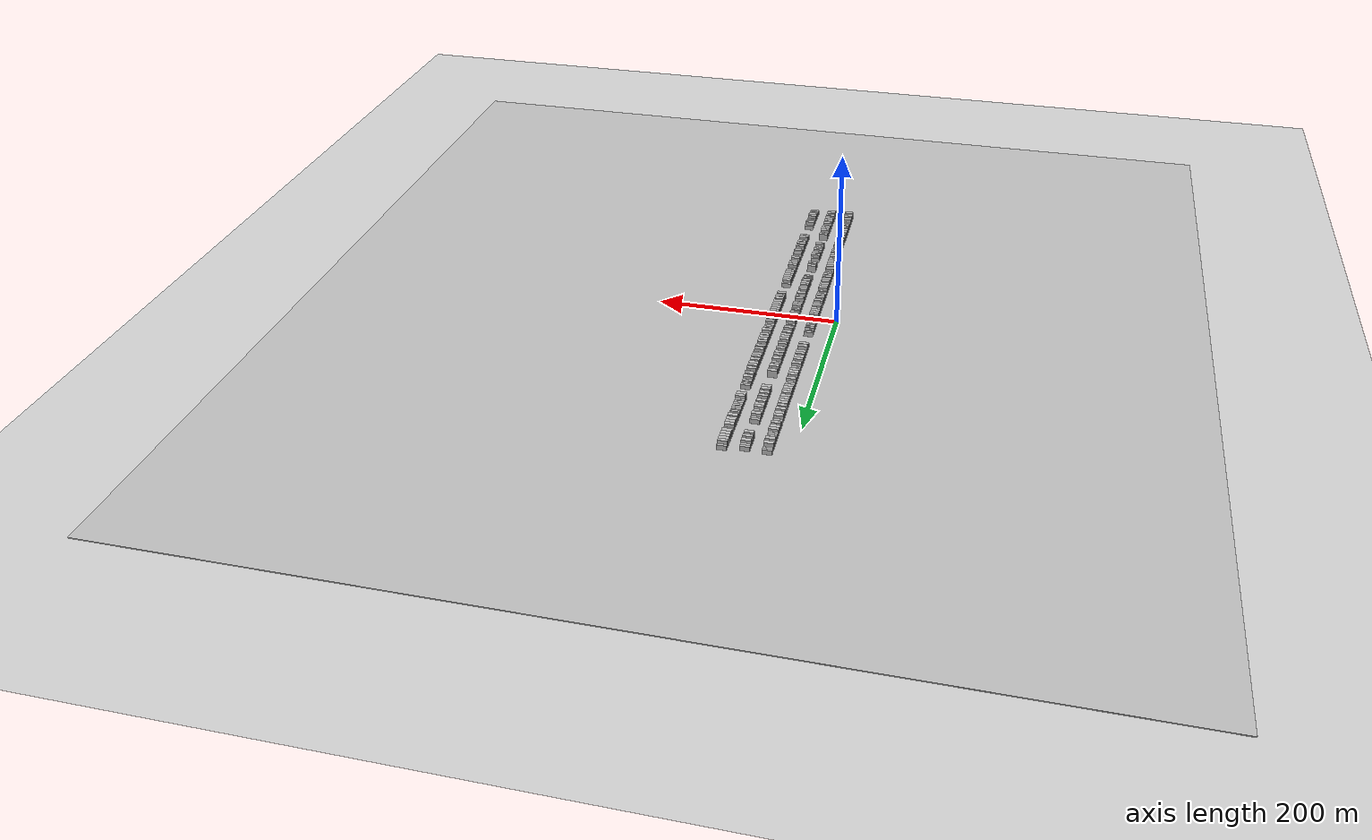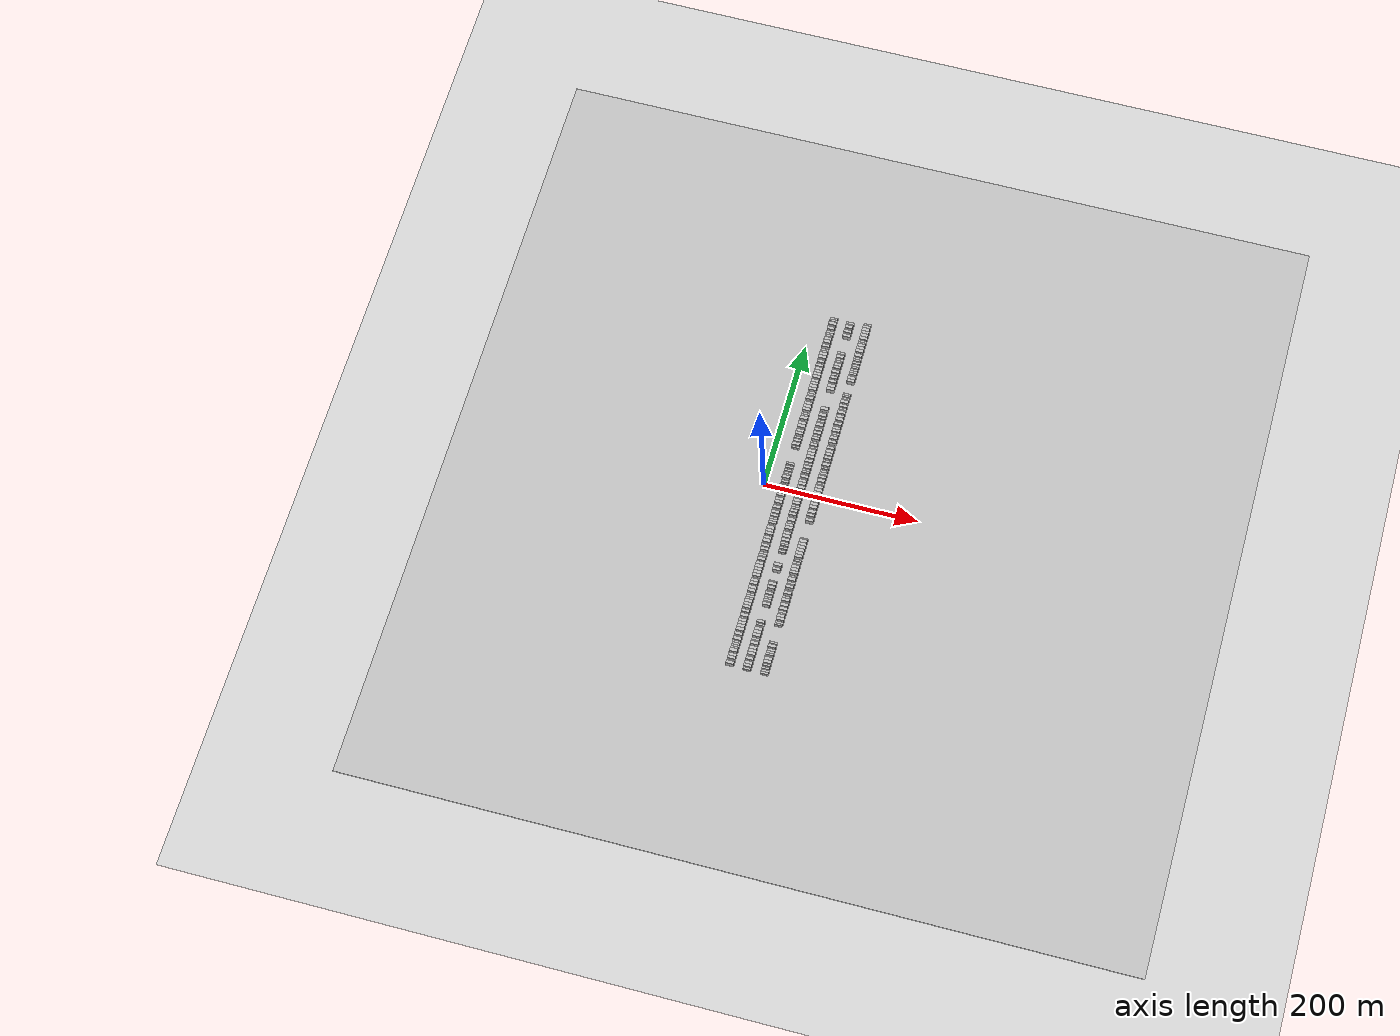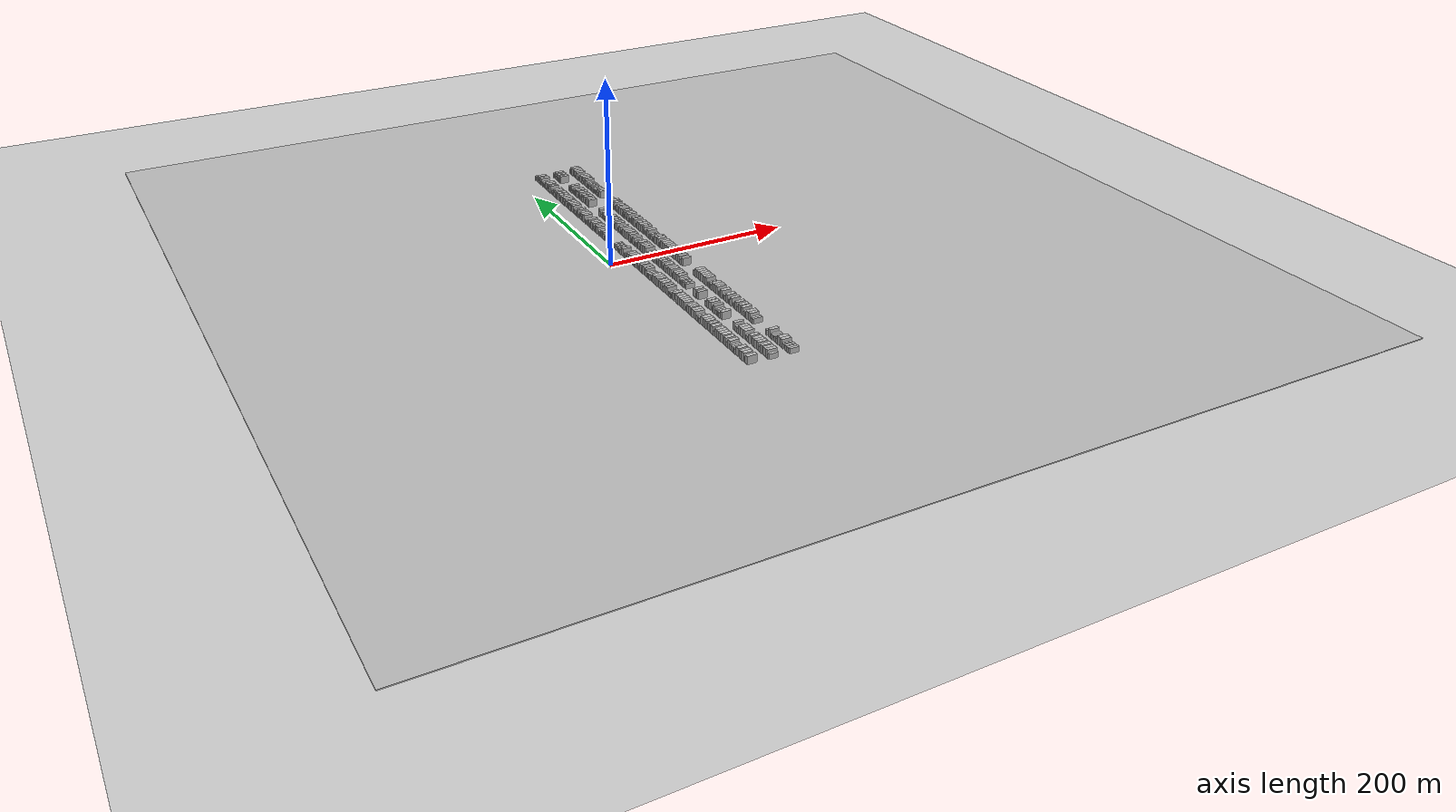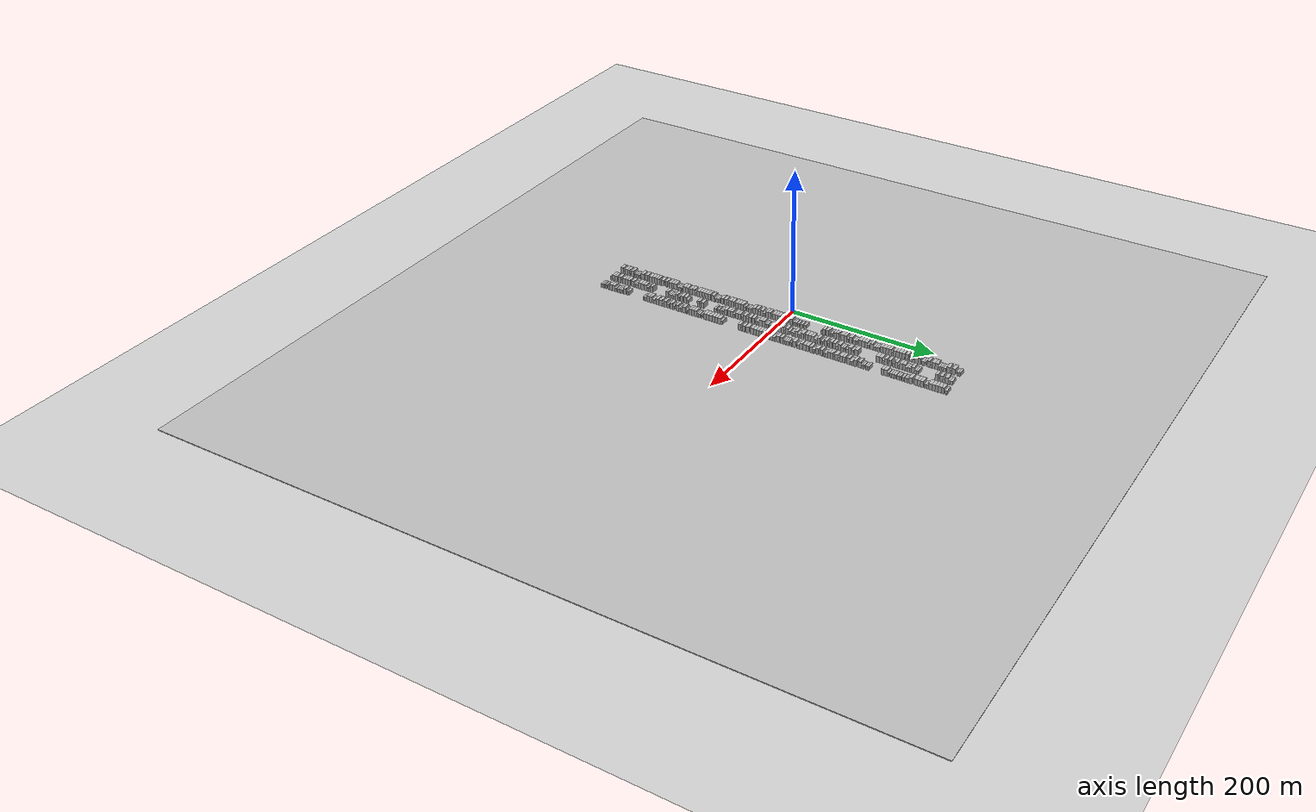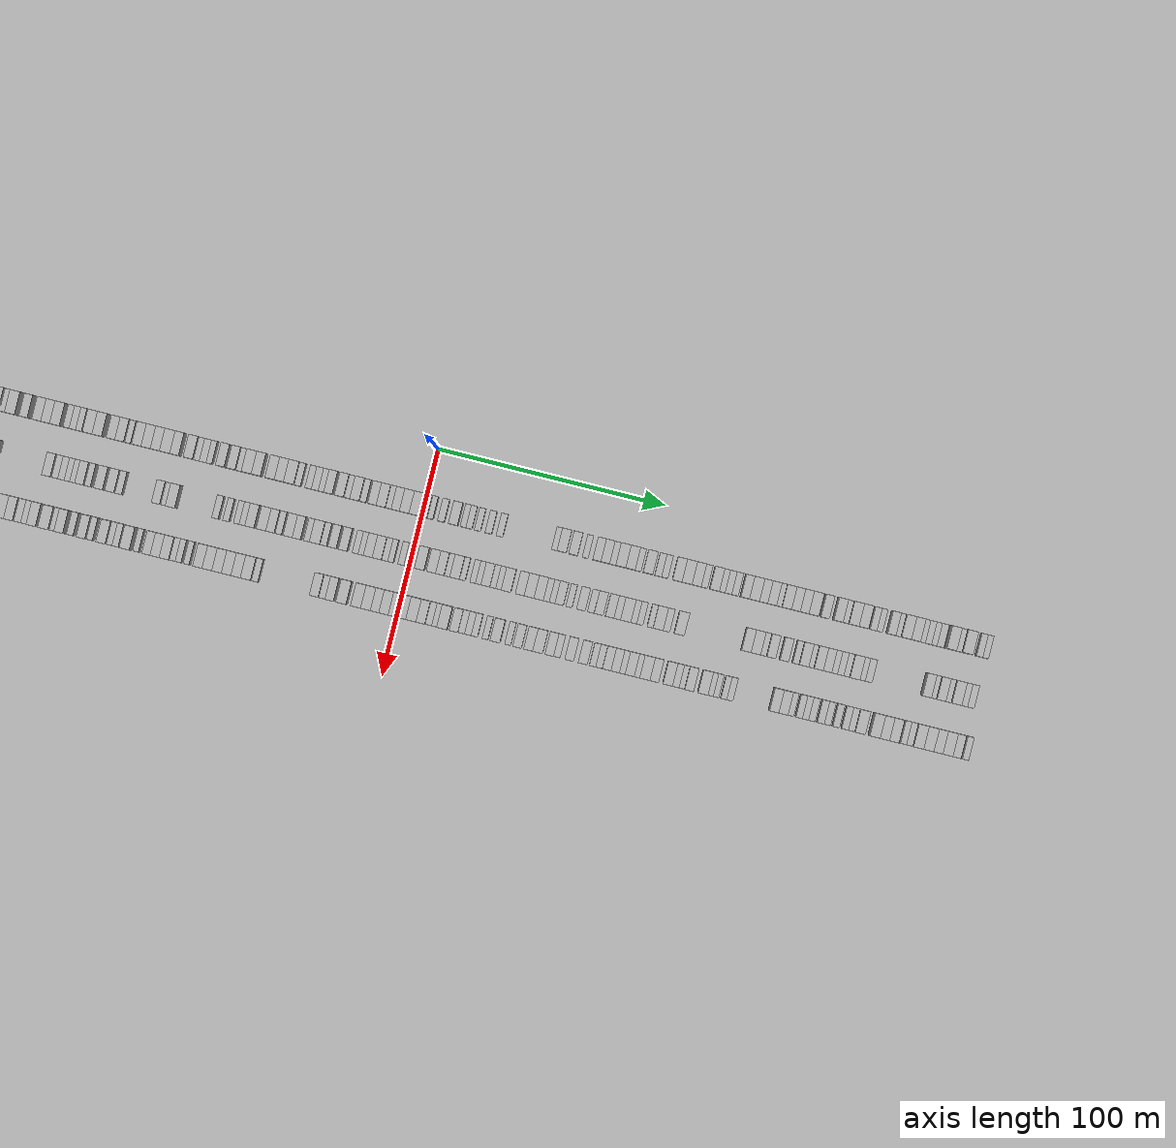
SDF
<?xml version="1.0" encoding="utf-8"?>

<sdf version="1.6">

   <world name="default">

      <gui fullscreen="0">

         <camera name="user_camera">

            <pose>-15 0 4.57585 0 0 0</pose>

            <view_controller>orbit</view_controller>

         </camera>

      </gui>

      <scene>

         <sky>

           <clouds>

             <speed>12</speed>

           </clouds>

         </sky>

         <ambient>0.4 0.4 0.4 1</ambient>

         <background>0.7 0.7 0.7 1</background>

         <shadows>1</shadows>

      </scene>

      <gravity>0 0 -9.8066</gravity>

      <magnetic_field>6e-06 2.3e-05 -4.2e-05</magnetic_field>

      <physics default="0" name="default_physics" type="ode">

         <ode>

            <solver>

               <type>quick</type>

               <iters>10</iters>

               <sor>1.0</sor>

               <use_dynamic_moi_rescaling>0</use_dynamic_moi_rescaling>

            </solver>

            <constraints>

               <cfm>0</cfm>

               <erp>0.2</erp>

               <contact_max_correcting_vel>100</contact_max_correcting_vel>

               <contact_surface_layer>0.001</contact_surface_layer>

            </constraints>

         </ode>

         <max_step_size>0.004</max_step_size>

         <real_time_factor>1</real_time_factor>

         <real_time_update_rate>250</real_time_update_rate>

      </physics>

      <light name="sun" type="directional">

         <cast_shadows>1</cast_shadows>

         <pose>0 0 10 0 0 0</pose>

         <diffuse>0.8 0.8 0.8 1</diffuse>

         <specular>0.2 0.2 0.2 1</specular>

         <attenuation>

            <range>1000</range>

            <constant>0.9</constant>

            <linear>0.01</linear>

            <quadratic>0.001</quadratic>

         </attenuation>

         <direction>-0.5 0.1 -0.9</direction>

      </light>

      <include>

         <name>ground_plane_1</name>

         <uri>model://HANNAS_ground_plane</uri>

         <pose>0 0 0  0 0 0</pose>

      </include>

      <include>

         <name>ground_plane_2</name>

         <uri>model://HANNAS_ground_plane</uri>

         <pose>100 0 0  0 0 0</pose>

      </include>

      <model name="building_1">

         <static>1</static>

         <pose frame="">25.0000 -244.8970 0 0.000000 0.000000 0.000000</pose>

         <link name="link">

            <pose frame="">0 0 4.50 0 0 0</pose>

            <collision name="collision">

               <geometry>

                  <box>

                     <size>10.0000 4.2061 9.0000</size>

                  </box>

               </geometry>

               <max_contacts>10</max_contacts>

               <surface>

                  <contact>

                     <ode/>

                  </contact>

                  <bounce/>

                  <friction>

                     <torsional>

                        <ode/>

                     </torsional>

                     <ode/>

                  </friction>

               </surface>

            </collision>

            <visual name="visual">

               <cast_shadows>0</cast_shadows>

               <geometry>

                  <box>

                     <size>10.0000 4.2061 9.0000</size>

                  </box>

               </geometry>

               <material>

                  <script>

                     <uri>model://HANNAS_wall/materials/scripts</uri>

                     <uri>model://HANNAS_wall/materials/textures</uri>

                     <name>vrc/HANNAS_wall</name>

                  </script>

               </material>

            </visual>

            <self_collide>0</self_collide>

            <enable_wind>0</enable_wind>

            <kinematic>0</kinematic>

         </link>

      </model>

      <model name="building_2">

         <static>1</static>

         <pose frame="">25.0000 -241.4556 0 0.000000 0.000000 0.000000</pose>

         <link name="link">

            <pose frame="">0 0 3.00 0 0 0</pose>

            <collision name="collision">

               <geometry>

                  <box>

                     <size>10.0000 2.6767 6.0000</size>

                  </box>

               </geometry>

               <max_contacts>10</max_contacts>

               <surface>

                  <contact>

                     <ode/>

                  </contact>

                  <bounce/>

                  <friction>

                     <torsional>

                        <ode/>

                     </torsional>

                     <ode/>

                  </friction>

               </surface>

            </collision>

            <visual name="visual">

               <cast_shadows>0</cast_shadows>

               <geometry>

                  <box>

                     <size>10.0000 2.6767 6.0000</size>

                  </box>

               </geometry>

               <material>

                  <script>

                     <uri>model://HANNAS_wall/materials/scripts</uri>

                     <uri>model://HANNAS_wall/materials/textures</uri>

                     <name>vrc/HANNAS_wall</name>

                  </script>

               </material>

            </visual>

            <self_collide>0</self_collide>

            <enable_wind>0</enable_wind>

            <kinematic>0</kinematic>

         </link>

      </model>

      <model name="building_3">

         <static>1</static>

         <pose frame="">25.0000 -238.1111 0 0.000000 0.000000 0.000000</pose>

         <link name="link">

            <pose frame="">0 0 4.50 0 0 0</pose>

            <collision name="collision">

               <geometry>

                  <box>

                     <size>10.0000 4.0122 9.0000</size>

                  </box>

               </geometry>

               <max_contacts>10</max_contacts>

               <surface>

                  <contact>

                     <ode/>

                  </contact>

                  <bounce/>

                  <friction>

                     <torsional>

                        <ode/>

                     </torsional>

                     <ode/>

                  </friction>

               </surface>

            </collision>

            <visual name="visual">

               <cast_shadows>0</cast_shadows>

               <geometry>

                  <box>

                     <size>10.0000 4.0122 9.0000</size>

                  </box>

               </geometry>

               <material>

                  <script>

                     <uri>model://HANNAS_wall/materials/scripts</uri>

                     <uri>model://HANNAS_wall/materials/textures</uri>

                     <name>vrc/HANNAS_wall</name>

                  </script>

               </material>

            </visual>

            <self_collide>0</self_collide>

            <enable_wind>0</enable_wind>

            <kinematic>0</kinematic>

         </link>

      </model>

      <model name="building_4">

         <static>1</static>

         <pose frame="">25.0000 -234.2194 0 0.000000 0.000000 0.000000</pose>

         <link name="link">

            <pose frame="">0 0 4.50 0 0 0</pose>

            <collision name="collision">

               <geometry>

                  <box>

                     <size>10.0000 3.7712 9.0000</size>

                  </box>

               </geometry>

               <max_contacts>10</max_contacts>

               <surface>

                  <contact>

                     <ode/>

                  </contact>

                  <bounce/>

                  <friction>

                     <torsional>

                        <ode/>

                     </torsional>

                     <ode/>

                  </friction>

               </surface>

            </collision>

            <visual name="visual">

               <cast_shadows>0</cast_shadows>

               <geometry>

                  <box>

                     <size>10.0000 3.7712 9.0000</size>

                  </box>

               </geometry>

               <material>

                  <script>

                     <uri>model://HANNAS_wall/materials/scripts</uri>

                     <uri>model://HANNAS_wall/materials/textures</uri>

                     <name>vrc/HANNAS_wall</name>

                  </script>

               </material>

            </visual>

            <self_collide>0</self_collide>

            <enable_wind>0</enable_wind>

            <kinematic>0</kinematic>

         </link>

      </model>

      <model name="building_5">

         <static>1</static>

         <pose frame="">25.0000 -228.1058 0 0.000000 0.000000 0.000000</pose>

         <link name="link">

            <pose frame="">0 0 4.50 0 0 0</pose>

            <collision name="collision">

               <geometry>

                  <box>

                     <size>10.0000 4.4559 9.0000</size>

                  </box>

               </geometry>

               <max_contacts>10</max_contacts>

               <surface>

                  <contact>

                     <ode/>

                  </contact>

                  <bounce/>

                  <friction>

                     <torsional>

                        <ode/>

                     </torsional>

                     <ode/>

                  </friction>

               </surface>

            </collision>

            <visual name="visual">

               <cast_shadows>0</cast_shadows>

               <geometry>

                  <box>

                     <size>10.0000 4.4559 9.0000</size>

                  </box>

               </geometry>

               <material>

                  <script>

                     <uri>model://HANNAS_wall/materials/scripts</uri>

                     <uri>model://HANNAS_wall/materials/textures</uri>

                     <name>vrc/HANNAS_wall</name>

                  </script>

               </material>

            </visual>

            <self_collide>0</self_collide>

            <enable_wind>0</enable_wind>

            <kinematic>0</kinematic>

         </link>

      </model>

      <model name="building_6">

         <static>1</static>

         <pose frame="">25.0000 -223.6642 0 0.000000 0.000000 0.000000</pose>

         <link name="link">

            <pose frame="">0 0 3.00 0 0 0</pose>

            <collision name="collision">

               <geometry>

                  <box>

                     <size>10.0000 2.4274 6.0000</size>

                  </box>

               </geometry>

               <max_contacts>10</max_contacts>

               <surface>

                  <contact>

                     <ode/>

                  </contact>

                  <bounce/>

                  <friction>

                     <torsional>

                        <ode/>

                     </torsional>

                     <ode/>

                  </friction>

               </surface>

            </collision>

            <visual name="visual">

               <cast_shadows>0</cast_shadows>

               <geometry>

                  <box>

                     <size>10.0000 2.4274 6.0000</size>

                  </box>

               </geometry>

               <material>

                  <script>

                     <uri>model://HANNAS_wall/materials/scripts</uri>

                     <uri>model://HANNAS_wall/materials/textures</uri>

                     <name>vrc/HANNAS_wall</name>

                  </script>

               </material>

            </visual>

            <self_collide>0</self_collide>

            <enable_wind>0</enable_wind>

            <kinematic>0</kinematic>

         </link>

      </model>

      <model name="building_7">

         <static>1</static>

         <pose frame="">25.0000 -221.1104 0 0.000000 0.000000 0.000000</pose>

         <link name="link">

            <pose frame="">0 0 3.00 0 0 0</pose>

            <collision name="collision">

               <geometry>

                  <box>

                     <size>10.0000 2.6801 6.0000</size>

                  </box>

               </geometry>

               <max_contacts>10</max_contacts>

               <surface>

                  <contact>

                     <ode/>

                  </contact>

                  <bounce/>

                  <friction>

                     <torsional>

                        <ode/>

                     </torsional>

                     <ode/>

                  </friction>

               </surface>

            </collision>

            <visual name="visual">

               <cast_shadows>0</cast_shadows>

               <geometry>

                  <box>

                     <size>10.0000 2.6801 6.0000</size>

                  </box>

               </geometry>

               <material>

                  <script>

                     <uri>model://HANNAS_wall/materials/scripts</uri>

                     <uri>model://HANNAS_wall/materials/textures</uri>

                     <name>vrc/HANNAS_wall</name>

                  </script>

               </material>

            </visual>

            <self_collide>0</self_collide>

            <enable_wind>0</enable_wind>

            <kinematic>0</kinematic>

         </link>

      </model>

      <model name="building_8">

         <static>1</static>

         <pose frame="">25.0000 -218.4601 0 0.000000 0.000000 0.000000</pose>

         <link name="link">

            <pose frame="">0 0 3.00 0 0 0</pose>

            <collision name="collision">

               <geometry>

                  <box>

                     <size>10.0000 2.6207 6.0000</size>

                  </box>

               </geometry>

               <max_contacts>10</max_contacts>

               <surface>

                  <contact>

                     <ode/>

                  </contact>

                  <bounce/>

                  <friction>

                     <torsional>

                        <ode/>

                     </torsional>

                     <ode/>

                  </friction>

               </surface>

            </collision>

            <visual name="visual">

               <cast_shadows>0</cast_shadows>

               <geometry>

                  <box>

                     <size>10.0000 2.6207 6.0000</size>

                  </box>

               </geometry>

               <material>

                  <script>

                     <uri>model://HANNAS_wall/materials/scripts</uri>

                     <uri>model://HANNAS_wall/materials/textures</uri>

                     <name>vrc/HANNAS_wall</name>

                  </script>

               </material>

            </visual>

            <self_collide>0</self_collide>

            <enable_wind>0</enable_wind>

            <kinematic>0</kinematic>

         </link>

      </model>

      <model name="building_9">

         <static>1</static>

         <pose frame="">25.0000 -215.8077 0 0.000000 0.000000 0.000000</pose>

         <link name="link">

            <pose frame="">0 0 3.00 0 0 0</pose>

            <collision name="collision">

               <geometry>

                  <box>

                     <size>10.0000 2.6840 6.0000</size>

                  </box>

               </geometry>

               <max_contacts>10</max_contacts>

               <surface>

                  <contact>

                     <ode/>

                  </contact>

                  <bounce/>

                  <friction>

                     <torsional>

                        <ode/>

                     </torsional>

                     <ode/>

                  </friction>

               </surface>

            </collision>

            <visual name="visual">

               <cast_shadows>0</cast_shadows>

               <geometry>

                  <box>

                     <size>10.0000 2.6840 6.0000</size>

                  </box>

               </geometry>

               <material>

                  <script>

                     <uri>model://HANNAS_wall/materials/scripts</uri>

                     <uri>model://HANNAS_wall/materials/textures</uri>

                     <name>vrc/HANNAS_wall</name>

                  </script>

               </material>

            </visual>

            <self_collide>0</self_collide>

            <enable_wind>0</enable_wind>

            <kinematic>0</kinematic>

         </link>

      </model>

      <model name="building_10">

         <static>1</static>

         <pose frame="">25.0000 -212.2497 0 0.000000 0.000000 0.000000</pose>

         <link name="link">

            <pose frame="">0 0 4.50 0 0 0</pose>

            <collision name="collision">

               <geometry>

                  <box>

                     <size>10.0000 4.4320 9.0000</size>

                  </box>

               </geometry>

               <max_contacts>10</max_contacts>

               <surface>

                  <contact>

                     <ode/>

                  </contact>

                  <bounce/>

                  <friction>

                     <torsional>

                        <ode/>

                     </torsional>

                     <ode/>

                  </friction>

               </surface>

            </collision>

            <visual name="visual">

               <cast_shadows>0</cast_shadows>

               <geometry>

                  <box>

                     <size>10.0000 4.4320 9.0000</size>

                  </box>

               </geometry>

               <material>

                  <script>

                     <uri>model://HANNAS_wall/materials/scripts</uri>

                     <uri>model://HANNAS_wall/materials/textures</uri>

                     <name>vrc/HANNAS_wall</name>

                  </script>

               </material>

            </visual>

            <self_collide>0</self_collide>

            <enable_wind>0</enable_wind>

            <kinematic>0</kinematic>

         </link>

      </model>

      <model name="building_11">

         <static>1</static>

         <pose frame="">25.0000 -208.8162 0 0.000000 0.000000 0.000000</pose>

         <link name="link">

            <pose frame="">0 0 3.00 0 0 0</pose>

            <collision name="collision">

               <geometry>

                  <box>

                     <size>10.0000 2.4350 6.0000</size>

                  </box>

               </geometry>

               <max_contacts>10</max_contacts>

               <surface>

                  <contact>

                     <ode/>

                  </contact>

                  <bounce/>

                  <friction>

                     <torsional>

                        <ode/>

                     </torsional>

                     <ode/>

                  </friction>

               </surface>

            </collision>

            <visual name="visual">

               <cast_shadows>0</cast_shadows>

               <geometry>

                  <box>

                     <size>10.0000 2.4350 6.0000</size>

                  </box>

               </geometry>

               <material>

                  <script>

                     <uri>model://HANNAS_wall/materials/scripts</uri>

                     <uri>model://HANNAS_wall/materials/textures</uri>

                     <name>vrc/HANNAS_wall</name>

                  </script>

               </material>

            </visual>

            <self_collide>0</self_collide>

            <enable_wind>0</enable_wind>

            <kinematic>0</kinematic>

         </link>

      </model>

      <model name="building_12">

         <static>1</static>

         <pose frame="">25.0000 -205.5930 0 0.000000 0.000000 0.000000</pose>

         <link name="link">

            <pose frame="">0 0 4.50 0 0 0</pose>

            <collision name="collision">

               <geometry>

                  <box>

                     <size>10.0000 4.0115 9.0000</size>

                  </box>

               </geometry>

               <max_contacts>10</max_contacts>

               <surface>

                  <contact>

                     <ode/>

                  </contact>

                  <bounce/>

                  <friction>

                     <torsional>

                        <ode/>

                     </torsional>

                     <ode/>

                  </friction>

               </surface>

            </collision>

            <visual name="visual">

               <cast_shadows>0</cast_shadows>

               <geometry>

                  <box>

                     <size>10.0000 4.0115 9.0000</size>

                  </box>

               </geometry>

               <material>

                  <script>

                     <uri>model://HANNAS_wall/materials/scripts</uri>

                     <uri>model://HANNAS_wall/materials/textures</uri>

                     <name>vrc/HANNAS_wall</name>

                  </script>

               </material>

            </visual>

            <self_collide>0</self_collide>

            <enable_wind>0</enable_wind>

            <kinematic>0</kinematic>

         </link>

      </model>

      <model name="building_13">

         <static>1</static>

         <pose frame="">25.0000 -199.3401 0 0.000000 0.000000 0.000000</pose>

         <link name="link">

            <pose frame="">0 0 4.50 0 0 0</pose>

            <collision name="collision">

               <geometry>

                  <box>

                     <size>10.0000 4.4942 9.0000</size>

                  </box>

               </geometry>

               <max_contacts>10</max_contacts>

               <surface>

                  <contact>

                     <ode/>

                  </contact>

                  <bounce/>

                  <friction>

                     <torsional>

                        <ode/>

                     </torsional>

                     <ode/>

                  </friction>

               </surface>

            </collision>

            <visual name="visual">

               <cast_shadows>0</cast_shadows>

               <geometry>

                  <box>

                     <size>10.0000 4.4942 9.0000</size>

                  </box>

               </geometry>

               <material>

                  <script>

                     <uri>model://HANNAS_wall/materials/scripts</uri>

                     <uri>model://HANNAS_wall/materials/textures</uri>

                     <name>vrc/HANNAS_wall</name>

                  </script>

               </material>

            </visual>

            <self_collide>0</self_collide>

            <enable_wind>0</enable_wind>

            <kinematic>0</kinematic>

         </link>

      </model>

      <model name="building_14">

         <static>1</static>

         <pose frame="">25.0000 -195.0859 0 0.000000 0.000000 0.000000</pose>

         <link name="link">

            <pose frame="">0 0 4.50 0 0 0</pose>

            <collision name="collision">

               <geometry>

                  <box>

                     <size>10.0000 4.0142 9.0000</size>

                  </box>

               </geometry>

               <max_contacts>10</max_contacts>

               <surface>

                  <contact>

                     <ode/>

                  </contact>

                  <bounce/>

                  <friction>

                     <torsional>

                        <ode/>

                     </torsional>

                     <ode/>

                  </friction>

               </surface>

            </collision>

            <visual name="visual">

               <cast_shadows>0</cast_shadows>

               <geometry>

                  <box>

                     <size>10.0000 4.0142 9.0000</size>

                  </box>

               </geometry>

               <material>

                  <script>

                     <uri>model://HANNAS_wall/materials/scripts</uri>

                     <uri>model://HANNAS_wall/materials/textures</uri>

                     <name>vrc/HANNAS_wall</name>

                  </script>

               </material>

            </visual>

            <self_collide>0</self_collide>

            <enable_wind>0</enable_wind>

            <kinematic>0</kinematic>

         </link>

      </model>

      <model name="building_15">

         <static>1</static>

         <pose frame="">25.0000 -191.0674 0 0.000000 0.000000 0.000000</pose>

         <link name="link">

            <pose frame="">0 0 4.50 0 0 0</pose>

            <collision name="collision">

               <geometry>

                  <box>

                     <size>10.0000 4.0227 9.0000</size>

                  </box>

               </geometry>

               <max_contacts>10</max_contacts>

               <surface>

                  <contact>

                     <ode/>

                  </contact>

                  <bounce/>

                  <friction>

                     <torsional>

                        <ode/>

                     </torsional>

                     <ode/>

                  </friction>

               </surface>

            </collision>

            <visual name="visual">

               <cast_shadows>0</cast_shadows>

               <geometry>

                  <box>

                     <size>10.0000 4.0227 9.0000</size>

                  </box>

               </geometry>

               <material>

                  <script>

                     <uri>model://HANNAS_wall/materials/scripts</uri>

                     <uri>model://HANNAS_wall/materials/textures</uri>

                     <name>vrc/HANNAS_wall</name>

                  </script>

               </material>

            </visual>

            <self_collide>0</self_collide>

            <enable_wind>0</enable_wind>

            <kinematic>0</kinematic>

         </link>

      </model>

      <model name="building_16">

         <static>1</static>

         <pose frame="">25.0000 -187.1419 0 0.000000 0.000000 0.000000</pose>

         <link name="link">

            <pose frame="">0 0 4.50 0 0 0</pose>

            <collision name="collision">

               <geometry>

                  <box>

                     <size>10.0000 3.8285 9.0000</size>

                  </box>

               </geometry>

               <max_contacts>10</max_contacts>

               <surface>

                  <contact>

                     <ode/>

                  </contact>

                  <bounce/>

                  <friction>

                     <torsional>

                        <ode/>

                     </torsional>

                     <ode/>

                  </friction>

               </surface>

            </collision>

            <visual name="visual">

               <cast_shadows>0</cast_shadows>

               <geometry>

                  <box>

                     <size>10.0000 3.8285 9.0000</size>

                  </box>

               </geometry>

               <material>

                  <script>

                     <uri>model://HANNAS_wall/materials/scripts</uri>

                     <uri>model://HANNAS_wall/materials/textures</uri>

                     <name>vrc/HANNAS_wall</name>

                  </script>

               </material>

            </visual>

            <self_collide>0</self_collide>

            <enable_wind>0</enable_wind>

            <kinematic>0</kinematic>

         </link>

      </model>

      <model name="building_17">

         <static>1</static>

         <pose frame="">25.0000 -183.8294 0 0.000000 0.000000 0.000000</pose>

         <link name="link">

            <pose frame="">0 0 3.00 0 0 0</pose>

            <collision name="collision">

               <geometry>

                  <box>

                     <size>10.0000 2.7963 6.0000</size>

                  </box>

               </geometry>

               <max_contacts>10</max_contacts>

               <surface>

                  <contact>

                     <ode/>

                  </contact>

                  <bounce/>

                  <friction>

                     <torsional>

                        <ode/>

                     </torsional>

                     <ode/>

                  </friction>

               </surface>

            </collision>

            <visual name="visual">

               <cast_shadows>0</cast_shadows>

               <geometry>

                  <box>

                     <size>10.0000 2.7963 6.0000</size>

                  </box>

               </geometry>

               <material>

                  <script>

                     <uri>model://HANNAS_wall/materials/scripts</uri>

                     <uri>model://HANNAS_wall/materials/textures</uri>

                     <name>vrc/HANNAS_wall</name>

                  </script>

               </material>

            </visual>

            <self_collide>0</self_collide>

            <enable_wind>0</enable_wind>

            <kinematic>0</kinematic>

         </link>

      </model>

      <model name="building_18">

         <static>1</static>

         <pose frame="">25.0000 -180.2356 0 0.000000 0.000000 0.000000</pose>

         <link name="link">

            <pose frame="">0 0 4.50 0 0 0</pose>

            <collision name="collision">

               <geometry>

                  <box>

                     <size>10.0000 4.3914 9.0000</size>

                  </box>

               </geometry>

               <max_contacts>10</max_contacts>

               <surface>

                  <contact>

                     <ode/>

                  </contact>

                  <bounce/>

                  <friction>

                     <torsional>

                        <ode/>

                     </torsional>

                     <ode/>

                  </friction>

               </surface>

            </collision>

            <visual name="visual">

               <cast_shadows>0</cast_shadows>

               <geometry>

                  <box>

                     <size>10.0000 4.3914 9.0000</size>

                  </box>

               </geometry>

               <material>

                  <script>

                     <uri>model://HANNAS_wall/materials/scripts</uri>

                     <uri>model://HANNAS_wall/materials/textures</uri>

                     <name>vrc/HANNAS_wall</name>

                  </script>

               </material>

            </visual>

            <self_collide>0</self_collide>

            <enable_wind>0</enable_wind>

            <kinematic>0</kinematic>

         </link>

      </model>

      <model name="building_19">

         <static>1</static>

         <pose frame="">25.0000 -174.2396 0 0.000000 0.000000 0.000000</pose>

         <link name="link">

            <pose frame="">0 0 4.50 0 0 0</pose>

            <collision name="collision">

               <geometry>

                  <box>

                     <size>10.0000 3.6005 9.0000</size>

                  </box>

               </geometry>

               <max_contacts>10</max_contacts>

               <surface>

                  <contact>

                     <ode/>

                  </contact>

                  <bounce/>

                  <friction>

                     <torsional>

                        <ode/>

                     </torsional>

                     <ode/>

                  </friction>

               </surface>

            </collision>

            <visual name="visual">

               <cast_shadows>0</cast_shadows>

               <geometry>

                  <box>

                     <size>10.0000 3.6005 9.0000</size>

                  </box>

               </geometry>

               <material>

                  <script>

                     <uri>model://HANNAS_wall/materials/scripts</uri>

                     <uri>model://HANNAS_wall/materials/textures</uri>

                     <name>vrc/HANNAS_wall</name>

                  </script>

               </material>

            </visual>

            <self_collide>0</self_collide>

            <enable_wind>0</enable_wind>

            <kinematic>0</kinematic>

         </link>

      </model>

      <model name="building_20">

         <static>1</static>

         <pose frame="">25.0000 -168.4787 0 0.000000 0.000000 0.000000</pose>

         <link name="link">

            <pose frame="">0 0 4.50 0 0 0</pose>

            <collision name="collision">

               <geometry>

                  <box>

                     <size>10.0000 3.9212 9.0000</size>

                  </box>

               </geometry>

               <max_contacts>10</max_contacts>

               <surface>

                  <contact>

                     <ode/>

                  </contact>

                  <bounce/>

                  <friction>

                     <torsional>

                        <ode/>

                     </torsional>

                     <ode/>

                  </friction>

               </surface>

            </collision>

            <visual name="visual">

               <cast_shadows>0</cast_shadows>

               <geometry>

                  <box>

                     <size>10.0000 3.9212 9.0000</size>

                  </box>

               </geometry>

               <material>

                  <script>

                     <uri>model://HANNAS_wall/materials/scripts</uri>

                     <uri>model://HANNAS_wall/materials/textures</uri>

                     <name>vrc/HANNAS_wall</name>

                  </script>

               </material>

            </visual>

            <self_collide>0</self_collide>

            <enable_wind>0</enable_wind>

            <kinematic>0</kinematic>

         </link>

      </model>

      <model name="building_21">

         <static>1</static>

         <pose frame="">25.0000 -164.5937 0 0.000000 0.000000 0.000000</pose>

         <link name="link">

            <pose frame="">0 0 4.50 0 0 0</pose>

            <collision name="collision">

               <geometry>

                  <box>

                     <size>10.0000 3.8489 9.0000</size>

                  </box>

               </geometry>

               <max_contacts>10</max_contacts>

               <surface>

                  <contact>

                     <ode/>

                  </contact>

                  <bounce/>

                  <friction>

                     <torsional>

                        <ode/>

                     </torsional>

                     <ode/>

                  </friction>

               </surface>

            </collision>

            <visual name="visual">

               <cast_shadows>0</cast_shadows>

               <geometry>

                  <box>

                     <size>10.0000 3.8489 9.0000</size>

                  </box>

               </geometry>

               <material>

                  <script>

                     <uri>model://HANNAS_wall/materials/scripts</uri>

                     <uri>model://HANNAS_wall/materials/textures</uri>

                     <name>vrc/HANNAS_wall</name>

                  </script>

               </material>

            </visual>

            <self_collide>0</self_collide>

            <enable_wind>0</enable_wind>

            <kinematic>0</kinematic>

         </link>

      </model>

      <model name="building_22">

         <static>1</static>

         <pose frame="">25.0000 -160.5291 0 0.000000 0.000000 0.000000</pose>

         <link name="link">

            <pose frame="">0 0 4.50 0 0 0</pose>

            <collision name="collision">

               <geometry>

                  <box>

                     <size>10.0000 4.2802 9.0000</size>

                  </box>

               </geometry>

               <max_contacts>10</max_contacts>

               <surface>

                  <contact>

                     <ode/>

                  </contact>

                  <bounce/>

                  <friction>

                     <torsional>

                        <ode/>

                     </torsional>

                     <ode/>

                  </friction>

               </surface>

            </collision>

            <visual name="visual">

               <cast_shadows>0</cast_shadows>

               <geometry>

                  <box>

                     <size>10.0000 4.2802 9.0000</size>

                  </box>

               </geometry>

               <material>

                  <script>

                     <uri>model://HANNAS_wall/materials/scripts</uri>

                     <uri>model://HANNAS_wall/materials/textures</uri>

                     <name>vrc/HANNAS_wall</name>

                  </script>

               </material>

            </visual>

            <self_collide>0</self_collide>

            <enable_wind>0</enable_wind>

            <kinematic>0</kinematic>

         </link>

      </model>

      <model name="building_23">

         <static>1</static>

         <pose frame="">25.0000 -156.0128 0 0.000000 0.000000 0.000000</pose>

         <link name="link">

            <pose frame="">0 0 3.00 0 0 0</pose>

            <collision name="collision">

               <geometry>

                  <box>

                     <size>10.0000 2.7525 6.0000</size>

                  </box>

               </geometry>

               <max_contacts>10</max_contacts>

               <surface>

                  <contact>

                     <ode/>

                  </contact>

                  <bounce/>

                  <friction>

                     <torsional>

                        <ode/>

                     </torsional>

                     <ode/>

                  </friction>

               </surface>

            </collision>

            <visual name="visual">

               <cast_shadows>0</cast_shadows>

               <geometry>

                  <box>

                     <size>10.0000 2.7525 6.0000</size>

                  </box>

               </geometry>

               <material>

                  <script>

                     <uri>model://HANNAS_wall/materials/scripts</uri>

                     <uri>model://HANNAS_wall/materials/textures</uri>

                     <name>vrc/HANNAS_wall</name>

                  </script>

               </material>

            </visual>

            <self_collide>0</self_collide>

            <enable_wind>0</enable_wind>

            <kinematic>0</kinematic>

         </link>

      </model>

      <model name="building_24">

         <static>1</static>

         <pose frame="">25.0000 -153.2260 0 0.000000 0.000000 0.000000</pose>

         <link name="link">

            <pose frame="">0 0 3.00 0 0 0</pose>

            <collision name="collision">

               <geometry>

                  <box>

                     <size>10.0000 2.8211 6.0000</size>

                  </box>

               </geometry>

               <max_contacts>10</max_contacts>

               <surface>

                  <contact>

                     <ode/>

                  </contact>

                  <bounce/>

                  <friction>

                     <torsional>

                        <ode/>

                     </torsional>

                     <ode/>

                  </friction>

               </surface>

            </collision>

            <visual name="visual">

               <cast_shadows>0</cast_shadows>

               <geometry>

                  <box>

                     <size>10.0000 2.8211 6.0000</size>

                  </box>

               </geometry>

               <material>

                  <script>

                     <uri>model://HANNAS_wall/materials/scripts</uri>

                     <uri>model://HANNAS_wall/materials/textures</uri>

                     <name>vrc/HANNAS_wall</name>

                  </script>

               </material>

            </visual>

            <self_collide>0</self_collide>

            <enable_wind>0</enable_wind>

            <kinematic>0</kinematic>

         </link>

      </model>

      <model name="building_25">

         <static>1</static>

         <pose frame="">25.0000 -150.5293 0 0.000000 0.000000 0.000000</pose>

         <link name="link">

            <pose frame="">0 0 3.00 0 0 0</pose>

            <collision name="collision">

               <geometry>

                  <box>

                     <size>10.0000 2.5723 6.0000</size>

                  </box>

               </geometry>

               <max_contacts>10</max_contacts>

               <surface>

                  <contact>

                     <ode/>

                  </contact>

                  <bounce/>

                  <friction>

                     <torsional>

                        <ode/>

                     </torsional>

                     <ode/>

                  </friction>

               </surface>

            </collision>

            <visual name="visual">

               <cast_shadows>0</cast_shadows>

               <geometry>

                  <box>

                     <size>10.0000 2.5723 6.0000</size>

                  </box>

               </geometry>

               <material>

                  <script>

                     <uri>model://HANNAS_wall/materials/scripts</uri>

                     <uri>model://HANNAS_wall/materials/textures</uri>

                     <name>vrc/HANNAS_wall</name>

                  </script>

               </material>

            </visual>

            <self_collide>0</self_collide>

            <enable_wind>0</enable_wind>

            <kinematic>0</kinematic>

         </link>

      </model>

      <model name="building_26">

         <static>1</static>

         <pose frame="">25.0000 -146.1814 0 0.000000 0.000000 0.000000</pose>

         <link name="link">

            <pose frame="">0 0 4.50 0 0 0</pose>

            <collision name="collision">

               <geometry>

                  <box>

                     <size>10.0000 4.1234 9.0000</size>

                  </box>

               </geometry>

               <max_contacts>10</max_contacts>

               <surface>

                  <contact>

                     <ode/>

                  </contact>

                  <bounce/>

                  <friction>

                     <torsional>

                        <ode/>

                     </torsional>

                     <ode/>

                  </friction>

               </surface>

            </collision>

            <visual name="visual">

               <cast_shadows>0</cast_shadows>

               <geometry>

                  <box>

                     <size>10.0000 4.1234 9.0000</size>

                  </box>

               </geometry>

               <material>

                  <script>

                     <uri>model://HANNAS_wall/materials/scripts</uri>

                     <uri>model://HANNAS_wall/materials/textures</uri>

                     <name>vrc/HANNAS_wall</name>

                  </script>

               </material>

            </visual>

            <self_collide>0</self_collide>

            <enable_wind>0</enable_wind>

            <kinematic>0</kinematic>

         </link>

      </model>

      <model name="building_27">

         <static>1</static>

         <pose frame="">25.0000 -142.0024 0 0.000000 0.000000 0.000000</pose>

         <link name="link">

            <pose frame="">0 0 4.50 0 0 0</pose>

            <collision name="collision">

               <geometry>

                  <box>

                     <size>10.0000 4.2346 9.0000</size>

                  </box>

               </geometry>

               <max_contacts>10</max_contacts>

               <surface>

                  <contact>

                     <ode/>

                  </contact>

                  <bounce/>

                  <friction>

                     <torsional>

                        <ode/>

                     </torsional>

                     <ode/>

                  </friction>

               </surface>

            </collision>

            <visual name="visual">

               <cast_shadows>0</cast_shadows>

               <geometry>

                  <box>

                     <size>10.0000 4.2346 9.0000</size>

                  </box>

               </geometry>

               <material>

                  <script>

                     <uri>model://HANNAS_wall/materials/scripts</uri>

                     <uri>model://HANNAS_wall/materials/textures</uri>

                     <name>vrc/HANNAS_wall</name>

                  </script>

               </material>

            </visual>

            <self_collide>0</self_collide>

            <enable_wind>0</enable_wind>

            <kinematic>0</kinematic>

         </link>

      </model>

      <model name="building_28">

         <static>1</static>

         <pose frame="">25.0000 -136.0054 0 0.000000 0.000000 0.000000</pose>

         <link name="link">

            <pose frame="">0 0 4.50 0 0 0</pose>

            <collision name="collision">

               <geometry>

                  <box>

                     <size>10.0000 3.7594 9.0000</size>

                  </box>

               </geometry>

               <max_contacts>10</max_contacts>

               <surface>

                  <contact>

                     <ode/>

                  </contact>

                  <bounce/>

                  <friction>

                     <torsional>

                        <ode/>

                     </torsional>

                     <ode/>

                  </friction>

               </surface>

            </collision>

            <visual name="visual">

               <cast_shadows>0</cast_shadows>

               <geometry>

                  <box>

                     <size>10.0000 3.7594 9.0000</size>

                  </box>

               </geometry>

               <material>

                  <script>

                     <uri>model://HANNAS_wall/materials/scripts</uri>

                     <uri>model://HANNAS_wall/materials/textures</uri>

                     <name>vrc/HANNAS_wall</name>

                  </script>

               </material>

            </visual>

            <self_collide>0</self_collide>

            <enable_wind>0</enable_wind>

            <kinematic>0</kinematic>

         </link>

      </model>

      <model name="building_29">

         <static>1</static>

         <pose frame="">25.0000 -132.1710 0 0.000000 0.000000 0.000000</pose>

         <link name="link">

            <pose frame="">0 0 4.50 0 0 0</pose>

            <collision name="collision">

               <geometry>

                  <box>

                     <size>10.0000 3.9094 9.0000</size>

                  </box>

               </geometry>

               <max_contacts>10</max_contacts>

               <surface>

                  <contact>

                     <ode/>

                  </contact>

                  <bounce/>

                  <friction>

                     <torsional>

                        <ode/>

                     </torsional>

                     <ode/>

                  </friction>

               </surface>

            </collision>

            <visual name="visual">

               <cast_shadows>0</cast_shadows>

               <geometry>

                  <box>

                     <size>10.0000 3.9094 9.0000</size>

                  </box>

               </geometry>

               <material>

                  <script>

                     <uri>model://HANNAS_wall/materials/scripts</uri>

                     <uri>model://HANNAS_wall/materials/textures</uri>

                     <name>vrc/HANNAS_wall</name>

                  </script>

               </material>

            </visual>

            <self_collide>0</self_collide>

            <enable_wind>0</enable_wind>

            <kinematic>0</kinematic>

         </link>

      </model>

      <model name="building_30">

         <static>1</static>

         <pose frame="">25.0000 -128.9647 0 0.000000 0.000000 0.000000</pose>

         <link name="link">

            <pose frame="">0 0 3.00 0 0 0</pose>

            <collision name="collision">

               <geometry>

                  <box>

                     <size>10.0000 2.5033 6.0000</size>

                  </box>

               </geometry>

               <max_contacts>10</max_contacts>

               <surface>

                  <contact>

                     <ode/>

                  </contact>

                  <bounce/>

                  <friction>

                     <torsional>

                        <ode/>

                     </torsional>

                     <ode/>

                  </friction>

               </surface>

            </collision>

            <visual name="visual">

               <cast_shadows>0</cast_shadows>

               <geometry>

                  <box>

                     <size>10.0000 2.5033 6.0000</size>

                  </box>

               </geometry>

               <material>

                  <script>

                     <uri>model://HANNAS_wall/materials/scripts</uri>

                     <uri>model://HANNAS_wall/materials/textures</uri>

                     <name>vrc/HANNAS_wall</name>

                  </script>

               </material>

            </visual>

            <self_collide>0</self_collide>

            <enable_wind>0</enable_wind>

            <kinematic>0</kinematic>

         </link>

      </model>

      <model name="building_31">

         <static>1</static>

         <pose frame="">25.0000 -124.6925 0 0.000000 0.000000 0.000000</pose>

         <link name="link">

            <pose frame="">0 0 4.50 0 0 0</pose>

            <collision name="collision">

               <geometry>

                  <box>

                     <size>10.0000 4.0411 9.0000</size>

                  </box>

               </geometry>

               <max_contacts>10</max_contacts>

               <surface>

                  <contact>

                     <ode/>

                  </contact>

                  <bounce/>

                  <friction>

                     <torsional>

                        <ode/>

                     </torsional>

                     <ode/>

                  </friction>

               </surface>

            </collision>

            <visual name="visual">

               <cast_shadows>0</cast_shadows>

               <geometry>

                  <box>

                     <size>10.0000 4.0411 9.0000</size>

                  </box>

               </geometry>

               <material>

                  <script>

                     <uri>model://HANNAS_wall/materials/scripts</uri>

                     <uri>model://HANNAS_wall/materials/textures</uri>

                     <name>vrc/HANNAS_wall</name>

                  </script>

               </material>

            </visual>

            <self_collide>0</self_collide>

            <enable_wind>0</enable_wind>

            <kinematic>0</kinematic>

         </link>

      </model>

      <model name="building_32">

         <static>1</static>

         <pose frame="">25.0000 -120.5964 0 0.000000 0.000000 0.000000</pose>

         <link name="link">

            <pose frame="">0 0 4.50 0 0 0</pose>

            <collision name="collision">

               <geometry>

                  <box>

                     <size>10.0000 4.1510 9.0000</size>

                  </box>

               </geometry>

               <max_contacts>10</max_contacts>

               <surface>

                  <contact>

                     <ode/>

                  </contact>

                  <bounce/>

                  <friction>

                     <torsional>

                        <ode/>

                     </torsional>

                     <ode/>

                  </friction>

               </surface>

            </collision>

            <visual name="visual">

               <cast_shadows>0</cast_shadows>

               <geometry>

                  <box>

                     <size>10.0000 4.1510 9.0000</size>

                  </box>

               </geometry>

               <material>

                  <script>

                     <uri>model://HANNAS_wall/materials/scripts</uri>

                     <uri>model://HANNAS_wall/materials/textures</uri>

                     <name>vrc/HANNAS_wall</name>

                  </script>

               </material>

            </visual>

            <self_collide>0</self_collide>

            <enable_wind>0</enable_wind>

            <kinematic>0</kinematic>

         </link>

      </model>

      <model name="building_33">

         <static>1</static>

         <pose frame="">25.0000 -116.5280 0 0.000000 0.000000 0.000000</pose>

         <link name="link">

            <pose frame="">0 0 4.50 0 0 0</pose>

            <collision name="collision">

               <geometry>

                  <box>

                     <size>10.0000 3.9857 9.0000</size>

                  </box>

               </geometry>

               <max_contacts>10</max_contacts>

               <surface>

                  <contact>

                     <ode/>

                  </contact>

                  <bounce/>

                  <friction>

                     <torsional>

                        <ode/>

                     </torsional>

                     <ode/>

                  </friction>

               </surface>

            </collision>

            <visual name="visual">

               <cast_shadows>0</cast_shadows>

               <geometry>

                  <box>

                     <size>10.0000 3.9857 9.0000</size>

                  </box>

               </geometry>

               <material>

                  <script>

                     <uri>model://HANNAS_wall/materials/scripts</uri>

                     <uri>model://HANNAS_wall/materials/textures</uri>

                     <name>vrc/HANNAS_wall</name>

                  </script>

               </material>

            </visual>

            <self_collide>0</self_collide>

            <enable_wind>0</enable_wind>

            <kinematic>0</kinematic>

         </link>

      </model>

      <model name="building_34">

         <static>1</static>

         <pose frame="">25.0000 -112.2991 0 0.000000 0.000000 0.000000</pose>

         <link name="link">

            <pose frame="">0 0 4.50 0 0 0</pose>

            <collision name="collision">

               <geometry>

                  <box>

                     <size>10.0000 4.4722 9.0000</size>

                  </box>

               </geometry>

               <max_contacts>10</max_contacts>

               <surface>

                  <contact>

                     <ode/>

                  </contact>

                  <bounce/>

                  <friction>

                     <torsional>

                        <ode/>

                     </torsional>

                     <ode/>

                  </friction>

               </surface>

            </collision>

            <visual name="visual">

               <cast_shadows>0</cast_shadows>

               <geometry>

                  <box>

                     <size>10.0000 4.4722 9.0000</size>

                  </box>

               </geometry>

               <material>

                  <script>

                     <uri>model://HANNAS_wall/materials/scripts</uri>

                     <uri>model://HANNAS_wall/materials/textures</uri>

                     <name>vrc/HANNAS_wall</name>

                  </script>

               </material>

            </visual>

            <self_collide>0</self_collide>

            <enable_wind>0</enable_wind>

            <kinematic>0</kinematic>

         </link>

      </model>

      <model name="building_35">

         <static>1</static>

         <pose frame="">25.0000 -108.1055 0 0.000000 0.000000 0.000000</pose>

         <link name="link">

            <pose frame="">0 0 4.50 0 0 0</pose>

            <collision name="collision">

               <geometry>

                  <box>

                     <size>10.0000 3.9148 9.0000</size>

                  </box>

               </geometry>

               <max_contacts>10</max_contacts>

               <surface>

                  <contact>

                     <ode/>

                  </contact>

                  <bounce/>

                  <friction>

                     <torsional>

                        <ode/>

                     </torsional>

                     <ode/>

                  </friction>

               </surface>

            </collision>

            <visual name="visual">

               <cast_shadows>0</cast_shadows>

               <geometry>

                  <box>

                     <size>10.0000 3.9148 9.0000</size>

                  </box>

               </geometry>

               <material>

                  <script>

                     <uri>model://HANNAS_wall/materials/scripts</uri>

                     <uri>model://HANNAS_wall/materials/textures</uri>

                     <name>vrc/HANNAS_wall</name>

                  </script>

               </material>

            </visual>

            <self_collide>0</self_collide>

            <enable_wind>0</enable_wind>

            <kinematic>0</kinematic>

         </link>

      </model>

      <model name="building_36">

         <static>1</static>

         <pose frame="">25.0000 -102.0855 0 0.000000 0.000000 0.000000</pose>

         <link name="link">

            <pose frame="">0 0 4.50 0 0 0</pose>

            <collision name="collision">

               <geometry>

                  <box>

                     <size>10.0000 4.1253 9.0000</size>

                  </box>

               </geometry>

               <max_contacts>10</max_contacts>

               <surface>

                  <contact>

                     <ode/>

                  </contact>

                  <bounce/>

                  <friction>

                     <torsional>

                        <ode/>

                     </torsional>

                     <ode/>

                  </friction>

               </surface>

            </collision>

            <visual name="visual">

               <cast_shadows>0</cast_shadows>

               <geometry>

                  <box>

                     <size>10.0000 4.1253 9.0000</size>

                  </box>

               </geometry>

               <material>

                  <script>

                     <uri>model://HANNAS_wall/materials/scripts</uri>

                     <uri>model://HANNAS_wall/materials/textures</uri>

                     <name>vrc/HANNAS_wall</name>

                  </script>

               </material>

            </visual>

            <self_collide>0</self_collide>

            <enable_wind>0</enable_wind>

            <kinematic>0</kinematic>

         </link>

      </model>

      <model name="building_37">

         <static>1</static>

         <pose frame="">25.0000 -98.7798 0 0.000000 0.000000 0.000000</pose>

         <link name="link">

            <pose frame="">0 0 3.00 0 0 0</pose>

            <collision name="collision">

               <geometry>

                  <box>

                     <size>10.0000 2.4861 6.0000</size>

                  </box>

               </geometry>

               <max_contacts>10</max_contacts>

               <surface>

                  <contact>

                     <ode/>

                  </contact>

                  <bounce/>

                  <friction>

                     <torsional>

                        <ode/>

                     </torsional>

                     <ode/>

                  </friction>

               </surface>

            </collision>

            <visual name="visual">

               <cast_shadows>0</cast_shadows>

               <geometry>

                  <box>

                     <size>10.0000 2.4861 6.0000</size>

                  </box>

               </geometry>

               <material>

                  <script>

                     <uri>model://HANNAS_wall/materials/scripts</uri>

                     <uri>model://HANNAS_wall/materials/textures</uri>

                     <name>vrc/HANNAS_wall</name>

                  </script>

               </material>

            </visual>

            <self_collide>0</self_collide>

            <enable_wind>0</enable_wind>

            <kinematic>0</kinematic>

         </link>

      </model>

      <model name="building_38">

         <static>1</static>

         <pose frame="">25.0000 -96.0407 0 0.000000 0.000000 0.000000</pose>

         <link name="link">

            <pose frame="">0 0 3.00 0 0 0</pose>

            <collision name="collision">

               <geometry>

                  <box>

                     <size>10.0000 2.9920 6.0000</size>

                  </box>

               </geometry>

               <max_contacts>10</max_contacts>

               <surface>

                  <contact>

                     <ode/>

                  </contact>

                  <bounce/>

                  <friction>

                     <torsional>

                        <ode/>

                     </torsional>

                     <ode/>

                  </friction>

               </surface>

            </collision>

            <visual name="visual">

               <cast_shadows>0</cast_shadows>

               <geometry>

                  <box>

                     <size>10.0000 2.9920 6.0000</size>

                  </box>

               </geometry>

               <material>

                  <script>

                     <uri>model://HANNAS_wall/materials/scripts</uri>

                     <uri>model://HANNAS_wall/materials/textures</uri>

                     <name>vrc/HANNAS_wall</name>

                  </script>

               </material>

            </visual>

            <self_collide>0</self_collide>

            <enable_wind>0</enable_wind>

            <kinematic>0</kinematic>

         </link>

      </model>

      <model name="building_39">

         <static>1</static>

         <pose frame="">25.0000 -93.2698 0 0.000000 0.000000 0.000000</pose>

         <link name="link">

            <pose frame="">0 0 3.00 0 0 0</pose>

            <collision name="collision">

               <geometry>

                  <box>

                     <size>10.0000 2.5499 6.0000</size>

                  </box>

               </geometry>

               <max_contacts>10</max_contacts>

               <surface>

                  <contact>

                     <ode/>

                  </contact>

                  <bounce/>

                  <friction>

                     <torsional>

                        <ode/>

                     </torsional>

                     <ode/>

                  </friction>

               </surface>

            </collision>

            <visual name="visual">

               <cast_shadows>0</cast_shadows>

               <geometry>

                  <box>

                     <size>10.0000 2.5499 6.0000</size>

                  </box>

               </geometry>

               <material>

                  <script>

                     <uri>model://HANNAS_wall/materials/scripts</uri>

                     <uri>model://HANNAS_wall/materials/textures</uri>

                     <name>vrc/HANNAS_wall</name>

                  </script>

               </material>

            </visual>

            <self_collide>0</self_collide>

            <enable_wind>0</enable_wind>

            <kinematic>0</kinematic>

         </link>

      </model>

      <model name="building_40">

         <static>1</static>

         <pose frame="">25.0000 -88.0946 0 0.000000 0.000000 0.000000</pose>

         <link name="link">

            <pose frame="">0 0 4.50 0 0 0</pose>

            <collision name="collision">

               <geometry>

                  <box>

                     <size>10.0000 3.8005 9.0000</size>

                  </box>

               </geometry>

               <max_contacts>10</max_contacts>

               <surface>

                  <contact>

                     <ode/>

                  </contact>

                  <bounce/>

                  <friction>

                     <torsional>

                        <ode/>

                     </torsional>

                     <ode/>

                  </friction>

               </surface>

            </collision>

            <visual name="visual">

               <cast_shadows>0</cast_shadows>

               <geometry>

                  <box>

                     <size>10.0000 3.8005 9.0000</size>

                  </box>

               </geometry>

               <material>

                  <script>

                     <uri>model://HANNAS_wall/materials/scripts</uri>

                     <uri>model://HANNAS_wall/materials/textures</uri>

                     <name>vrc/HANNAS_wall</name>

                  </script>

               </material>

            </visual>

            <self_collide>0</self_collide>

            <enable_wind>0</enable_wind>

            <kinematic>0</kinematic>

         </link>

      </model>

      <model name="building_41">

         <static>1</static>

         <pose frame="">25.0000 -83.3146 0 0.000000 0.000000 0.000000</pose>

         <link name="link">

            <pose frame="">0 0 4.50 0 0 0</pose>

            <collision name="collision">

               <geometry>

                  <box>

                     <size>10.0000 3.7594 9.0000</size>

                  </box>

               </geometry>

               <max_contacts>10</max_contacts>

               <surface>

                  <contact>

                     <ode/>

                  </contact>

                  <bounce/>

                  <friction>

                     <torsional>

                        <ode/>

                     </torsional>

                     <ode/>

                  </friction>

               </surface>

            </collision>

            <visual name="visual">

               <cast_shadows>0</cast_shadows>

               <geometry>

                  <box>

                     <size>10.0000 3.7594 9.0000</size>

                  </box>

               </geometry>

               <material>

                  <script>

                     <uri>model://HANNAS_wall/materials/scripts</uri>

                     <uri>model://HANNAS_wall/materials/textures</uri>

                     <name>vrc/HANNAS_wall</name>

                  </script>

               </material>

            </visual>

            <self_collide>0</self_collide>

            <enable_wind>0</enable_wind>

            <kinematic>0</kinematic>

         </link>

      </model>

      <model name="building_42">

         <static>1</static>

         <pose frame="">25.0000 -80.0794 0 0.000000 0.000000 0.000000</pose>

         <link name="link">

            <pose frame="">0 0 3.00 0 0 0</pose>

            <collision name="collision">

               <geometry>

                  <box>

                     <size>10.0000 2.7111 6.0000</size>

                  </box>

               </geometry>

               <max_contacts>10</max_contacts>

               <surface>

                  <contact>

                     <ode/>

                  </contact>

                  <bounce/>

                  <friction>

                     <torsional>

                        <ode/>

                     </torsional>

                     <ode/>

                  </friction>

               </surface>

            </collision>

            <visual name="visual">

               <cast_shadows>0</cast_shadows>

               <geometry>

                  <box>

                     <size>10.0000 2.7111 6.0000</size>

                  </box>

               </geometry>

               <material>

                  <script>

                     <uri>model://HANNAS_wall/materials/scripts</uri>

                     <uri>model://HANNAS_wall/materials/textures</uri>

                     <name>vrc/HANNAS_wall</name>

                  </script>

               </material>

            </visual>

            <self_collide>0</self_collide>

            <enable_wind>0</enable_wind>

            <kinematic>0</kinematic>

         </link>

      </model>

      <model name="building_43">

         <static>1</static>

         <pose frame="">25.0000 -76.5012 0 0.000000 0.000000 0.000000</pose>

         <link name="link">

            <pose frame="">0 0 4.50 0 0 0</pose>

            <collision name="collision">

               <geometry>

                  <box>

                     <size>10.0000 4.4454 9.0000</size>

                  </box>

               </geometry>

               <max_contacts>10</max_contacts>

               <surface>

                  <contact>

                     <ode/>

                  </contact>

                  <bounce/>

                  <friction>

                     <torsional>

                        <ode/>

                     </torsional>

                     <ode/>

                  </friction>

               </surface>

            </collision>

            <visual name="visual">

               <cast_shadows>0</cast_shadows>

               <geometry>

                  <box>

                     <size>10.0000 4.4454 9.0000</size>

                  </box>

               </geometry>

               <material>

                  <script>

                     <uri>model://HANNAS_wall/materials/scripts</uri>

                     <uri>model://HANNAS_wall/materials/textures</uri>

                     <name>vrc/HANNAS_wall</name>

                  </script>

               </material>

            </visual>

            <self_collide>0</self_collide>

            <enable_wind>0</enable_wind>

            <kinematic>0</kinematic>

         </link>

      </model>

      <model name="building_44">

         <static>1</static>

         <pose frame="">25.0000 -72.3052 0 0.000000 0.000000 0.000000</pose>

         <link name="link">

            <pose frame="">0 0 4.50 0 0 0</pose>

            <collision name="collision">

               <geometry>

                  <box>

                     <size>10.0000 3.9466 9.0000</size>

                  </box>

               </geometry>

               <max_contacts>10</max_contacts>

               <surface>

                  <contact>

                     <ode/>

                  </contact>

                  <bounce/>

                  <friction>

                     <torsional>

                        <ode/>

                     </torsional>

                     <ode/>

                  </friction>

               </surface>

            </collision>

            <visual name="visual">

               <cast_shadows>0</cast_shadows>

               <geometry>

                  <box>

                     <size>10.0000 3.9466 9.0000</size>

                  </box>

               </geometry>

               <material>

                  <script>

                     <uri>model://HANNAS_wall/materials/scripts</uri>

                     <uri>model://HANNAS_wall/materials/textures</uri>

                     <name>vrc/HANNAS_wall</name>

                  </script>

               </material>

            </visual>

            <self_collide>0</self_collide>

            <enable_wind>0</enable_wind>

            <kinematic>0</kinematic>

         </link>

      </model>

      <model name="building_45">

         <static>1</static>

         <pose frame="">25.0000 -66.2888 0 0.000000 0.000000 0.000000</pose>

         <link name="link">

            <pose frame="">0 0 4.50 0 0 0</pose>

            <collision name="collision">

               <geometry>

                  <box>

                     <size>10.0000 4.0862 9.0000</size>

                  </box>

               </geometry>

               <max_contacts>10</max_contacts>

               <surface>

                  <contact>

                     <ode/>

                  </contact>

                  <bounce/>

                  <friction>

                     <torsional>

                        <ode/>

                     </torsional>

                     <ode/>

                  </friction>

               </surface>

            </collision>

            <visual name="visual">

               <cast_shadows>0</cast_shadows>

               <geometry>

                  <box>

                     <size>10.0000 4.0862 9.0000</size>

                  </box>

               </geometry>

               <material>

                  <script>

                     <uri>model://HANNAS_wall/materials/scripts</uri>

                     <uri>model://HANNAS_wall/materials/textures</uri>

                     <name>vrc/HANNAS_wall</name>

                  </script>

               </material>

            </visual>

            <self_collide>0</self_collide>

            <enable_wind>0</enable_wind>

            <kinematic>0</kinematic>

         </link>

      </model>

      <model name="building_46">

         <static>1</static>

         <pose frame="">25.0000 -62.2488 0 0.000000 0.000000 0.000000</pose>

         <link name="link">

            <pose frame="">0 0 4.50 0 0 0</pose>

            <collision name="collision">

               <geometry>

                  <box>

                     <size>10.0000 3.9938 9.0000</size>

                  </box>

               </geometry>

               <max_contacts>10</max_contacts>

               <surface>

                  <contact>

                     <ode/>

                  </contact>

                  <bounce/>

                  <friction>

                     <torsional>

                        <ode/>

                     </torsional>

                     <ode/>

                  </friction>

               </surface>

            </collision>

            <visual name="visual">

               <cast_shadows>0</cast_shadows>

               <geometry>

                  <box>

                     <size>10.0000 3.9938 9.0000</size>

                  </box>

               </geometry>

               <material>

                  <script>

                     <uri>model://HANNAS_wall/materials/scripts</uri>

                     <uri>model://HANNAS_wall/materials/textures</uri>

                     <name>vrc/HANNAS_wall</name>

                  </script>

               </material>

            </visual>

            <self_collide>0</self_collide>

            <enable_wind>0</enable_wind>

            <kinematic>0</kinematic>

         </link>

      </model>

      <model name="building_47">

         <static>1</static>

         <pose frame="">25.0000 -58.0142 0 0.000000 0.000000 0.000000</pose>

         <link name="link">

            <pose frame="">0 0 4.50 0 0 0</pose>

            <collision name="collision">

               <geometry>

                  <box>

                     <size>10.0000 4.4755 9.0000</size>

                  </box>

               </geometry>

               <max_contacts>10</max_contacts>

               <surface>

                  <contact>

                     <ode/>

                  </contact>

                  <bounce/>

                  <friction>

                     <torsional>

                        <ode/>

                     </torsional>

                     <ode/>

                  </friction>

               </surface>

            </collision>

            <visual name="visual">

               <cast_shadows>0</cast_shadows>

               <geometry>

                  <box>

                     <size>10.0000 4.4755 9.0000</size>

                  </box>

               </geometry>

               <material>

                  <script>

                     <uri>model://HANNAS_wall/materials/scripts</uri>

                     <uri>model://HANNAS_wall/materials/textures</uri>

                     <name>vrc/HANNAS_wall</name>

                  </script>

               </material>

            </visual>

            <self_collide>0</self_collide>

            <enable_wind>0</enable_wind>

            <kinematic>0</kinematic>

         </link>

      </model>

      <model name="building_48">

         <static>1</static>

         <pose frame="">25.0000 -54.4579 0 0.000000 0.000000 0.000000</pose>

         <link name="link">

            <pose frame="">0 0 3.00 0 0 0</pose>

            <collision name="collision">

               <geometry>

                  <box>

                     <size>10.0000 2.6370 6.0000</size>

                  </box>

               </geometry>

               <max_contacts>10</max_contacts>

               <surface>

                  <contact>

                     <ode/>

                  </contact>

                  <bounce/>

                  <friction>

                     <torsional>

                        <ode/>

                     </torsional>

                     <ode/>

                  </friction>

               </surface>

            </collision>

            <visual name="visual">

               <cast_shadows>0</cast_shadows>

               <geometry>

                  <box>

                     <size>10.0000 2.6370 6.0000</size>

                  </box>

               </geometry>

               <material>

                  <script>

                     <uri>model://HANNAS_wall/materials/scripts</uri>

                     <uri>model://HANNAS_wall/materials/textures</uri>

                     <name>vrc/HANNAS_wall</name>

                  </script>

               </material>

            </visual>

            <self_collide>0</self_collide>

            <enable_wind>0</enable_wind>

            <kinematic>0</kinematic>

         </link>

      </model>

      <model name="building_49">

         <static>1</static>

         <pose frame="">25.0000 -49.6964 0 0.000000 0.000000 0.000000</pose>

         <link name="link">

            <pose frame="">0 0 3.00 0 0 0</pose>

            <collision name="collision">

               <geometry>

                  <box>

                     <size>10.0000 2.8860 6.0000</size>

                  </box>

               </geometry>

               <max_contacts>10</max_contacts>

               <surface>

                  <contact>

                     <ode/>

                  </contact>

                  <bounce/>

                  <friction>

                     <torsional>

                        <ode/>

                     </torsional>

                     <ode/>

                  </friction>

               </surface>

            </collision>

            <visual name="visual">

               <cast_shadows>0</cast_shadows>

               <geometry>

                  <box>

                     <size>10.0000 2.8860 6.0000</size>

                  </box>

               </geometry>

               <material>

                  <script>

                     <uri>model://HANNAS_wall/materials/scripts</uri>

                     <uri>model://HANNAS_wall/materials/textures</uri>

                     <name>vrc/HANNAS_wall</name>

                  </script>

               </material>

            </visual>

            <self_collide>0</self_collide>

            <enable_wind>0</enable_wind>

            <kinematic>0</kinematic>

         </link>

      </model>

      <model name="building_50">

         <static>1</static>

         <pose frame="">25.0000 -46.7628 0 0.000000 0.000000 0.000000</pose>

         <link name="link">

            <pose frame="">0 0 3.00 0 0 0</pose>

            <collision name="collision">

               <geometry>

                  <box>

                     <size>10.0000 2.9812 6.0000</size>

                  </box>

               </geometry>

               <max_contacts>10</max_contacts>

               <surface>

                  <contact>

                     <ode/>

                  </contact>

                  <bounce/>

                  <friction>

                     <torsional>

                        <ode/>

                     </torsional>

                     <ode/>

                  </friction>

               </surface>

            </collision>

            <visual name="visual">

               <cast_shadows>0</cast_shadows>

               <geometry>

                  <box>

                     <size>10.0000 2.9812 6.0000</size>

                  </box>

               </geometry>

               <material>

                  <script>

                     <uri>model://HANNAS_wall/materials/scripts</uri>

                     <uri>model://HANNAS_wall/materials/textures</uri>

                     <name>vrc/HANNAS_wall</name>

                  </script>

               </material>

            </visual>

            <self_collide>0</self_collide>

            <enable_wind>0</enable_wind>

            <kinematic>0</kinematic>

         </link>

      </model>

      <model name="building_51">

         <static>1</static>

         <pose frame="">25.0000 -43.9265 0 0.000000 0.000000 0.000000</pose>

         <link name="link">

            <pose frame="">0 0 3.00 0 0 0</pose>

            <collision name="collision">

               <geometry>

                  <box>

                     <size>10.0000 2.6912 6.0000</size>

                  </box>

               </geometry>

               <max_contacts>10</max_contacts>

               <surface>

                  <contact>

                     <ode/>

                  </contact>

                  <bounce/>

                  <friction>

                     <torsional>

                        <ode/>

                     </torsional>

                     <ode/>

                  </friction>

               </surface>

            </collision>

            <visual name="visual">

               <cast_shadows>0</cast_shadows>

               <geometry>

                  <box>

                     <size>10.0000 2.6912 6.0000</size>

                  </box>

               </geometry>

               <material>

                  <script>

                     <uri>model://HANNAS_wall/materials/scripts</uri>

                     <uri>model://HANNAS_wall/materials/textures</uri>

                     <name>vrc/HANNAS_wall</name>

                  </script>

               </material>

            </visual>

            <self_collide>0</self_collide>

            <enable_wind>0</enable_wind>

            <kinematic>0</kinematic>

         </link>

      </model>

      <model name="building_52">

         <static>1</static>

         <pose frame="">25.0000 -40.7150 0 0.000000 0.000000 0.000000</pose>

         <link name="link">

            <pose frame="">0 0 4.50 0 0 0</pose>

            <collision name="collision">

               <geometry>

                  <box>

                     <size>10.0000 3.7319 9.0000</size>

                  </box>

               </geometry>

               <max_contacts>10</max_contacts>

               <surface>

                  <contact>

                     <ode/>

                  </contact>

                  <bounce/>

                  <friction>

                     <torsional>

                        <ode/>

                     </torsional>

                     <ode/>

                  </friction>

               </surface>

            </collision>

            <visual name="visual">

               <cast_shadows>0</cast_shadows>

               <geometry>

                  <box>

                     <size>10.0000 3.7319 9.0000</size>

                  </box>

               </geometry>

               <material>

                  <script>

                     <uri>model://HANNAS_wall/materials/scripts</uri>

                     <uri>model://HANNAS_wall/materials/textures</uri>

                     <name>vrc/HANNAS_wall</name>

                  </script>

               </material>

            </visual>

            <self_collide>0</self_collide>

            <enable_wind>0</enable_wind>

            <kinematic>0</kinematic>

         </link>

      </model>

      <model name="building_53">

         <static>1</static>

         <pose frame="">25.0000 -35.8781 0 0.000000 0.000000 0.000000</pose>

         <link name="link">

            <pose frame="">0 0 4.50 0 0 0</pose>

            <collision name="collision">

               <geometry>

                  <box>

                     <size>10.0000 3.9419 9.0000</size>

                  </box>

               </geometry>

               <max_contacts>10</max_contacts>

               <surface>

                  <contact>

                     <ode/>

                  </contact>

                  <bounce/>

                  <friction>

                     <torsional>

                        <ode/>

                     </torsional>

                     <ode/>

                  </friction>

               </surface>

            </collision>

            <visual name="visual">

               <cast_shadows>0</cast_shadows>

               <geometry>

                  <box>

                     <size>10.0000 3.9419 9.0000</size>

                  </box>

               </geometry>

               <material>

                  <script>

                     <uri>model://HANNAS_wall/materials/scripts</uri>

                     <uri>model://HANNAS_wall/materials/textures</uri>

                     <name>vrc/HANNAS_wall</name>

                  </script>

               </material>

            </visual>

            <self_collide>0</self_collide>

            <enable_wind>0</enable_wind>

            <kinematic>0</kinematic>

         </link>

      </model>

      <model name="building_54">

         <static>1</static>

         <pose frame="">25.0000 -32.5363 0 0.000000 0.000000 0.000000</pose>

         <link name="link">

            <pose frame="">0 0 3.00 0 0 0</pose>

            <collision name="collision">

               <geometry>

                  <box>

                     <size>10.0000 2.7415 6.0000</size>

                  </box>

               </geometry>

               <max_contacts>10</max_contacts>

               <surface>

                  <contact>

                     <ode/>

                  </contact>

                  <bounce/>

                  <friction>

                     <torsional>

                        <ode/>

                     </torsional>

                     <ode/>

                  </friction>

               </surface>

            </collision>

            <visual name="visual">

               <cast_shadows>0</cast_shadows>

               <geometry>

                  <box>

                     <size>10.0000 2.7415 6.0000</size>

                  </box>

               </geometry>

               <material>

                  <script>

                     <uri>model://HANNAS_wall/materials/scripts</uri>

                     <uri>model://HANNAS_wall/materials/textures</uri>

                     <name>vrc/HANNAS_wall</name>

                  </script>

               </material>

            </visual>

            <self_collide>0</self_collide>

            <enable_wind>0</enable_wind>

            <kinematic>0</kinematic>

         </link>

      </model>

      <model name="building_55">

         <static>1</static>

         <pose frame="">25.0000 -29.1305 0 0.000000 0.000000 0.000000</pose>

         <link name="link">

            <pose frame="">0 0 4.50 0 0 0</pose>

            <collision name="collision">

               <geometry>

                  <box>

                     <size>10.0000 4.0701 9.0000</size>

                  </box>

               </geometry>

               <max_contacts>10</max_contacts>

               <surface>

                  <contact>

                     <ode/>

                  </contact>

                  <bounce/>

                  <friction>

                     <torsional>

                        <ode/>

                     </torsional>

                     <ode/>

                  </friction>

               </surface>

            </collision>

            <visual name="visual">

               <cast_shadows>0</cast_shadows>

               <geometry>

                  <box>

                     <size>10.0000 4.0701 9.0000</size>

                  </box>

               </geometry>

               <material>

                  <script>

                     <uri>model://HANNAS_wall/materials/scripts</uri>

                     <uri>model://HANNAS_wall/materials/textures</uri>

                     <name>vrc/HANNAS_wall</name>

                  </script>

               </material>

            </visual>

            <self_collide>0</self_collide>

            <enable_wind>0</enable_wind>

            <kinematic>0</kinematic>

         </link>

      </model>

      <model name="building_56">

         <static>1</static>

         <pose frame="">25.0000 -25.7157 0 0.000000 0.000000 0.000000</pose>

         <link name="link">

            <pose frame="">0 0 3.00 0 0 0</pose>

            <collision name="collision">

               <geometry>

                  <box>

                     <size>10.0000 2.7596 6.0000</size>

                  </box>

               </geometry>

               <max_contacts>10</max_contacts>

               <surface>

                  <contact>

                     <ode/>

                  </contact>

                  <bounce/>

                  <friction>

                     <torsional>

                        <ode/>

                     </torsional>

                     <ode/>

                  </friction>

               </surface>

            </collision>

            <visual name="visual">

               <cast_shadows>0</cast_shadows>

               <geometry>

                  <box>

                     <size>10.0000 2.7596 6.0000</size>

                  </box>

               </geometry>

               <material>

                  <script>

                     <uri>model://HANNAS_wall/materials/scripts</uri>

                     <uri>model://HANNAS_wall/materials/textures</uri>

                     <name>vrc/HANNAS_wall</name>

                  </script>

               </material>

            </visual>

            <self_collide>0</self_collide>

            <enable_wind>0</enable_wind>

            <kinematic>0</kinematic>

         </link>

      </model>

      <model name="building_57">

         <static>1</static>

         <pose frame="">25.0000 -21.4884 0 0.000000 0.000000 0.000000</pose>

         <link name="link">

            <pose frame="">0 0 4.50 0 0 0</pose>

            <collision name="collision">

               <geometry>

                  <box>

                     <size>10.0000 3.6951 9.0000</size>

                  </box>

               </geometry>

               <max_contacts>10</max_contacts>

               <surface>

                  <contact>

                     <ode/>

                  </contact>

                  <bounce/>

                  <friction>

                     <torsional>

                        <ode/>

                     </torsional>

                     <ode/>

                  </friction>

               </surface>

            </collision>

            <visual name="visual">

               <cast_shadows>0</cast_shadows>

               <geometry>

                  <box>

                     <size>10.0000 3.6951 9.0000</size>

                  </box>

               </geometry>

               <material>

                  <script>

                     <uri>model://HANNAS_wall/materials/scripts</uri>

                     <uri>model://HANNAS_wall/materials/textures</uri>

                     <name>vrc/HANNAS_wall</name>

                  </script>

               </material>

            </visual>

            <self_collide>0</self_collide>

            <enable_wind>0</enable_wind>

            <kinematic>0</kinematic>

         </link>

      </model>

      <model name="building_58">

         <static>1</static>

         <pose frame="">25.0000 -17.6564 0 0.000000 0.000000 0.000000</pose>

         <link name="link">

            <pose frame="">0 0 4.50 0 0 0</pose>

            <collision name="collision">

               <geometry>

                  <box>

                     <size>10.0000 3.9688 9.0000</size>

                  </box>

               </geometry>

               <max_contacts>10</max_contacts>

               <surface>

                  <contact>

                     <ode/>

                  </contact>

                  <bounce/>

                  <friction>

                     <torsional>

                        <ode/>

                     </torsional>

                     <ode/>

                  </friction>

               </surface>

            </collision>

            <visual name="visual">

               <cast_shadows>0</cast_shadows>

               <geometry>

                  <box>

                     <size>10.0000 3.9688 9.0000</size>

                  </box>

               </geometry>

               <material>

                  <script>

                     <uri>model://HANNAS_wall/materials/scripts</uri>

                     <uri>model://HANNAS_wall/materials/textures</uri>

                     <name>vrc/HANNAS_wall</name>

                  </script>

               </material>

            </visual>

            <self_collide>0</self_collide>

            <enable_wind>0</enable_wind>

            <kinematic>0</kinematic>

         </link>

      </model>

      <model name="building_59">

         <static>1</static>

         <pose frame="">25.0000 -14.3592 0 0.000000 0.000000 0.000000</pose>

         <link name="link">

            <pose frame="">0 0 3.00 0 0 0</pose>

            <collision name="collision">

               <geometry>

                  <box>

                     <size>10.0000 2.6255 6.0000</size>

                  </box>

               </geometry>

               <max_contacts>10</max_contacts>

               <surface>

                  <contact>

                     <ode/>

                  </contact>

                  <bounce/>

                  <friction>

                     <torsional>

                        <ode/>

                     </torsional>

                     <ode/>

                  </friction>

               </surface>

            </collision>

            <visual name="visual">

               <cast_shadows>0</cast_shadows>

               <geometry>

                  <box>

                     <size>10.0000 2.6255 6.0000</size>

                  </box>

               </geometry>

               <material>

                  <script>

                     <uri>model://HANNAS_wall/materials/scripts</uri>

                     <uri>model://HANNAS_wall/materials/textures</uri>

                     <name>vrc/HANNAS_wall</name>

                  </script>

               </material>

            </visual>

            <self_collide>0</self_collide>

            <enable_wind>0</enable_wind>

            <kinematic>0</kinematic>

         </link>

      </model>

      <model name="building_60">

         <static>1</static>

         <pose frame="">25.0000 -11.2459 0 0.000000 0.000000 0.000000</pose>

         <link name="link">

            <pose frame="">0 0 4.50 0 0 0</pose>

            <collision name="collision">

               <geometry>

                  <box>

                     <size>10.0000 3.6013 9.0000</size>

                  </box>

               </geometry>

               <max_contacts>10</max_contacts>

               <surface>

                  <contact>

                     <ode/>

                  </contact>

                  <bounce/>

                  <friction>

                     <torsional>

                        <ode/>

                     </torsional>

                     <ode/>

                  </friction>

               </surface>

            </collision>

            <visual name="visual">

               <cast_shadows>0</cast_shadows>

               <geometry>

                  <box>

                     <size>10.0000 3.6013 9.0000</size>

                  </box>

               </geometry>

               <material>

                  <script>

                     <uri>model://HANNAS_wall/materials/scripts</uri>

                     <uri>model://HANNAS_wall/materials/textures</uri>

                     <name>vrc/HANNAS_wall</name>

                  </script>

               </material>

            </visual>

            <self_collide>0</self_collide>

            <enable_wind>0</enable_wind>

            <kinematic>0</kinematic>

         </link>

      </model>

      <model name="building_61">

         <static>1</static>

         <pose frame="">25.0000 -7.3244 0 0.000000 0.000000 0.000000</pose>

         <link name="link">

            <pose frame="">0 0 4.50 0 0 0</pose>

            <collision name="collision">

               <geometry>

                  <box>

                     <size>10.0000 4.2416 9.0000</size>

                  </box>

               </geometry>

               <max_contacts>10</max_contacts>

               <surface>

                  <contact>

                     <ode/>

                  </contact>

                  <bounce/>

                  <friction>

                     <torsional>

                        <ode/>

                     </torsional>

                     <ode/>

                  </friction>

               </surface>

            </collision>

            <visual name="visual">

               <cast_shadows>0</cast_shadows>

               <geometry>

                  <box>

                     <size>10.0000 4.2416 9.0000</size>

                  </box>

               </geometry>

               <material>

                  <script>

                     <uri>model://HANNAS_wall/materials/scripts</uri>

                     <uri>model://HANNAS_wall/materials/textures</uri>

                     <name>vrc/HANNAS_wall</name>

                  </script>

               </material>

            </visual>

            <self_collide>0</self_collide>

            <enable_wind>0</enable_wind>

            <kinematic>0</kinematic>

         </link>

      </model>

      <model name="building_62">

         <static>1</static>

         <pose frame="">25.0000 -3.1860 0 0.000000 0.000000 0.000000</pose>

         <link name="link">

            <pose frame="">0 0 4.50 0 0 0</pose>

            <collision name="collision">

               <geometry>

                  <box>

                     <size>10.0000 4.0352 9.0000</size>

                  </box>

               </geometry>

               <max_contacts>10</max_contacts>

               <surface>

                  <contact>

                     <ode/>

                  </contact>

                  <bounce/>

                  <friction>

                     <torsional>

                        <ode/>

                     </torsional>

                     <ode/>

                  </friction>

               </surface>

            </collision>

            <visual name="visual">

               <cast_shadows>0</cast_shadows>

               <geometry>

                  <box>

                     <size>10.0000 4.0352 9.0000</size>

                  </box>

               </geometry>

               <material>

                  <script>

                     <uri>model://HANNAS_wall/materials/scripts</uri>

                     <uri>model://HANNAS_wall/materials/textures</uri>

                     <name>vrc/HANNAS_wall</name>

                  </script>

               </material>

            </visual>

            <self_collide>0</self_collide>

            <enable_wind>0</enable_wind>

            <kinematic>0</kinematic>

         </link>

      </model>

      <model name="building_63">

         <static>1</static>

         <pose frame="">25.0000 0.7372 0 0.000000 0.000000 0.000000</pose>

         <link name="link">

            <pose frame="">0 0 4.50 0 0 0</pose>

            <collision name="collision">

               <geometry>

                  <box>

                     <size>10.0000 3.8112 9.0000</size>

                  </box>

               </geometry>

               <max_contacts>10</max_contacts>

               <surface>

                  <contact>

                     <ode/>

                  </contact>

                  <bounce/>

                  <friction>

                     <torsional>

                        <ode/>

                     </torsional>

                     <ode/>

                  </friction>

               </surface>

            </collision>

            <visual name="visual">

               <cast_shadows>0</cast_shadows>

               <geometry>

                  <box>

                     <size>10.0000 3.8112 9.0000</size>

                  </box>

               </geometry>

               <material>

                  <script>

                     <uri>model://HANNAS_wall/materials/scripts</uri>

                     <uri>model://HANNAS_wall/materials/textures</uri>

                     <name>vrc/HANNAS_wall</name>

                  </script>

               </material>

            </visual>

            <self_collide>0</self_collide>

            <enable_wind>0</enable_wind>

            <kinematic>0</kinematic>

         </link>

      </model>

      <model name="building_64">

         <static>1</static>

         <pose frame="">25.0000 3.8599 0 0.000000 0.000000 0.000000</pose>

         <link name="link">

            <pose frame="">0 0 3.00 0 0 0</pose>

            <collision name="collision">

               <geometry>

                  <box>

                     <size>10.0000 2.4341 6.0000</size>

                  </box>

               </geometry>

               <max_contacts>10</max_contacts>

               <surface>

                  <contact>

                     <ode/>

                  </contact>

                  <bounce/>

                  <friction>

                     <torsional>

                        <ode/>

                     </torsional>

                     <ode/>

                  </friction>

               </surface>

            </collision>

            <visual name="visual">

               <cast_shadows>0</cast_shadows>

               <geometry>

                  <box>

                     <size>10.0000 2.4341 6.0000</size>

                  </box>

               </geometry>

               <material>

                  <script>

                     <uri>model://HANNAS_wall/materials/scripts</uri>

                     <uri>model://HANNAS_wall/materials/textures</uri>

                     <name>vrc/HANNAS_wall</name>

                  </script>

               </material>

            </visual>

            <self_collide>0</self_collide>

            <enable_wind>0</enable_wind>

            <kinematic>0</kinematic>

         </link>

      </model>

      <model name="building_65">

         <static>1</static>

         <pose frame="">25.0000 8.5607 0 0.000000 0.000000 0.000000</pose>

         <link name="link">

            <pose frame="">0 0 3.00 0 0 0</pose>

            <collision name="collision">

               <geometry>

                  <box>

                     <size>10.0000 2.9674 6.0000</size>

                  </box>

               </geometry>

               <max_contacts>10</max_contacts>

               <surface>

                  <contact>

                     <ode/>

                  </contact>

                  <bounce/>

                  <friction>

                     <torsional>

                        <ode/>

                     </torsional>

                     <ode/>

                  </friction>

               </surface>

            </collision>

            <visual name="visual">

               <cast_shadows>0</cast_shadows>

               <geometry>

                  <box>

                     <size>10.0000 2.9674 6.0000</size>

                  </box>

               </geometry>

               <material>

                  <script>

                     <uri>model://HANNAS_wall/materials/scripts</uri>

                     <uri>model://HANNAS_wall/materials/textures</uri>

                     <name>vrc/HANNAS_wall</name>

                  </script>

               </material>

            </visual>

            <self_collide>0</self_collide>

            <enable_wind>0</enable_wind>

            <kinematic>0</kinematic>

         </link>

      </model>

      <model name="building_66">

         <static>1</static>

         <pose frame="">25.0000 14.0289 0 0.000000 0.000000 0.000000</pose>

         <link name="link">

            <pose frame="">0 0 4.50 0 0 0</pose>

            <collision name="collision">

               <geometry>

                  <box>

                     <size>10.0000 3.9691 9.0000</size>

                  </box>

               </geometry>

               <max_contacts>10</max_contacts>

               <surface>

                  <contact>

                     <ode/>

                  </contact>

                  <bounce/>

                  <friction>

                     <torsional>

                        <ode/>

                     </torsional>

                     <ode/>

                  </friction>

               </surface>

            </collision>

            <visual name="visual">

               <cast_shadows>0</cast_shadows>

               <geometry>

                  <box>

                     <size>10.0000 3.9691 9.0000</size>

                  </box>

               </geometry>

               <material>

                  <script>

                     <uri>model://HANNAS_wall/materials/scripts</uri>

                     <uri>model://HANNAS_wall/materials/textures</uri>

                     <name>vrc/HANNAS_wall</name>

                  </script>

               </material>

            </visual>

            <self_collide>0</self_collide>

            <enable_wind>0</enable_wind>

            <kinematic>0</kinematic>

         </link>

      </model>

      <model name="building_67">

         <static>1</static>

         <pose frame="">25.0000 18.2662 0 0.000000 0.000000 0.000000</pose>

         <link name="link">

            <pose frame="">0 0 3.00 0 0 0</pose>

            <collision name="collision">

               <geometry>

                  <box>

                     <size>10.0000 2.5054 6.0000</size>

                  </box>

               </geometry>

               <max_contacts>10</max_contacts>

               <surface>

                  <contact>

                     <ode/>

                  </contact>

                  <bounce/>

                  <friction>

                     <torsional>

                        <ode/>

                     </torsional>

                     <ode/>

                  </friction>

               </surface>

            </collision>

            <visual name="visual">

               <cast_shadows>0</cast_shadows>

               <geometry>

                  <box>

                     <size>10.0000 2.5054 6.0000</size>

                  </box>

               </geometry>

               <material>

                  <script>

                     <uri>model://HANNAS_wall/materials/scripts</uri>

                     <uri>model://HANNAS_wall/materials/textures</uri>

                     <name>vrc/HANNAS_wall</name>

                  </script>

               </material>

            </visual>

            <self_collide>0</self_collide>

            <enable_wind>0</enable_wind>

            <kinematic>0</kinematic>

         </link>

      </model>

      <model name="building_68">

         <static>1</static>

         <pose frame="">25.0000 20.8726 0 0.000000 0.000000 0.000000</pose>

         <link name="link">

            <pose frame="">0 0 3.00 0 0 0</pose>

            <collision name="collision">

               <geometry>

                  <box>

                     <size>10.0000 2.7074 6.0000</size>

                  </box>

               </geometry>

               <max_contacts>10</max_contacts>

               <surface>

                  <contact>

                     <ode/>

                  </contact>

                  <bounce/>

                  <friction>

                     <torsional>

                        <ode/>

                     </torsional>

                     <ode/>

                  </friction>

               </surface>

            </collision>

            <visual name="visual">

               <cast_shadows>0</cast_shadows>

               <geometry>

                  <box>

                     <size>10.0000 2.7074 6.0000</size>

                  </box>

               </geometry>

               <material>

                  <script>

                     <uri>model://HANNAS_wall/materials/scripts</uri>

                     <uri>model://HANNAS_wall/materials/textures</uri>

                     <name>vrc/HANNAS_wall</name>

                  </script>

               </material>

            </visual>

            <self_collide>0</self_collide>

            <enable_wind>0</enable_wind>

            <kinematic>0</kinematic>

         </link>

      </model>

      <model name="building_69">

         <static>1</static>

         <pose frame="">25.0000 24.5879 0 0.000000 0.000000 0.000000</pose>

         <link name="link">

            <pose frame="">0 0 3.00 0 0 0</pose>

            <collision name="collision">

               <geometry>

                  <box>

                     <size>10.0000 2.7233 6.0000</size>

                  </box>

               </geometry>

               <max_contacts>10</max_contacts>

               <surface>

                  <contact>

                     <ode/>

                  </contact>

                  <bounce/>

                  <friction>

                     <torsional>

                        <ode/>

                     </torsional>

                     <ode/>

                  </friction>

               </surface>

            </collision>

            <visual name="visual">

               <cast_shadows>0</cast_shadows>

               <geometry>

                  <box>

                     <size>10.0000 2.7233 6.0000</size>

                  </box>

               </geometry>

               <material>

                  <script>

                     <uri>model://HANNAS_wall/materials/scripts</uri>

                     <uri>model://HANNAS_wall/materials/textures</uri>

                     <name>vrc/HANNAS_wall</name>

                  </script>

               </material>

            </visual>

            <self_collide>0</self_collide>

            <enable_wind>0</enable_wind>

            <kinematic>0</kinematic>

         </link>

      </model>

      <model name="building_70">

         <static>1</static>

         <pose frame="">25.0000 29.4149 0 0.000000 0.000000 0.000000</pose>

         <link name="link">

            <pose frame="">0 0 3.00 0 0 0</pose>

            <collision name="collision">

               <geometry>

                  <box>

                     <size>10.0000 2.9307 6.0000</size>

                  </box>

               </geometry>

               <max_contacts>10</max_contacts>

               <surface>

                  <contact>

                     <ode/>

                  </contact>

                  <bounce/>

                  <friction>

                     <torsional>

                        <ode/>

                     </torsional>

                     <ode/>

                  </friction>

               </surface>

            </collision>

            <visual name="visual">

               <cast_shadows>0</cast_shadows>

               <geometry>

                  <box>

                     <size>10.0000 2.9307 6.0000</size>

                  </box>

               </geometry>

               <material>

                  <script>

                     <uri>model://HANNAS_wall/materials/scripts</uri>

                     <uri>model://HANNAS_wall/materials/textures</uri>

                     <name>vrc/HANNAS_wall</name>

                  </script>

               </material>

            </visual>

            <self_collide>0</self_collide>

            <enable_wind>0</enable_wind>

            <kinematic>0</kinematic>

         </link>

      </model>

      <model name="building_71">

         <static>1</static>

         <pose frame="">25.0000 34.3067 0 0.000000 0.000000 0.000000</pose>

         <link name="link">

            <pose frame="">0 0 3.00 0 0 0</pose>

            <collision name="collision">

               <geometry>

                  <box>

                     <size>10.0000 2.8530 6.0000</size>

                  </box>

               </geometry>

               <max_contacts>10</max_contacts>

               <surface>

                  <contact>

                     <ode/>

                  </contact>

                  <bounce/>

                  <friction>

                     <torsional>

                        <ode/>

                     </torsional>

                     <ode/>

                  </friction>

               </surface>

            </collision>

            <visual name="visual">

               <cast_shadows>0</cast_shadows>

               <geometry>

                  <box>

                     <size>10.0000 2.8530 6.0000</size>

                  </box>

               </geometry>

               <material>

                  <script>

                     <uri>model://HANNAS_wall/materials/scripts</uri>

                     <uri>model://HANNAS_wall/materials/textures</uri>

                     <name>vrc/HANNAS_wall</name>

                  </script>

               </material>

            </visual>

            <self_collide>0</self_collide>

            <enable_wind>0</enable_wind>

            <kinematic>0</kinematic>

         </link>

      </model>

      <model name="building_72">

         <static>1</static>

         <pose frame="">25.0000 58.3837 0 0.000000 0.000000 0.000000</pose>

         <link name="link">

            <pose frame="">0 0 3.00 0 0 0</pose>

            <collision name="collision">

               <geometry>

                  <box>

                     <size>10.0000 2.4336 6.0000</size>

                  </box>

               </geometry>

               <max_contacts>10</max_contacts>

               <surface>

                  <contact>

                     <ode/>

                  </contact>

                  <bounce/>

                  <friction>

                     <torsional>

                        <ode/>

                     </torsional>

                     <ode/>

                  </friction>

               </surface>

            </collision>

            <visual name="visual">

               <cast_shadows>0</cast_shadows>

               <geometry>

                  <box>

                     <size>10.0000 2.4336 6.0000</size>

                  </box>

               </geometry>

               <material>

                  <script>

                     <uri>model://HANNAS_wall/materials/scripts</uri>

                     <uri>model://HANNAS_wall/materials/textures</uri>

                     <name>vrc/HANNAS_wall</name>

                  </script>

               </material>

            </visual>

            <self_collide>0</self_collide>

            <enable_wind>0</enable_wind>

            <kinematic>0</kinematic>

         </link>

      </model>

      <model name="building_73">

         <static>1</static>

         <pose frame="">25.0000 61.6452 0 0.000000 0.000000 0.000000</pose>

         <link name="link">

            <pose frame="">0 0 4.50 0 0 0</pose>

            <collision name="collision">

               <geometry>

                  <box>

                     <size>10.0000 4.0893 9.0000</size>

                  </box>

               </geometry>

               <max_contacts>10</max_contacts>

               <surface>

                  <contact>

                     <ode/>

                  </contact>

                  <bounce/>

                  <friction>

                     <torsional>

                        <ode/>

                     </torsional>

                     <ode/>

                  </friction>

               </surface>

            </collision>

            <visual name="visual">

               <cast_shadows>0</cast_shadows>

               <geometry>

                  <box>

                     <size>10.0000 4.0893 9.0000</size>

                  </box>

               </geometry>

               <material>

                  <script>

                     <uri>model://HANNAS_wall/materials/scripts</uri>

                     <uri>model://HANNAS_wall/materials/textures</uri>

                     <name>vrc/HANNAS_wall</name>

                  </script>

               </material>

            </visual>

            <self_collide>0</self_collide>

            <enable_wind>0</enable_wind>

            <kinematic>0</kinematic>

         </link>

      </model>

      <model name="building_74">

         <static>1</static>

         <pose frame="">25.0000 66.6667 0 0.000000 0.000000 0.000000</pose>

         <link name="link">

            <pose frame="">0 0 4.50 0 0 0</pose>

            <collision name="collision">

               <geometry>

                  <box>

                     <size>10.0000 3.9537 9.0000</size>

                  </box>

               </geometry>

               <max_contacts>10</max_contacts>

               <surface>

                  <contact>

                     <ode/>

                  </contact>

                  <bounce/>

                  <friction>

                     <torsional>

                        <ode/>

                     </torsional>

                     <ode/>

                  </friction>

               </surface>

            </collision>

            <visual name="visual">

               <cast_shadows>0</cast_shadows>

               <geometry>

                  <box>

                     <size>10.0000 3.9537 9.0000</size>

                  </box>

               </geometry>

               <material>

                  <script>

                     <uri>model://HANNAS_wall/materials/scripts</uri>

                     <uri>model://HANNAS_wall/materials/textures</uri>

                     <name>vrc/HANNAS_wall</name>

                  </script>

               </material>

            </visual>

            <self_collide>0</self_collide>

            <enable_wind>0</enable_wind>

            <kinematic>0</kinematic>

         </link>

      </model>

      <model name="building_75">

         <static>1</static>

         <pose frame="">25.0000 71.9454 0 0.000000 0.000000 0.000000</pose>

         <link name="link">

            <pose frame="">0 0 3.00 0 0 0</pose>

            <collision name="collision">

               <geometry>

                  <box>

                     <size>10.0000 2.6039 6.0000</size>

                  </box>

               </geometry>

               <max_contacts>10</max_contacts>

               <surface>

                  <contact>

                     <ode/>

                  </contact>

                  <bounce/>

                  <friction>

                     <torsional>

                        <ode/>

                     </torsional>

                     <ode/>

                  </friction>

               </surface>

            </collision>

            <visual name="visual">

               <cast_shadows>0</cast_shadows>

               <geometry>

                  <box>

                     <size>10.0000 2.6039 6.0000</size>

                  </box>

               </geometry>

               <material>

                  <script>

                     <uri>model://HANNAS_wall/materials/scripts</uri>

                     <uri>model://HANNAS_wall/materials/textures</uri>

                     <name>vrc/HANNAS_wall</name>

                  </script>

               </material>

            </visual>

            <self_collide>0</self_collide>

            <enable_wind>0</enable_wind>

            <kinematic>0</kinematic>

         </link>

      </model>

      <model name="building_76">

         <static>1</static>

         <pose frame="">25.0000 77.0871 0 0.000000 0.000000 0.000000</pose>

         <link name="link">

            <pose frame="">0 0 4.50 0 0 0</pose>

            <collision name="collision">

               <geometry>

                  <box>

                     <size>10.0000 3.6795 9.0000</size>

                  </box>

               </geometry>

               <max_contacts>10</max_contacts>

               <surface>

                  <contact>

                     <ode/>

                  </contact>

                  <bounce/>

                  <friction>

                     <torsional>

                        <ode/>

                     </torsional>

                     <ode/>

                  </friction>

               </surface>

            </collision>

            <visual name="visual">

               <cast_shadows>0</cast_shadows>

               <geometry>

                  <box>

                     <size>10.0000 3.6795 9.0000</size>

                  </box>

               </geometry>

               <material>

                  <script>

                     <uri>model://HANNAS_wall/materials/scripts</uri>

                     <uri>model://HANNAS_wall/materials/textures</uri>

                     <name>vrc/HANNAS_wall</name>

                  </script>

               </material>

            </visual>

            <self_collide>0</self_collide>

            <enable_wind>0</enable_wind>

            <kinematic>0</kinematic>

         </link>

      </model>

      <model name="building_77">

         <static>1</static>

         <pose frame="">25.0000 80.8173 0 0.000000 0.000000 0.000000</pose>

         <link name="link">

            <pose frame="">0 0 4.50 0 0 0</pose>

            <collision name="collision">

               <geometry>

                  <box>

                     <size>10.0000 3.7808 9.0000</size>

                  </box>

               </geometry>

               <max_contacts>10</max_contacts>

               <surface>

                  <contact>

                     <ode/>

                  </contact>

                  <bounce/>

                  <friction>

                     <torsional>

                        <ode/>

                     </torsional>

                     <ode/>

                  </friction>

               </surface>

            </collision>

            <visual name="visual">

               <cast_shadows>0</cast_shadows>

               <geometry>

                  <box>

                     <size>10.0000 3.7808 9.0000</size>

                  </box>

               </geometry>

               <material>

                  <script>

                     <uri>model://HANNAS_wall/materials/scripts</uri>

                     <uri>model://HANNAS_wall/materials/textures</uri>

                     <name>vrc/HANNAS_wall</name>

                  </script>

               </material>

            </visual>

            <self_collide>0</self_collide>

            <enable_wind>0</enable_wind>

            <kinematic>0</kinematic>

         </link>

      </model>

      <model name="building_78">

         <static>1</static>

         <pose frame="">25.0000 84.0604 0 0.000000 0.000000 0.000000</pose>

         <link name="link">

            <pose frame="">0 0 3.00 0 0 0</pose>

            <collision name="collision">

               <geometry>

                  <box>

                     <size>10.0000 2.7054 6.0000</size>

                  </box>

               </geometry>

               <max_contacts>10</max_contacts>

               <surface>

                  <contact>

                     <ode/>

                  </contact>

                  <bounce/>

                  <friction>

                     <torsional>

                        <ode/>

                     </torsional>

                     <ode/>

                  </friction>

               </surface>

            </collision>

            <visual name="visual">

               <cast_shadows>0</cast_shadows>

               <geometry>

                  <box>

                     <size>10.0000 2.7054 6.0000</size>

                  </box>

               </geometry>

               <material>

                  <script>

                     <uri>model://HANNAS_wall/materials/scripts</uri>

                     <uri>model://HANNAS_wall/materials/textures</uri>

                     <name>vrc/HANNAS_wall</name>

                  </script>

               </material>

            </visual>

            <self_collide>0</self_collide>

            <enable_wind>0</enable_wind>

            <kinematic>0</kinematic>

         </link>

      </model>

      <model name="building_79">

         <static>1</static>

         <pose frame="">25.0000 87.5838 0 0.000000 0.000000 0.000000</pose>

         <link name="link">

            <pose frame="">0 0 4.50 0 0 0</pose>

            <collision name="collision">

               <geometry>

                  <box>

                     <size>10.0000 4.3413 9.0000</size>

                  </box>

               </geometry>

               <max_contacts>10</max_contacts>

               <surface>

                  <contact>

                     <ode/>

                  </contact>

                  <bounce/>

                  <friction>

                     <torsional>

                        <ode/>

                     </torsional>

                     <ode/>

                  </friction>

               </surface>

            </collision>

            <visual name="visual">

               <cast_shadows>0</cast_shadows>

               <geometry>

                  <box>

                     <size>10.0000 4.3413 9.0000</size>

                  </box>

               </geometry>

               <material>

                  <script>

                     <uri>model://HANNAS_wall/materials/scripts</uri>

                     <uri>model://HANNAS_wall/materials/textures</uri>

                     <name>vrc/HANNAS_wall</name>

                  </script>

               </material>

            </visual>

            <self_collide>0</self_collide>

            <enable_wind>0</enable_wind>

            <kinematic>0</kinematic>

         </link>

      </model>

      <model name="building_80">

         <static>1</static>

         <pose frame="">25.0000 91.7906 0 0.000000 0.000000 0.000000</pose>

         <link name="link">

            <pose frame="">0 0 4.50 0 0 0</pose>

            <collision name="collision">

               <geometry>

                  <box>

                     <size>10.0000 4.0723 9.0000</size>

                  </box>

               </geometry>

               <max_contacts>10</max_contacts>

               <surface>

                  <contact>

                     <ode/>

                  </contact>

                  <bounce/>

                  <friction>

                     <torsional>

                        <ode/>

                     </torsional>

                     <ode/>

                  </friction>

               </surface>

            </collision>

            <visual name="visual">

               <cast_shadows>0</cast_shadows>

               <geometry>

                  <box>

                     <size>10.0000 4.0723 9.0000</size>

                  </box>

               </geometry>

               <material>

                  <script>

                     <uri>model://HANNAS_wall/materials/scripts</uri>

                     <uri>model://HANNAS_wall/materials/textures</uri>

                     <name>vrc/HANNAS_wall</name>

                  </script>

               </material>

            </visual>

            <self_collide>0</self_collide>

            <enable_wind>0</enable_wind>

            <kinematic>0</kinematic>

         </link>

      </model>

      <model name="building_81">

         <static>1</static>

         <pose frame="">25.0000 95.1541 0 0.000000 0.000000 0.000000</pose>

         <link name="link">

            <pose frame="">0 0 3.00 0 0 0</pose>

            <collision name="collision">

               <geometry>

                  <box>

                     <size>10.0000 2.6547 6.0000</size>

                  </box>

               </geometry>

               <max_contacts>10</max_contacts>

               <surface>

                  <contact>

                     <ode/>

                  </contact>

                  <bounce/>

                  <friction>

                     <torsional>

                        <ode/>

                     </torsional>

                     <ode/>

                  </friction>

               </surface>

            </collision>

            <visual name="visual">

               <cast_shadows>0</cast_shadows>

               <geometry>

                  <box>

                     <size>10.0000 2.6547 6.0000</size>

                  </box>

               </geometry>

               <material>

                  <script>

                     <uri>model://HANNAS_wall/materials/scripts</uri>

                     <uri>model://HANNAS_wall/materials/textures</uri>

                     <name>vrc/HANNAS_wall</name>

                  </script>

               </material>

            </visual>

            <self_collide>0</self_collide>

            <enable_wind>0</enable_wind>

            <kinematic>0</kinematic>

         </link>

      </model>

      <model name="building_82">

         <static>1</static>

         <pose frame="">25.0000 99.5512 0 0.000000 0.000000 0.000000</pose>

         <link name="link">

            <pose frame="">0 0 4.50 0 0 0</pose>

            <collision name="collision">

               <geometry>

                  <box>

                     <size>10.0000 4.1395 9.0000</size>

                  </box>

               </geometry>

               <max_contacts>10</max_contacts>

               <surface>

                  <contact>

                     <ode/>

                  </contact>

                  <bounce/>

                  <friction>

                     <torsional>

                        <ode/>

                     </torsional>

                     <ode/>

                  </friction>

               </surface>

            </collision>

            <visual name="visual">

               <cast_shadows>0</cast_shadows>

               <geometry>

                  <box>

                     <size>10.0000 4.1395 9.0000</size>

                  </box>

               </geometry>

               <material>

                  <script>

                     <uri>model://HANNAS_wall/materials/scripts</uri>

                     <uri>model://HANNAS_wall/materials/textures</uri>

                     <name>vrc/HANNAS_wall</name>

                  </script>

               </material>

            </visual>

            <self_collide>0</self_collide>

            <enable_wind>0</enable_wind>

            <kinematic>0</kinematic>

         </link>

      </model>

      <model name="building_83">

         <static>1</static>

         <pose frame="">25.0000 104.0575 0 0.000000 0.000000 0.000000</pose>

         <link name="link">

            <pose frame="">0 0 3.00 0 0 0</pose>

            <collision name="collision">

               <geometry>

                  <box>

                     <size>10.0000 2.8731 6.0000</size>

                  </box>

               </geometry>

               <max_contacts>10</max_contacts>

               <surface>

                  <contact>

                     <ode/>

                  </contact>

                  <bounce/>

                  <friction>

                     <torsional>

                        <ode/>

                     </torsional>

                     <ode/>

                  </friction>

               </surface>

            </collision>

            <visual name="visual">

               <cast_shadows>0</cast_shadows>

               <geometry>

                  <box>

                     <size>10.0000 2.8731 6.0000</size>

                  </box>

               </geometry>

               <material>

                  <script>

                     <uri>model://HANNAS_wall/materials/scripts</uri>

                     <uri>model://HANNAS_wall/materials/textures</uri>

                     <name>vrc/HANNAS_wall</name>

                  </script>

               </material>

            </visual>

            <self_collide>0</self_collide>

            <enable_wind>0</enable_wind>

            <kinematic>0</kinematic>

         </link>

      </model>

      <model name="building_84">

         <static>1</static>

         <pose frame="">25.0000 106.9219 0 0.000000 0.000000 0.000000</pose>

         <link name="link">

            <pose frame="">0 0 3.00 0 0 0</pose>

            <collision name="collision">

               <geometry>

                  <box>

                     <size>10.0000 2.8556 6.0000</size>

                  </box>

               </geometry>

               <max_contacts>10</max_contacts>

               <surface>

                  <contact>

                     <ode/>

                  </contact>

                  <bounce/>

                  <friction>

                     <torsional>

                        <ode/>

                     </torsional>

                     <ode/>

                  </friction>

               </surface>

            </collision>

            <visual name="visual">

               <cast_shadows>0</cast_shadows>

               <geometry>

                  <box>

                     <size>10.0000 2.8556 6.0000</size>

                  </box>

               </geometry>

               <material>

                  <script>

                     <uri>model://HANNAS_wall/materials/scripts</uri>

                     <uri>model://HANNAS_wall/materials/textures</uri>

                     <name>vrc/HANNAS_wall</name>

                  </script>

               </material>

            </visual>

            <self_collide>0</self_collide>

            <enable_wind>0</enable_wind>

            <kinematic>0</kinematic>

         </link>

      </model>

      <model name="building_85">

         <static>1</static>

         <pose frame="">25.0000 112.3711 0 0.000000 0.000000 0.000000</pose>

         <link name="link">

            <pose frame="">0 0 4.50 0 0 0</pose>

            <collision name="collision">

               <geometry>

                  <box>

                     <size>10.0000 4.0429 9.0000</size>

                  </box>

               </geometry>

               <max_contacts>10</max_contacts>

               <surface>

                  <contact>

                     <ode/>

                  </contact>

                  <bounce/>

                  <friction>

                     <torsional>

                        <ode/>

                     </torsional>

                     <ode/>

                  </friction>

               </surface>

            </collision>

            <visual name="visual">

               <cast_shadows>0</cast_shadows>

               <geometry>

                  <box>

                     <size>10.0000 4.0429 9.0000</size>

                  </box>

               </geometry>

               <material>

                  <script>

                     <uri>model://HANNAS_wall/materials/scripts</uri>

                     <uri>model://HANNAS_wall/materials/textures</uri>

                     <name>vrc/HANNAS_wall</name>

                  </script>

               </material>

            </visual>

            <self_collide>0</self_collide>

            <enable_wind>0</enable_wind>

            <kinematic>0</kinematic>

         </link>

      </model>

      <model name="building_86">

         <static>1</static>

         <pose frame="">25.0000 116.6187 0 0.000000 0.000000 0.000000</pose>

         <link name="link">

            <pose frame="">0 0 4.50 0 0 0</pose>

            <collision name="collision">

               <geometry>

                  <box>

                     <size>10.0000 4.4522 9.0000</size>

                  </box>

               </geometry>

               <max_contacts>10</max_contacts>

               <surface>

                  <contact>

                     <ode/>

                  </contact>

                  <bounce/>

                  <friction>

                     <torsional>

                        <ode/>

                     </torsional>

                     <ode/>

                  </friction>

               </surface>

            </collision>

            <visual name="visual">

               <cast_shadows>0</cast_shadows>

               <geometry>

                  <box>

                     <size>10.0000 4.4522 9.0000</size>

                  </box>

               </geometry>

               <material>

                  <script>

                     <uri>model://HANNAS_wall/materials/scripts</uri>

                     <uri>model://HANNAS_wall/materials/textures</uri>

                     <name>vrc/HANNAS_wall</name>

                  </script>

               </material>

            </visual>

            <self_collide>0</self_collide>

            <enable_wind>0</enable_wind>

            <kinematic>0</kinematic>

         </link>

      </model>

      <model name="building_87">

         <static>1</static>

         <pose frame="">25.0000 120.8304 0 0.000000 0.000000 0.000000</pose>

         <link name="link">

            <pose frame="">0 0 4.50 0 0 0</pose>

            <collision name="collision">

               <geometry>

                  <box>

                     <size>10.0000 3.9711 9.0000</size>

                  </box>

               </geometry>

               <max_contacts>10</max_contacts>

               <surface>

                  <contact>

                     <ode/>

                  </contact>

                  <bounce/>

                  <friction>

                     <torsional>

                        <ode/>

                     </torsional>

                     <ode/>

                  </friction>

               </surface>

            </collision>

            <visual name="visual">

               <cast_shadows>0</cast_shadows>

               <geometry>

                  <box>

                     <size>10.0000 3.9711 9.0000</size>

                  </box>

               </geometry>

               <material>

                  <script>

                     <uri>model://HANNAS_wall/materials/scripts</uri>

                     <uri>model://HANNAS_wall/materials/textures</uri>

                     <name>vrc/HANNAS_wall</name>

                  </script>

               </material>

            </visual>

            <self_collide>0</self_collide>

            <enable_wind>0</enable_wind>

            <kinematic>0</kinematic>

         </link>

      </model>

      <model name="building_88">

         <static>1</static>

         <pose frame="">25.0000 124.2741 0 0.000000 0.000000 0.000000</pose>

         <link name="link">

            <pose frame="">0 0 3.00 0 0 0</pose>

            <collision name="collision">

               <geometry>

                  <box>

                     <size>10.0000 2.9163 6.0000</size>

                  </box>

               </geometry>

               <max_contacts>10</max_contacts>

               <surface>

                  <contact>

                     <ode/>

                  </contact>

                  <bounce/>

                  <friction>

                     <torsional>

                        <ode/>

                     </torsional>

                     <ode/>

                  </friction>

               </surface>

            </collision>

            <visual name="visual">

               <cast_shadows>0</cast_shadows>

               <geometry>

                  <box>

                     <size>10.0000 2.9163 6.0000</size>

                  </box>

               </geometry>

               <material>

                  <script>

                     <uri>model://HANNAS_wall/materials/scripts</uri>

                     <uri>model://HANNAS_wall/materials/textures</uri>

                     <name>vrc/HANNAS_wall</name>

                  </script>

               </material>

            </visual>

            <self_collide>0</self_collide>

            <enable_wind>0</enable_wind>

            <kinematic>0</kinematic>

         </link>

      </model>

      <model name="building_89">

         <static>1</static>

         <pose frame="">25.0000 128.7384 0 0.000000 0.000000 0.000000</pose>

         <link name="link">

            <pose frame="">0 0 4.50 0 0 0</pose>

            <collision name="collision">

               <geometry>

                  <box>

                     <size>10.0000 4.0123 9.0000</size>

                  </box>

               </geometry>

               <max_contacts>10</max_contacts>

               <surface>

                  <contact>

                     <ode/>

                  </contact>

                  <bounce/>

                  <friction>

                     <torsional>

                        <ode/>

                     </torsional>

                     <ode/>

                  </friction>

               </surface>

            </collision>

            <visual name="visual">

               <cast_shadows>0</cast_shadows>

               <geometry>

                  <box>

                     <size>10.0000 4.0123 9.0000</size>

                  </box>

               </geometry>

               <material>

                  <script>

                     <uri>model://HANNAS_wall/materials/scripts</uri>

                     <uri>model://HANNAS_wall/materials/textures</uri>

                     <name>vrc/HANNAS_wall</name>

                  </script>

               </material>

            </visual>

            <self_collide>0</self_collide>

            <enable_wind>0</enable_wind>

            <kinematic>0</kinematic>

         </link>

      </model>

      <model name="building_90">

         <static>1</static>

         <pose frame="">25.0000 132.0802 0 0.000000 0.000000 0.000000</pose>

         <link name="link">

            <pose frame="">0 0 3.00 0 0 0</pose>

            <collision name="collision">

               <geometry>

                  <box>

                     <size>10.0000 2.6713 6.0000</size>

                  </box>

               </geometry>

               <max_contacts>10</max_contacts>

               <surface>

                  <contact>

                     <ode/>

                  </contact>

                  <bounce/>

                  <friction>

                     <torsional>

                        <ode/>

                     </torsional>

                     <ode/>

                  </friction>

               </surface>

            </collision>

            <visual name="visual">

               <cast_shadows>0</cast_shadows>

               <geometry>

                  <box>

                     <size>10.0000 2.6713 6.0000</size>

                  </box>

               </geometry>

               <material>

                  <script>

                     <uri>model://HANNAS_wall/materials/scripts</uri>

                     <uri>model://HANNAS_wall/materials/textures</uri>

                     <name>vrc/HANNAS_wall</name>

                  </script>

               </material>

            </visual>

            <self_collide>0</self_collide>

            <enable_wind>0</enable_wind>

            <kinematic>0</kinematic>

         </link>

      </model>

      <model name="building_91">

         <static>1</static>

         <pose frame="">25.0000 134.8691 0 0.000000 0.000000 0.000000</pose>

         <link name="link">

            <pose frame="">0 0 3.00 0 0 0</pose>

            <collision name="collision">

               <geometry>

                  <box>

                     <size>10.0000 2.9065 6.0000</size>

                  </box>

               </geometry>

               <max_contacts>10</max_contacts>

               <surface>

                  <contact>

                     <ode/>

                  </contact>

                  <bounce/>

                  <friction>

                     <torsional>

                        <ode/>

                     </torsional>

                     <ode/>

                  </friction>

               </surface>

            </collision>

            <visual name="visual">

               <cast_shadows>0</cast_shadows>

               <geometry>

                  <box>

                     <size>10.0000 2.9065 6.0000</size>

                  </box>

               </geometry>

               <material>

                  <script>

                     <uri>model://HANNAS_wall/materials/scripts</uri>

                     <uri>model://HANNAS_wall/materials/textures</uri>

                     <name>vrc/HANNAS_wall</name>

                  </script>

               </material>

            </visual>

            <self_collide>0</self_collide>

            <enable_wind>0</enable_wind>

            <kinematic>0</kinematic>

         </link>

      </model>

      <model name="building_92">

         <static>1</static>

         <pose frame="">25.0000 137.7899 0 0.000000 0.000000 0.000000</pose>

         <link name="link">

            <pose frame="">0 0 3.00 0 0 0</pose>

            <collision name="collision">

               <geometry>

                  <box>

                     <size>10.0000 2.9352 6.0000</size>

                  </box>

               </geometry>

               <max_contacts>10</max_contacts>

               <surface>

                  <contact>

                     <ode/>

                  </contact>

                  <bounce/>

                  <friction>

                     <torsional>

                        <ode/>

                     </torsional>

                     <ode/>

                  </friction>

               </surface>

            </collision>

            <visual name="visual">

               <cast_shadows>0</cast_shadows>

               <geometry>

                  <box>

                     <size>10.0000 2.9352 6.0000</size>

                  </box>

               </geometry>

               <material>

                  <script>

                     <uri>model://HANNAS_wall/materials/scripts</uri>

                     <uri>model://HANNAS_wall/materials/textures</uri>

                     <name>vrc/HANNAS_wall</name>

                  </script>

               </material>

            </visual>

            <self_collide>0</self_collide>

            <enable_wind>0</enable_wind>

            <kinematic>0</kinematic>

         </link>

      </model>

      <model name="building_93">

         <static>1</static>

         <pose frame="">25.0000 142.1137 0 0.000000 0.000000 0.000000</pose>

         <link name="link">

            <pose frame="">0 0 4.50 0 0 0</pose>

            <collision name="collision">

               <geometry>

                  <box>

                     <size>10.0000 3.7125 9.0000</size>

                  </box>

               </geometry>

               <max_contacts>10</max_contacts>

               <surface>

                  <contact>

                     <ode/>

                  </contact>

                  <bounce/>

                  <friction>

                     <torsional>

                        <ode/>

                     </torsional>

                     <ode/>

                  </friction>

               </surface>

            </collision>

            <visual name="visual">

               <cast_shadows>0</cast_shadows>

               <geometry>

                  <box>

                     <size>10.0000 3.7125 9.0000</size>

                  </box>

               </geometry>

               <material>

                  <script>

                     <uri>model://HANNAS_wall/materials/scripts</uri>

                     <uri>model://HANNAS_wall/materials/textures</uri>

                     <name>vrc/HANNAS_wall</name>

                  </script>

               </material>

            </visual>

            <self_collide>0</self_collide>

            <enable_wind>0</enable_wind>

            <kinematic>0</kinematic>

         </link>

      </model>

      <model name="building_94">

         <static>1</static>

         <pose frame="">25.0000 146.1461 0 0.000000 0.000000 0.000000</pose>

         <link name="link">

            <pose frame="">0 0 4.50 0 0 0</pose>

            <collision name="collision">

               <geometry>

                  <box>

                     <size>10.0000 4.3523 9.0000</size>

                  </box>

               </geometry>

               <max_contacts>10</max_contacts>

               <surface>

                  <contact>

                     <ode/>

                  </contact>

                  <bounce/>

                  <friction>

                     <torsional>

                        <ode/>

                     </torsional>

                     <ode/>

                  </friction>

               </surface>

            </collision>

            <visual name="visual">

               <cast_shadows>0</cast_shadows>

               <geometry>

                  <box>

                     <size>10.0000 4.3523 9.0000</size>

                  </box>

               </geometry>

               <material>

                  <script>

                     <uri>model://HANNAS_wall/materials/scripts</uri>

                     <uri>model://HANNAS_wall/materials/textures</uri>

                     <name>vrc/HANNAS_wall</name>

                  </script>

               </material>

            </visual>

            <self_collide>0</self_collide>

            <enable_wind>0</enable_wind>

            <kinematic>0</kinematic>

         </link>

      </model>

      <model name="building_95">

         <static>1</static>

         <pose frame="">25.0000 150.1456 0 0.000000 0.000000 0.000000</pose>

         <link name="link">

            <pose frame="">0 0 4.50 0 0 0</pose>

            <collision name="collision">

               <geometry>

                  <box>

                     <size>10.0000 3.6467 9.0000</size>

                  </box>

               </geometry>

               <max_contacts>10</max_contacts>

               <surface>

                  <contact>

                     <ode/>

                  </contact>

                  <bounce/>

                  <friction>

                     <torsional>

                        <ode/>

                     </torsional>

                     <ode/>

                  </friction>

               </surface>

            </collision>

            <visual name="visual">

               <cast_shadows>0</cast_shadows>

               <geometry>

                  <box>

                     <size>10.0000 3.6467 9.0000</size>

                  </box>

               </geometry>

               <material>

                  <script>

                     <uri>model://HANNAS_wall/materials/scripts</uri>

                     <uri>model://HANNAS_wall/materials/textures</uri>

                     <name>vrc/HANNAS_wall</name>

                  </script>

               </material>

            </visual>

            <self_collide>0</self_collide>

            <enable_wind>0</enable_wind>

            <kinematic>0</kinematic>

         </link>

      </model>

      <model name="building_96">

         <static>1</static>

         <pose frame="">25.0000 153.8942 0 0.000000 0.000000 0.000000</pose>

         <link name="link">

            <pose frame="">0 0 4.50 0 0 0</pose>

            <collision name="collision">

               <geometry>

                  <box>

                     <size>10.0000 3.8504 9.0000</size>

                  </box>

               </geometry>

               <max_contacts>10</max_contacts>

               <surface>

                  <contact>

                     <ode/>

                  </contact>

                  <bounce/>

                  <friction>

                     <torsional>

                        <ode/>

                     </torsional>

                     <ode/>

                  </friction>

               </surface>

            </collision>

            <visual name="visual">

               <cast_shadows>0</cast_shadows>

               <geometry>

                  <box>

                     <size>10.0000 3.8504 9.0000</size>

                  </box>

               </geometry>

               <material>

                  <script>

                     <uri>model://HANNAS_wall/materials/scripts</uri>

                     <uri>model://HANNAS_wall/materials/textures</uri>

                     <name>vrc/HANNAS_wall</name>

                  </script>

               </material>

            </visual>

            <self_collide>0</self_collide>

            <enable_wind>0</enable_wind>

            <kinematic>0</kinematic>

         </link>

      </model>

      <model name="building_97">

         <static>1</static>

         <pose frame="">25.0000 157.0864 0 0.000000 0.000000 0.000000</pose>

         <link name="link">

            <pose frame="">0 0 3.00 0 0 0</pose>

            <collision name="collision">

               <geometry>

                  <box>

                     <size>10.0000 2.5340 6.0000</size>

                  </box>

               </geometry>

               <max_contacts>10</max_contacts>

               <surface>

                  <contact>

                     <ode/>

                  </contact>

                  <bounce/>

                  <friction>

                     <torsional>

                        <ode/>

                     </torsional>

                     <ode/>

                  </friction>

               </surface>

            </collision>

            <visual name="visual">

               <cast_shadows>0</cast_shadows>

               <geometry>

                  <box>

                     <size>10.0000 2.5340 6.0000</size>

                  </box>

               </geometry>

               <material>

                  <script>

                     <uri>model://HANNAS_wall/materials/scripts</uri>

                     <uri>model://HANNAS_wall/materials/textures</uri>

                     <name>vrc/HANNAS_wall</name>

                  </script>

               </material>

            </visual>

            <self_collide>0</self_collide>

            <enable_wind>0</enable_wind>

            <kinematic>0</kinematic>

         </link>

      </model>

      <model name="building_98">

         <static>1</static>

         <pose frame="">25.0000 160.3821 0 0.000000 0.000000 0.000000</pose>

         <link name="link">

            <pose frame="">0 0 4.50 0 0 0</pose>

            <collision name="collision">

               <geometry>

                  <box>

                     <size>10.0000 4.0575 9.0000</size>

                  </box>

               </geometry>

               <max_contacts>10</max_contacts>

               <surface>

                  <contact>

                     <ode/>

                  </contact>

                  <bounce/>

                  <friction>

                     <torsional>

                        <ode/>

                     </torsional>

                     <ode/>

                  </friction>

               </surface>

            </collision>

            <visual name="visual">

               <cast_shadows>0</cast_shadows>

               <geometry>

                  <box>

                     <size>10.0000 4.0575 9.0000</size>

                  </box>

               </geometry>

               <material>

                  <script>

                     <uri>model://HANNAS_wall/materials/scripts</uri>

                     <uri>model://HANNAS_wall/materials/textures</uri>

                     <name>vrc/HANNAS_wall</name>

                  </script>

               </material>

            </visual>

            <self_collide>0</self_collide>

            <enable_wind>0</enable_wind>

            <kinematic>0</kinematic>

         </link>

      </model>

      <model name="building_99">

         <static>1</static>

         <pose frame="">25.0000 164.3133 0 0.000000 0.000000 0.000000</pose>

         <link name="link">

            <pose frame="">0 0 4.50 0 0 0</pose>

            <collision name="collision">

               <geometry>

                  <box>

                     <size>10.0000 3.8048 9.0000</size>

                  </box>

               </geometry>

               <max_contacts>10</max_contacts>

               <surface>

                  <contact>

                     <ode/>

                  </contact>

                  <bounce/>

                  <friction>

                     <torsional>

                        <ode/>

                     </torsional>

                     <ode/>

                  </friction>

               </surface>

            </collision>

            <visual name="visual">

               <cast_shadows>0</cast_shadows>

               <geometry>

                  <box>

                     <size>10.0000 3.8048 9.0000</size>

                  </box>

               </geometry>

               <material>

                  <script>

                     <uri>model://HANNAS_wall/materials/scripts</uri>

                     <uri>model://HANNAS_wall/materials/textures</uri>

                     <name>vrc/HANNAS_wall</name>

                  </script>

               </material>

            </visual>

            <self_collide>0</self_collide>

            <enable_wind>0</enable_wind>

            <kinematic>0</kinematic>

         </link>

      </model>

      <model name="building_100">

         <static>1</static>

         <pose frame="">25.0000 168.1151 0 0.000000 0.000000 0.000000</pose>

         <link name="link">

            <pose frame="">0 0 4.50 0 0 0</pose>

            <collision name="collision">

               <geometry>

                  <box>

                     <size>10.0000 3.7987 9.0000</size>

                  </box>

               </geometry>

               <max_contacts>10</max_contacts>

               <surface>

                  <contact>

                     <ode/>

                  </contact>

                  <bounce/>

                  <friction>

                     <torsional>

                        <ode/>

                     </torsional>

                     <ode/>

                  </friction>

               </surface>

            </collision>

            <visual name="visual">

               <cast_shadows>0</cast_shadows>

               <geometry>

                  <box>

                     <size>10.0000 3.7987 9.0000</size>

                  </box>

               </geometry>

               <material>

                  <script>

                     <uri>model://HANNAS_wall/materials/scripts</uri>

                     <uri>model://HANNAS_wall/materials/textures</uri>

                     <name>vrc/HANNAS_wall</name>

                  </script>

               </material>

            </visual>

            <self_collide>0</self_collide>

            <enable_wind>0</enable_wind>

            <kinematic>0</kinematic>

         </link>

      </model>

      <model name="building_101">

         <static>1</static>

         <pose frame="">25.0000 172.1511 0 0.000000 0.000000 0.000000</pose>

         <link name="link">

            <pose frame="">0 0 4.50 0 0 0</pose>

            <collision name="collision">

               <geometry>

                  <box>

                     <size>10.0000 4.2734 9.0000</size>

                  </box>

               </geometry>

               <max_contacts>10</max_contacts>

               <surface>

                  <contact>

                     <ode/>

                  </contact>

                  <bounce/>

                  <friction>

                     <torsional>

                        <ode/>

                     </torsional>

                     <ode/>

                  </friction>

               </surface>

            </collision>

            <visual name="visual">

               <cast_shadows>0</cast_shadows>

               <geometry>

                  <box>

                     <size>10.0000 4.2734 9.0000</size>

                  </box>

               </geometry>

               <material>

                  <script>

                     <uri>model://HANNAS_wall/materials/scripts</uri>

                     <uri>model://HANNAS_wall/materials/textures</uri>

                     <name>vrc/HANNAS_wall</name>

                  </script>

               </material>

            </visual>

            <self_collide>0</self_collide>

            <enable_wind>0</enable_wind>

            <kinematic>0</kinematic>

         </link>

      </model>

      <model name="building_102">

         <static>1</static>

         <pose frame="">25.0000 177.1280 0 0.000000 0.000000 0.000000</pose>

         <link name="link">

            <pose frame="">0 0 4.50 0 0 0</pose>

            <collision name="collision">

               <geometry>

                  <box>

                     <size>10.0000 3.6802 9.0000</size>

                  </box>

               </geometry>

               <max_contacts>10</max_contacts>

               <surface>

                  <contact>

                     <ode/>

                  </contact>

                  <bounce/>

                  <friction>

                     <torsional>

                        <ode/>

                     </torsional>

                     <ode/>

                  </friction>

               </surface>

            </collision>

            <visual name="visual">

               <cast_shadows>0</cast_shadows>

               <geometry>

                  <box>

                     <size>10.0000 3.6802 9.0000</size>

                  </box>

               </geometry>

               <material>

                  <script>

                     <uri>model://HANNAS_wall/materials/scripts</uri>

                     <uri>model://HANNAS_wall/materials/textures</uri>

                     <name>vrc/HANNAS_wall</name>

                  </script>

               </material>

            </visual>

            <self_collide>0</self_collide>

            <enable_wind>0</enable_wind>

            <kinematic>0</kinematic>

         </link>

      </model>

      <model name="building_103">

         <static>1</static>

         <pose frame="">25.0000 182.9523 0 0.000000 0.000000 0.000000</pose>

         <link name="link">

            <pose frame="">0 0 4.50 0 0 0</pose>

            <collision name="collision">

               <geometry>

                  <box>

                     <size>10.0000 3.9685 9.0000</size>

                  </box>

               </geometry>

               <max_contacts>10</max_contacts>

               <surface>

                  <contact>

                     <ode/>

                  </contact>

                  <bounce/>

                  <friction>

                     <torsional>

                        <ode/>

                     </torsional>

                     <ode/>

                  </friction>

               </surface>

            </collision>

            <visual name="visual">

               <cast_shadows>0</cast_shadows>

               <geometry>

                  <box>

                     <size>10.0000 3.9685 9.0000</size>

                  </box>

               </geometry>

               <material>

                  <script>

                     <uri>model://HANNAS_wall/materials/scripts</uri>

                     <uri>model://HANNAS_wall/materials/textures</uri>

                     <name>vrc/HANNAS_wall</name>

                  </script>

               </material>

            </visual>

            <self_collide>0</self_collide>

            <enable_wind>0</enable_wind>

            <kinematic>0</kinematic>

         </link>

      </model>

      <model name="building_104">

         <static>1</static>

         <pose frame="">25.0000 186.2955 0 0.000000 0.000000 0.000000</pose>

         <link name="link">

            <pose frame="">0 0 3.00 0 0 0</pose>

            <collision name="collision">

               <geometry>

                  <box>

                     <size>10.0000 2.7180 6.0000</size>

                  </box>

               </geometry>

               <max_contacts>10</max_contacts>

               <surface>

                  <contact>

                     <ode/>

                  </contact>

                  <bounce/>

                  <friction>

                     <torsional>

                        <ode/>

                     </torsional>

                     <ode/>

                  </friction>

               </surface>

            </collision>

            <visual name="visual">

               <cast_shadows>0</cast_shadows>

               <geometry>

                  <box>

                     <size>10.0000 2.7180 6.0000</size>

                  </box>

               </geometry>

               <material>

                  <script>

                     <uri>model://HANNAS_wall/materials/scripts</uri>

                     <uri>model://HANNAS_wall/materials/textures</uri>

                     <name>vrc/HANNAS_wall</name>

                  </script>

               </material>

            </visual>

            <self_collide>0</self_collide>

            <enable_wind>0</enable_wind>

            <kinematic>0</kinematic>

         </link>

      </model>

      <model name="building_105">

         <static>1</static>

         <pose frame="">25.0000 189.8012 0 0.000000 0.000000 0.000000</pose>

         <link name="link">

            <pose frame="">0 0 4.50 0 0 0</pose>

            <collision name="collision">

               <geometry>

                  <box>

                     <size>10.0000 4.2934 9.0000</size>

                  </box>

               </geometry>

               <max_contacts>10</max_contacts>

               <surface>

                  <contact>

                     <ode/>

                  </contact>

                  <bounce/>

                  <friction>

                     <torsional>

                        <ode/>

                     </torsional>

                     <ode/>

                  </friction>

               </surface>

            </collision>

            <visual name="visual">

               <cast_shadows>0</cast_shadows>

               <geometry>

                  <box>

                     <size>10.0000 4.2934 9.0000</size>

                  </box>

               </geometry>

               <material>

                  <script>

                     <uri>model://HANNAS_wall/materials/scripts</uri>

                     <uri>model://HANNAS_wall/materials/textures</uri>

                     <name>vrc/HANNAS_wall</name>

                  </script>

               </material>

            </visual>

            <self_collide>0</self_collide>

            <enable_wind>0</enable_wind>

            <kinematic>0</kinematic>

         </link>

      </model>

      <model name="building_106">

         <static>1</static>

         <pose frame="">25.0000 194.0590 0 0.000000 0.000000 0.000000</pose>

         <link name="link">

            <pose frame="">0 0 4.50 0 0 0</pose>

            <collision name="collision">

               <geometry>

                  <box>

                     <size>10.0000 4.2221 9.0000</size>

                  </box>

               </geometry>

               <max_contacts>10</max_contacts>

               <surface>

                  <contact>

                     <ode/>

                  </contact>

                  <bounce/>

                  <friction>

                     <torsional>

                        <ode/>

                     </torsional>

                     <ode/>

                  </friction>

               </surface>

            </collision>

            <visual name="visual">

               <cast_shadows>0</cast_shadows>

               <geometry>

                  <box>

                     <size>10.0000 4.2221 9.0000</size>

                  </box>

               </geometry>

               <material>

                  <script>

                     <uri>model://HANNAS_wall/materials/scripts</uri>

                     <uri>model://HANNAS_wall/materials/textures</uri>

                     <name>vrc/HANNAS_wall</name>

                  </script>

               </material>

            </visual>

            <self_collide>0</self_collide>

            <enable_wind>0</enable_wind>

            <kinematic>0</kinematic>

         </link>

      </model>

      <model name="building_107">

         <static>1</static>

         <pose frame="">25.0000 198.6280 0 0.000000 0.000000 0.000000</pose>

         <link name="link">

            <pose frame="">0 0 3.00 0 0 0</pose>

            <collision name="collision">

               <geometry>

                  <box>

                     <size>10.0000 2.9160 6.0000</size>

                  </box>

               </geometry>

               <max_contacts>10</max_contacts>

               <surface>

                  <contact>

                     <ode/>

                  </contact>

                  <bounce/>

                  <friction>

                     <torsional>

                        <ode/>

                     </torsional>

                     <ode/>

                  </friction>

               </surface>

            </collision>

            <visual name="visual">

               <cast_shadows>0</cast_shadows>

               <geometry>

                  <box>

                     <size>10.0000 2.9160 6.0000</size>

                  </box>

               </geometry>

               <material>

                  <script>

                     <uri>model://HANNAS_wall/materials/scripts</uri>

                     <uri>model://HANNAS_wall/materials/textures</uri>

                     <name>vrc/HANNAS_wall</name>

                  </script>

               </material>

            </visual>

            <self_collide>0</self_collide>

            <enable_wind>0</enable_wind>

            <kinematic>0</kinematic>

         </link>

      </model>

      <model name="building_108">

         <static>1</static>

         <pose frame="">25.0000 201.3166 0 0.000000 0.000000 0.000000</pose>

         <link name="link">

            <pose frame="">0 0 3.00 0 0 0</pose>

            <collision name="collision">

               <geometry>

                  <box>

                     <size>10.0000 2.4613 6.0000</size>

                  </box>

               </geometry>

               <max_contacts>10</max_contacts>

               <surface>

                  <contact>

                     <ode/>

                  </contact>

                  <bounce/>

                  <friction>

                     <torsional>

                        <ode/>

                     </torsional>

                     <ode/>

                  </friction>

               </surface>

            </collision>

            <visual name="visual">

               <cast_shadows>0</cast_shadows>

               <geometry>

                  <box>

                     <size>10.0000 2.4613 6.0000</size>

                  </box>

               </geometry>

               <material>

                  <script>

                     <uri>model://HANNAS_wall/materials/scripts</uri>

                     <uri>model://HANNAS_wall/materials/textures</uri>

                     <name>vrc/HANNAS_wall</name>

                  </script>

               </material>

            </visual>

            <self_collide>0</self_collide>

            <enable_wind>0</enable_wind>

            <kinematic>0</kinematic>

         </link>

      </model>

      <model name="building_109">

         <static>1</static>

         <pose frame="">25.0000 206.3667 0 0.000000 0.000000 0.000000</pose>

         <link name="link">

            <pose frame="">0 0 4.50 0 0 0</pose>

            <collision name="collision">

               <geometry>

                  <box>

                     <size>10.0000 3.6388 9.0000</size>

                  </box>

               </geometry>

               <max_contacts>10</max_contacts>

               <surface>

                  <contact>

                     <ode/>

                  </contact>

                  <bounce/>

                  <friction>

                     <torsional>

                        <ode/>

                     </torsional>

                     <ode/>

                  </friction>

               </surface>

            </collision>

            <visual name="visual">

               <cast_shadows>0</cast_shadows>

               <geometry>

                  <box>

                     <size>10.0000 3.6388 9.0000</size>

                  </box>

               </geometry>

               <material>

                  <script>

                     <uri>model://HANNAS_wall/materials/scripts</uri>

                     <uri>model://HANNAS_wall/materials/textures</uri>

                     <name>vrc/HANNAS_wall</name>

                  </script>

               </material>

            </visual>

            <self_collide>0</self_collide>

            <enable_wind>0</enable_wind>

            <kinematic>0</kinematic>

         </link>

      </model>

      <model name="building_110">

         <static>1</static>

         <pose frame="">25.0000 209.4341 0 0.000000 0.000000 0.000000</pose>

         <link name="link">

            <pose frame="">0 0 3.00 0 0 0</pose>

            <collision name="collision">

               <geometry>

                  <box>

                     <size>10.0000 2.4960 6.0000</size>

                  </box>

               </geometry>

               <max_contacts>10</max_contacts>

               <surface>

                  <contact>

                     <ode/>

                  </contact>

                  <bounce/>

                  <friction>

                     <torsional>

                        <ode/>

                     </torsional>

                     <ode/>

                  </friction>

               </surface>

            </collision>

            <visual name="visual">

               <cast_shadows>0</cast_shadows>

               <geometry>

                  <box>

                     <size>10.0000 2.4960 6.0000</size>

                  </box>

               </geometry>

               <material>

                  <script>

                     <uri>model://HANNAS_wall/materials/scripts</uri>

                     <uri>model://HANNAS_wall/materials/textures</uri>

                     <name>vrc/HANNAS_wall</name>

                  </script>

               </material>

            </visual>

            <self_collide>0</self_collide>

            <enable_wind>0</enable_wind>

            <kinematic>0</kinematic>

         </link>

      </model>

      <model name="building_111">

         <static>1</static>

         <pose frame="">25.0000 212.8134 0 0.000000 0.000000 0.000000</pose>

         <link name="link">

            <pose frame="">0 0 4.50 0 0 0</pose>

            <collision name="collision">

               <geometry>

                  <box>

                     <size>10.0000 4.2626 9.0000</size>

                  </box>

               </geometry>

               <max_contacts>10</max_contacts>

               <surface>

                  <contact>

                     <ode/>

                  </contact>

                  <bounce/>

                  <friction>

                     <torsional>

                        <ode/>

                     </torsional>

                     <ode/>

                  </friction>

               </surface>

            </collision>

            <visual name="visual">

               <cast_shadows>0</cast_shadows>

               <geometry>

                  <box>

                     <size>10.0000 4.2626 9.0000</size>

                  </box>

               </geometry>

               <material>

                  <script>

                     <uri>model://HANNAS_wall/materials/scripts</uri>

                     <uri>model://HANNAS_wall/materials/textures</uri>

                     <name>vrc/HANNAS_wall</name>

                  </script>

               </material>

            </visual>

            <self_collide>0</self_collide>

            <enable_wind>0</enable_wind>

            <kinematic>0</kinematic>

         </link>

      </model>

      <model name="building_112">

         <static>1</static>

         <pose frame="">25.0000 216.9367 0 0.000000 0.000000 0.000000</pose>

         <link name="link">

            <pose frame="">0 0 4.50 0 0 0</pose>

            <collision name="collision">

               <geometry>

                  <box>

                     <size>10.0000 3.9840 9.0000</size>

                  </box>

               </geometry>

               <max_contacts>10</max_contacts>

               <surface>

                  <contact>

                     <ode/>

                  </contact>

                  <bounce/>

                  <friction>

                     <torsional>

                        <ode/>

                     </torsional>

                     <ode/>

                  </friction>

               </surface>

            </collision>

            <visual name="visual">

               <cast_shadows>0</cast_shadows>

               <geometry>

                  <box>

                     <size>10.0000 3.9840 9.0000</size>

                  </box>

               </geometry>

               <material>

                  <script>

                     <uri>model://HANNAS_wall/materials/scripts</uri>

                     <uri>model://HANNAS_wall/materials/textures</uri>

                     <name>vrc/HANNAS_wall</name>

                  </script>

               </material>

            </visual>

            <self_collide>0</self_collide>

            <enable_wind>0</enable_wind>

            <kinematic>0</kinematic>

         </link>

      </model>

      <model name="building_113">

         <static>1</static>

         <pose frame="">25.0000 220.1398 0 0.000000 0.000000 0.000000</pose>

         <link name="link">

            <pose frame="">0 0 3.00 0 0 0</pose>

            <collision name="collision">

               <geometry>

                  <box>

                     <size>10.0000 2.4222 6.0000</size>

                  </box>

               </geometry>

               <max_contacts>10</max_contacts>

               <surface>

                  <contact>

                     <ode/>

                  </contact>

                  <bounce/>

                  <friction>

                     <torsional>

                        <ode/>

                     </torsional>

                     <ode/>

                  </friction>

               </surface>

            </collision>

            <visual name="visual">

               <cast_shadows>0</cast_shadows>

               <geometry>

                  <box>

                     <size>10.0000 2.4222 6.0000</size>

                  </box>

               </geometry>

               <material>

                  <script>

                     <uri>model://HANNAS_wall/materials/scripts</uri>

                     <uri>model://HANNAS_wall/materials/textures</uri>

                     <name>vrc/HANNAS_wall</name>

                  </script>

               </material>

            </visual>

            <self_collide>0</self_collide>

            <enable_wind>0</enable_wind>

            <kinematic>0</kinematic>

         </link>

      </model>

      <model name="building_114">

         <static>1</static>

         <pose frame="">25.0000 222.7028 0 0.000000 0.000000 0.000000</pose>

         <link name="link">

            <pose frame="">0 0 3.00 0 0 0</pose>

            <collision name="collision">

               <geometry>

                  <box>

                     <size>10.0000 2.7039 6.0000</size>

                  </box>

               </geometry>

               <max_contacts>10</max_contacts>

               <surface>

                  <contact>

                     <ode/>

                  </contact>

                  <bounce/>

                  <friction>

                     <torsional>

                        <ode/>

                     </torsional>

                     <ode/>

                  </friction>

               </surface>

            </collision>

            <visual name="visual">

               <cast_shadows>0</cast_shadows>

               <geometry>

                  <box>

                     <size>10.0000 2.7039 6.0000</size>

                  </box>

               </geometry>

               <material>

                  <script>

                     <uri>model://HANNAS_wall/materials/scripts</uri>

                     <uri>model://HANNAS_wall/materials/textures</uri>

                     <name>vrc/HANNAS_wall</name>

                  </script>

               </material>

            </visual>

            <self_collide>0</self_collide>

            <enable_wind>0</enable_wind>

            <kinematic>0</kinematic>

         </link>

      </model>

      <model name="building_115">

         <static>1</static>

         <pose frame="">25.0000 225.2607 0 0.000000 0.000000 0.000000</pose>

         <link name="link">

            <pose frame="">0 0 3.00 0 0 0</pose>

            <collision name="collision">

               <geometry>

                  <box>

                     <size>10.0000 2.4117 6.0000</size>

                  </box>

               </geometry>

               <max_contacts>10</max_contacts>

               <surface>

                  <contact>

                     <ode/>

                  </contact>

                  <bounce/>

                  <friction>

                     <torsional>

                        <ode/>

                     </torsional>

                     <ode/>

                  </friction>

               </surface>

            </collision>

            <visual name="visual">

               <cast_shadows>0</cast_shadows>

               <geometry>

                  <box>

                     <size>10.0000 2.4117 6.0000</size>

                  </box>

               </geometry>

               <material>

                  <script>

                     <uri>model://HANNAS_wall/materials/scripts</uri>

                     <uri>model://HANNAS_wall/materials/textures</uri>

                     <name>vrc/HANNAS_wall</name>

                  </script>

               </material>

            </visual>

            <self_collide>0</self_collide>

            <enable_wind>0</enable_wind>

            <kinematic>0</kinematic>

         </link>

      </model>

      <model name="building_116">

         <static>1</static>

         <pose frame="">25.0000 227.9627 0 0.000000 0.000000 0.000000</pose>

         <link name="link">

            <pose frame="">0 0 3.00 0 0 0</pose>

            <collision name="collision">

               <geometry>

                  <box>

                     <size>10.0000 2.9924 6.0000</size>

                  </box>

               </geometry>

               <max_contacts>10</max_contacts>

               <surface>

                  <contact>

                     <ode/>

                  </contact>

                  <bounce/>

                  <friction>

                     <torsional>

                        <ode/>

                     </torsional>

                     <ode/>

                  </friction>

               </surface>

            </collision>

            <visual name="visual">

               <cast_shadows>0</cast_shadows>

               <geometry>

                  <box>

                     <size>10.0000 2.9924 6.0000</size>

                  </box>

               </geometry>

               <material>

                  <script>

                     <uri>model://HANNAS_wall/materials/scripts</uri>

                     <uri>model://HANNAS_wall/materials/textures</uri>

                     <name>vrc/HANNAS_wall</name>

                  </script>

               </material>

            </visual>

            <self_collide>0</self_collide>

            <enable_wind>0</enable_wind>

            <kinematic>0</kinematic>

         </link>

      </model>

      <model name="building_117">

         <static>1</static>

         <pose frame="">25.0000 232.5999 0 0.000000 0.000000 0.000000</pose>

         <link name="link">

            <pose frame="">0 0 4.50 0 0 0</pose>

            <collision name="collision">

               <geometry>

                  <box>

                     <size>10.0000 4.2818 9.0000</size>

                  </box>

               </geometry>

               <max_contacts>10</max_contacts>

               <surface>

                  <contact>

                     <ode/>

                  </contact>

                  <bounce/>

                  <friction>

                     <torsional>

                        <ode/>

                     </torsional>

                     <ode/>

                  </friction>

               </surface>

            </collision>

            <visual name="visual">

               <cast_shadows>0</cast_shadows>

               <geometry>

                  <box>

                     <size>10.0000 4.2818 9.0000</size>

                  </box>

               </geometry>

               <material>

                  <script>

                     <uri>model://HANNAS_wall/materials/scripts</uri>

                     <uri>model://HANNAS_wall/materials/textures</uri>

                     <name>vrc/HANNAS_wall</name>

                  </script>

               </material>

            </visual>

            <self_collide>0</self_collide>

            <enable_wind>0</enable_wind>

            <kinematic>0</kinematic>

         </link>

      </model>

      <model name="building_118">

         <static>1</static>

         <pose frame="">25.0000 236.1278 0 0.000000 0.000000 0.000000</pose>

         <link name="link">

            <pose frame="">0 0 3.00 0 0 0</pose>

            <collision name="collision">

               <geometry>

                  <box>

                     <size>10.0000 2.7741 6.0000</size>

                  </box>

               </geometry>

               <max_contacts>10</max_contacts>

               <surface>

                  <contact>

                     <ode/>

                  </contact>

                  <bounce/>

                  <friction>

                     <torsional>

                        <ode/>

                     </torsional>

                     <ode/>

                  </friction>

               </surface>

            </collision>

            <visual name="visual">

               <cast_shadows>0</cast_shadows>

               <geometry>

                  <box>

                     <size>10.0000 2.7741 6.0000</size>

                  </box>

               </geometry>

               <material>

                  <script>

                     <uri>model://HANNAS_wall/materials/scripts</uri>

                     <uri>model://HANNAS_wall/materials/textures</uri>

                     <name>vrc/HANNAS_wall</name>

                  </script>

               </material>

            </visual>

            <self_collide>0</self_collide>

            <enable_wind>0</enable_wind>

            <kinematic>0</kinematic>

         </link>

      </model>

      <model name="building_119">

         <static>1</static>

         <pose frame="">25.0000 239.7328 0 0.000000 0.000000 0.000000</pose>

         <link name="link">

            <pose frame="">0 0 4.50 0 0 0</pose>

            <collision name="collision">

               <geometry>

                  <box>

                     <size>10.0000 4.4359 9.0000</size>

                  </box>

               </geometry>

               <max_contacts>10</max_contacts>

               <surface>

                  <contact>

                     <ode/>

                  </contact>

                  <bounce/>

                  <friction>

                     <torsional>

                        <ode/>

                     </torsional>

                     <ode/>

                  </friction>

               </surface>

            </collision>

            <visual name="visual">

               <cast_shadows>0</cast_shadows>

               <geometry>

                  <box>

                     <size>10.0000 4.4359 9.0000</size>

                  </box>

               </geometry>

               <material>

                  <script>

                     <uri>model://HANNAS_wall/materials/scripts</uri>

                     <uri>model://HANNAS_wall/materials/textures</uri>

                     <name>vrc/HANNAS_wall</name>

                  </script>

               </material>

            </visual>

            <self_collide>0</self_collide>

            <enable_wind>0</enable_wind>

            <kinematic>0</kinematic>

         </link>

      </model>

      <model name="building_120">

         <static>1</static>

         <pose frame="">25.0000 245.2929 0 0.000000 0.000000 0.000000</pose>

         <link name="link">

            <pose frame="">0 0 3.00 0 0 0</pose>

            <collision name="collision">

               <geometry>

                  <box>

                     <size>10.0000 2.6842 6.0000</size>

                  </box>

               </geometry>

               <max_contacts>10</max_contacts>

               <surface>

                  <contact>

                     <ode/>

                  </contact>

                  <bounce/>

                  <friction>

                     <torsional>

                        <ode/>

                     </torsional>

                     <ode/>

                  </friction>

               </surface>

            </collision>

            <visual name="visual">

               <cast_shadows>0</cast_shadows>

               <geometry>

                  <box>

                     <size>10.0000 2.6842 6.0000</size>

                  </box>

               </geometry>

               <material>

                  <script>

                     <uri>model://HANNAS_wall/materials/scripts</uri>

                     <uri>model://HANNAS_wall/materials/textures</uri>

                     <name>vrc/HANNAS_wall</name>

                  </script>

               </material>

            </visual>

            <self_collide>0</self_collide>

            <enable_wind>0</enable_wind>

            <kinematic>0</kinematic>

         </link>

      </model>

      <model name="building_121">

         <static>1</static>

         <pose frame="">25.0000 247.8739 0 0.000000 0.000000 0.000000</pose>

         <link name="link">

            <pose frame="">0 0 3.00 0 0 0</pose>

            <collision name="collision">

               <geometry>

                  <box>

                     <size>10.0000 2.4778 6.0000</size>

                  </box>

               </geometry>

               <max_contacts>10</max_contacts>

               <surface>

                  <contact>

                     <ode/>

                  </contact>

                  <bounce/>

                  <friction>

                     <torsional>

                        <ode/>

                     </torsional>

                     <ode/>

                  </friction>

               </surface>

            </collision>

            <visual name="visual">

               <cast_shadows>0</cast_shadows>

               <geometry>

                  <box>

                     <size>10.0000 2.4778 6.0000</size>

                  </box>

               </geometry>

               <material>

                  <script>

                     <uri>model://HANNAS_wall/materials/scripts</uri>

                     <uri>model://HANNAS_wall/materials/textures</uri>

                     <name>vrc/HANNAS_wall</name>

                  </script>

               </material>

            </visual>

            <self_collide>0</self_collide>

            <enable_wind>0</enable_wind>

            <kinematic>0</kinematic>

         </link>

      </model>

      <model name="building_122">

         <static>1</static>

         <pose frame="">47.0000 -246.5230 0 0.000000 0.000000 0.000000</pose>

         <link name="link">

            <pose frame="">0 0 3.00 0 0 0</pose>

            <collision name="collision">

               <geometry>

                  <box>

                     <size>10.0000 2.9541 6.0000</size>

                  </box>

               </geometry>

               <max_contacts>10</max_contacts>

               <surface>

                  <contact>

                     <ode/>

                  </contact>

                  <bounce/>

                  <friction>

                     <torsional>

                        <ode/>

                     </torsional>

                     <ode/>

                  </friction>

               </surface>

            </collision>

            <visual name="visual">

               <cast_shadows>0</cast_shadows>

               <geometry>

                  <box>

                     <size>10.0000 2.9541 6.0000</size>

                  </box>

               </geometry>

               <material>

                  <script>

                     <uri>model://HANNAS_wall/materials/scripts</uri>

                     <uri>model://HANNAS_wall/materials/textures</uri>

                     <name>vrc/HANNAS_wall</name>

                  </script>

               </material>

            </visual>

            <self_collide>0</self_collide>

            <enable_wind>0</enable_wind>

            <kinematic>0</kinematic>

         </link>

      </model>

      <model name="building_123">

         <static>1</static>

         <pose frame="">47.0000 -243.0796 0 0.000000 0.000000 0.000000</pose>

         <link name="link">

            <pose frame="">0 0 4.50 0 0 0</pose>

            <collision name="collision">

               <geometry>

                  <box>

                     <size>10.0000 3.9327 9.0000</size>

                  </box>

               </geometry>

               <max_contacts>10</max_contacts>

               <surface>

                  <contact>

                     <ode/>

                  </contact>

                  <bounce/>

                  <friction>

                     <torsional>

                        <ode/>

                     </torsional>

                     <ode/>

                  </friction>

               </surface>

            </collision>

            <visual name="visual">

               <cast_shadows>0</cast_shadows>

               <geometry>

                  <box>

                     <size>10.0000 3.9327 9.0000</size>

                  </box>

               </geometry>

               <material>

                  <script>

                     <uri>model://HANNAS_wall/materials/scripts</uri>

                     <uri>model://HANNAS_wall/materials/textures</uri>

                     <name>vrc/HANNAS_wall</name>

                  </script>

               </material>

            </visual>

            <self_collide>0</self_collide>

            <enable_wind>0</enable_wind>

            <kinematic>0</kinematic>

         </link>

      </model>

      <model name="building_124">

         <static>1</static>

         <pose frame="">47.0000 -239.2722 0 0.000000 0.000000 0.000000</pose>

         <link name="link">

            <pose frame="">0 0 4.50 0 0 0</pose>

            <collision name="collision">

               <geometry>

                  <box>

                     <size>10.0000 3.6822 9.0000</size>

                  </box>

               </geometry>

               <max_contacts>10</max_contacts>

               <surface>

                  <contact>

                     <ode/>

                  </contact>

                  <bounce/>

                  <friction>

                     <torsional>

                        <ode/>

                     </torsional>

                     <ode/>

                  </friction>

               </surface>

            </collision>

            <visual name="visual">

               <cast_shadows>0</cast_shadows>

               <geometry>

                  <box>

                     <size>10.0000 3.6822 9.0000</size>

                  </box>

               </geometry>

               <material>

                  <script>

                     <uri>model://HANNAS_wall/materials/scripts</uri>

                     <uri>model://HANNAS_wall/materials/textures</uri>

                     <name>vrc/HANNAS_wall</name>

                  </script>

               </material>

            </visual>

            <self_collide>0</self_collide>

            <enable_wind>0</enable_wind>

            <kinematic>0</kinematic>

         </link>

      </model>

      <model name="building_125">

         <static>1</static>

         <pose frame="">47.0000 -233.4338 0 0.000000 0.000000 0.000000</pose>

         <link name="link">

            <pose frame="">0 0 4.50 0 0 0</pose>

            <collision name="collision">

               <geometry>

                  <box>

                     <size>10.0000 3.9946 9.0000</size>

                  </box>

               </geometry>

               <max_contacts>10</max_contacts>

               <surface>

                  <contact>

                     <ode/>

                  </contact>

                  <bounce/>

                  <friction>

                     <torsional>

                        <ode/>

                     </torsional>

                     <ode/>

                  </friction>

               </surface>

            </collision>

            <visual name="visual">

               <cast_shadows>0</cast_shadows>

               <geometry>

                  <box>

                     <size>10.0000 3.9946 9.0000</size>

                  </box>

               </geometry>

               <material>

                  <script>

                     <uri>model://HANNAS_wall/materials/scripts</uri>

                     <uri>model://HANNAS_wall/materials/textures</uri>

                     <name>vrc/HANNAS_wall</name>

                  </script>

               </material>

            </visual>

            <self_collide>0</self_collide>

            <enable_wind>0</enable_wind>

            <kinematic>0</kinematic>

         </link>

      </model>

      <model name="building_126">

         <static>1</static>

         <pose frame="">47.0000 -230.1263 0 0.000000 0.000000 0.000000</pose>

         <link name="link">

            <pose frame="">0 0 3.00 0 0 0</pose>

            <collision name="collision">

               <geometry>

                  <box>

                     <size>10.0000 2.6204 6.0000</size>

                  </box>

               </geometry>

               <max_contacts>10</max_contacts>

               <surface>

                  <contact>

                     <ode/>

                  </contact>

                  <bounce/>

                  <friction>

                     <torsional>

                        <ode/>

                     </torsional>

                     <ode/>

                  </friction>

               </surface>

            </collision>

            <visual name="visual">

               <cast_shadows>0</cast_shadows>

               <geometry>

                  <box>

                     <size>10.0000 2.6204 6.0000</size>

                  </box>

               </geometry>

               <material>

                  <script>

                     <uri>model://HANNAS_wall/materials/scripts</uri>

                     <uri>model://HANNAS_wall/materials/textures</uri>

                     <name>vrc/HANNAS_wall</name>

                  </script>

               </material>

            </visual>

            <self_collide>0</self_collide>

            <enable_wind>0</enable_wind>

            <kinematic>0</kinematic>

         </link>

      </model>

      <model name="building_127">

         <static>1</static>

         <pose frame="">47.0000 -226.9053 0 0.000000 0.000000 0.000000</pose>

         <link name="link">

            <pose frame="">0 0 4.50 0 0 0</pose>

            <collision name="collision">

               <geometry>

                  <box>

                     <size>10.0000 3.8215 9.0000</size>

                  </box>

               </geometry>

               <max_contacts>10</max_contacts>

               <surface>

                  <contact>

                     <ode/>

                  </contact>

                  <bounce/>

                  <friction>

                     <torsional>

                        <ode/>

                     </torsional>

                     <ode/>

                  </friction>

               </surface>

            </collision>

            <visual name="visual">

               <cast_shadows>0</cast_shadows>

               <geometry>

                  <box>

                     <size>10.0000 3.8215 9.0000</size>

                  </box>

               </geometry>

               <material>

                  <script>

                     <uri>model://HANNAS_wall/materials/scripts</uri>

                     <uri>model://HANNAS_wall/materials/textures</uri>

                     <name>vrc/HANNAS_wall</name>

                  </script>

               </material>

            </visual>

            <self_collide>0</self_collide>

            <enable_wind>0</enable_wind>

            <kinematic>0</kinematic>

         </link>

      </model>

      <model name="building_128">

         <static>1</static>

         <pose frame="">47.0000 -223.0679 0 0.000000 0.000000 0.000000</pose>

         <link name="link">

            <pose frame="">0 0 4.50 0 0 0</pose>

            <collision name="collision">

               <geometry>

                  <box>

                     <size>10.0000 3.8533 9.0000</size>

                  </box>

               </geometry>

               <max_contacts>10</max_contacts>

               <surface>

                  <contact>

                     <ode/>

                  </contact>

                  <bounce/>

                  <friction>

                     <torsional>

                        <ode/>

                     </torsional>

                     <ode/>

                  </friction>

               </surface>

            </collision>

            <visual name="visual">

               <cast_shadows>0</cast_shadows>

               <geometry>

                  <box>

                     <size>10.0000 3.8533 9.0000</size>

                  </box>

               </geometry>

               <material>

                  <script>

                     <uri>model://HANNAS_wall/materials/scripts</uri>

                     <uri>model://HANNAS_wall/materials/textures</uri>

                     <name>vrc/HANNAS_wall</name>

                  </script>

               </material>

            </visual>

            <self_collide>0</self_collide>

            <enable_wind>0</enable_wind>

            <kinematic>0</kinematic>

         </link>

      </model>

      <model name="building_129">

         <static>1</static>

         <pose frame="">47.0000 -218.9601 0 0.000000 0.000000 0.000000</pose>

         <link name="link">

            <pose frame="">0 0 4.50 0 0 0</pose>

            <collision name="collision">

               <geometry>

                  <box>

                     <size>10.0000 4.3624 9.0000</size>

                  </box>

               </geometry>

               <max_contacts>10</max_contacts>

               <surface>

                  <contact>

                     <ode/>

                  </contact>

                  <bounce/>

                  <friction>

                     <torsional>

                        <ode/>

                     </torsional>

                     <ode/>

                  </friction>

               </surface>

            </collision>

            <visual name="visual">

               <cast_shadows>0</cast_shadows>

               <geometry>

                  <box>

                     <size>10.0000 4.3624 9.0000</size>

                  </box>

               </geometry>

               <material>

                  <script>

                     <uri>model://HANNAS_wall/materials/scripts</uri>

                     <uri>model://HANNAS_wall/materials/textures</uri>

                     <name>vrc/HANNAS_wall</name>

                  </script>

               </material>

            </visual>

            <self_collide>0</self_collide>

            <enable_wind>0</enable_wind>

            <kinematic>0</kinematic>

         </link>

      </model>

      <model name="building_130">

         <static>1</static>

         <pose frame="">47.0000 -212.7164 0 0.000000 0.000000 0.000000</pose>

         <link name="link">

            <pose frame="">0 0 4.50 0 0 0</pose>

            <collision name="collision">

               <geometry>

                  <box>

                     <size>10.0000 4.1249 9.0000</size>

                  </box>

               </geometry>

               <max_contacts>10</max_contacts>

               <surface>

                  <contact>

                     <ode/>

                  </contact>

                  <bounce/>

                  <friction>

                     <torsional>

                        <ode/>

                     </torsional>

                     <ode/>

                  </friction>

               </surface>

            </collision>

            <visual name="visual">

               <cast_shadows>0</cast_shadows>

               <geometry>

                  <box>

                     <size>10.0000 4.1249 9.0000</size>

                  </box>

               </geometry>

               <material>

                  <script>

                     <uri>model://HANNAS_wall/materials/scripts</uri>

                     <uri>model://HANNAS_wall/materials/textures</uri>

                     <name>vrc/HANNAS_wall</name>

                  </script>

               </material>

            </visual>

            <self_collide>0</self_collide>

            <enable_wind>0</enable_wind>

            <kinematic>0</kinematic>

         </link>

      </model>

      <model name="building_131">

         <static>1</static>

         <pose frame="">47.0000 -209.3025 0 0.000000 0.000000 0.000000</pose>

         <link name="link">

            <pose frame="">0 0 3.00 0 0 0</pose>

            <collision name="collision">

               <geometry>

                  <box>

                     <size>10.0000 2.7029 6.0000</size>

                  </box>

               </geometry>

               <max_contacts>10</max_contacts>

               <surface>

                  <contact>

                     <ode/>

                  </contact>

                  <bounce/>

                  <friction>

                     <torsional>

                        <ode/>

                     </torsional>

                     <ode/>

                  </friction>

               </surface>

            </collision>

            <visual name="visual">

               <cast_shadows>0</cast_shadows>

               <geometry>

                  <box>

                     <size>10.0000 2.7029 6.0000</size>

                  </box>

               </geometry>

               <material>

                  <script>

                     <uri>model://HANNAS_wall/materials/scripts</uri>

                     <uri>model://HANNAS_wall/materials/textures</uri>

                     <name>vrc/HANNAS_wall</name>

                  </script>

               </material>

            </visual>

            <self_collide>0</self_collide>

            <enable_wind>0</enable_wind>

            <kinematic>0</kinematic>

         </link>

      </model>

      <model name="building_132">

         <static>1</static>

         <pose frame="">47.0000 -206.4843 0 0.000000 0.000000 0.000000</pose>

         <link name="link">

            <pose frame="">0 0 3.00 0 0 0</pose>

            <collision name="collision">

               <geometry>

                  <box>

                     <size>10.0000 2.9336 6.0000</size>

                  </box>

               </geometry>

               <max_contacts>10</max_contacts>

               <surface>

                  <contact>

                     <ode/>

                  </contact>

                  <bounce/>

                  <friction>

                     <torsional>

                        <ode/>

                     </torsional>

                     <ode/>

                  </friction>

               </surface>

            </collision>

            <visual name="visual">

               <cast_shadows>0</cast_shadows>

               <geometry>

                  <box>

                     <size>10.0000 2.9336 6.0000</size>

                  </box>

               </geometry>

               <material>

                  <script>

                     <uri>model://HANNAS_wall/materials/scripts</uri>

                     <uri>model://HANNAS_wall/materials/textures</uri>

                     <name>vrc/HANNAS_wall</name>

                  </script>

               </material>

            </visual>

            <self_collide>0</self_collide>

            <enable_wind>0</enable_wind>

            <kinematic>0</kinematic>

         </link>

      </model>

      <model name="building_133">

         <static>1</static>

         <pose frame="">47.0000 -201.9062 0 0.000000 0.000000 0.000000</pose>

         <link name="link">

            <pose frame="">0 0 4.50 0 0 0</pose>

            <collision name="collision">

               <geometry>

                  <box>

                     <size>10.0000 4.2226 9.0000</size>

                  </box>

               </geometry>

               <max_contacts>10</max_contacts>

               <surface>

                  <contact>

                     <ode/>

                  </contact>

                  <bounce/>

                  <friction>

                     <torsional>

                        <ode/>

                     </torsional>

                     <ode/>

                  </friction>

               </surface>

            </collision>

            <visual name="visual">

               <cast_shadows>0</cast_shadows>

               <geometry>

                  <box>

                     <size>10.0000 4.2226 9.0000</size>

                  </box>

               </geometry>

               <material>

                  <script>

                     <uri>model://HANNAS_wall/materials/scripts</uri>

                     <uri>model://HANNAS_wall/materials/textures</uri>

                     <name>vrc/HANNAS_wall</name>

                  </script>

               </material>

            </visual>

            <self_collide>0</self_collide>

            <enable_wind>0</enable_wind>

            <kinematic>0</kinematic>

         </link>

      </model>

      <model name="building_134">

         <static>1</static>

         <pose frame="">47.0000 -197.6043 0 0.000000 0.000000 0.000000</pose>

         <link name="link">

            <pose frame="">0 0 4.50 0 0 0</pose>

            <collision name="collision">

               <geometry>

                  <box>

                     <size>10.0000 4.3812 9.0000</size>

                  </box>

               </geometry>

               <max_contacts>10</max_contacts>

               <surface>

                  <contact>

                     <ode/>

                  </contact>

                  <bounce/>

                  <friction>

                     <torsional>

                        <ode/>

                     </torsional>

                     <ode/>

                  </friction>

               </surface>

            </collision>

            <visual name="visual">

               <cast_shadows>0</cast_shadows>

               <geometry>

                  <box>

                     <size>10.0000 4.3812 9.0000</size>

                  </box>

               </geometry>

               <material>

                  <script>

                     <uri>model://HANNAS_wall/materials/scripts</uri>

                     <uri>model://HANNAS_wall/materials/textures</uri>

                     <name>vrc/HANNAS_wall</name>

                  </script>

               </material>

            </visual>

            <self_collide>0</self_collide>

            <enable_wind>0</enable_wind>

            <kinematic>0</kinematic>

         </link>

      </model>

      <model name="building_135">

         <static>1</static>

         <pose frame="">47.0000 -193.3291 0 0.000000 0.000000 0.000000</pose>

         <link name="link">

            <pose frame="">0 0 4.50 0 0 0</pose>

            <collision name="collision">

               <geometry>

                  <box>

                     <size>10.0000 4.1691 9.0000</size>

                  </box>

               </geometry>

               <max_contacts>10</max_contacts>

               <surface>

                  <contact>

                     <ode/>

                  </contact>

                  <bounce/>

                  <friction>

                     <torsional>

                        <ode/>

                     </torsional>

                     <ode/>

                  </friction>

               </surface>

            </collision>

            <visual name="visual">

               <cast_shadows>0</cast_shadows>

               <geometry>

                  <box>

                     <size>10.0000 4.1691 9.0000</size>

                  </box>

               </geometry>

               <material>

                  <script>

                     <uri>model://HANNAS_wall/materials/scripts</uri>

                     <uri>model://HANNAS_wall/materials/textures</uri>

                     <name>vrc/HANNAS_wall</name>

                  </script>

               </material>

            </visual>

            <self_collide>0</self_collide>

            <enable_wind>0</enable_wind>

            <kinematic>0</kinematic>

         </link>

      </model>

      <model name="building_136">

         <static>1</static>

         <pose frame="">47.0000 -189.9757 0 0.000000 0.000000 0.000000</pose>

         <link name="link">

            <pose frame="">0 0 3.00 0 0 0</pose>

            <collision name="collision">

               <geometry>

                  <box>

                     <size>10.0000 2.5377 6.0000</size>

                  </box>

               </geometry>

               <max_contacts>10</max_contacts>

               <surface>

                  <contact>

                     <ode/>

                  </contact>

                  <bounce/>

                  <friction>

                     <torsional>

                        <ode/>

                     </torsional>

                     <ode/>

                  </friction>

               </surface>

            </collision>

            <visual name="visual">

               <cast_shadows>0</cast_shadows>

               <geometry>

                  <box>

                     <size>10.0000 2.5377 6.0000</size>

                  </box>

               </geometry>

               <material>

                  <script>

                     <uri>model://HANNAS_wall/materials/scripts</uri>

                     <uri>model://HANNAS_wall/materials/textures</uri>

                     <name>vrc/HANNAS_wall</name>

                  </script>

               </material>

            </visual>

            <self_collide>0</self_collide>

            <enable_wind>0</enable_wind>

            <kinematic>0</kinematic>

         </link>

      </model>

      <model name="building_137">

         <static>1</static>

         <pose frame="">47.0000 -186.4244 0 0.000000 0.000000 0.000000</pose>

         <link name="link">

            <pose frame="">0 0 3.00 0 0 0</pose>

            <collision name="collision">

               <geometry>

                  <box>

                     <size>10.0000 2.5648 6.0000</size>

                  </box>

               </geometry>

               <max_contacts>10</max_contacts>

               <surface>

                  <contact>

                     <ode/>

                  </contact>

                  <bounce/>

                  <friction>

                     <torsional>

                        <ode/>

                     </torsional>

                     <ode/>

                  </friction>

               </surface>

            </collision>

            <visual name="visual">

               <cast_shadows>0</cast_shadows>

               <geometry>

                  <box>

                     <size>10.0000 2.5648 6.0000</size>

                  </box>

               </geometry>

               <material>

                  <script>

                     <uri>model://HANNAS_wall/materials/scripts</uri>

                     <uri>model://HANNAS_wall/materials/textures</uri>

                     <name>vrc/HANNAS_wall</name>

                  </script>

               </material>

            </visual>

            <self_collide>0</self_collide>

            <enable_wind>0</enable_wind>

            <kinematic>0</kinematic>

         </link>

      </model>

      <model name="building_138">

         <static>1</static>

         <pose frame="">47.0000 -183.2963 0 0.000000 0.000000 0.000000</pose>

         <link name="link">

            <pose frame="">0 0 4.50 0 0 0</pose>

            <collision name="collision">

               <geometry>

                  <box>

                     <size>10.0000 3.6914 9.0000</size>

                  </box>

               </geometry>

               <max_contacts>10</max_contacts>

               <surface>

                  <contact>

                     <ode/>

                  </contact>

                  <bounce/>

                  <friction>

                     <torsional>

                        <ode/>

                     </torsional>

                     <ode/>

                  </friction>

               </surface>

            </collision>

            <visual name="visual">

               <cast_shadows>0</cast_shadows>

               <geometry>

                  <box>

                     <size>10.0000 3.6914 9.0000</size>

                  </box>

               </geometry>

               <material>

                  <script>

                     <uri>model://HANNAS_wall/materials/scripts</uri>

                     <uri>model://HANNAS_wall/materials/textures</uri>

                     <name>vrc/HANNAS_wall</name>

                  </script>

               </material>

            </visual>

            <self_collide>0</self_collide>

            <enable_wind>0</enable_wind>

            <kinematic>0</kinematic>

         </link>

      </model>

      <model name="building_139">

         <static>1</static>

         <pose frame="">47.0000 -158.7343 0 0.000000 0.000000 0.000000</pose>

         <link name="link">

            <pose frame="">0 0 4.50 0 0 0</pose>

            <collision name="collision">

               <geometry>

                  <box>

                     <size>10.0000 3.8109 9.0000</size>

                  </box>

               </geometry>

               <max_contacts>10</max_contacts>

               <surface>

                  <contact>

                     <ode/>

                  </contact>

                  <bounce/>

                  <friction>

                     <torsional>

                        <ode/>

                     </torsional>

                     <ode/>

                  </friction>

               </surface>

            </collision>

            <visual name="visual">

               <cast_shadows>0</cast_shadows>

               <geometry>

                  <box>

                     <size>10.0000 3.8109 9.0000</size>

                  </box>

               </geometry>

               <material>

                  <script>

                     <uri>model://HANNAS_wall/materials/scripts</uri>

                     <uri>model://HANNAS_wall/materials/textures</uri>

                     <name>vrc/HANNAS_wall</name>

                  </script>

               </material>

            </visual>

            <self_collide>0</self_collide>

            <enable_wind>0</enable_wind>

            <kinematic>0</kinematic>

         </link>

      </model>

      <model name="building_140">

         <static>1</static>

         <pose frame="">47.0000 -155.4645 0 0.000000 0.000000 0.000000</pose>

         <link name="link">

            <pose frame="">0 0 3.00 0 0 0</pose>

            <collision name="collision">

               <geometry>

                  <box>

                     <size>10.0000 2.7287 6.0000</size>

                  </box>

               </geometry>

               <max_contacts>10</max_contacts>

               <surface>

                  <contact>

                     <ode/>

                  </contact>

                  <bounce/>

                  <friction>

                     <torsional>

                        <ode/>

                     </torsional>

                     <ode/>

                  </friction>

               </surface>

            </collision>

            <visual name="visual">

               <cast_shadows>0</cast_shadows>

               <geometry>

                  <box>

                     <size>10.0000 2.7287 6.0000</size>

                  </box>

               </geometry>

               <material>

                  <script>

                     <uri>model://HANNAS_wall/materials/scripts</uri>

                     <uri>model://HANNAS_wall/materials/textures</uri>

                     <name>vrc/HANNAS_wall</name>

                  </script>

               </material>

            </visual>

            <self_collide>0</self_collide>

            <enable_wind>0</enable_wind>

            <kinematic>0</kinematic>

         </link>

      </model>

      <model name="building_141">

         <static>1</static>

         <pose frame="">47.0000 -152.7420 0 0.000000 0.000000 0.000000</pose>

         <link name="link">

            <pose frame="">0 0 3.00 0 0 0</pose>

            <collision name="collision">

               <geometry>

                  <box>

                     <size>10.0000 2.7165 6.0000</size>

                  </box>

               </geometry>

               <max_contacts>10</max_contacts>

               <surface>

                  <contact>

                     <ode/>

                  </contact>

                  <bounce/>

                  <friction>

                     <torsional>

                        <ode/>

                     </torsional>

                     <ode/>

                  </friction>

               </surface>

            </collision>

            <visual name="visual">

               <cast_shadows>0</cast_shadows>

               <geometry>

                  <box>

                     <size>10.0000 2.7165 6.0000</size>

                  </box>

               </geometry>

               <material>

                  <script>

                     <uri>model://HANNAS_wall/materials/scripts</uri>

                     <uri>model://HANNAS_wall/materials/textures</uri>

                     <name>vrc/HANNAS_wall</name>

                  </script>

               </material>

            </visual>

            <self_collide>0</self_collide>

            <enable_wind>0</enable_wind>

            <kinematic>0</kinematic>

         </link>

      </model>

      <model name="building_142">

         <static>1</static>

         <pose frame="">47.0000 -150.1592 0 0.000000 0.000000 0.000000</pose>

         <link name="link">

            <pose frame="">0 0 3.00 0 0 0</pose>

            <collision name="collision">

               <geometry>

                  <box>

                     <size>10.0000 2.4489 6.0000</size>

                  </box>

               </geometry>

               <max_contacts>10</max_contacts>

               <surface>

                  <contact>

                     <ode/>

                  </contact>

                  <bounce/>

                  <friction>

                     <torsional>

                        <ode/>

                     </torsional>

                     <ode/>

                  </friction>

               </surface>

            </collision>

            <visual name="visual">

               <cast_shadows>0</cast_shadows>

               <geometry>

                  <box>

                     <size>10.0000 2.4489 6.0000</size>

                  </box>

               </geometry>

               <material>

                  <script>

                     <uri>model://HANNAS_wall/materials/scripts</uri>

                     <uri>model://HANNAS_wall/materials/textures</uri>

                     <name>vrc/HANNAS_wall</name>

                  </script>

               </material>

            </visual>

            <self_collide>0</self_collide>

            <enable_wind>0</enable_wind>

            <kinematic>0</kinematic>

         </link>

      </model>

      <model name="building_143">

         <static>1</static>

         <pose frame="">47.0000 -147.5275 0 0.000000 0.000000 0.000000</pose>

         <link name="link">

            <pose frame="">0 0 3.00 0 0 0</pose>

            <collision name="collision">

               <geometry>

                  <box>

                     <size>10.0000 2.8146 6.0000</size>

                  </box>

               </geometry>

               <max_contacts>10</max_contacts>

               <surface>

                  <contact>

                     <ode/>

                  </contact>

                  <bounce/>

                  <friction>

                     <torsional>

                        <ode/>

                     </torsional>

                     <ode/>

                  </friction>

               </surface>

            </collision>

            <visual name="visual">

               <cast_shadows>0</cast_shadows>

               <geometry>

                  <box>

                     <size>10.0000 2.8146 6.0000</size>

                  </box>

               </geometry>

               <material>

                  <script>

                     <uri>model://HANNAS_wall/materials/scripts</uri>

                     <uri>model://HANNAS_wall/materials/textures</uri>

                     <name>vrc/HANNAS_wall</name>

                  </script>

               </material>

            </visual>

            <self_collide>0</self_collide>

            <enable_wind>0</enable_wind>

            <kinematic>0</kinematic>

         </link>

      </model>

      <model name="building_144">

         <static>1</static>

         <pose frame="">47.0000 -144.2907 0 0.000000 0.000000 0.000000</pose>

         <link name="link">

            <pose frame="">0 0 4.50 0 0 0</pose>

            <collision name="collision">

               <geometry>

                  <box>

                     <size>10.0000 3.6590 9.0000</size>

                  </box>

               </geometry>

               <max_contacts>10</max_contacts>

               <surface>

                  <contact>

                     <ode/>

                  </contact>

                  <bounce/>

                  <friction>

                     <torsional>

                        <ode/>

                     </torsional>

                     <ode/>

                  </friction>

               </surface>

            </collision>

            <visual name="visual">

               <cast_shadows>0</cast_shadows>

               <geometry>

                  <box>

                     <size>10.0000 3.6590 9.0000</size>

                  </box>

               </geometry>

               <material>

                  <script>

                     <uri>model://HANNAS_wall/materials/scripts</uri>

                     <uri>model://HANNAS_wall/materials/textures</uri>

                     <name>vrc/HANNAS_wall</name>

                  </script>

               </material>

            </visual>

            <self_collide>0</self_collide>

            <enable_wind>0</enable_wind>

            <kinematic>0</kinematic>

         </link>

      </model>

      <model name="building_145">

         <static>1</static>

         <pose frame="">47.0000 -141.1688 0 0.000000 0.000000 0.000000</pose>

         <link name="link">

            <pose frame="">0 0 3.00 0 0 0</pose>

            <collision name="collision">

               <geometry>

                  <box>

                     <size>10.0000 2.5847 6.0000</size>

                  </box>

               </geometry>

               <max_contacts>10</max_contacts>

               <surface>

                  <contact>

                     <ode/>

                  </contact>

                  <bounce/>

                  <friction>

                     <torsional>

                        <ode/>

                     </torsional>

                     <ode/>

                  </friction>

               </surface>

            </collision>

            <visual name="visual">

               <cast_shadows>0</cast_shadows>

               <geometry>

                  <box>

                     <size>10.0000 2.5847 6.0000</size>

                  </box>

               </geometry>

               <material>

                  <script>

                     <uri>model://HANNAS_wall/materials/scripts</uri>

                     <uri>model://HANNAS_wall/materials/textures</uri>

                     <name>vrc/HANNAS_wall</name>

                  </script>

               </material>

            </visual>

            <self_collide>0</self_collide>

            <enable_wind>0</enable_wind>

            <kinematic>0</kinematic>

         </link>

      </model>

      <model name="building_146">

         <static>1</static>

         <pose frame="">47.0000 -135.9255 0 0.000000 0.000000 0.000000</pose>

         <link name="link">

            <pose frame="">0 0 4.50 0 0 0</pose>

            <collision name="collision">

               <geometry>

                  <box>

                     <size>10.0000 3.9020 9.0000</size>

                  </box>

               </geometry>

               <max_contacts>10</max_contacts>

               <surface>

                  <contact>

                     <ode/>

                  </contact>

                  <bounce/>

                  <friction>

                     <torsional>

                        <ode/>

                     </torsional>

                     <ode/>

                  </friction>

               </surface>

            </collision>

            <visual name="visual">

               <cast_shadows>0</cast_shadows>

               <geometry>

                  <box>

                     <size>10.0000 3.9020 9.0000</size>

                  </box>

               </geometry>

               <material>

                  <script>

                     <uri>model://HANNAS_wall/materials/scripts</uri>

                     <uri>model://HANNAS_wall/materials/textures</uri>

                     <name>vrc/HANNAS_wall</name>

                  </script>

               </material>

            </visual>

            <self_collide>0</self_collide>

            <enable_wind>0</enable_wind>

            <kinematic>0</kinematic>

         </link>

      </model>

      <model name="building_147">

         <static>1</static>

         <pose frame="">47.0000 -130.9815 0 0.000000 0.000000 0.000000</pose>

         <link name="link">

            <pose frame="">0 0 4.50 0 0 0</pose>

            <collision name="collision">

               <geometry>

                  <box>

                     <size>10.0000 3.9860 9.0000</size>

                  </box>

               </geometry>

               <max_contacts>10</max_contacts>

               <surface>

                  <contact>

                     <ode/>

                  </contact>

                  <bounce/>

                  <friction>

                     <torsional>

                        <ode/>

                     </torsional>

                     <ode/>

                  </friction>

               </surface>

            </collision>

            <visual name="visual">

               <cast_shadows>0</cast_shadows>

               <geometry>

                  <box>

                     <size>10.0000 3.9860 9.0000</size>

                  </box>

               </geometry>

               <material>

                  <script>

                     <uri>model://HANNAS_wall/materials/scripts</uri>

                     <uri>model://HANNAS_wall/materials/textures</uri>

                     <name>vrc/HANNAS_wall</name>

                  </script>

               </material>

            </visual>

            <self_collide>0</self_collide>

            <enable_wind>0</enable_wind>

            <kinematic>0</kinematic>

         </link>

      </model>

      <model name="building_148">

         <static>1</static>

         <pose frame="">47.0000 -127.5815 0 0.000000 0.000000 0.000000</pose>

         <link name="link">

            <pose frame="">0 0 3.00 0 0 0</pose>

            <collision name="collision">

               <geometry>

                  <box>

                     <size>10.0000 2.8141 6.0000</size>

                  </box>

               </geometry>

               <max_contacts>10</max_contacts>

               <surface>

                  <contact>

                     <ode/>

                  </contact>

                  <bounce/>

                  <friction>

                     <torsional>

                        <ode/>

                     </torsional>

                     <ode/>

                  </friction>

               </surface>

            </collision>

            <visual name="visual">

               <cast_shadows>0</cast_shadows>

               <geometry>

                  <box>

                     <size>10.0000 2.8141 6.0000</size>

                  </box>

               </geometry>

               <material>

                  <script>

                     <uri>model://HANNAS_wall/materials/scripts</uri>

                     <uri>model://HANNAS_wall/materials/textures</uri>

                     <name>vrc/HANNAS_wall</name>

                  </script>

               </material>

            </visual>

            <self_collide>0</self_collide>

            <enable_wind>0</enable_wind>

            <kinematic>0</kinematic>

         </link>

      </model>

      <model name="building_149">

         <static>1</static>

         <pose frame="">47.0000 -110.7443 0 0.000000 0.000000 0.000000</pose>

         <link name="link">

            <pose frame="">0 0 4.50 0 0 0</pose>

            <collision name="collision">

               <geometry>

                  <box>

                     <size>10.0000 3.6201 9.0000</size>

                  </box>

               </geometry>

               <max_contacts>10</max_contacts>

               <surface>

                  <contact>

                     <ode/>

                  </contact>

                  <bounce/>

                  <friction>

                     <torsional>

                        <ode/>

                     </torsional>

                     <ode/>

                  </friction>

               </surface>

            </collision>

            <visual name="visual">

               <cast_shadows>0</cast_shadows>

               <geometry>

                  <box>

                     <size>10.0000 3.6201 9.0000</size>

                  </box>

               </geometry>

               <material>

                  <script>

                     <uri>model://HANNAS_wall/materials/scripts</uri>

                     <uri>model://HANNAS_wall/materials/textures</uri>

                     <name>vrc/HANNAS_wall</name>

                  </script>

               </material>

            </visual>

            <self_collide>0</self_collide>

            <enable_wind>0</enable_wind>

            <kinematic>0</kinematic>

         </link>

      </model>

      <model name="building_150">

         <static>1</static>

         <pose frame="">47.0000 -107.6758 0 0.000000 0.000000 0.000000</pose>

         <link name="link">

            <pose frame="">0 0 3.00 0 0 0</pose>

            <collision name="collision">

               <geometry>

                  <box>

                     <size>10.0000 2.5170 6.0000</size>

                  </box>

               </geometry>

               <max_contacts>10</max_contacts>

               <surface>

                  <contact>

                     <ode/>

                  </contact>

                  <bounce/>

                  <friction>

                     <torsional>

                        <ode/>

                     </torsional>

                     <ode/>

                  </friction>

               </surface>

            </collision>

            <visual name="visual">

               <cast_shadows>0</cast_shadows>

               <geometry>

                  <box>

                     <size>10.0000 2.5170 6.0000</size>

                  </box>

               </geometry>

               <material>

                  <script>

                     <uri>model://HANNAS_wall/materials/scripts</uri>

                     <uri>model://HANNAS_wall/materials/textures</uri>

                     <name>vrc/HANNAS_wall</name>

                  </script>

               </material>

            </visual>

            <self_collide>0</self_collide>

            <enable_wind>0</enable_wind>

            <kinematic>0</kinematic>

         </link>

      </model>

      <model name="building_151">

         <static>1</static>

         <pose frame="">47.0000 -104.3683 0 0.000000 0.000000 0.000000</pose>

         <link name="link">

            <pose frame="">0 0 4.50 0 0 0</pose>

            <collision name="collision">

               <geometry>

                  <box>

                     <size>10.0000 4.0980 9.0000</size>

                  </box>

               </geometry>

               <max_contacts>10</max_contacts>

               <surface>

                  <contact>

                     <ode/>

                  </contact>

                  <bounce/>

                  <friction>

                     <torsional>

                        <ode/>

                     </torsional>

                     <ode/>

                  </friction>

               </surface>

            </collision>

            <visual name="visual">

               <cast_shadows>0</cast_shadows>

               <geometry>

                  <box>

                     <size>10.0000 4.0980 9.0000</size>

                  </box>

               </geometry>

               <material>

                  <script>

                     <uri>model://HANNAS_wall/materials/scripts</uri>

                     <uri>model://HANNAS_wall/materials/textures</uri>

                     <name>vrc/HANNAS_wall</name>

                  </script>

               </material>

            </visual>

            <self_collide>0</self_collide>

            <enable_wind>0</enable_wind>

            <kinematic>0</kinematic>

         </link>

      </model>

      <model name="building_152">

         <static>1</static>

         <pose frame="">47.0000 -85.0663 0 0.000000 0.000000 0.000000</pose>

         <link name="link">

            <pose frame="">0 0 3.00 0 0 0</pose>

            <collision name="collision">

               <geometry>

                  <box>

                     <size>10.0000 2.8353 6.0000</size>

                  </box>

               </geometry>

               <max_contacts>10</max_contacts>

               <surface>

                  <contact>

                     <ode/>

                  </contact>

                  <bounce/>

                  <friction>

                     <torsional>

                        <ode/>

                     </torsional>

                     <ode/>

                  </friction>

               </surface>

            </collision>

            <visual name="visual">

               <cast_shadows>0</cast_shadows>

               <geometry>

                  <box>

                     <size>10.0000 2.8353 6.0000</size>

                  </box>

               </geometry>

               <material>

                  <script>

                     <uri>model://HANNAS_wall/materials/scripts</uri>

                     <uri>model://HANNAS_wall/materials/textures</uri>

                     <name>vrc/HANNAS_wall</name>

                  </script>

               </material>

            </visual>

            <self_collide>0</self_collide>

            <enable_wind>0</enable_wind>

            <kinematic>0</kinematic>

         </link>

      </model>

      <model name="building_153">

         <static>1</static>

         <pose frame="">47.0000 -80.3311 0 0.000000 0.000000 0.000000</pose>

         <link name="link">

            <pose frame="">0 0 3.00 0 0 0</pose>

            <collision name="collision">

               <geometry>

                  <box>

                     <size>10.0000 2.6350 6.0000</size>

                  </box>

               </geometry>

               <max_contacts>10</max_contacts>

               <surface>

                  <contact>

                     <ode/>

                  </contact>

                  <bounce/>

                  <friction>

                     <torsional>

                        <ode/>

                     </torsional>

                     <ode/>

                  </friction>

               </surface>

            </collision>

            <visual name="visual">

               <cast_shadows>0</cast_shadows>

               <geometry>

                  <box>

                     <size>10.0000 2.6350 6.0000</size>

                  </box>

               </geometry>

               <material>

                  <script>

                     <uri>model://HANNAS_wall/materials/scripts</uri>

                     <uri>model://HANNAS_wall/materials/textures</uri>

                     <name>vrc/HANNAS_wall</name>

                  </script>

               </material>

            </visual>

            <self_collide>0</self_collide>

            <enable_wind>0</enable_wind>

            <kinematic>0</kinematic>

         </link>

      </model>

      <model name="building_154">

         <static>1</static>

         <pose frame="">47.0000 -75.7713 0 0.000000 0.000000 0.000000</pose>

         <link name="link">

            <pose frame="">0 0 3.00 0 0 0</pose>

            <collision name="collision">

               <geometry>

                  <box>

                     <size>10.0000 2.4846 6.0000</size>

                  </box>

               </geometry>

               <max_contacts>10</max_contacts>

               <surface>

                  <contact>

                     <ode/>

                  </contact>

                  <bounce/>

                  <friction>

                     <torsional>

                        <ode/>

                     </torsional>

                     <ode/>

                  </friction>

               </surface>

            </collision>

            <visual name="visual">

               <cast_shadows>0</cast_shadows>

               <geometry>

                  <box>

                     <size>10.0000 2.4846 6.0000</size>

                  </box>

               </geometry>

               <material>

                  <script>

                     <uri>model://HANNAS_wall/materials/scripts</uri>

                     <uri>model://HANNAS_wall/materials/textures</uri>

                     <name>vrc/HANNAS_wall</name>

                  </script>

               </material>

            </visual>

            <self_collide>0</self_collide>

            <enable_wind>0</enable_wind>

            <kinematic>0</kinematic>

         </link>

      </model>

      <model name="building_155">

         <static>1</static>

         <pose frame="">47.0000 -73.0805 0 0.000000 0.000000 0.000000</pose>

         <link name="link">

            <pose frame="">0 0 3.00 0 0 0</pose>

            <collision name="collision">

               <geometry>

                  <box>

                     <size>10.0000 2.8969 6.0000</size>

                  </box>

               </geometry>

               <max_contacts>10</max_contacts>

               <surface>

                  <contact>

                     <ode/>

                  </contact>

                  <bounce/>

                  <friction>

                     <torsional>

                        <ode/>

                     </torsional>

                     <ode/>

                  </friction>

               </surface>

            </collision>

            <visual name="visual">

               <cast_shadows>0</cast_shadows>

               <geometry>

                  <box>

                     <size>10.0000 2.8969 6.0000</size>

                  </box>

               </geometry>

               <material>

                  <script>

                     <uri>model://HANNAS_wall/materials/scripts</uri>

                     <uri>model://HANNAS_wall/materials/textures</uri>

                     <name>vrc/HANNAS_wall</name>

                  </script>

               </material>

            </visual>

            <self_collide>0</self_collide>

            <enable_wind>0</enable_wind>

            <kinematic>0</kinematic>

         </link>

      </model>

      <model name="building_156">

         <static>1</static>

         <pose frame="">47.0000 -69.6291 0 0.000000 0.000000 0.000000</pose>

         <link name="link">

            <pose frame="">0 0 4.50 0 0 0</pose>

            <collision name="collision">

               <geometry>

                  <box>

                     <size>10.0000 4.0059 9.0000</size>

                  </box>

               </geometry>

               <max_contacts>10</max_contacts>

               <surface>

                  <contact>

                     <ode/>

                  </contact>

                  <bounce/>

                  <friction>

                     <torsional>

                        <ode/>

                     </torsional>

                     <ode/>

                  </friction>

               </surface>

            </collision>

            <visual name="visual">

               <cast_shadows>0</cast_shadows>

               <geometry>

                  <box>

                     <size>10.0000 4.0059 9.0000</size>

                  </box>

               </geometry>

               <material>

                  <script>

                     <uri>model://HANNAS_wall/materials/scripts</uri>

                     <uri>model://HANNAS_wall/materials/textures</uri>

                     <name>vrc/HANNAS_wall</name>

                  </script>

               </material>

            </visual>

            <self_collide>0</self_collide>

            <enable_wind>0</enable_wind>

            <kinematic>0</kinematic>

         </link>

      </model>

      <model name="building_157">

         <static>1</static>

         <pose frame="">47.0000 -64.5308 0 0.000000 0.000000 0.000000</pose>

         <link name="link">

            <pose frame="">0 0 4.50 0 0 0</pose>

            <collision name="collision">

               <geometry>

                  <box>

                     <size>10.0000 4.1907 9.0000</size>

                  </box>

               </geometry>

               <max_contacts>10</max_contacts>

               <surface>

                  <contact>

                     <ode/>

                  </contact>

                  <bounce/>

                  <friction>

                     <torsional>

                        <ode/>

                     </torsional>

                     <ode/>

                  </friction>

               </surface>

            </collision>

            <visual name="visual">

               <cast_shadows>0</cast_shadows>

               <geometry>

                  <box>

                     <size>10.0000 4.1907 9.0000</size>

                  </box>

               </geometry>

               <material>

                  <script>

                     <uri>model://HANNAS_wall/materials/scripts</uri>

                     <uri>model://HANNAS_wall/materials/textures</uri>

                     <name>vrc/HANNAS_wall</name>

                  </script>

               </material>

            </visual>

            <self_collide>0</self_collide>

            <enable_wind>0</enable_wind>

            <kinematic>0</kinematic>

         </link>

      </model>

      <model name="building_158">

         <static>1</static>

         <pose frame="">47.0000 -60.5631 0 0.000000 0.000000 0.000000</pose>

         <link name="link">

            <pose frame="">0 0 4.50 0 0 0</pose>

            <collision name="collision">

               <geometry>

                  <box>

                     <size>10.0000 3.7449 9.0000</size>

                  </box>

               </geometry>

               <max_contacts>10</max_contacts>

               <surface>

                  <contact>

                     <ode/>

                  </contact>

                  <bounce/>

                  <friction>

                     <torsional>

                        <ode/>

                     </torsional>

                     <ode/>

                  </friction>

               </surface>

            </collision>

            <visual name="visual">

               <cast_shadows>0</cast_shadows>

               <geometry>

                  <box>

                     <size>10.0000 3.7449 9.0000</size>

                  </box>

               </geometry>

               <material>

                  <script>

                     <uri>model://HANNAS_wall/materials/scripts</uri>

                     <uri>model://HANNAS_wall/materials/textures</uri>

                     <name>vrc/HANNAS_wall</name>

                  </script>

               </material>

            </visual>

            <self_collide>0</self_collide>

            <enable_wind>0</enable_wind>

            <kinematic>0</kinematic>

         </link>

      </model>

      <model name="building_159">

         <static>1</static>

         <pose frame="">47.0000 -57.2812 0 0.000000 0.000000 0.000000</pose>

         <link name="link">

            <pose frame="">0 0 3.00 0 0 0</pose>

            <collision name="collision">

               <geometry>

                  <box>

                     <size>10.0000 2.8188 6.0000</size>

                  </box>

               </geometry>

               <max_contacts>10</max_contacts>

               <surface>

                  <contact>

                     <ode/>

                  </contact>

                  <bounce/>

                  <friction>

                     <torsional>

                        <ode/>

                     </torsional>

                     <ode/>

                  </friction>

               </surface>

            </collision>

            <visual name="visual">

               <cast_shadows>0</cast_shadows>

               <geometry>

                  <box>

                     <size>10.0000 2.8188 6.0000</size>

                  </box>

               </geometry>

               <material>

                  <script>

                     <uri>model://HANNAS_wall/materials/scripts</uri>

                     <uri>model://HANNAS_wall/materials/textures</uri>

                     <name>vrc/HANNAS_wall</name>

                  </script>

               </material>

            </visual>

            <self_collide>0</self_collide>

            <enable_wind>0</enable_wind>

            <kinematic>0</kinematic>

         </link>

      </model>

      <model name="building_160">

         <static>1</static>

         <pose frame="">47.0000 -52.8468 0 0.000000 0.000000 0.000000</pose>

         <link name="link">

            <pose frame="">0 0 4.50 0 0 0</pose>

            <collision name="collision">

               <geometry>

                  <box>

                     <size>10.0000 4.0501 9.0000</size>

                  </box>

               </geometry>

               <max_contacts>10</max_contacts>

               <surface>

                  <contact>

                     <ode/>

                  </contact>

                  <bounce/>

                  <friction>

                     <torsional>

                        <ode/>

                     </torsional>

                     <ode/>

                  </friction>

               </surface>

            </collision>

            <visual name="visual">

               <cast_shadows>0</cast_shadows>

               <geometry>

                  <box>

                     <size>10.0000 4.0501 9.0000</size>

                  </box>

               </geometry>

               <material>

                  <script>

                     <uri>model://HANNAS_wall/materials/scripts</uri>

                     <uri>model://HANNAS_wall/materials/textures</uri>

                     <name>vrc/HANNAS_wall</name>

                  </script>

               </material>

            </visual>

            <self_collide>0</self_collide>

            <enable_wind>0</enable_wind>

            <kinematic>0</kinematic>

         </link>

      </model>

      <model name="building_161">

         <static>1</static>

         <pose frame="">47.0000 -49.0162 0 0.000000 0.000000 0.000000</pose>

         <link name="link">

            <pose frame="">0 0 4.50 0 0 0</pose>

            <collision name="collision">

               <geometry>

                  <box>

                     <size>10.0000 3.6110 9.0000</size>

                  </box>

               </geometry>

               <max_contacts>10</max_contacts>

               <surface>

                  <contact>

                     <ode/>

                  </contact>

                  <bounce/>

                  <friction>

                     <torsional>

                        <ode/>

                     </torsional>

                     <ode/>

                  </friction>

               </surface>

            </collision>

            <visual name="visual">

               <cast_shadows>0</cast_shadows>

               <geometry>

                  <box>

                     <size>10.0000 3.6110 9.0000</size>

                  </box>

               </geometry>

               <material>

                  <script>

                     <uri>model://HANNAS_wall/materials/scripts</uri>

                     <uri>model://HANNAS_wall/materials/textures</uri>

                     <name>vrc/HANNAS_wall</name>

                  </script>

               </material>

            </visual>

            <self_collide>0</self_collide>

            <enable_wind>0</enable_wind>

            <kinematic>0</kinematic>

         </link>

      </model>

      <model name="building_162">

         <static>1</static>

         <pose frame="">47.0000 -44.7890 0 0.000000 0.000000 0.000000</pose>

         <link name="link">

            <pose frame="">0 0 3.00 0 0 0</pose>

            <collision name="collision">

               <geometry>

                  <box>

                     <size>10.0000 2.8435 6.0000</size>

                  </box>

               </geometry>

               <max_contacts>10</max_contacts>

               <surface>

                  <contact>

                     <ode/>

                  </contact>

                  <bounce/>

                  <friction>

                     <torsional>

                        <ode/>

                     </torsional>

                     <ode/>

                  </friction>

               </surface>

            </collision>

            <visual name="visual">

               <cast_shadows>0</cast_shadows>

               <geometry>

                  <box>

                     <size>10.0000 2.8435 6.0000</size>

                  </box>

               </geometry>

               <material>

                  <script>

                     <uri>model://HANNAS_wall/materials/scripts</uri>

                     <uri>model://HANNAS_wall/materials/textures</uri>

                     <name>vrc/HANNAS_wall</name>

                  </script>

               </material>

            </visual>

            <self_collide>0</self_collide>

            <enable_wind>0</enable_wind>

            <kinematic>0</kinematic>

         </link>

      </model>

      <model name="building_163">

         <static>1</static>

         <pose frame="">47.0000 -41.1206 0 0.000000 0.000000 0.000000</pose>

         <link name="link">

            <pose frame="">0 0 4.50 0 0 0</pose>

            <collision name="collision">

               <geometry>

                  <box>

                     <size>10.0000 4.4934 9.0000</size>

                  </box>

               </geometry>

               <max_contacts>10</max_contacts>

               <surface>

                  <contact>

                     <ode/>

                  </contact>

                  <bounce/>

                  <friction>

                     <torsional>

                        <ode/>

                     </torsional>

                     <ode/>

                  </friction>

               </surface>

            </collision>

            <visual name="visual">

               <cast_shadows>0</cast_shadows>

               <geometry>

                  <box>

                     <size>10.0000 4.4934 9.0000</size>

                  </box>

               </geometry>

               <material>

                  <script>

                     <uri>model://HANNAS_wall/materials/scripts</uri>

                     <uri>model://HANNAS_wall/materials/textures</uri>

                     <name>vrc/HANNAS_wall</name>

                  </script>

               </material>

            </visual>

            <self_collide>0</self_collide>

            <enable_wind>0</enable_wind>

            <kinematic>0</kinematic>

         </link>

      </model>

      <model name="building_164">

         <static>1</static>

         <pose frame="">47.0000 -37.5440 0 0.000000 0.000000 0.000000</pose>

         <link name="link">

            <pose frame="">0 0 3.00 0 0 0</pose>

            <collision name="collision">

               <geometry>

                  <box>

                     <size>10.0000 2.6597 6.0000</size>

                  </box>

               </geometry>

               <max_contacts>10</max_contacts>

               <surface>

                  <contact>

                     <ode/>

                  </contact>

                  <bounce/>

                  <friction>

                     <torsional>

                        <ode/>

                     </torsional>

                     <ode/>

                  </friction>

               </surface>

            </collision>

            <visual name="visual">

               <cast_shadows>0</cast_shadows>

               <geometry>

                  <box>

                     <size>10.0000 2.6597 6.0000</size>

                  </box>

               </geometry>

               <material>

                  <script>

                     <uri>model://HANNAS_wall/materials/scripts</uri>

                     <uri>model://HANNAS_wall/materials/textures</uri>

                     <name>vrc/HANNAS_wall</name>

                  </script>

               </material>

            </visual>

            <self_collide>0</self_collide>

            <enable_wind>0</enable_wind>

            <kinematic>0</kinematic>

         </link>

      </model>

      <model name="building_165">

         <static>1</static>

         <pose frame="">47.0000 -33.3802 0 0.000000 0.000000 0.000000</pose>

         <link name="link">

            <pose frame="">0 0 4.50 0 0 0</pose>

            <collision name="collision">

               <geometry>

                  <box>

                     <size>10.0000 3.6680 9.0000</size>

                  </box>

               </geometry>

               <max_contacts>10</max_contacts>

               <surface>

                  <contact>

                     <ode/>

                  </contact>

                  <bounce/>

                  <friction>

                     <torsional>

                        <ode/>

                     </torsional>

                     <ode/>

                  </friction>

               </surface>

            </collision>

            <visual name="visual">

               <cast_shadows>0</cast_shadows>

               <geometry>

                  <box>

                     <size>10.0000 3.6680 9.0000</size>

                  </box>

               </geometry>

               <material>

                  <script>

                     <uri>model://HANNAS_wall/materials/scripts</uri>

                     <uri>model://HANNAS_wall/materials/textures</uri>

                     <name>vrc/HANNAS_wall</name>

                  </script>

               </material>

            </visual>

            <self_collide>0</self_collide>

            <enable_wind>0</enable_wind>

            <kinematic>0</kinematic>

         </link>

      </model>

      <model name="building_166">

         <static>1</static>

         <pose frame="">47.0000 -28.7226 0 0.000000 0.000000 0.000000</pose>

         <link name="link">

            <pose frame="">0 0 4.50 0 0 0</pose>

            <collision name="collision">

               <geometry>

                  <box>

                     <size>10.0000 3.6471 9.0000</size>

                  </box>

               </geometry>

               <max_contacts>10</max_contacts>

               <surface>

                  <contact>

                     <ode/>

                  </contact>

                  <bounce/>

                  <friction>

                     <torsional>

                        <ode/>

                     </torsional>

                     <ode/>

                  </friction>

               </surface>

            </collision>

            <visual name="visual">

               <cast_shadows>0</cast_shadows>

               <geometry>

                  <box>

                     <size>10.0000 3.6471 9.0000</size>

                  </box>

               </geometry>

               <material>

                  <script>

                     <uri>model://HANNAS_wall/materials/scripts</uri>

                     <uri>model://HANNAS_wall/materials/textures</uri>

                     <name>vrc/HANNAS_wall</name>

                  </script>

               </material>

            </visual>

            <self_collide>0</self_collide>

            <enable_wind>0</enable_wind>

            <kinematic>0</kinematic>

         </link>

      </model>

      <model name="building_167">

         <static>1</static>

         <pose frame="">47.0000 -23.6000 0 0.000000 0.000000 0.000000</pose>

         <link name="link">

            <pose frame="">0 0 3.00 0 0 0</pose>

            <collision name="collision">

               <geometry>

                  <box>

                     <size>10.0000 2.5983 6.0000</size>

                  </box>

               </geometry>

               <max_contacts>10</max_contacts>

               <surface>

                  <contact>

                     <ode/>

                  </contact>

                  <bounce/>

                  <friction>

                     <torsional>

                        <ode/>

                     </torsional>

                     <ode/>

                  </friction>

               </surface>

            </collision>

            <visual name="visual">

               <cast_shadows>0</cast_shadows>

               <geometry>

                  <box>

                     <size>10.0000 2.5983 6.0000</size>

                  </box>

               </geometry>

               <material>

                  <script>

                     <uri>model://HANNAS_wall/materials/scripts</uri>

                     <uri>model://HANNAS_wall/materials/textures</uri>

                     <name>vrc/HANNAS_wall</name>

                  </script>

               </material>

            </visual>

            <self_collide>0</self_collide>

            <enable_wind>0</enable_wind>

            <kinematic>0</kinematic>

         </link>

      </model>

      <model name="building_168">

         <static>1</static>

         <pose frame="">47.0000 -21.0116 0 0.000000 0.000000 0.000000</pose>

         <link name="link">

            <pose frame="">0 0 3.00 0 0 0</pose>

            <collision name="collision">

               <geometry>

                  <box>

                     <size>10.0000 2.5785 6.0000</size>

                  </box>

               </geometry>

               <max_contacts>10</max_contacts>

               <surface>

                  <contact>

                     <ode/>

                  </contact>

                  <bounce/>

                  <friction>

                     <torsional>

                        <ode/>

                     </torsional>

                     <ode/>

                  </friction>

               </surface>

            </collision>

            <visual name="visual">

               <cast_shadows>0</cast_shadows>

               <geometry>

                  <box>

                     <size>10.0000 2.5785 6.0000</size>

                  </box>

               </geometry>

               <material>

                  <script>

                     <uri>model://HANNAS_wall/materials/scripts</uri>

                     <uri>model://HANNAS_wall/materials/textures</uri>

                     <name>vrc/HANNAS_wall</name>

                  </script>

               </material>

            </visual>

            <self_collide>0</self_collide>

            <enable_wind>0</enable_wind>

            <kinematic>0</kinematic>

         </link>

      </model>

      <model name="building_169">

         <static>1</static>

         <pose frame="">47.0000 -17.7810 0 0.000000 0.000000 0.000000</pose>

         <link name="link">

            <pose frame="">0 0 4.50 0 0 0</pose>

            <collision name="collision">

               <geometry>

                  <box>

                     <size>10.0000 3.8826 9.0000</size>

                  </box>

               </geometry>

               <max_contacts>10</max_contacts>

               <surface>

                  <contact>

                     <ode/>

                  </contact>

                  <bounce/>

                  <friction>

                     <torsional>

                        <ode/>

                     </torsional>

                     <ode/>

                  </friction>

               </surface>

            </collision>

            <visual name="visual">

               <cast_shadows>0</cast_shadows>

               <geometry>

                  <box>

                     <size>10.0000 3.8826 9.0000</size>

                  </box>

               </geometry>

               <material>

                  <script>

                     <uri>model://HANNAS_wall/materials/scripts</uri>

                     <uri>model://HANNAS_wall/materials/textures</uri>

                     <name>vrc/HANNAS_wall</name>

                  </script>

               </material>

            </visual>

            <self_collide>0</self_collide>

            <enable_wind>0</enable_wind>

            <kinematic>0</kinematic>

         </link>

      </model>

      <model name="building_170">

         <static>1</static>

         <pose frame="">47.0000 -13.8256 0 0.000000 0.000000 0.000000</pose>

         <link name="link">

            <pose frame="">0 0 4.50 0 0 0</pose>

            <collision name="collision">

               <geometry>

                  <box>

                     <size>10.0000 4.0281 9.0000</size>

                  </box>

               </geometry>

               <max_contacts>10</max_contacts>

               <surface>

                  <contact>

                     <ode/>

                  </contact>

                  <bounce/>

                  <friction>

                     <torsional>

                        <ode/>

                     </torsional>

                     <ode/>

                  </friction>

               </surface>

            </collision>

            <visual name="visual">

               <cast_shadows>0</cast_shadows>

               <geometry>

                  <box>

                     <size>10.0000 4.0281 9.0000</size>

                  </box>

               </geometry>

               <material>

                  <script>

                     <uri>model://HANNAS_wall/materials/scripts</uri>

                     <uri>model://HANNAS_wall/materials/textures</uri>

                     <name>vrc/HANNAS_wall</name>

                  </script>

               </material>

            </visual>

            <self_collide>0</self_collide>

            <enable_wind>0</enable_wind>

            <kinematic>0</kinematic>

         </link>

      </model>

      <model name="building_171">

         <static>1</static>

         <pose frame="">47.0000 -10.5169 0 0.000000 0.000000 0.000000</pose>

         <link name="link">

            <pose frame="">0 0 3.00 0 0 0</pose>

            <collision name="collision">

               <geometry>

                  <box>

                     <size>10.0000 2.5893 6.0000</size>

                  </box>

               </geometry>

               <max_contacts>10</max_contacts>

               <surface>

                  <contact>

                     <ode/>

                  </contact>

                  <bounce/>

                  <friction>

                     <torsional>

                        <ode/>

                     </torsional>

                     <ode/>

                  </friction>

               </surface>

            </collision>

            <visual name="visual">

               <cast_shadows>0</cast_shadows>

               <geometry>

                  <box>

                     <size>10.0000 2.5893 6.0000</size>

                  </box>

               </geometry>

               <material>

                  <script>

                     <uri>model://HANNAS_wall/materials/scripts</uri>

                     <uri>model://HANNAS_wall/materials/textures</uri>

                     <name>vrc/HANNAS_wall</name>

                  </script>

               </material>

            </visual>

            <self_collide>0</self_collide>

            <enable_wind>0</enable_wind>

            <kinematic>0</kinematic>

         </link>

      </model>

      <model name="building_172">

         <static>1</static>

         <pose frame="">47.0000 -8.0122 0 0.000000 0.000000 0.000000</pose>

         <link name="link">

            <pose frame="">0 0 3.00 0 0 0</pose>

            <collision name="collision">

               <geometry>

                  <box>

                     <size>10.0000 2.4201 6.0000</size>

                  </box>

               </geometry>

               <max_contacts>10</max_contacts>

               <surface>

                  <contact>

                     <ode/>

                  </contact>

                  <bounce/>

                  <friction>

                     <torsional>

                        <ode/>

                     </torsional>

                     <ode/>

                  </friction>

               </surface>

            </collision>

            <visual name="visual">

               <cast_shadows>0</cast_shadows>

               <geometry>

                  <box>

                     <size>10.0000 2.4201 6.0000</size>

                  </box>

               </geometry>

               <material>

                  <script>

                     <uri>model://HANNAS_wall/materials/scripts</uri>

                     <uri>model://HANNAS_wall/materials/textures</uri>

                     <name>vrc/HANNAS_wall</name>

                  </script>

               </material>

            </visual>

            <self_collide>0</self_collide>

            <enable_wind>0</enable_wind>

            <kinematic>0</kinematic>

         </link>

      </model>

      <model name="building_173">

         <static>1</static>

         <pose frame="">47.0000 -3.4615 0 0.000000 0.000000 0.000000</pose>

         <link name="link">

            <pose frame="">0 0 3.00 0 0 0</pose>

            <collision name="collision">

               <geometry>

                  <box>

                     <size>10.0000 2.6813 6.0000</size>

                  </box>

               </geometry>

               <max_contacts>10</max_contacts>

               <surface>

                  <contact>

                     <ode/>

                  </contact>

                  <bounce/>

                  <friction>

                     <torsional>

                        <ode/>

                     </torsional>

                     <ode/>

                  </friction>

               </surface>

            </collision>

            <visual name="visual">

               <cast_shadows>0</cast_shadows>

               <geometry>

                  <box>

                     <size>10.0000 2.6813 6.0000</size>

                  </box>

               </geometry>

               <material>

                  <script>

                     <uri>model://HANNAS_wall/materials/scripts</uri>

                     <uri>model://HANNAS_wall/materials/textures</uri>

                     <name>vrc/HANNAS_wall</name>

                  </script>

               </material>

            </visual>

            <self_collide>0</self_collide>

            <enable_wind>0</enable_wind>

            <kinematic>0</kinematic>

         </link>

      </model>

      <model name="building_174">

         <static>1</static>

         <pose frame="">47.0000 -0.7155 0 0.000000 0.000000 0.000000</pose>

         <link name="link">

            <pose frame="">0 0 3.00 0 0 0</pose>

            <collision name="collision">

               <geometry>

                  <box>

                     <size>10.0000 2.8107 6.0000</size>

                  </box>

               </geometry>

               <max_contacts>10</max_contacts>

               <surface>

                  <contact>

                     <ode/>

                  </contact>

                  <bounce/>

                  <friction>

                     <torsional>

                        <ode/>

                     </torsional>

                     <ode/>

                  </friction>

               </surface>

            </collision>

            <visual name="visual">

               <cast_shadows>0</cast_shadows>

               <geometry>

                  <box>

                     <size>10.0000 2.8107 6.0000</size>

                  </box>

               </geometry>

               <material>

                  <script>

                     <uri>model://HANNAS_wall/materials/scripts</uri>

                     <uri>model://HANNAS_wall/materials/textures</uri>

                     <name>vrc/HANNAS_wall</name>

                  </script>

               </material>

            </visual>

            <self_collide>0</self_collide>

            <enable_wind>0</enable_wind>

            <kinematic>0</kinematic>

         </link>

      </model>

      <model name="building_175">

         <static>1</static>

         <pose frame="">47.0000 4.7531 0 0.000000 0.000000 0.000000</pose>

         <link name="link">

            <pose frame="">0 0 4.50 0 0 0</pose>

            <collision name="collision">

               <geometry>

                  <box>

                     <size>10.0000 4.1265 9.0000</size>

                  </box>

               </geometry>

               <max_contacts>10</max_contacts>

               <surface>

                  <contact>

                     <ode/>

                  </contact>

                  <bounce/>

                  <friction>

                     <torsional>

                        <ode/>

                     </torsional>

                     <ode/>

                  </friction>

               </surface>

            </collision>

            <visual name="visual">

               <cast_shadows>0</cast_shadows>

               <geometry>

                  <box>

                     <size>10.0000 4.1265 9.0000</size>

                  </box>

               </geometry>

               <material>

                  <script>

                     <uri>model://HANNAS_wall/materials/scripts</uri>

                     <uri>model://HANNAS_wall/materials/textures</uri>

                     <name>vrc/HANNAS_wall</name>

                  </script>

               </material>

            </visual>

            <self_collide>0</self_collide>

            <enable_wind>0</enable_wind>

            <kinematic>0</kinematic>

         </link>

      </model>

      <model name="building_176">

         <static>1</static>

         <pose frame="">47.0000 9.8810 0 0.000000 0.000000 0.000000</pose>

         <link name="link">

            <pose frame="">0 0 4.50 0 0 0</pose>

            <collision name="collision">

               <geometry>

                  <box>

                     <size>10.0000 4.1294 9.0000</size>

                  </box>

               </geometry>

               <max_contacts>10</max_contacts>

               <surface>

                  <contact>

                     <ode/>

                  </contact>

                  <bounce/>

                  <friction>

                     <torsional>

                        <ode/>

                     </torsional>

                     <ode/>

                  </friction>

               </surface>

            </collision>

            <visual name="visual">

               <cast_shadows>0</cast_shadows>

               <geometry>

                  <box>

                     <size>10.0000 4.1294 9.0000</size>

                  </box>

               </geometry>

               <material>

                  <script>

                     <uri>model://HANNAS_wall/materials/scripts</uri>

                     <uri>model://HANNAS_wall/materials/textures</uri>

                     <name>vrc/HANNAS_wall</name>

                  </script>

               </material>

            </visual>

            <self_collide>0</self_collide>

            <enable_wind>0</enable_wind>

            <kinematic>0</kinematic>

         </link>

      </model>

      <model name="building_177">

         <static>1</static>

         <pose frame="">47.0000 13.7956 0 0.000000 0.000000 0.000000</pose>

         <link name="link">

            <pose frame="">0 0 4.50 0 0 0</pose>

            <collision name="collision">

               <geometry>

                  <box>

                     <size>10.0000 3.6997 9.0000</size>

                  </box>

               </geometry>

               <max_contacts>10</max_contacts>

               <surface>

                  <contact>

                     <ode/>

                  </contact>

                  <bounce/>

                  <friction>

                     <torsional>

                        <ode/>

                     </torsional>

                     <ode/>

                  </friction>

               </surface>

            </collision>

            <visual name="visual">

               <cast_shadows>0</cast_shadows>

               <geometry>

                  <box>

                     <size>10.0000 3.6997 9.0000</size>

                  </box>

               </geometry>

               <material>

                  <script>

                     <uri>model://HANNAS_wall/materials/scripts</uri>

                     <uri>model://HANNAS_wall/materials/textures</uri>

                     <name>vrc/HANNAS_wall</name>

                  </script>

               </material>

            </visual>

            <self_collide>0</self_collide>

            <enable_wind>0</enable_wind>

            <kinematic>0</kinematic>

         </link>

      </model>

      <model name="building_178">

         <static>1</static>

         <pose frame="">47.0000 16.8963 0 0.000000 0.000000 0.000000</pose>

         <link name="link">

            <pose frame="">0 0 3.00 0 0 0</pose>

            <collision name="collision">

               <geometry>

                  <box>

                     <size>10.0000 2.5018 6.0000</size>

                  </box>

               </geometry>

               <max_contacts>10</max_contacts>

               <surface>

                  <contact>

                     <ode/>

                  </contact>

                  <bounce/>

                  <friction>

                     <torsional>

                        <ode/>

                     </torsional>

                     <ode/>

                  </friction>

               </surface>

            </collision>

            <visual name="visual">

               <cast_shadows>0</cast_shadows>

               <geometry>

                  <box>

                     <size>10.0000 2.5018 6.0000</size>

                  </box>

               </geometry>

               <material>

                  <script>

                     <uri>model://HANNAS_wall/materials/scripts</uri>

                     <uri>model://HANNAS_wall/materials/textures</uri>

                     <name>vrc/HANNAS_wall</name>

                  </script>

               </material>

            </visual>

            <self_collide>0</self_collide>

            <enable_wind>0</enable_wind>

            <kinematic>0</kinematic>

         </link>

      </model>

      <model name="building_179">

         <static>1</static>

         <pose frame="">47.0000 20.2354 0 0.000000 0.000000 0.000000</pose>

         <link name="link">

            <pose frame="">0 0 4.50 0 0 0</pose>

            <collision name="collision">

               <geometry>

                  <box>

                     <size>10.0000 4.1764 9.0000</size>

                  </box>

               </geometry>

               <max_contacts>10</max_contacts>

               <surface>

                  <contact>

                     <ode/>

                  </contact>

                  <bounce/>

                  <friction>

                     <torsional>

                        <ode/>

                     </torsional>

                     <ode/>

                  </friction>

               </surface>

            </collision>

            <visual name="visual">

               <cast_shadows>0</cast_shadows>

               <geometry>

                  <box>

                     <size>10.0000 4.1764 9.0000</size>

                  </box>

               </geometry>

               <material>

                  <script>

                     <uri>model://HANNAS_wall/materials/scripts</uri>

                     <uri>model://HANNAS_wall/materials/textures</uri>

                     <name>vrc/HANNAS_wall</name>

                  </script>

               </material>

            </visual>

            <self_collide>0</self_collide>

            <enable_wind>0</enable_wind>

            <kinematic>0</kinematic>

         </link>

      </model>

      <model name="building_180">

         <static>1</static>

         <pose frame="">47.0000 23.5338 0 0.000000 0.000000 0.000000</pose>

         <link name="link">

            <pose frame="">0 0 3.00 0 0 0</pose>

            <collision name="collision">

               <geometry>

                  <box>

                     <size>10.0000 2.4204 6.0000</size>

                  </box>

               </geometry>

               <max_contacts>10</max_contacts>

               <surface>

                  <contact>

                     <ode/>

                  </contact>

                  <bounce/>

                  <friction>

                     <torsional>

                        <ode/>

                     </torsional>

                     <ode/>

                  </friction>

               </surface>

            </collision>

            <visual name="visual">

               <cast_shadows>0</cast_shadows>

               <geometry>

                  <box>

                     <size>10.0000 2.4204 6.0000</size>

                  </box>

               </geometry>

               <material>

                  <script>

                     <uri>model://HANNAS_wall/materials/scripts</uri>

                     <uri>model://HANNAS_wall/materials/textures</uri>

                     <name>vrc/HANNAS_wall</name>

                  </script>

               </material>

            </visual>

            <self_collide>0</self_collide>

            <enable_wind>0</enable_wind>

            <kinematic>0</kinematic>

         </link>

      </model>

      <model name="building_181">

         <static>1</static>

         <pose frame="">47.0000 28.0282 0 0.000000 0.000000 0.000000</pose>

         <link name="link">

            <pose frame="">0 0 3.00 0 0 0</pose>

            <collision name="collision">

               <geometry>

                  <box>

                     <size>10.0000 2.5684 6.0000</size>

                  </box>

               </geometry>

               <max_contacts>10</max_contacts>

               <surface>

                  <contact>

                     <ode/>

                  </contact>

                  <bounce/>

                  <friction>

                     <torsional>

                        <ode/>

                     </torsional>

                     <ode/>

                  </friction>

               </surface>

            </collision>

            <visual name="visual">

               <cast_shadows>0</cast_shadows>

               <geometry>

                  <box>

                     <size>10.0000 2.5684 6.0000</size>

                  </box>

               </geometry>

               <material>

                  <script>

                     <uri>model://HANNAS_wall/materials/scripts</uri>

                     <uri>model://HANNAS_wall/materials/textures</uri>

                     <name>vrc/HANNAS_wall</name>

                  </script>

               </material>

            </visual>

            <self_collide>0</self_collide>

            <enable_wind>0</enable_wind>

            <kinematic>0</kinematic>

         </link>

      </model>

      <model name="building_182">

         <static>1</static>

         <pose frame="">47.0000 30.5354 0 0.000000 0.000000 0.000000</pose>

         <link name="link">

            <pose frame="">0 0 3.00 0 0 0</pose>

            <collision name="collision">

               <geometry>

                  <box>

                     <size>10.0000 2.4459 6.0000</size>

                  </box>

               </geometry>

               <max_contacts>10</max_contacts>

               <surface>

                  <contact>

                     <ode/>

                  </contact>

                  <bounce/>

                  <friction>

                     <torsional>

                        <ode/>

                     </torsional>

                     <ode/>

                  </friction>

               </surface>

            </collision>

            <visual name="visual">

               <cast_shadows>0</cast_shadows>

               <geometry>

                  <box>

                     <size>10.0000 2.4459 6.0000</size>

                  </box>

               </geometry>

               <material>

                  <script>

                     <uri>model://HANNAS_wall/materials/scripts</uri>

                     <uri>model://HANNAS_wall/materials/textures</uri>

                     <name>vrc/HANNAS_wall</name>

                  </script>

               </material>

            </visual>

            <self_collide>0</self_collide>

            <enable_wind>0</enable_wind>

            <kinematic>0</kinematic>

         </link>

      </model>

      <model name="building_183">

         <static>1</static>

         <pose frame="">47.0000 33.7078 0 0.000000 0.000000 0.000000</pose>

         <link name="link">

            <pose frame="">0 0 4.50 0 0 0</pose>

            <collision name="collision">

               <geometry>

                  <box>

                     <size>10.0000 3.8990 9.0000</size>

                  </box>

               </geometry>

               <max_contacts>10</max_contacts>

               <surface>

                  <contact>

                     <ode/>

                  </contact>

                  <bounce/>

                  <friction>

                     <torsional>

                        <ode/>

                     </torsional>

                     <ode/>

                  </friction>

               </surface>

            </collision>

            <visual name="visual">

               <cast_shadows>0</cast_shadows>

               <geometry>

                  <box>

                     <size>10.0000 3.8990 9.0000</size>

                  </box>

               </geometry>

               <material>

                  <script>

                     <uri>model://HANNAS_wall/materials/scripts</uri>

                     <uri>model://HANNAS_wall/materials/textures</uri>

                     <name>vrc/HANNAS_wall</name>

                  </script>

               </material>

            </visual>

            <self_collide>0</self_collide>

            <enable_wind>0</enable_wind>

            <kinematic>0</kinematic>

         </link>

      </model>

      <model name="building_184">

         <static>1</static>

         <pose frame="">47.0000 36.9069 0 0.000000 0.000000 0.000000</pose>

         <link name="link">

            <pose frame="">0 0 3.00 0 0 0</pose>

            <collision name="collision">

               <geometry>

                  <box>

                     <size>10.0000 2.4992 6.0000</size>

                  </box>

               </geometry>

               <max_contacts>10</max_contacts>

               <surface>

                  <contact>

                     <ode/>

                  </contact>

                  <bounce/>

                  <friction>

                     <torsional>

                        <ode/>

                     </torsional>

                     <ode/>

                  </friction>

               </surface>

            </collision>

            <visual name="visual">

               <cast_shadows>0</cast_shadows>

               <geometry>

                  <box>

                     <size>10.0000 2.4992 6.0000</size>

                  </box>

               </geometry>

               <material>

                  <script>

                     <uri>model://HANNAS_wall/materials/scripts</uri>

                     <uri>model://HANNAS_wall/materials/textures</uri>

                     <name>vrc/HANNAS_wall</name>

                  </script>

               </material>

            </visual>

            <self_collide>0</self_collide>

            <enable_wind>0</enable_wind>

            <kinematic>0</kinematic>

         </link>

      </model>

      <model name="building_185">

         <static>1</static>

         <pose frame="">47.0000 39.4202 0 0.000000 0.000000 0.000000</pose>

         <link name="link">

            <pose frame="">0 0 3.00 0 0 0</pose>

            <collision name="collision">

               <geometry>

                  <box>

                     <size>10.0000 2.5274 6.0000</size>

                  </box>

               </geometry>

               <max_contacts>10</max_contacts>

               <surface>

                  <contact>

                     <ode/>

                  </contact>

                  <bounce/>

                  <friction>

                     <torsional>

                        <ode/>

                     </torsional>

                     <ode/>

                  </friction>

               </surface>

            </collision>

            <visual name="visual">

               <cast_shadows>0</cast_shadows>

               <geometry>

                  <box>

                     <size>10.0000 2.5274 6.0000</size>

                  </box>

               </geometry>

               <material>

                  <script>

                     <uri>model://HANNAS_wall/materials/scripts</uri>

                     <uri>model://HANNAS_wall/materials/textures</uri>

                     <name>vrc/HANNAS_wall</name>

                  </script>

               </material>

            </visual>

            <self_collide>0</self_collide>

            <enable_wind>0</enable_wind>

            <kinematic>0</kinematic>

         </link>

      </model>

      <model name="building_186">

         <static>1</static>

         <pose frame="">47.0000 42.7860 0 0.000000 0.000000 0.000000</pose>

         <link name="link">

            <pose frame="">0 0 4.50 0 0 0</pose>

            <collision name="collision">

               <geometry>

                  <box>

                     <size>10.0000 4.2042 9.0000</size>

                  </box>

               </geometry>

               <max_contacts>10</max_contacts>

               <surface>

                  <contact>

                     <ode/>

                  </contact>

                  <bounce/>

                  <friction>

                     <torsional>

                        <ode/>

                     </torsional>

                     <ode/>

                  </friction>

               </surface>

            </collision>

            <visual name="visual">

               <cast_shadows>0</cast_shadows>

               <geometry>

                  <box>

                     <size>10.0000 4.2042 9.0000</size>

                  </box>

               </geometry>

               <material>

                  <script>

                     <uri>model://HANNAS_wall/materials/scripts</uri>

                     <uri>model://HANNAS_wall/materials/textures</uri>

                     <name>vrc/HANNAS_wall</name>

                  </script>

               </material>

            </visual>

            <self_collide>0</self_collide>

            <enable_wind>0</enable_wind>

            <kinematic>0</kinematic>

         </link>

      </model>

      <model name="building_187">

         <static>1</static>

         <pose frame="">47.0000 48.8346 0 0.000000 0.000000 0.000000</pose>

         <link name="link">

            <pose frame="">0 0 4.50 0 0 0</pose>

            <collision name="collision">

               <geometry>

                  <box>

                     <size>10.0000 3.8931 9.0000</size>

                  </box>

               </geometry>

               <max_contacts>10</max_contacts>

               <surface>

                  <contact>

                     <ode/>

                  </contact>

                  <bounce/>

                  <friction>

                     <torsional>

                        <ode/>

                     </torsional>

                     <ode/>

                  </friction>

               </surface>

            </collision>

            <visual name="visual">

               <cast_shadows>0</cast_shadows>

               <geometry>

                  <box>

                     <size>10.0000 3.8931 9.0000</size>

                  </box>

               </geometry>

               <material>

                  <script>

                     <uri>model://HANNAS_wall/materials/scripts</uri>

                     <uri>model://HANNAS_wall/materials/textures</uri>

                     <name>vrc/HANNAS_wall</name>

                  </script>

               </material>

            </visual>

            <self_collide>0</self_collide>

            <enable_wind>0</enable_wind>

            <kinematic>0</kinematic>

         </link>

      </model>

      <model name="building_188">

         <static>1</static>

         <pose frame="">47.0000 52.9090 0 0.000000 0.000000 0.000000</pose>

         <link name="link">

            <pose frame="">0 0 4.50 0 0 0</pose>

            <collision name="collision">

               <geometry>

                  <box>

                     <size>10.0000 4.2557 9.0000</size>

                  </box>

               </geometry>

               <max_contacts>10</max_contacts>

               <surface>

                  <contact>

                     <ode/>

                  </contact>

                  <bounce/>

                  <friction>

                     <torsional>

                        <ode/>

                     </torsional>

                     <ode/>

                  </friction>

               </surface>

            </collision>

            <visual name="visual">

               <cast_shadows>0</cast_shadows>

               <geometry>

                  <box>

                     <size>10.0000 4.2557 9.0000</size>

                  </box>

               </geometry>

               <material>

                  <script>

                     <uri>model://HANNAS_wall/materials/scripts</uri>

                     <uri>model://HANNAS_wall/materials/textures</uri>

                     <name>vrc/HANNAS_wall</name>

                  </script>

               </material>

            </visual>

            <self_collide>0</self_collide>

            <enable_wind>0</enable_wind>

            <kinematic>0</kinematic>

         </link>

      </model>

      <model name="building_189">

         <static>1</static>

         <pose frame="">47.0000 57.0698 0 0.000000 0.000000 0.000000</pose>

         <link name="link">

            <pose frame="">0 0 4.50 0 0 0</pose>

            <collision name="collision">

               <geometry>

                  <box>

                     <size>10.0000 4.0659 9.0000</size>

                  </box>

               </geometry>

               <max_contacts>10</max_contacts>

               <surface>

                  <contact>

                     <ode/>

                  </contact>

                  <bounce/>

                  <friction>

                     <torsional>

                        <ode/>

                     </torsional>

                     <ode/>

                  </friction>

               </surface>

            </collision>

            <visual name="visual">

               <cast_shadows>0</cast_shadows>

               <geometry>

                  <box>

                     <size>10.0000 4.0659 9.0000</size>

                  </box>

               </geometry>

               <material>

                  <script>

                     <uri>model://HANNAS_wall/materials/scripts</uri>

                     <uri>model://HANNAS_wall/materials/textures</uri>

                     <name>vrc/HANNAS_wall</name>

                  </script>

               </material>

            </visual>

            <self_collide>0</self_collide>

            <enable_wind>0</enable_wind>

            <kinematic>0</kinematic>

         </link>

      </model>

      <model name="building_190">

         <static>1</static>

         <pose frame="">47.0000 60.4256 0 0.000000 0.000000 0.000000</pose>

         <link name="link">

            <pose frame="">0 0 3.00 0 0 0</pose>

            <collision name="collision">

               <geometry>

                  <box>

                     <size>10.0000 2.6458 6.0000</size>

                  </box>

               </geometry>

               <max_contacts>10</max_contacts>

               <surface>

                  <contact>

                     <ode/>

                  </contact>

                  <bounce/>

                  <friction>

                     <torsional>

                        <ode/>

                     </torsional>

                     <ode/>

                  </friction>

               </surface>

            </collision>

            <visual name="visual">

               <cast_shadows>0</cast_shadows>

               <geometry>

                  <box>

                     <size>10.0000 2.6458 6.0000</size>

                  </box>

               </geometry>

               <material>

                  <script>

                     <uri>model://HANNAS_wall/materials/scripts</uri>

                     <uri>model://HANNAS_wall/materials/textures</uri>

                     <name>vrc/HANNAS_wall</name>

                  </script>

               </material>

            </visual>

            <self_collide>0</self_collide>

            <enable_wind>0</enable_wind>

            <kinematic>0</kinematic>

         </link>

      </model>

      <model name="building_191">

         <static>1</static>

         <pose frame="">47.0000 62.9742 0 0.000000 0.000000 0.000000</pose>

         <link name="link">

            <pose frame="">0 0 3.00 0 0 0</pose>

            <collision name="collision">

               <geometry>

                  <box>

                     <size>10.0000 2.4514 6.0000</size>

                  </box>

               </geometry>

               <max_contacts>10</max_contacts>

               <surface>

                  <contact>

                     <ode/>

                  </contact>

                  <bounce/>

                  <friction>

                     <torsional>

                        <ode/>

                     </torsional>

                     <ode/>

                  </friction>

               </surface>

            </collision>

            <visual name="visual">

               <cast_shadows>0</cast_shadows>

               <geometry>

                  <box>

                     <size>10.0000 2.4514 6.0000</size>

                  </box>

               </geometry>

               <material>

                  <script>

                     <uri>model://HANNAS_wall/materials/scripts</uri>

                     <uri>model://HANNAS_wall/materials/textures</uri>

                     <name>vrc/HANNAS_wall</name>

                  </script>

               </material>

            </visual>

            <self_collide>0</self_collide>

            <enable_wind>0</enable_wind>

            <kinematic>0</kinematic>

         </link>

      </model>

      <model name="building_192">

         <static>1</static>

         <pose frame="">47.0000 66.0799 0 0.000000 0.000000 0.000000</pose>

         <link name="link">

            <pose frame="">0 0 4.50 0 0 0</pose>

            <collision name="collision">

               <geometry>

                  <box>

                     <size>10.0000 3.7600 9.0000</size>

                  </box>

               </geometry>

               <max_contacts>10</max_contacts>

               <surface>

                  <contact>

                     <ode/>

                  </contact>

                  <bounce/>

                  <friction>

                     <torsional>

                        <ode/>

                     </torsional>

                     <ode/>

                  </friction>

               </surface>

            </collision>

            <visual name="visual">

               <cast_shadows>0</cast_shadows>

               <geometry>

                  <box>

                     <size>10.0000 3.7600 9.0000</size>

                  </box>

               </geometry>

               <material>

                  <script>

                     <uri>model://HANNAS_wall/materials/scripts</uri>

                     <uri>model://HANNAS_wall/materials/textures</uri>

                     <name>vrc/HANNAS_wall</name>

                  </script>

               </material>

            </visual>

            <self_collide>0</self_collide>

            <enable_wind>0</enable_wind>

            <kinematic>0</kinematic>

         </link>

      </model>

      <model name="building_193">

         <static>1</static>

         <pose frame="">47.0000 70.3501 0 0.000000 0.000000 0.000000</pose>

         <link name="link">

            <pose frame="">0 0 3.00 0 0 0</pose>

            <collision name="collision">

               <geometry>

                  <box>

                     <size>10.0000 2.7804 6.0000</size>

                  </box>

               </geometry>

               <max_contacts>10</max_contacts>

               <surface>

                  <contact>

                     <ode/>

                  </contact>

                  <bounce/>

                  <friction>

                     <torsional>

                        <ode/>

                     </torsional>

                     <ode/>

                  </friction>

               </surface>

            </collision>

            <visual name="visual">

               <cast_shadows>0</cast_shadows>

               <geometry>

                  <box>

                     <size>10.0000 2.7804 6.0000</size>

                  </box>

               </geometry>

               <material>

                  <script>

                     <uri>model://HANNAS_wall/materials/scripts</uri>

                     <uri>model://HANNAS_wall/materials/textures</uri>

                     <name>vrc/HANNAS_wall</name>

                  </script>

               </material>

            </visual>

            <self_collide>0</self_collide>

            <enable_wind>0</enable_wind>

            <kinematic>0</kinematic>

         </link>

      </model>

      <model name="building_194">

         <static>1</static>

         <pose frame="">47.0000 75.6344 0 0.000000 0.000000 0.000000</pose>

         <link name="link">

            <pose frame="">0 0 4.50 0 0 0</pose>

            <collision name="collision">

               <geometry>

                  <box>

                     <size>10.0000 3.7882 9.0000</size>

                  </box>

               </geometry>

               <max_contacts>10</max_contacts>

               <surface>

                  <contact>

                     <ode/>

                  </contact>

                  <bounce/>

                  <friction>

                     <torsional>

                        <ode/>

                     </torsional>

                     <ode/>

                  </friction>

               </surface>

            </collision>

            <visual name="visual">

               <cast_shadows>0</cast_shadows>

               <geometry>

                  <box>

                     <size>10.0000 3.7882 9.0000</size>

                  </box>

               </geometry>

               <material>

                  <script>

                     <uri>model://HANNAS_wall/materials/scripts</uri>

                     <uri>model://HANNAS_wall/materials/textures</uri>

                     <name>vrc/HANNAS_wall</name>

                  </script>

               </material>

            </visual>

            <self_collide>0</self_collide>

            <enable_wind>0</enable_wind>

            <kinematic>0</kinematic>

         </link>

      </model>

      <model name="building_195">

         <static>1</static>

         <pose frame="">47.0000 79.9949 0 0.000000 0.000000 0.000000</pose>

         <link name="link">

            <pose frame="">0 0 3.00 0 0 0</pose>

            <collision name="collision">

               <geometry>

                  <box>

                     <size>10.0000 2.9329 6.0000</size>

                  </box>

               </geometry>

               <max_contacts>10</max_contacts>

               <surface>

                  <contact>

                     <ode/>

                  </contact>

                  <bounce/>

                  <friction>

                     <torsional>

                        <ode/>

                     </torsional>

                     <ode/>

                  </friction>

               </surface>

            </collision>

            <visual name="visual">

               <cast_shadows>0</cast_shadows>

               <geometry>

                  <box>

                     <size>10.0000 2.9329 6.0000</size>

                  </box>

               </geometry>

               <material>

                  <script>

                     <uri>model://HANNAS_wall/materials/scripts</uri>

                     <uri>model://HANNAS_wall/materials/textures</uri>

                     <name>vrc/HANNAS_wall</name>

                  </script>

               </material>

            </visual>

            <self_collide>0</self_collide>

            <enable_wind>0</enable_wind>

            <kinematic>0</kinematic>

         </link>

      </model>

      <model name="building_196">

         <static>1</static>

         <pose frame="">47.0000 83.4228 0 0.000000 0.000000 0.000000</pose>

         <link name="link">

            <pose frame="">0 0 4.50 0 0 0</pose>

            <collision name="collision">

               <geometry>

                  <box>

                     <size>10.0000 3.9229 9.0000</size>

                  </box>

               </geometry>

               <max_contacts>10</max_contacts>

               <surface>

                  <contact>

                     <ode/>

                  </contact>

                  <bounce/>

                  <friction>

                     <torsional>

                        <ode/>

                     </torsional>

                     <ode/>

                  </friction>

               </surface>

            </collision>

            <visual name="visual">

               <cast_shadows>0</cast_shadows>

               <geometry>

                  <box>

                     <size>10.0000 3.9229 9.0000</size>

                  </box>

               </geometry>

               <material>

                  <script>

                     <uri>model://HANNAS_wall/materials/scripts</uri>

                     <uri>model://HANNAS_wall/materials/textures</uri>

                     <name>vrc/HANNAS_wall</name>

                  </script>

               </material>

            </visual>

            <self_collide>0</self_collide>

            <enable_wind>0</enable_wind>

            <kinematic>0</kinematic>

         </link>

      </model>

      <model name="building_197">

         <static>1</static>

         <pose frame="">47.0000 88.2097 0 0.000000 0.000000 0.000000</pose>

         <link name="link">

            <pose frame="">0 0 4.50 0 0 0</pose>

            <collision name="collision">

               <geometry>

                  <box>

                     <size>10.0000 3.6509 9.0000</size>

                  </box>

               </geometry>

               <max_contacts>10</max_contacts>

               <surface>

                  <contact>

                     <ode/>

                  </contact>

                  <bounce/>

                  <friction>

                     <torsional>

                        <ode/>

                     </torsional>

                     <ode/>

                  </friction>

               </surface>

            </collision>

            <visual name="visual">

               <cast_shadows>0</cast_shadows>

               <geometry>

                  <box>

                     <size>10.0000 3.6509 9.0000</size>

                  </box>

               </geometry>

               <material>

                  <script>

                     <uri>model://HANNAS_wall/materials/scripts</uri>

                     <uri>model://HANNAS_wall/materials/textures</uri>

                     <name>vrc/HANNAS_wall</name>

                  </script>

               </material>

            </visual>

            <self_collide>0</self_collide>

            <enable_wind>0</enable_wind>

            <kinematic>0</kinematic>

         </link>

      </model>

      <model name="building_198">

         <static>1</static>

         <pose frame="">47.0000 91.5249 0 0.000000 0.000000 0.000000</pose>

         <link name="link">

            <pose frame="">0 0 3.00 0 0 0</pose>

            <collision name="collision">

               <geometry>

                  <box>

                     <size>10.0000 2.9796 6.0000</size>

                  </box>

               </geometry>

               <max_contacts>10</max_contacts>

               <surface>

                  <contact>

                     <ode/>

                  </contact>

                  <bounce/>

                  <friction>

                     <torsional>

                        <ode/>

                     </torsional>

                     <ode/>

                  </friction>

               </surface>

            </collision>

            <visual name="visual">

               <cast_shadows>0</cast_shadows>

               <geometry>

                  <box>

                     <size>10.0000 2.9796 6.0000</size>

                  </box>

               </geometry>

               <material>

                  <script>

                     <uri>model://HANNAS_wall/materials/scripts</uri>

                     <uri>model://HANNAS_wall/materials/textures</uri>

                     <name>vrc/HANNAS_wall</name>

                  </script>

               </material>

            </visual>

            <self_collide>0</self_collide>

            <enable_wind>0</enable_wind>

            <kinematic>0</kinematic>

         </link>

      </model>

      <model name="building_199">

         <static>1</static>

         <pose frame="">47.0000 95.2459 0 0.000000 0.000000 0.000000</pose>

         <link name="link">

            <pose frame="">0 0 4.50 0 0 0</pose>

            <collision name="collision">

               <geometry>

                  <box>

                     <size>10.0000 4.4624 9.0000</size>

                  </box>

               </geometry>

               <max_contacts>10</max_contacts>

               <surface>

                  <contact>

                     <ode/>

                  </contact>

                  <bounce/>

                  <friction>

                     <torsional>

                        <ode/>

                     </torsional>

                     <ode/>

                  </friction>

               </surface>

            </collision>

            <visual name="visual">

               <cast_shadows>0</cast_shadows>

               <geometry>

                  <box>

                     <size>10.0000 4.4624 9.0000</size>

                  </box>

               </geometry>

               <material>

                  <script>

                     <uri>model://HANNAS_wall/materials/scripts</uri>

                     <uri>model://HANNAS_wall/materials/textures</uri>

                     <name>vrc/HANNAS_wall</name>

                  </script>

               </material>

            </visual>

            <self_collide>0</self_collide>

            <enable_wind>0</enable_wind>

            <kinematic>0</kinematic>

         </link>

      </model>

      <model name="building_200">

         <static>1</static>

         <pose frame="">47.0000 98.7804 0 0.000000 0.000000 0.000000</pose>

         <link name="link">

            <pose frame="">0 0 3.00 0 0 0</pose>

            <collision name="collision">

               <geometry>

                  <box>

                     <size>10.0000 2.6066 6.0000</size>

                  </box>

               </geometry>

               <max_contacts>10</max_contacts>

               <surface>

                  <contact>

                     <ode/>

                  </contact>

                  <bounce/>

                  <friction>

                     <torsional>

                        <ode/>

                     </torsional>

                     <ode/>

                  </friction>

               </surface>

            </collision>

            <visual name="visual">

               <cast_shadows>0</cast_shadows>

               <geometry>

                  <box>

                     <size>10.0000 2.6066 6.0000</size>

                  </box>

               </geometry>

               <material>

                  <script>

                     <uri>model://HANNAS_wall/materials/scripts</uri>

                     <uri>model://HANNAS_wall/materials/textures</uri>

                     <name>vrc/HANNAS_wall</name>

                  </script>

               </material>

            </visual>

            <self_collide>0</self_collide>

            <enable_wind>0</enable_wind>

            <kinematic>0</kinematic>

         </link>

      </model>

      <model name="building_201">

         <static>1</static>

         <pose frame="">47.0000 101.4340 0 0.000000 0.000000 0.000000</pose>

         <link name="link">

            <pose frame="">0 0 3.00 0 0 0</pose>

            <collision name="collision">

               <geometry>

                  <box>

                     <size>10.0000 2.7006 6.0000</size>

                  </box>

               </geometry>

               <max_contacts>10</max_contacts>

               <surface>

                  <contact>

                     <ode/>

                  </contact>

                  <bounce/>

                  <friction>

                     <torsional>

                        <ode/>

                     </torsional>

                     <ode/>

                  </friction>

               </surface>

            </collision>

            <visual name="visual">

               <cast_shadows>0</cast_shadows>

               <geometry>

                  <box>

                     <size>10.0000 2.7006 6.0000</size>

                  </box>

               </geometry>

               <material>

                  <script>

                     <uri>model://HANNAS_wall/materials/scripts</uri>

                     <uri>model://HANNAS_wall/materials/textures</uri>

                     <name>vrc/HANNAS_wall</name>

                  </script>

               </material>

            </visual>

            <self_collide>0</self_collide>

            <enable_wind>0</enable_wind>

            <kinematic>0</kinematic>

         </link>

      </model>

      <model name="building_202">

         <static>1</static>

         <pose frame="">47.0000 106.0664 0 0.000000 0.000000 0.000000</pose>

         <link name="link">

            <pose frame="">0 0 3.00 0 0 0</pose>

            <collision name="collision">

               <geometry>

                  <box>

                     <size>10.0000 2.5641 6.0000</size>

                  </box>

               </geometry>

               <max_contacts>10</max_contacts>

               <surface>

                  <contact>

                     <ode/>

                  </contact>

                  <bounce/>

                  <friction>

                     <torsional>

                        <ode/>

                     </torsional>

                     <ode/>

                  </friction>

               </surface>

            </collision>

            <visual name="visual">

               <cast_shadows>0</cast_shadows>

               <geometry>

                  <box>

                     <size>10.0000 2.5641 6.0000</size>

                  </box>

               </geometry>

               <material>

                  <script>

                     <uri>model://HANNAS_wall/materials/scripts</uri>

                     <uri>model://HANNAS_wall/materials/textures</uri>

                     <name>vrc/HANNAS_wall</name>

                  </script>

               </material>

            </visual>

            <self_collide>0</self_collide>

            <enable_wind>0</enable_wind>

            <kinematic>0</kinematic>

         </link>

      </model>

      <model name="building_203">

         <static>1</static>

         <pose frame="">47.0000 109.5046 0 0.000000 0.000000 0.000000</pose>

         <link name="link">

            <pose frame="">0 0 4.50 0 0 0</pose>

            <collision name="collision">

               <geometry>

                  <box>

                     <size>10.0000 4.3124 9.0000</size>

                  </box>

               </geometry>

               <max_contacts>10</max_contacts>

               <surface>

                  <contact>

                     <ode/>

                  </contact>

                  <bounce/>

                  <friction>

                     <torsional>

                        <ode/>

                     </torsional>

                     <ode/>

                  </friction>

               </surface>

            </collision>

            <visual name="visual">

               <cast_shadows>0</cast_shadows>

               <geometry>

                  <box>

                     <size>10.0000 4.3124 9.0000</size>

                  </box>

               </geometry>

               <material>

                  <script>

                     <uri>model://HANNAS_wall/materials/scripts</uri>

                     <uri>model://HANNAS_wall/materials/textures</uri>

                     <name>vrc/HANNAS_wall</name>

                  </script>

               </material>

            </visual>

            <self_collide>0</self_collide>

            <enable_wind>0</enable_wind>

            <kinematic>0</kinematic>

         </link>

      </model>

      <model name="building_204">

         <static>1</static>

         <pose frame="">47.0000 113.1372 0 0.000000 0.000000 0.000000</pose>

         <link name="link">

            <pose frame="">0 0 3.00 0 0 0</pose>

            <collision name="collision">

               <geometry>

                  <box>

                     <size>10.0000 2.9527 6.0000</size>

                  </box>

               </geometry>

               <max_contacts>10</max_contacts>

               <surface>

                  <contact>

                     <ode/>

                  </contact>

                  <bounce/>

                  <friction>

                     <torsional>

                        <ode/>

                     </torsional>

                     <ode/>

                  </friction>

               </surface>

            </collision>

            <visual name="visual">

               <cast_shadows>0</cast_shadows>

               <geometry>

                  <box>

                     <size>10.0000 2.9527 6.0000</size>

                  </box>

               </geometry>

               <material>

                  <script>

                     <uri>model://HANNAS_wall/materials/scripts</uri>

                     <uri>model://HANNAS_wall/materials/textures</uri>

                     <name>vrc/HANNAS_wall</name>

                  </script>

               </material>

            </visual>

            <self_collide>0</self_collide>

            <enable_wind>0</enable_wind>

            <kinematic>0</kinematic>

         </link>

      </model>

      <model name="building_205">

         <static>1</static>

         <pose frame="">47.0000 118.7915 0 0.000000 0.000000 0.000000</pose>

         <link name="link">

            <pose frame="">0 0 4.50 0 0 0</pose>

            <collision name="collision">

               <geometry>

                  <box>

                     <size>10.0000 4.3560 9.0000</size>

                  </box>

               </geometry>

               <max_contacts>10</max_contacts>

               <surface>

                  <contact>

                     <ode/>

                  </contact>

                  <bounce/>

                  <friction>

                     <torsional>

                        <ode/>

                     </torsional>

                     <ode/>

                  </friction>

               </surface>

            </collision>

            <visual name="visual">

               <cast_shadows>0</cast_shadows>

               <geometry>

                  <box>

                     <size>10.0000 4.3560 9.0000</size>

                  </box>

               </geometry>

               <material>

                  <script>

                     <uri>model://HANNAS_wall/materials/scripts</uri>

                     <uri>model://HANNAS_wall/materials/textures</uri>

                     <name>vrc/HANNAS_wall</name>

                  </script>

               </material>

            </visual>

            <self_collide>0</self_collide>

            <enable_wind>0</enable_wind>

            <kinematic>0</kinematic>

         </link>

      </model>

      <model name="building_206">

         <static>1</static>

         <pose frame="">47.0000 148.1056 0 0.000000 0.000000 0.000000</pose>

         <link name="link">

            <pose frame="">0 0 4.50 0 0 0</pose>

            <collision name="collision">

               <geometry>

                  <box>

                     <size>10.0000 4.0907 9.0000</size>

                  </box>

               </geometry>

               <max_contacts>10</max_contacts>

               <surface>

                  <contact>

                     <ode/>

                  </contact>

                  <bounce/>

                  <friction>

                     <torsional>

                        <ode/>

                     </torsional>

                     <ode/>

                  </friction>

               </surface>

            </collision>

            <visual name="visual">

               <cast_shadows>0</cast_shadows>

               <geometry>

                  <box>

                     <size>10.0000 4.0907 9.0000</size>

                  </box>

               </geometry>

               <material>

                  <script>

                     <uri>model://HANNAS_wall/materials/scripts</uri>

                     <uri>model://HANNAS_wall/materials/textures</uri>

                     <name>vrc/HANNAS_wall</name>

                  </script>

               </material>

            </visual>

            <self_collide>0</self_collide>

            <enable_wind>0</enable_wind>

            <kinematic>0</kinematic>

         </link>

      </model>

      <model name="building_207">

         <static>1</static>

         <pose frame="">47.0000 152.2756 0 0.000000 0.000000 0.000000</pose>

         <link name="link">

            <pose frame="">0 0 4.50 0 0 0</pose>

            <collision name="collision">

               <geometry>

                  <box>

                     <size>10.0000 4.2493 9.0000</size>

                  </box>

               </geometry>

               <max_contacts>10</max_contacts>

               <surface>

                  <contact>

                     <ode/>

                  </contact>

                  <bounce/>

                  <friction>

                     <torsional>

                        <ode/>

                     </torsional>

                     <ode/>

                  </friction>

               </surface>

            </collision>

            <visual name="visual">

               <cast_shadows>0</cast_shadows>

               <geometry>

                  <box>

                     <size>10.0000 4.2493 9.0000</size>

                  </box>

               </geometry>

               <material>

                  <script>

                     <uri>model://HANNAS_wall/materials/scripts</uri>

                     <uri>model://HANNAS_wall/materials/textures</uri>

                     <name>vrc/HANNAS_wall</name>

                  </script>

               </material>

            </visual>

            <self_collide>0</self_collide>

            <enable_wind>0</enable_wind>

            <kinematic>0</kinematic>

         </link>

      </model>

      <model name="building_208">

         <static>1</static>

         <pose frame="">47.0000 155.7540 0 0.000000 0.000000 0.000000</pose>

         <link name="link">

            <pose frame="">0 0 3.00 0 0 0</pose>

            <collision name="collision">

               <geometry>

                  <box>

                     <size>10.0000 2.7075 6.0000</size>

                  </box>

               </geometry>

               <max_contacts>10</max_contacts>

               <surface>

                  <contact>

                     <ode/>

                  </contact>

                  <bounce/>

                  <friction>

                     <torsional>

                        <ode/>

                     </torsional>

                     <ode/>

                  </friction>

               </surface>

            </collision>

            <visual name="visual">

               <cast_shadows>0</cast_shadows>

               <geometry>

                  <box>

                     <size>10.0000 2.7075 6.0000</size>

                  </box>

               </geometry>

               <material>

                  <script>

                     <uri>model://HANNAS_wall/materials/scripts</uri>

                     <uri>model://HANNAS_wall/materials/textures</uri>

                     <name>vrc/HANNAS_wall</name>

                  </script>

               </material>

            </visual>

            <self_collide>0</self_collide>

            <enable_wind>0</enable_wind>

            <kinematic>0</kinematic>

         </link>

      </model>

      <model name="building_209">

         <static>1</static>

         <pose frame="">47.0000 159.0225 0 0.000000 0.000000 0.000000</pose>

         <link name="link">

            <pose frame="">0 0 4.50 0 0 0</pose>

            <collision name="collision">

               <geometry>

                  <box>

                     <size>10.0000 3.8296 9.0000</size>

                  </box>

               </geometry>

               <max_contacts>10</max_contacts>

               <surface>

                  <contact>

                     <ode/>

                  </contact>

                  <bounce/>

                  <friction>

                     <torsional>

                        <ode/>

                     </torsional>

                     <ode/>

                  </friction>

               </surface>

            </collision>

            <visual name="visual">

               <cast_shadows>0</cast_shadows>

               <geometry>

                  <box>

                     <size>10.0000 3.8296 9.0000</size>

                  </box>

               </geometry>

               <material>

                  <script>

                     <uri>model://HANNAS_wall/materials/scripts</uri>

                     <uri>model://HANNAS_wall/materials/textures</uri>

                     <name>vrc/HANNAS_wall</name>

                  </script>

               </material>

            </visual>

            <self_collide>0</self_collide>

            <enable_wind>0</enable_wind>

            <kinematic>0</kinematic>

         </link>

      </model>

      <model name="building_210">

         <static>1</static>

         <pose frame="">47.0000 164.7819 0 0.000000 0.000000 0.000000</pose>

         <link name="link">

            <pose frame="">0 0 4.50 0 0 0</pose>

            <collision name="collision">

               <geometry>

                  <box>

                     <size>10.0000 3.6892 9.0000</size>

                  </box>

               </geometry>

               <max_contacts>10</max_contacts>

               <surface>

                  <contact>

                     <ode/>

                  </contact>

                  <bounce/>

                  <friction>

                     <torsional>

                        <ode/>

                     </torsional>

                     <ode/>

                  </friction>

               </surface>

            </collision>

            <visual name="visual">

               <cast_shadows>0</cast_shadows>

               <geometry>

                  <box>

                     <size>10.0000 3.6892 9.0000</size>

                  </box>

               </geometry>

               <material>

                  <script>

                     <uri>model://HANNAS_wall/materials/scripts</uri>

                     <uri>model://HANNAS_wall/materials/textures</uri>

                     <name>vrc/HANNAS_wall</name>

                  </script>

               </material>

            </visual>

            <self_collide>0</self_collide>

            <enable_wind>0</enable_wind>

            <kinematic>0</kinematic>

         </link>

      </model>

      <model name="building_211">

         <static>1</static>

         <pose frame="">47.0000 170.0076 0 0.000000 0.000000 0.000000</pose>

         <link name="link">

            <pose frame="">0 0 3.00 0 0 0</pose>

            <collision name="collision">

               <geometry>

                  <box>

                     <size>10.0000 2.7621 6.0000</size>

                  </box>

               </geometry>

               <max_contacts>10</max_contacts>

               <surface>

                  <contact>

                     <ode/>

                  </contact>

                  <bounce/>

                  <friction>

                     <torsional>

                        <ode/>

                     </torsional>

                     <ode/>

                  </friction>

               </surface>

            </collision>

            <visual name="visual">

               <cast_shadows>0</cast_shadows>

               <geometry>

                  <box>

                     <size>10.0000 2.7621 6.0000</size>

                  </box>

               </geometry>

               <material>

                  <script>

                     <uri>model://HANNAS_wall/materials/scripts</uri>

                     <uri>model://HANNAS_wall/materials/textures</uri>

                     <name>vrc/HANNAS_wall</name>

                  </script>

               </material>

            </visual>

            <self_collide>0</self_collide>

            <enable_wind>0</enable_wind>

            <kinematic>0</kinematic>

         </link>

      </model>

      <model name="building_212">

         <static>1</static>

         <pose frame="">47.0000 173.4027 0 0.000000 0.000000 0.000000</pose>

         <link name="link">

            <pose frame="">0 0 4.50 0 0 0</pose>

            <collision name="collision">

               <geometry>

                  <box>

                     <size>10.0000 4.0282 9.0000</size>

                  </box>

               </geometry>

               <max_contacts>10</max_contacts>

               <surface>

                  <contact>

                     <ode/>

                  </contact>

                  <bounce/>

                  <friction>

                     <torsional>

                        <ode/>

                     </torsional>

                     <ode/>

                  </friction>

               </surface>

            </collision>

            <visual name="visual">

               <cast_shadows>0</cast_shadows>

               <geometry>

                  <box>

                     <size>10.0000 4.0282 9.0000</size>

                  </box>

               </geometry>

               <material>

                  <script>

                     <uri>model://HANNAS_wall/materials/scripts</uri>

                     <uri>model://HANNAS_wall/materials/textures</uri>

                     <name>vrc/HANNAS_wall</name>

                  </script>

               </material>

            </visual>

            <self_collide>0</self_collide>

            <enable_wind>0</enable_wind>

            <kinematic>0</kinematic>

         </link>

      </model>

      <model name="building_213">

         <static>1</static>

         <pose frame="">47.0000 176.6625 0 0.000000 0.000000 0.000000</pose>

         <link name="link">

            <pose frame="">0 0 3.00 0 0 0</pose>

            <collision name="collision">

               <geometry>

                  <box>

                     <size>10.0000 2.4915 6.0000</size>

                  </box>

               </geometry>

               <max_contacts>10</max_contacts>

               <surface>

                  <contact>

                     <ode/>

                  </contact>

                  <bounce/>

                  <friction>

                     <torsional>

                        <ode/>

                     </torsional>

                     <ode/>

                  </friction>

               </surface>

            </collision>

            <visual name="visual">

               <cast_shadows>0</cast_shadows>

               <geometry>

                  <box>

                     <size>10.0000 2.4915 6.0000</size>

                  </box>

               </geometry>

               <material>

                  <script>

                     <uri>model://HANNAS_wall/materials/scripts</uri>

                     <uri>model://HANNAS_wall/materials/textures</uri>

                     <name>vrc/HANNAS_wall</name>

                  </script>

               </material>

            </visual>

            <self_collide>0</self_collide>

            <enable_wind>0</enable_wind>

            <kinematic>0</kinematic>

         </link>

      </model>

      <model name="building_214">

         <static>1</static>

         <pose frame="">47.0000 179.8755 0 0.000000 0.000000 0.000000</pose>

         <link name="link">

            <pose frame="">0 0 4.50 0 0 0</pose>

            <collision name="collision">

               <geometry>

                  <box>

                     <size>10.0000 3.9344 9.0000</size>

                  </box>

               </geometry>

               <max_contacts>10</max_contacts>

               <surface>

                  <contact>

                     <ode/>

                  </contact>

                  <bounce/>

                  <friction>

                     <torsional>

                        <ode/>

                     </torsional>

                     <ode/>

                  </friction>

               </surface>

            </collision>

            <visual name="visual">

               <cast_shadows>0</cast_shadows>

               <geometry>

                  <box>

                     <size>10.0000 3.9344 9.0000</size>

                  </box>

               </geometry>

               <material>

                  <script>

                     <uri>model://HANNAS_wall/materials/scripts</uri>

                     <uri>model://HANNAS_wall/materials/textures</uri>

                     <name>vrc/HANNAS_wall</name>

                  </script>

               </material>

            </visual>

            <self_collide>0</self_collide>

            <enable_wind>0</enable_wind>

            <kinematic>0</kinematic>

         </link>

      </model>

      <model name="building_215">

         <static>1</static>

         <pose frame="">47.0000 183.6905 0 0.000000 0.000000 0.000000</pose>

         <link name="link">

            <pose frame="">0 0 4.50 0 0 0</pose>

            <collision name="collision">

               <geometry>

                  <box>

                     <size>10.0000 3.6955 9.0000</size>

                  </box>

               </geometry>

               <max_contacts>10</max_contacts>

               <surface>

                  <contact>

                     <ode/>

                  </contact>

                  <bounce/>

                  <friction>

                     <torsional>

                        <ode/>

                     </torsional>

                     <ode/>

                  </friction>

               </surface>

            </collision>

            <visual name="visual">

               <cast_shadows>0</cast_shadows>

               <geometry>

                  <box>

                     <size>10.0000 3.6955 9.0000</size>

                  </box>

               </geometry>

               <material>

                  <script>

                     <uri>model://HANNAS_wall/materials/scripts</uri>

                     <uri>model://HANNAS_wall/materials/textures</uri>

                     <name>vrc/HANNAS_wall</name>

                  </script>

               </material>

            </visual>

            <self_collide>0</self_collide>

            <enable_wind>0</enable_wind>

            <kinematic>0</kinematic>

         </link>

      </model>

      <model name="building_216">

         <static>1</static>

         <pose frame="">47.0000 186.9175 0 0.000000 0.000000 0.000000</pose>

         <link name="link">

            <pose frame="">0 0 3.00 0 0 0</pose>

            <collision name="collision">

               <geometry>

                  <box>

                     <size>10.0000 2.7586 6.0000</size>

                  </box>

               </geometry>

               <max_contacts>10</max_contacts>

               <surface>

                  <contact>

                     <ode/>

                  </contact>

                  <bounce/>

                  <friction>

                     <torsional>

                        <ode/>

                     </torsional>

                     <ode/>

                  </friction>

               </surface>

            </collision>

            <visual name="visual">

               <cast_shadows>0</cast_shadows>

               <geometry>

                  <box>

                     <size>10.0000 2.7586 6.0000</size>

                  </box>

               </geometry>

               <material>

                  <script>

                     <uri>model://HANNAS_wall/materials/scripts</uri>

                     <uri>model://HANNAS_wall/materials/textures</uri>

                     <name>vrc/HANNAS_wall</name>

                  </script>

               </material>

            </visual>

            <self_collide>0</self_collide>

            <enable_wind>0</enable_wind>

            <kinematic>0</kinematic>

         </link>

      </model>

      <model name="building_217">

         <static>1</static>

         <pose frame="">47.0000 189.6807 0 0.000000 0.000000 0.000000</pose>

         <link name="link">

            <pose frame="">0 0 3.00 0 0 0</pose>

            <collision name="collision">

               <geometry>

                  <box>

                     <size>10.0000 2.7678 6.0000</size>

                  </box>

               </geometry>

               <max_contacts>10</max_contacts>

               <surface>

                  <contact>

                     <ode/>

                  </contact>

                  <bounce/>

                  <friction>

                     <torsional>

                        <ode/>

                     </torsional>

                     <ode/>

                  </friction>

               </surface>

            </collision>

            <visual name="visual">

               <cast_shadows>0</cast_shadows>

               <geometry>

                  <box>

                     <size>10.0000 2.7678 6.0000</size>

                  </box>

               </geometry>

               <material>

                  <script>

                     <uri>model://HANNAS_wall/materials/scripts</uri>

                     <uri>model://HANNAS_wall/materials/textures</uri>

                     <name>vrc/HANNAS_wall</name>

                  </script>

               </material>

            </visual>

            <self_collide>0</self_collide>

            <enable_wind>0</enable_wind>

            <kinematic>0</kinematic>

         </link>

      </model>

      <model name="building_218">

         <static>1</static>

         <pose frame="">47.0000 192.3309 0 0.000000 0.000000 0.000000</pose>

         <link name="link">

            <pose frame="">0 0 3.00 0 0 0</pose>

            <collision name="collision">

               <geometry>

                  <box>

                     <size>10.0000 2.5325 6.0000</size>

                  </box>

               </geometry>

               <max_contacts>10</max_contacts>

               <surface>

                  <contact>

                     <ode/>

                  </contact>

                  <bounce/>

                  <friction>

                     <torsional>

                        <ode/>

                     </torsional>

                     <ode/>

                  </friction>

               </surface>

            </collision>

            <visual name="visual">

               <cast_shadows>0</cast_shadows>

               <geometry>

                  <box>

                     <size>10.0000 2.5325 6.0000</size>

                  </box>

               </geometry>

               <material>

                  <script>

                     <uri>model://HANNAS_wall/materials/scripts</uri>

                     <uri>model://HANNAS_wall/materials/textures</uri>

                     <name>vrc/HANNAS_wall</name>

                  </script>

               </material>

            </visual>

            <self_collide>0</self_collide>

            <enable_wind>0</enable_wind>

            <kinematic>0</kinematic>

         </link>

      </model>

      <model name="building_219">

         <static>1</static>

         <pose frame="">47.0000 195.7220 0 0.000000 0.000000 0.000000</pose>

         <link name="link">

            <pose frame="">0 0 4.50 0 0 0</pose>

            <collision name="collision">

               <geometry>

                  <box>

                     <size>10.0000 4.2497 9.0000</size>

                  </box>

               </geometry>

               <max_contacts>10</max_contacts>

               <surface>

                  <contact>

                     <ode/>

                  </contact>

                  <bounce/>

                  <friction>

                     <torsional>

                        <ode/>

                     </torsional>

                     <ode/>

                  </friction>

               </surface>

            </collision>

            <visual name="visual">

               <cast_shadows>0</cast_shadows>

               <geometry>

                  <box>

                     <size>10.0000 4.2497 9.0000</size>

                  </box>

               </geometry>

               <material>

                  <script>

                     <uri>model://HANNAS_wall/materials/scripts</uri>

                     <uri>model://HANNAS_wall/materials/textures</uri>

                     <name>vrc/HANNAS_wall</name>

                  </script>

               </material>

            </visual>

            <self_collide>0</self_collide>

            <enable_wind>0</enable_wind>

            <kinematic>0</kinematic>

         </link>

      </model>

      <model name="building_220">

         <static>1</static>

         <pose frame="">47.0000 199.1849 0 0.000000 0.000000 0.000000</pose>

         <link name="link">

            <pose frame="">0 0 3.00 0 0 0</pose>

            <collision name="collision">

               <geometry>

                  <box>

                     <size>10.0000 2.6760 6.0000</size>

                  </box>

               </geometry>

               <max_contacts>10</max_contacts>

               <surface>

                  <contact>

                     <ode/>

                  </contact>

                  <bounce/>

                  <friction>

                     <torsional>

                        <ode/>

                     </torsional>

                     <ode/>

                  </friction>

               </surface>

            </collision>

            <visual name="visual">

               <cast_shadows>0</cast_shadows>

               <geometry>

                  <box>

                     <size>10.0000 2.6760 6.0000</size>

                  </box>

               </geometry>

               <material>

                  <script>

                     <uri>model://HANNAS_wall/materials/scripts</uri>

                     <uri>model://HANNAS_wall/materials/textures</uri>

                     <name>vrc/HANNAS_wall</name>

                  </script>

               </material>

            </visual>

            <self_collide>0</self_collide>

            <enable_wind>0</enable_wind>

            <kinematic>0</kinematic>

         </link>

      </model>

      <model name="building_221">

         <static>1</static>

         <pose frame="">47.0000 202.0055 0 0.000000 0.000000 0.000000</pose>

         <link name="link">

            <pose frame="">0 0 3.00 0 0 0</pose>

            <collision name="collision">

               <geometry>

                  <box>

                     <size>10.0000 2.9652 6.0000</size>

                  </box>

               </geometry>

               <max_contacts>10</max_contacts>

               <surface>

                  <contact>

                     <ode/>

                  </contact>

                  <bounce/>

                  <friction>

                     <torsional>

                        <ode/>

                     </torsional>

                     <ode/>

                  </friction>

               </surface>

            </collision>

            <visual name="visual">

               <cast_shadows>0</cast_shadows>

               <geometry>

                  <box>

                     <size>10.0000 2.9652 6.0000</size>

                  </box>

               </geometry>

               <material>

                  <script>

                     <uri>model://HANNAS_wall/materials/scripts</uri>

                     <uri>model://HANNAS_wall/materials/textures</uri>

                     <name>vrc/HANNAS_wall</name>

                  </script>

               </material>

            </visual>

            <self_collide>0</self_collide>

            <enable_wind>0</enable_wind>

            <kinematic>0</kinematic>

         </link>

      </model>

      <model name="building_222">

         <static>1</static>

         <pose frame="">47.0000 227.2611 0 0.000000 0.000000 0.000000</pose>

         <link name="link">

            <pose frame="">0 0 4.50 0 0 0</pose>

            <collision name="collision">

               <geometry>

                  <box>

                     <size>10.0000 3.8487 9.0000</size>

                  </box>

               </geometry>

               <max_contacts>10</max_contacts>

               <surface>

                  <contact>

                     <ode/>

                  </contact>

                  <bounce/>

                  <friction>

                     <torsional>

                        <ode/>

                     </torsional>

                     <ode/>

                  </friction>

               </surface>

            </collision>

            <visual name="visual">

               <cast_shadows>0</cast_shadows>

               <geometry>

                  <box>

                     <size>10.0000 3.8487 9.0000</size>

                  </box>

               </geometry>

               <material>

                  <script>

                     <uri>model://HANNAS_wall/materials/scripts</uri>

                     <uri>model://HANNAS_wall/materials/textures</uri>

                     <name>vrc/HANNAS_wall</name>

                  </script>

               </material>

            </visual>

            <self_collide>0</self_collide>

            <enable_wind>0</enable_wind>

            <kinematic>0</kinematic>

         </link>

      </model>

      <model name="building_223">

         <static>1</static>

         <pose frame="">47.0000 230.4252 0 0.000000 0.000000 0.000000</pose>

         <link name="link">

            <pose frame="">0 0 3.00 0 0 0</pose>

            <collision name="collision">

               <geometry>

                  <box>

                     <size>10.0000 2.4795 6.0000</size>

                  </box>

               </geometry>

               <max_contacts>10</max_contacts>

               <surface>

                  <contact>

                     <ode/>

                  </contact>

                  <bounce/>

                  <friction>

                     <torsional>

                        <ode/>

                     </torsional>

                     <ode/>

                  </friction>

               </surface>

            </collision>

            <visual name="visual">

               <cast_shadows>0</cast_shadows>

               <geometry>

                  <box>

                     <size>10.0000 2.4795 6.0000</size>

                  </box>

               </geometry>

               <material>

                  <script>

                     <uri>model://HANNAS_wall/materials/scripts</uri>

                     <uri>model://HANNAS_wall/materials/textures</uri>

                     <name>vrc/HANNAS_wall</name>

                  </script>

               </material>

            </visual>

            <self_collide>0</self_collide>

            <enable_wind>0</enable_wind>

            <kinematic>0</kinematic>

         </link>

      </model>

      <model name="building_224">

         <static>1</static>

         <pose frame="">47.0000 233.5793 0 0.000000 0.000000 0.000000</pose>

         <link name="link">

            <pose frame="">0 0 4.50 0 0 0</pose>

            <collision name="collision">

               <geometry>

                  <box>

                     <size>10.0000 3.8287 9.0000</size>

                  </box>

               </geometry>

               <max_contacts>10</max_contacts>

               <surface>

                  <contact>

                     <ode/>

                  </contact>

                  <bounce/>

                  <friction>

                     <torsional>

                        <ode/>

                     </torsional>

                     <ode/>

                  </friction>

               </surface>

            </collision>

            <visual name="visual">

               <cast_shadows>0</cast_shadows>

               <geometry>

                  <box>

                     <size>10.0000 3.8287 9.0000</size>

                  </box>

               </geometry>

               <material>

                  <script>

                     <uri>model://HANNAS_wall/materials/scripts</uri>

                     <uri>model://HANNAS_wall/materials/textures</uri>

                     <name>vrc/HANNAS_wall</name>

                  </script>

               </material>

            </visual>

            <self_collide>0</self_collide>

            <enable_wind>0</enable_wind>

            <kinematic>0</kinematic>

         </link>

      </model>

      <model name="building_225">

         <static>1</static>

         <pose frame="">47.0000 236.8414 0 0.000000 0.000000 0.000000</pose>

         <link name="link">

            <pose frame="">0 0 3.00 0 0 0</pose>

            <collision name="collision">

               <geometry>

                  <box>

                     <size>10.0000 2.6955 6.0000</size>

                  </box>

               </geometry>

               <max_contacts>10</max_contacts>

               <surface>

                  <contact>

                     <ode/>

                  </contact>

                  <bounce/>

                  <friction>

                     <torsional>

                        <ode/>

                     </torsional>

                     <ode/>

                  </friction>

               </surface>

            </collision>

            <visual name="visual">

               <cast_shadows>0</cast_shadows>

               <geometry>

                  <box>

                     <size>10.0000 2.6955 6.0000</size>

                  </box>

               </geometry>

               <material>

                  <script>

                     <uri>model://HANNAS_wall/materials/scripts</uri>

                     <uri>model://HANNAS_wall/materials/textures</uri>

                     <name>vrc/HANNAS_wall</name>

                  </script>

               </material>

            </visual>

            <self_collide>0</self_collide>

            <enable_wind>0</enable_wind>

            <kinematic>0</kinematic>

         </link>

      </model>

      <model name="building_226">

         <static>1</static>

         <pose frame="">47.0000 240.3608 0 0.000000 0.000000 0.000000</pose>

         <link name="link">

            <pose frame="">0 0 4.50 0 0 0</pose>

            <collision name="collision">

               <geometry>

                  <box>

                     <size>10.0000 4.3433 9.0000</size>

                  </box>

               </geometry>

               <max_contacts>10</max_contacts>

               <surface>

                  <contact>

                     <ode/>

                  </contact>

                  <bounce/>

                  <friction>

                     <torsional>

                        <ode/>

                     </torsional>

                     <ode/>

                  </friction>

               </surface>

            </collision>

            <visual name="visual">

               <cast_shadows>0</cast_shadows>

               <geometry>

                  <box>

                     <size>10.0000 4.3433 9.0000</size>

                  </box>

               </geometry>

               <material>

                  <script>

                     <uri>model://HANNAS_wall/materials/scripts</uri>

                     <uri>model://HANNAS_wall/materials/textures</uri>

                     <name>vrc/HANNAS_wall</name>

                  </script>

               </material>

            </visual>

            <self_collide>0</self_collide>

            <enable_wind>0</enable_wind>

            <kinematic>0</kinematic>

         </link>

      </model>

      <model name="building_227">

         <static>1</static>

         <pose frame="">47.0000 243.9839 0 0.000000 0.000000 0.000000</pose>

         <link name="link">

            <pose frame="">0 0 3.00 0 0 0</pose>

            <collision name="collision">

               <geometry>

                  <box>

                     <size>10.0000 2.9029 6.0000</size>

                  </box>

               </geometry>

               <max_contacts>10</max_contacts>

               <surface>

                  <contact>

                     <ode/>

                  </contact>

                  <bounce/>

                  <friction>

                     <torsional>

                        <ode/>

                     </torsional>

                     <ode/>

                  </friction>

               </surface>

            </collision>

            <visual name="visual">

               <cast_shadows>0</cast_shadows>

               <geometry>

                  <box>

                     <size>10.0000 2.9029 6.0000</size>

                  </box>

               </geometry>

               <material>

                  <script>

                     <uri>model://HANNAS_wall/materials/scripts</uri>

                     <uri>model://HANNAS_wall/materials/textures</uri>

                     <name>vrc/HANNAS_wall</name>

                  </script>

               </material>

            </visual>

            <self_collide>0</self_collide>

            <enable_wind>0</enable_wind>

            <kinematic>0</kinematic>

         </link>

      </model>

      <model name="building_228">

         <static>1</static>

         <pose frame="">47.0000 246.8902 0 0.000000 0.000000 0.000000</pose>

         <link name="link">

            <pose frame="">0 0 3.00 0 0 0</pose>

            <collision name="collision">

               <geometry>

                  <box>

                     <size>10.0000 2.9099 6.0000</size>

                  </box>

               </geometry>

               <max_contacts>10</max_contacts>

               <surface>

                  <contact>

                     <ode/>

                  </contact>

                  <bounce/>

                  <friction>

                     <torsional>

                        <ode/>

                     </torsional>

                     <ode/>

                  </friction>

               </surface>

            </collision>

            <visual name="visual">

               <cast_shadows>0</cast_shadows>

               <geometry>

                  <box>

                     <size>10.0000 2.9099 6.0000</size>

                  </box>

               </geometry>

               <material>

                  <script>

                     <uri>model://HANNAS_wall/materials/scripts</uri>

                     <uri>model://HANNAS_wall/materials/textures</uri>

                     <name>vrc/HANNAS_wall</name>

                  </script>

               </material>

            </visual>

            <self_collide>0</self_collide>

            <enable_wind>0</enable_wind>

            <kinematic>0</kinematic>

         </link>

      </model>

      <model name="building_229">

         <static>1</static>

         <pose frame="">69.0000 -246.6234 0 0.000000 0.000000 0.000000</pose>

         <link name="link">

            <pose frame="">0 0 3.00 0 0 0</pose>

            <collision name="collision">

               <geometry>

                  <box>

                     <size>10.0000 2.7533 6.0000</size>

                  </box>

               </geometry>

               <max_contacts>10</max_contacts>

               <surface>

                  <contact>

                     <ode/>

                  </contact>

                  <bounce/>

                  <friction>

                     <torsional>

                        <ode/>

                     </torsional>

                     <ode/>

                  </friction>

               </surface>

            </collision>

            <visual name="visual">

               <cast_shadows>0</cast_shadows>

               <geometry>

                  <box>

                     <size>10.0000 2.7533 6.0000</size>

                  </box>

               </geometry>

               <material>

                  <script>

                     <uri>model://HANNAS_wall/materials/scripts</uri>

                     <uri>model://HANNAS_wall/materials/textures</uri>

                     <name>vrc/HANNAS_wall</name>

                  </script>

               </material>

            </visual>

            <self_collide>0</self_collide>

            <enable_wind>0</enable_wind>

            <kinematic>0</kinematic>

         </link>

      </model>

      <model name="building_230">

         <static>1</static>

         <pose frame="">69.0000 -243.8731 0 0.000000 0.000000 0.000000</pose>

         <link name="link">

            <pose frame="">0 0 3.00 0 0 0</pose>

            <collision name="collision">

               <geometry>

                  <box>

                     <size>10.0000 2.7473 6.0000</size>

                  </box>

               </geometry>

               <max_contacts>10</max_contacts>

               <surface>

                  <contact>

                     <ode/>

                  </contact>

                  <bounce/>

                  <friction>

                     <torsional>

                        <ode/>

                     </torsional>

                     <ode/>

                  </friction>

               </surface>

            </collision>

            <visual name="visual">

               <cast_shadows>0</cast_shadows>

               <geometry>

                  <box>

                     <size>10.0000 2.7473 6.0000</size>

                  </box>

               </geometry>

               <material>

                  <script>

                     <uri>model://HANNAS_wall/materials/scripts</uri>

                     <uri>model://HANNAS_wall/materials/textures</uri>

                     <name>vrc/HANNAS_wall</name>

                  </script>

               </material>

            </visual>

            <self_collide>0</self_collide>

            <enable_wind>0</enable_wind>

            <kinematic>0</kinematic>

         </link>

      </model>

      <model name="building_231">

         <static>1</static>

         <pose frame="">69.0000 -240.1968 0 0.000000 0.000000 0.000000</pose>

         <link name="link">

            <pose frame="">0 0 3.00 0 0 0</pose>

            <collision name="collision">

               <geometry>

                  <box>

                     <size>10.0000 2.6052 6.0000</size>

                  </box>

               </geometry>

               <max_contacts>10</max_contacts>

               <surface>

                  <contact>

                     <ode/>

                  </contact>

                  <bounce/>

                  <friction>

                     <torsional>

                        <ode/>

                     </torsional>

                     <ode/>

                  </friction>

               </surface>

            </collision>

            <visual name="visual">

               <cast_shadows>0</cast_shadows>

               <geometry>

                  <box>

                     <size>10.0000 2.6052 6.0000</size>

                  </box>

               </geometry>

               <material>

                  <script>

                     <uri>model://HANNAS_wall/materials/scripts</uri>

                     <uri>model://HANNAS_wall/materials/textures</uri>

                     <name>vrc/HANNAS_wall</name>

                  </script>

               </material>

            </visual>

            <self_collide>0</self_collide>

            <enable_wind>0</enable_wind>

            <kinematic>0</kinematic>

         </link>

      </model>

      <model name="building_232">

         <static>1</static>

         <pose frame="">69.0000 -235.6771 0 0.000000 0.000000 0.000000</pose>

         <link name="link">

            <pose frame="">0 0 3.00 0 0 0</pose>

            <collision name="collision">

               <geometry>

                  <box>

                     <size>10.0000 2.4342 6.0000</size>

                  </box>

               </geometry>

               <max_contacts>10</max_contacts>

               <surface>

                  <contact>

                     <ode/>

                  </contact>

                  <bounce/>

                  <friction>

                     <torsional>

                        <ode/>

                     </torsional>

                     <ode/>

                  </friction>

               </surface>

            </collision>

            <visual name="visual">

               <cast_shadows>0</cast_shadows>

               <geometry>

                  <box>

                     <size>10.0000 2.4342 6.0000</size>

                  </box>

               </geometry>

               <material>

                  <script>

                     <uri>model://HANNAS_wall/materials/scripts</uri>

                     <uri>model://HANNAS_wall/materials/textures</uri>

                     <name>vrc/HANNAS_wall</name>

                  </script>

               </material>

            </visual>

            <self_collide>0</self_collide>

            <enable_wind>0</enable_wind>

            <kinematic>0</kinematic>

         </link>

      </model>

      <model name="building_233">

         <static>1</static>

         <pose frame="">69.0000 -232.3935 0 0.000000 0.000000 0.000000</pose>

         <link name="link">

            <pose frame="">0 0 4.50 0 0 0</pose>

            <collision name="collision">

               <geometry>

                  <box>

                     <size>10.0000 4.1331 9.0000</size>

                  </box>

               </geometry>

               <max_contacts>10</max_contacts>

               <surface>

                  <contact>

                     <ode/>

                  </contact>

                  <bounce/>

                  <friction>

                     <torsional>

                        <ode/>

                     </torsional>

                     <ode/>

                  </friction>

               </surface>

            </collision>

            <visual name="visual">

               <cast_shadows>0</cast_shadows>

               <geometry>

                  <box>

                     <size>10.0000 4.1331 9.0000</size>

                  </box>

               </geometry>

               <material>

                  <script>

                     <uri>model://HANNAS_wall/materials/scripts</uri>

                     <uri>model://HANNAS_wall/materials/textures</uri>

                     <name>vrc/HANNAS_wall</name>

                  </script>

               </material>

            </visual>

            <self_collide>0</self_collide>

            <enable_wind>0</enable_wind>

            <kinematic>0</kinematic>

         </link>

      </model>

      <model name="building_234">

         <static>1</static>

         <pose frame="">69.0000 -228.1601 0 0.000000 0.000000 0.000000</pose>

         <link name="link">

            <pose frame="">0 0 4.50 0 0 0</pose>

            <collision name="collision">

               <geometry>

                  <box>

                     <size>10.0000 4.3336 9.0000</size>

                  </box>

               </geometry>

               <max_contacts>10</max_contacts>

               <surface>

                  <contact>

                     <ode/>

                  </contact>

                  <bounce/>

                  <friction>

                     <torsional>

                        <ode/>

                     </torsional>

                     <ode/>

                  </friction>

               </surface>

            </collision>

            <visual name="visual">

               <cast_shadows>0</cast_shadows>

               <geometry>

                  <box>

                     <size>10.0000 4.3336 9.0000</size>

                  </box>

               </geometry>

               <material>

                  <script>

                     <uri>model://HANNAS_wall/materials/scripts</uri>

                     <uri>model://HANNAS_wall/materials/textures</uri>

                     <name>vrc/HANNAS_wall</name>

                  </script>

               </material>

            </visual>

            <self_collide>0</self_collide>

            <enable_wind>0</enable_wind>

            <kinematic>0</kinematic>

         </link>

      </model>

      <model name="building_235">

         <static>1</static>

         <pose frame="">69.0000 -224.6879 0 0.000000 0.000000 0.000000</pose>

         <link name="link">

            <pose frame="">0 0 3.00 0 0 0</pose>

            <collision name="collision">

               <geometry>

                  <box>

                     <size>10.0000 2.6108 6.0000</size>

                  </box>

               </geometry>

               <max_contacts>10</max_contacts>

               <surface>

                  <contact>

                     <ode/>

                  </contact>

                  <bounce/>

                  <friction>

                     <torsional>

                        <ode/>

                     </torsional>

                     <ode/>

                  </friction>

               </surface>

            </collision>

            <visual name="visual">

               <cast_shadows>0</cast_shadows>

               <geometry>

                  <box>

                     <size>10.0000 2.6108 6.0000</size>

                  </box>

               </geometry>

               <material>

                  <script>

                     <uri>model://HANNAS_wall/materials/scripts</uri>

                     <uri>model://HANNAS_wall/materials/textures</uri>

                     <name>vrc/HANNAS_wall</name>

                  </script>

               </material>

            </visual>

            <self_collide>0</self_collide>

            <enable_wind>0</enable_wind>

            <kinematic>0</kinematic>

         </link>

      </model>

      <model name="building_236">

         <static>1</static>

         <pose frame="">69.0000 -221.1692 0 0.000000 0.000000 0.000000</pose>

         <link name="link">

            <pose frame="">0 0 3.00 0 0 0</pose>

            <collision name="collision">

               <geometry>

                  <box>

                     <size>10.0000 2.4267 6.0000</size>

                  </box>

               </geometry>

               <max_contacts>10</max_contacts>

               <surface>

                  <contact>

                     <ode/>

                  </contact>

                  <bounce/>

                  <friction>

                     <torsional>

                        <ode/>

                     </torsional>

                     <ode/>

                  </friction>

               </surface>

            </collision>

            <visual name="visual">

               <cast_shadows>0</cast_shadows>

               <geometry>

                  <box>

                     <size>10.0000 2.4267 6.0000</size>

                  </box>

               </geometry>

               <material>

                  <script>

                     <uri>model://HANNAS_wall/materials/scripts</uri>

                     <uri>model://HANNAS_wall/materials/textures</uri>

                     <name>vrc/HANNAS_wall</name>

                  </script>

               </material>

            </visual>

            <self_collide>0</self_collide>

            <enable_wind>0</enable_wind>

            <kinematic>0</kinematic>

         </link>

      </model>

      <model name="building_237">

         <static>1</static>

         <pose frame="">69.0000 -218.4774 0 0.000000 0.000000 0.000000</pose>

         <link name="link">

            <pose frame="">0 0 3.00 0 0 0</pose>

            <collision name="collision">

               <geometry>

                  <box>

                     <size>10.0000 2.9570 6.0000</size>

                  </box>

               </geometry>

               <max_contacts>10</max_contacts>

               <surface>

                  <contact>

                     <ode/>

                  </contact>

                  <bounce/>

                  <friction>

                     <torsional>

                        <ode/>

                     </torsional>

                     <ode/>

                  </friction>

               </surface>

            </collision>

            <visual name="visual">

               <cast_shadows>0</cast_shadows>

               <geometry>

                  <box>

                     <size>10.0000 2.9570 6.0000</size>

                  </box>

               </geometry>

               <material>

                  <script>

                     <uri>model://HANNAS_wall/materials/scripts</uri>

                     <uri>model://HANNAS_wall/materials/textures</uri>

                     <name>vrc/HANNAS_wall</name>

                  </script>

               </material>

            </visual>

            <self_collide>0</self_collide>

            <enable_wind>0</enable_wind>

            <kinematic>0</kinematic>

         </link>

      </model>

      <model name="building_238">

         <static>1</static>

         <pose frame="">69.0000 -215.5367 0 0.000000 0.000000 0.000000</pose>

         <link name="link">

            <pose frame="">0 0 3.00 0 0 0</pose>

            <collision name="collision">

               <geometry>

                  <box>

                     <size>10.0000 2.9245 6.0000</size>

                  </box>

               </geometry>

               <max_contacts>10</max_contacts>

               <surface>

                  <contact>

                     <ode/>

                  </contact>

                  <bounce/>

                  <friction>

                     <torsional>

                        <ode/>

                     </torsional>

                     <ode/>

                  </friction>

               </surface>

            </collision>

            <visual name="visual">

               <cast_shadows>0</cast_shadows>

               <geometry>

                  <box>

                     <size>10.0000 2.9245 6.0000</size>

                  </box>

               </geometry>

               <material>

                  <script>

                     <uri>model://HANNAS_wall/materials/scripts</uri>

                     <uri>model://HANNAS_wall/materials/textures</uri>

                     <name>vrc/HANNAS_wall</name>

                  </script>

               </material>

            </visual>

            <self_collide>0</self_collide>

            <enable_wind>0</enable_wind>

            <kinematic>0</kinematic>

         </link>

      </model>

      <model name="building_239">

         <static>1</static>

         <pose frame="">69.0000 -211.0267 0 0.000000 0.000000 0.000000</pose>

         <link name="link">

            <pose frame="">0 0 4.50 0 0 0</pose>

            <collision name="collision">

               <geometry>

                  <box>

                     <size>10.0000 4.0953 9.0000</size>

                  </box>

               </geometry>

               <max_contacts>10</max_contacts>

               <surface>

                  <contact>

                     <ode/>

                  </contact>

                  <bounce/>

                  <friction>

                     <torsional>

                        <ode/>

                     </torsional>

                     <ode/>

                  </friction>

               </surface>

            </collision>

            <visual name="visual">

               <cast_shadows>0</cast_shadows>

               <geometry>

                  <box>

                     <size>10.0000 4.0953 9.0000</size>

                  </box>

               </geometry>

               <material>

                  <script>

                     <uri>model://HANNAS_wall/materials/scripts</uri>

                     <uri>model://HANNAS_wall/materials/textures</uri>

                     <name>vrc/HANNAS_wall</name>

                  </script>

               </material>

            </visual>

            <self_collide>0</self_collide>

            <enable_wind>0</enable_wind>

            <kinematic>0</kinematic>

         </link>

      </model>

      <model name="building_240">

         <static>1</static>

         <pose frame="">69.0000 -205.6554 0 0.000000 0.000000 0.000000</pose>

         <link name="link">

            <pose frame="">0 0 3.00 0 0 0</pose>

            <collision name="collision">

               <geometry>

                  <box>

                     <size>10.0000 2.6475 6.0000</size>

                  </box>

               </geometry>

               <max_contacts>10</max_contacts>

               <surface>

                  <contact>

                     <ode/>

                  </contact>

                  <bounce/>

                  <friction>

                     <torsional>

                        <ode/>

                     </torsional>

                     <ode/>

                  </friction>

               </surface>

            </collision>

            <visual name="visual">

               <cast_shadows>0</cast_shadows>

               <geometry>

                  <box>

                     <size>10.0000 2.6475 6.0000</size>

                  </box>

               </geometry>

               <material>

                  <script>

                     <uri>model://HANNAS_wall/materials/scripts</uri>

                     <uri>model://HANNAS_wall/materials/textures</uri>

                     <name>vrc/HANNAS_wall</name>

                  </script>

               </material>

            </visual>

            <self_collide>0</self_collide>

            <enable_wind>0</enable_wind>

            <kinematic>0</kinematic>

         </link>

      </model>

      <model name="building_241">

         <static>1</static>

         <pose frame="">69.0000 -180.7210 0 0.000000 0.000000 0.000000</pose>

         <link name="link">

            <pose frame="">0 0 3.00 0 0 0</pose>

            <collision name="collision">

               <geometry>

                  <box>

                     <size>10.0000 2.4071 6.0000</size>

                  </box>

               </geometry>

               <max_contacts>10</max_contacts>

               <surface>

                  <contact>

                     <ode/>

                  </contact>

                  <bounce/>

                  <friction>

                     <torsional>

                        <ode/>

                     </torsional>

                     <ode/>

                  </friction>

               </surface>

            </collision>

            <visual name="visual">

               <cast_shadows>0</cast_shadows>

               <geometry>

                  <box>

                     <size>10.0000 2.4071 6.0000</size>

                  </box>

               </geometry>

               <material>

                  <script>

                     <uri>model://HANNAS_wall/materials/scripts</uri>

                     <uri>model://HANNAS_wall/materials/textures</uri>

                     <name>vrc/HANNAS_wall</name>

                  </script>

               </material>

            </visual>

            <self_collide>0</self_collide>

            <enable_wind>0</enable_wind>

            <kinematic>0</kinematic>

         </link>

      </model>

      <model name="building_242">

         <static>1</static>

         <pose frame="">69.0000 -178.0765 0 0.000000 0.000000 0.000000</pose>

         <link name="link">

            <pose frame="">0 0 3.00 0 0 0</pose>

            <collision name="collision">

               <geometry>

                  <box>

                     <size>10.0000 2.8818 6.0000</size>

                  </box>

               </geometry>

               <max_contacts>10</max_contacts>

               <surface>

                  <contact>

                     <ode/>

                  </contact>

                  <bounce/>

                  <friction>

                     <torsional>

                        <ode/>

                     </torsional>

                     <ode/>

                  </friction>

               </surface>

            </collision>

            <visual name="visual">

               <cast_shadows>0</cast_shadows>

               <geometry>

                  <box>

                     <size>10.0000 2.8818 6.0000</size>

                  </box>

               </geometry>

               <material>

                  <script>

                     <uri>model://HANNAS_wall/materials/scripts</uri>

                     <uri>model://HANNAS_wall/materials/textures</uri>

                     <name>vrc/HANNAS_wall</name>

                  </script>

               </material>

            </visual>

            <self_collide>0</self_collide>

            <enable_wind>0</enable_wind>

            <kinematic>0</kinematic>

         </link>

      </model>

      <model name="building_243">

         <static>1</static>

         <pose frame="">69.0000 -173.7313 0 0.000000 0.000000 0.000000</pose>

         <link name="link">

            <pose frame="">0 0 4.50 0 0 0</pose>

            <collision name="collision">

               <geometry>

                  <box>

                     <size>10.0000 3.8087 9.0000</size>

                  </box>

               </geometry>

               <max_contacts>10</max_contacts>

               <surface>

                  <contact>

                     <ode/>

                  </contact>

                  <bounce/>

                  <friction>

                     <torsional>

                        <ode/>

                     </torsional>

                     <ode/>

                  </friction>

               </surface>

            </collision>

            <visual name="visual">

               <cast_shadows>0</cast_shadows>

               <geometry>

                  <box>

                     <size>10.0000 3.8087 9.0000</size>

                  </box>

               </geometry>

               <material>

                  <script>

                     <uri>model://HANNAS_wall/materials/scripts</uri>

                     <uri>model://HANNAS_wall/materials/textures</uri>

                     <name>vrc/HANNAS_wall</name>

                  </script>

               </material>

            </visual>

            <self_collide>0</self_collide>

            <enable_wind>0</enable_wind>

            <kinematic>0</kinematic>

         </link>

      </model>

      <model name="building_244">

         <static>1</static>

         <pose frame="">69.0000 -169.8642 0 0.000000 0.000000 0.000000</pose>

         <link name="link">

            <pose frame="">0 0 4.50 0 0 0</pose>

            <collision name="collision">

               <geometry>

                  <box>

                     <size>10.0000 3.9255 9.0000</size>

                  </box>

               </geometry>

               <max_contacts>10</max_contacts>

               <surface>

                  <contact>

                     <ode/>

                  </contact>

                  <bounce/>

                  <friction>

                     <torsional>

                        <ode/>

                     </torsional>

                     <ode/>

                  </friction>

               </surface>

            </collision>

            <visual name="visual">

               <cast_shadows>0</cast_shadows>

               <geometry>

                  <box>

                     <size>10.0000 3.9255 9.0000</size>

                  </box>

               </geometry>

               <material>

                  <script>

                     <uri>model://HANNAS_wall/materials/scripts</uri>

                     <uri>model://HANNAS_wall/materials/textures</uri>

                     <name>vrc/HANNAS_wall</name>

                  </script>

               </material>

            </visual>

            <self_collide>0</self_collide>

            <enable_wind>0</enable_wind>

            <kinematic>0</kinematic>

         </link>

      </model>

      <model name="building_245">

         <static>1</static>

         <pose frame="">69.0000 -166.4170 0 0.000000 0.000000 0.000000</pose>

         <link name="link">

            <pose frame="">0 0 3.00 0 0 0</pose>

            <collision name="collision">

               <geometry>

                  <box>

                     <size>10.0000 2.9689 6.0000</size>

                  </box>

               </geometry>

               <max_contacts>10</max_contacts>

               <surface>

                  <contact>

                     <ode/>

                  </contact>

                  <bounce/>

                  <friction>

                     <torsional>

                        <ode/>

                     </torsional>

                     <ode/>

                  </friction>

               </surface>

            </collision>

            <visual name="visual">

               <cast_shadows>0</cast_shadows>

               <geometry>

                  <box>

                     <size>10.0000 2.9689 6.0000</size>

                  </box>

               </geometry>

               <material>

                  <script>

                     <uri>model://HANNAS_wall/materials/scripts</uri>

                     <uri>model://HANNAS_wall/materials/textures</uri>

                     <name>vrc/HANNAS_wall</name>

                  </script>

               </material>

            </visual>

            <self_collide>0</self_collide>

            <enable_wind>0</enable_wind>

            <kinematic>0</kinematic>

         </link>

      </model>

      <model name="building_246">

         <static>1</static>

         <pose frame="">69.0000 -163.4374 0 0.000000 0.000000 0.000000</pose>

         <link name="link">

            <pose frame="">0 0 3.00 0 0 0</pose>

            <collision name="collision">

               <geometry>

                  <box>

                     <size>10.0000 2.9903 6.0000</size>

                  </box>

               </geometry>

               <max_contacts>10</max_contacts>

               <surface>

                  <contact>

                     <ode/>

                  </contact>

                  <bounce/>

                  <friction>

                     <torsional>

                        <ode/>

                     </torsional>

                     <ode/>

                  </friction>

               </surface>

            </collision>

            <visual name="visual">

               <cast_shadows>0</cast_shadows>

               <geometry>

                  <box>

                     <size>10.0000 2.9903 6.0000</size>

                  </box>

               </geometry>

               <material>

                  <script>

                     <uri>model://HANNAS_wall/materials/scripts</uri>

                     <uri>model://HANNAS_wall/materials/textures</uri>

                     <name>vrc/HANNAS_wall</name>

                  </script>

               </material>

            </visual>

            <self_collide>0</self_collide>

            <enable_wind>0</enable_wind>

            <kinematic>0</kinematic>

         </link>

      </model>

      <model name="building_247">

         <static>1</static>

         <pose frame="">69.0000 -159.8829 0 0.000000 0.000000 0.000000</pose>

         <link name="link">

            <pose frame="">0 0 4.50 0 0 0</pose>

            <collision name="collision">

               <geometry>

                  <box>

                     <size>10.0000 4.1186 9.0000</size>

                  </box>

               </geometry>

               <max_contacts>10</max_contacts>

               <surface>

                  <contact>

                     <ode/>

                  </contact>

                  <bounce/>

                  <friction>

                     <torsional>

                        <ode/>

                     </torsional>

                     <ode/>

                  </friction>

               </surface>

            </collision>

            <visual name="visual">

               <cast_shadows>0</cast_shadows>

               <geometry>

                  <box>

                     <size>10.0000 4.1186 9.0000</size>

                  </box>

               </geometry>

               <material>

                  <script>

                     <uri>model://HANNAS_wall/materials/scripts</uri>

                     <uri>model://HANNAS_wall/materials/textures</uri>

                     <name>vrc/HANNAS_wall</name>

                  </script>

               </material>

            </visual>

            <self_collide>0</self_collide>

            <enable_wind>0</enable_wind>

            <kinematic>0</kinematic>

         </link>

      </model>

      <model name="building_248">

         <static>1</static>

         <pose frame="">69.0000 -154.5826 0 0.000000 0.000000 0.000000</pose>

         <link name="link">

            <pose frame="">0 0 4.50 0 0 0</pose>

            <collision name="collision">

               <geometry>

                  <box>

                     <size>10.0000 4.4821 9.0000</size>

                  </box>

               </geometry>

               <max_contacts>10</max_contacts>

               <surface>

                  <contact>

                     <ode/>

                  </contact>

                  <bounce/>

                  <friction>

                     <torsional>

                        <ode/>

                     </torsional>

                     <ode/>

                  </friction>

               </surface>

            </collision>

            <visual name="visual">

               <cast_shadows>0</cast_shadows>

               <geometry>

                  <box>

                     <size>10.0000 4.4821 9.0000</size>

                  </box>

               </geometry>

               <material>

                  <script>

                     <uri>model://HANNAS_wall/materials/scripts</uri>

                     <uri>model://HANNAS_wall/materials/textures</uri>

                     <name>vrc/HANNAS_wall</name>

                  </script>

               </material>

            </visual>

            <self_collide>0</self_collide>

            <enable_wind>0</enable_wind>

            <kinematic>0</kinematic>

         </link>

      </model>

      <model name="building_249">

         <static>1</static>

         <pose frame="">69.0000 -151.0317 0 0.000000 0.000000 0.000000</pose>

         <link name="link">

            <pose frame="">0 0 3.00 0 0 0</pose>

            <collision name="collision">

               <geometry>

                  <box>

                     <size>10.0000 2.6197 6.0000</size>

                  </box>

               </geometry>

               <max_contacts>10</max_contacts>

               <surface>

                  <contact>

                     <ode/>

                  </contact>

                  <bounce/>

                  <friction>

                     <torsional>

                        <ode/>

                     </torsional>

                     <ode/>

                  </friction>

               </surface>

            </collision>

            <visual name="visual">

               <cast_shadows>0</cast_shadows>

               <geometry>

                  <box>

                     <size>10.0000 2.6197 6.0000</size>

                  </box>

               </geometry>

               <material>

                  <script>

                     <uri>model://HANNAS_wall/materials/scripts</uri>

                     <uri>model://HANNAS_wall/materials/textures</uri>

                     <name>vrc/HANNAS_wall</name>

                  </script>

               </material>

            </visual>

            <self_collide>0</self_collide>

            <enable_wind>0</enable_wind>

            <kinematic>0</kinematic>

         </link>

      </model>

      <model name="building_250">

         <static>1</static>

         <pose frame="">69.0000 -147.7708 0 0.000000 0.000000 0.000000</pose>

         <link name="link">

            <pose frame="">0 0 4.50 0 0 0</pose>

            <collision name="collision">

               <geometry>

                  <box>

                     <size>10.0000 3.9022 9.0000</size>

                  </box>

               </geometry>

               <max_contacts>10</max_contacts>

               <surface>

                  <contact>

                     <ode/>

                  </contact>

                  <bounce/>

                  <friction>

                     <torsional>

                        <ode/>

                     </torsional>

                     <ode/>

                  </friction>

               </surface>

            </collision>

            <visual name="visual">

               <cast_shadows>0</cast_shadows>

               <geometry>

                  <box>

                     <size>10.0000 3.9022 9.0000</size>

                  </box>

               </geometry>

               <material>

                  <script>

                     <uri>model://HANNAS_wall/materials/scripts</uri>

                     <uri>model://HANNAS_wall/materials/textures</uri>

                     <name>vrc/HANNAS_wall</name>

                  </script>

               </material>

            </visual>

            <self_collide>0</self_collide>

            <enable_wind>0</enable_wind>

            <kinematic>0</kinematic>

         </link>

      </model>

      <model name="building_251">

         <static>1</static>

         <pose frame="">69.0000 -143.3747 0 0.000000 0.000000 0.000000</pose>

         <link name="link">

            <pose frame="">0 0 3.00 0 0 0</pose>

            <collision name="collision">

               <geometry>

                  <box>

                     <size>10.0000 2.8900 6.0000</size>

                  </box>

               </geometry>

               <max_contacts>10</max_contacts>

               <surface>

                  <contact>

                     <ode/>

                  </contact>

                  <bounce/>

                  <friction>

                     <torsional>

                        <ode/>

                     </torsional>

                     <ode/>

                  </friction>

               </surface>

            </collision>

            <visual name="visual">

               <cast_shadows>0</cast_shadows>

               <geometry>

                  <box>

                     <size>10.0000 2.8900 6.0000</size>

                  </box>

               </geometry>

               <material>

                  <script>

                     <uri>model://HANNAS_wall/materials/scripts</uri>

                     <uri>model://HANNAS_wall/materials/textures</uri>

                     <name>vrc/HANNAS_wall</name>

                  </script>

               </material>

            </visual>

            <self_collide>0</self_collide>

            <enable_wind>0</enable_wind>

            <kinematic>0</kinematic>

         </link>

      </model>

      <model name="building_252">

         <static>1</static>

         <pose frame="">69.0000 -138.0372 0 0.000000 0.000000 0.000000</pose>

         <link name="link">

            <pose frame="">0 0 4.50 0 0 0</pose>

            <collision name="collision">

               <geometry>

                  <box>

                     <size>10.0000 3.7849 9.0000</size>

                  </box>

               </geometry>

               <max_contacts>10</max_contacts>

               <surface>

                  <contact>

                     <ode/>

                  </contact>

                  <bounce/>

                  <friction>

                     <torsional>

                        <ode/>

                     </torsional>

                     <ode/>

                  </friction>

               </surface>

            </collision>

            <visual name="visual">

               <cast_shadows>0</cast_shadows>

               <geometry>

                  <box>

                     <size>10.0000 3.7849 9.0000</size>

                  </box>

               </geometry>

               <material>

                  <script>

                     <uri>model://HANNAS_wall/materials/scripts</uri>

                     <uri>model://HANNAS_wall/materials/textures</uri>

                     <name>vrc/HANNAS_wall</name>

                  </script>

               </material>

            </visual>

            <self_collide>0</self_collide>

            <enable_wind>0</enable_wind>

            <kinematic>0</kinematic>

         </link>

      </model>

      <model name="building_253">

         <static>1</static>

         <pose frame="">69.0000 -134.7586 0 0.000000 0.000000 0.000000</pose>

         <link name="link">

            <pose frame="">0 0 3.00 0 0 0</pose>

            <collision name="collision">

               <geometry>

                  <box>

                     <size>10.0000 2.7722 6.0000</size>

                  </box>

               </geometry>

               <max_contacts>10</max_contacts>

               <surface>

                  <contact>

                     <ode/>

                  </contact>

                  <bounce/>

                  <friction>

                     <torsional>

                        <ode/>

                     </torsional>

                     <ode/>

                  </friction>

               </surface>

            </collision>

            <visual name="visual">

               <cast_shadows>0</cast_shadows>

               <geometry>

                  <box>

                     <size>10.0000 2.7722 6.0000</size>

                  </box>

               </geometry>

               <material>

                  <script>

                     <uri>model://HANNAS_wall/materials/scripts</uri>

                     <uri>model://HANNAS_wall/materials/textures</uri>

                     <name>vrc/HANNAS_wall</name>

                  </script>

               </material>

            </visual>

            <self_collide>0</self_collide>

            <enable_wind>0</enable_wind>

            <kinematic>0</kinematic>

         </link>

      </model>

      <model name="building_254">

         <static>1</static>

         <pose frame="">69.0000 -129.3267 0 0.000000 0.000000 0.000000</pose>

         <link name="link">

            <pose frame="">0 0 4.50 0 0 0</pose>

            <collision name="collision">

               <geometry>

                  <box>

                     <size>10.0000 4.0915 9.0000</size>

                  </box>

               </geometry>

               <max_contacts>10</max_contacts>

               <surface>

                  <contact>

                     <ode/>

                  </contact>

                  <bounce/>

                  <friction>

                     <torsional>

                        <ode/>

                     </torsional>

                     <ode/>

                  </friction>

               </surface>

            </collision>

            <visual name="visual">

               <cast_shadows>0</cast_shadows>

               <geometry>

                  <box>

                     <size>10.0000 4.0915 9.0000</size>

                  </box>

               </geometry>

               <material>

                  <script>

                     <uri>model://HANNAS_wall/materials/scripts</uri>

                     <uri>model://HANNAS_wall/materials/textures</uri>

                     <name>vrc/HANNAS_wall</name>

                  </script>

               </material>

            </visual>

            <self_collide>0</self_collide>

            <enable_wind>0</enable_wind>

            <kinematic>0</kinematic>

         </link>

      </model>

      <model name="building_255">

         <static>1</static>

         <pose frame="">69.0000 -126.0670 0 0.000000 0.000000 0.000000</pose>

         <link name="link">

            <pose frame="">0 0 3.00 0 0 0</pose>

            <collision name="collision">

               <geometry>

                  <box>

                     <size>10.0000 2.4280 6.0000</size>

                  </box>

               </geometry>

               <max_contacts>10</max_contacts>

               <surface>

                  <contact>

                     <ode/>

                  </contact>

                  <bounce/>

                  <friction>

                     <torsional>

                        <ode/>

                     </torsional>

                     <ode/>

                  </friction>

               </surface>

            </collision>

            <visual name="visual">

               <cast_shadows>0</cast_shadows>

               <geometry>

                  <box>

                     <size>10.0000 2.4280 6.0000</size>

                  </box>

               </geometry>

               <material>

                  <script>

                     <uri>model://HANNAS_wall/materials/scripts</uri>

                     <uri>model://HANNAS_wall/materials/textures</uri>

                     <name>vrc/HANNAS_wall</name>

                  </script>

               </material>

            </visual>

            <self_collide>0</self_collide>

            <enable_wind>0</enable_wind>

            <kinematic>0</kinematic>

         </link>

      </model>

      <model name="building_256">

         <static>1</static>

         <pose frame="">69.0000 -123.4854 0 0.000000 0.000000 0.000000</pose>

         <link name="link">

            <pose frame="">0 0 3.00 0 0 0</pose>

            <collision name="collision">

               <geometry>

                  <box>

                     <size>10.0000 2.7351 6.0000</size>

                  </box>

               </geometry>

               <max_contacts>10</max_contacts>

               <surface>

                  <contact>

                     <ode/>

                  </contact>

                  <bounce/>

                  <friction>

                     <torsional>

                        <ode/>

                     </torsional>

                     <ode/>

                  </friction>

               </surface>

            </collision>

            <visual name="visual">

               <cast_shadows>0</cast_shadows>

               <geometry>

                  <box>

                     <size>10.0000 2.7351 6.0000</size>

                  </box>

               </geometry>

               <material>

                  <script>

                     <uri>model://HANNAS_wall/materials/scripts</uri>

                     <uri>model://HANNAS_wall/materials/textures</uri>

                     <name>vrc/HANNAS_wall</name>

                  </script>

               </material>

            </visual>

            <self_collide>0</self_collide>

            <enable_wind>0</enable_wind>

            <kinematic>0</kinematic>

         </link>

      </model>

      <model name="building_257">

         <static>1</static>

         <pose frame="">69.0000 -118.9249 0 0.000000 0.000000 0.000000</pose>

         <link name="link">

            <pose frame="">0 0 4.50 0 0 0</pose>

            <collision name="collision">

               <geometry>

                  <box>

                     <size>10.0000 4.3860 9.0000</size>

                  </box>

               </geometry>

               <max_contacts>10</max_contacts>

               <surface>

                  <contact>

                     <ode/>

                  </contact>

                  <bounce/>

                  <friction>

                     <torsional>

                        <ode/>

                     </torsional>

                     <ode/>

                  </friction>

               </surface>

            </collision>

            <visual name="visual">

               <cast_shadows>0</cast_shadows>

               <geometry>

                  <box>

                     <size>10.0000 4.3860 9.0000</size>

                  </box>

               </geometry>

               <material>

                  <script>

                     <uri>model://HANNAS_wall/materials/scripts</uri>

                     <uri>model://HANNAS_wall/materials/textures</uri>

                     <name>vrc/HANNAS_wall</name>

                  </script>

               </material>

            </visual>

            <self_collide>0</self_collide>

            <enable_wind>0</enable_wind>

            <kinematic>0</kinematic>

         </link>

      </model>

      <model name="building_258">

         <static>1</static>

         <pose frame="">69.0000 -114.4869 0 0.000000 0.000000 0.000000</pose>

         <link name="link">

            <pose frame="">0 0 3.00 0 0 0</pose>

            <collision name="collision">

               <geometry>

                  <box>

                     <size>10.0000 2.4900 6.0000</size>

                  </box>

               </geometry>

               <max_contacts>10</max_contacts>

               <surface>

                  <contact>

                     <ode/>

                  </contact>

                  <bounce/>

                  <friction>

                     <torsional>

                        <ode/>

                     </torsional>

                     <ode/>

                  </friction>

               </surface>

            </collision>

            <visual name="visual">

               <cast_shadows>0</cast_shadows>

               <geometry>

                  <box>

                     <size>10.0000 2.4900 6.0000</size>

                  </box>

               </geometry>

               <material>

                  <script>

                     <uri>model://HANNAS_wall/materials/scripts</uri>

                     <uri>model://HANNAS_wall/materials/textures</uri>

                     <name>vrc/HANNAS_wall</name>

                  </script>

               </material>

            </visual>

            <self_collide>0</self_collide>

            <enable_wind>0</enable_wind>

            <kinematic>0</kinematic>

         </link>

      </model>

      <model name="building_259">

         <static>1</static>

         <pose frame="">69.0000 -109.4154 0 0.000000 0.000000 0.000000</pose>

         <link name="link">

            <pose frame="">0 0 4.50 0 0 0</pose>

            <collision name="collision">

               <geometry>

                  <box>

                     <size>10.0000 3.6532 9.0000</size>

                  </box>

               </geometry>

               <max_contacts>10</max_contacts>

               <surface>

                  <contact>

                     <ode/>

                  </contact>

                  <bounce/>

                  <friction>

                     <torsional>

                        <ode/>

                     </torsional>

                     <ode/>

                  </friction>

               </surface>

            </collision>

            <visual name="visual">

               <cast_shadows>0</cast_shadows>

               <geometry>

                  <box>

                     <size>10.0000 3.6532 9.0000</size>

                  </box>

               </geometry>

               <material>

                  <script>

                     <uri>model://HANNAS_wall/materials/scripts</uri>

                     <uri>model://HANNAS_wall/materials/textures</uri>

                     <name>vrc/HANNAS_wall</name>

                  </script>

               </material>

            </visual>

            <self_collide>0</self_collide>

            <enable_wind>0</enable_wind>

            <kinematic>0</kinematic>

         </link>

      </model>

      <model name="building_260">

         <static>1</static>

         <pose frame="">69.0000 -105.5943 0 0.000000 0.000000 0.000000</pose>

         <link name="link">

            <pose frame="">0 0 4.50 0 0 0</pose>

            <collision name="collision">

               <geometry>

                  <box>

                     <size>10.0000 3.9890 9.0000</size>

                  </box>

               </geometry>

               <max_contacts>10</max_contacts>

               <surface>

                  <contact>

                     <ode/>

                  </contact>

                  <bounce/>

                  <friction>

                     <torsional>

                        <ode/>

                     </torsional>

                     <ode/>

                  </friction>

               </surface>

            </collision>

            <visual name="visual">

               <cast_shadows>0</cast_shadows>

               <geometry>

                  <box>

                     <size>10.0000 3.9890 9.0000</size>

                  </box>

               </geometry>

               <material>

                  <script>

                     <uri>model://HANNAS_wall/materials/scripts</uri>

                     <uri>model://HANNAS_wall/materials/textures</uri>

                     <name>vrc/HANNAS_wall</name>

                  </script>

               </material>

            </visual>

            <self_collide>0</self_collide>

            <enable_wind>0</enable_wind>

            <kinematic>0</kinematic>

         </link>

      </model>

      <model name="building_261">

         <static>1</static>

         <pose frame="">69.0000 -101.5753 0 0.000000 0.000000 0.000000</pose>

         <link name="link">

            <pose frame="">0 0 4.50 0 0 0</pose>

            <collision name="collision">

               <geometry>

                  <box>

                     <size>10.0000 4.0489 9.0000</size>

                  </box>

               </geometry>

               <max_contacts>10</max_contacts>

               <surface>

                  <contact>

                     <ode/>

                  </contact>

                  <bounce/>

                  <friction>

                     <torsional>

                        <ode/>

                     </torsional>

                     <ode/>

                  </friction>

               </surface>

            </collision>

            <visual name="visual">

               <cast_shadows>0</cast_shadows>

               <geometry>

                  <box>

                     <size>10.0000 4.0489 9.0000</size>

                  </box>

               </geometry>

               <material>

                  <script>

                     <uri>model://HANNAS_wall/materials/scripts</uri>

                     <uri>model://HANNAS_wall/materials/textures</uri>

                     <name>vrc/HANNAS_wall</name>

                  </script>

               </material>

            </visual>

            <self_collide>0</self_collide>

            <enable_wind>0</enable_wind>

            <kinematic>0</kinematic>

         </link>

      </model>

      <model name="building_262">

         <static>1</static>

         <pose frame="">69.0000 -98.3066 0 0.000000 0.000000 0.000000</pose>

         <link name="link">

            <pose frame="">0 0 3.00 0 0 0</pose>

            <collision name="collision">

               <geometry>

                  <box>

                     <size>10.0000 2.4885 6.0000</size>

                  </box>

               </geometry>

               <max_contacts>10</max_contacts>

               <surface>

                  <contact>

                     <ode/>

                  </contact>

                  <bounce/>

                  <friction>

                     <torsional>

                        <ode/>

                     </torsional>

                     <ode/>

                  </friction>

               </surface>

            </collision>

            <visual name="visual">

               <cast_shadows>0</cast_shadows>

               <geometry>

                  <box>

                     <size>10.0000 2.4885 6.0000</size>

                  </box>

               </geometry>

               <material>

                  <script>

                     <uri>model://HANNAS_wall/materials/scripts</uri>

                     <uri>model://HANNAS_wall/materials/textures</uri>

                     <name>vrc/HANNAS_wall</name>

                  </script>

               </material>

            </visual>

            <self_collide>0</self_collide>

            <enable_wind>0</enable_wind>

            <kinematic>0</kinematic>

         </link>

      </model>

      <model name="building_263">

         <static>1</static>

         <pose frame="">69.0000 -95.7613 0 0.000000 0.000000 0.000000</pose>

         <link name="link">

            <pose frame="">0 0 3.00 0 0 0</pose>

            <collision name="collision">

               <geometry>

                  <box>

                     <size>10.0000 2.6020 6.0000</size>

                  </box>

               </geometry>

               <max_contacts>10</max_contacts>

               <surface>

                  <contact>

                     <ode/>

                  </contact>

                  <bounce/>

                  <friction>

                     <torsional>

                        <ode/>

                     </torsional>

                     <ode/>

                  </friction>

               </surface>

            </collision>

            <visual name="visual">

               <cast_shadows>0</cast_shadows>

               <geometry>

                  <box>

                     <size>10.0000 2.6020 6.0000</size>

                  </box>

               </geometry>

               <material>

                  <script>

                     <uri>model://HANNAS_wall/materials/scripts</uri>

                     <uri>model://HANNAS_wall/materials/textures</uri>

                     <name>vrc/HANNAS_wall</name>

                  </script>

               </material>

            </visual>

            <self_collide>0</self_collide>

            <enable_wind>0</enable_wind>

            <kinematic>0</kinematic>

         </link>

      </model>

      <model name="building_264">

         <static>1</static>

         <pose frame="">69.0000 -92.2121 0 0.000000 0.000000 0.000000</pose>

         <link name="link">

            <pose frame="">0 0 3.00 0 0 0</pose>

            <collision name="collision">

               <geometry>

                  <box>

                     <size>10.0000 2.4965 6.0000</size>

                  </box>

               </geometry>

               <max_contacts>10</max_contacts>

               <surface>

                  <contact>

                     <ode/>

                  </contact>

                  <bounce/>

                  <friction>

                     <torsional>

                        <ode/>

                     </torsional>

                     <ode/>

                  </friction>

               </surface>

            </collision>

            <visual name="visual">

               <cast_shadows>0</cast_shadows>

               <geometry>

                  <box>

                     <size>10.0000 2.4965 6.0000</size>

                  </box>

               </geometry>

               <material>

                  <script>

                     <uri>model://HANNAS_wall/materials/scripts</uri>

                     <uri>model://HANNAS_wall/materials/textures</uri>

                     <name>vrc/HANNAS_wall</name>

                  </script>

               </material>

            </visual>

            <self_collide>0</self_collide>

            <enable_wind>0</enable_wind>

            <kinematic>0</kinematic>

         </link>

      </model>

      <model name="building_265">

         <static>1</static>

         <pose frame="">69.0000 -86.8926 0 0.000000 0.000000 0.000000</pose>

         <link name="link">

            <pose frame="">0 0 4.50 0 0 0</pose>

            <collision name="collision">

               <geometry>

                  <box>

                     <size>10.0000 4.1425 9.0000</size>

                  </box>

               </geometry>

               <max_contacts>10</max_contacts>

               <surface>

                  <contact>

                     <ode/>

                  </contact>

                  <bounce/>

                  <friction>

                     <torsional>

                        <ode/>

                     </torsional>

                     <ode/>

                  </friction>

               </surface>

            </collision>

            <visual name="visual">

               <cast_shadows>0</cast_shadows>

               <geometry>

                  <box>

                     <size>10.0000 4.1425 9.0000</size>

                  </box>

               </geometry>

               <material>

                  <script>

                     <uri>model://HANNAS_wall/materials/scripts</uri>

                     <uri>model://HANNAS_wall/materials/textures</uri>

                     <name>vrc/HANNAS_wall</name>

                  </script>

               </material>

            </visual>

            <self_collide>0</self_collide>

            <enable_wind>0</enable_wind>

            <kinematic>0</kinematic>

         </link>

      </model>

      <model name="building_266">

         <static>1</static>

         <pose frame="">69.0000 -82.7222 0 0.000000 0.000000 0.000000</pose>

         <link name="link">

            <pose frame="">0 0 4.50 0 0 0</pose>

            <collision name="collision">

               <geometry>

                  <box>

                     <size>10.0000 4.1983 9.0000</size>

                  </box>

               </geometry>

               <max_contacts>10</max_contacts>

               <surface>

                  <contact>

                     <ode/>

                  </contact>

                  <bounce/>

                  <friction>

                     <torsional>

                        <ode/>

                     </torsional>

                     <ode/>

                  </friction>

               </surface>

            </collision>

            <visual name="visual">

               <cast_shadows>0</cast_shadows>

               <geometry>

                  <box>

                     <size>10.0000 4.1983 9.0000</size>

                  </box>

               </geometry>

               <material>

                  <script>

                     <uri>model://HANNAS_wall/materials/scripts</uri>

                     <uri>model://HANNAS_wall/materials/textures</uri>

                     <name>vrc/HANNAS_wall</name>

                  </script>

               </material>

            </visual>

            <self_collide>0</self_collide>

            <enable_wind>0</enable_wind>

            <kinematic>0</kinematic>

         </link>

      </model>

      <model name="building_267">

         <static>1</static>

         <pose frame="">69.0000 -78.5198 0 0.000000 0.000000 0.000000</pose>

         <link name="link">

            <pose frame="">0 0 4.50 0 0 0</pose>

            <collision name="collision">

               <geometry>

                  <box>

                     <size>10.0000 4.2065 9.0000</size>

                  </box>

               </geometry>

               <max_contacts>10</max_contacts>

               <surface>

                  <contact>

                     <ode/>

                  </contact>

                  <bounce/>

                  <friction>

                     <torsional>

                        <ode/>

                     </torsional>

                     <ode/>

                  </friction>

               </surface>

            </collision>

            <visual name="visual">

               <cast_shadows>0</cast_shadows>

               <geometry>

                  <box>

                     <size>10.0000 4.2065 9.0000</size>

                  </box>

               </geometry>

               <material>

                  <script>

                     <uri>model://HANNAS_wall/materials/scripts</uri>

                     <uri>model://HANNAS_wall/materials/textures</uri>

                     <name>vrc/HANNAS_wall</name>

                  </script>

               </material>

            </visual>

            <self_collide>0</self_collide>

            <enable_wind>0</enable_wind>

            <kinematic>0</kinematic>

         </link>

      </model>

      <model name="building_268">

         <static>1</static>

         <pose frame="">69.0000 -74.3182 0 0.000000 0.000000 0.000000</pose>

         <link name="link">

            <pose frame="">0 0 4.50 0 0 0</pose>

            <collision name="collision">

               <geometry>

                  <box>

                     <size>10.0000 4.1967 9.0000</size>

                  </box>

               </geometry>

               <max_contacts>10</max_contacts>

               <surface>

                  <contact>

                     <ode/>

                  </contact>

                  <bounce/>

                  <friction>

                     <torsional>

                        <ode/>

                     </torsional>

                     <ode/>

                  </friction>

               </surface>

            </collision>

            <visual name="visual">

               <cast_shadows>0</cast_shadows>

               <geometry>

                  <box>

                     <size>10.0000 4.1967 9.0000</size>

                  </box>

               </geometry>

               <material>

                  <script>

                     <uri>model://HANNAS_wall/materials/scripts</uri>

                     <uri>model://HANNAS_wall/materials/textures</uri>

                     <name>vrc/HANNAS_wall</name>

                  </script>

               </material>

            </visual>

            <self_collide>0</self_collide>

            <enable_wind>0</enable_wind>

            <kinematic>0</kinematic>

         </link>

      </model>

      <model name="building_269">

         <static>1</static>

         <pose frame="">69.0000 -70.1379 0 0.000000 0.000000 0.000000</pose>

         <link name="link">

            <pose frame="">0 0 4.50 0 0 0</pose>

            <collision name="collision">

               <geometry>

                  <box>

                     <size>10.0000 4.1638 9.0000</size>

                  </box>

               </geometry>

               <max_contacts>10</max_contacts>

               <surface>

                  <contact>

                     <ode/>

                  </contact>

                  <bounce/>

                  <friction>

                     <torsional>

                        <ode/>

                     </torsional>

                     <ode/>

                  </friction>

               </surface>

            </collision>

            <visual name="visual">

               <cast_shadows>0</cast_shadows>

               <geometry>

                  <box>

                     <size>10.0000 4.1638 9.0000</size>

                  </box>

               </geometry>

               <material>

                  <script>

                     <uri>model://HANNAS_wall/materials/scripts</uri>

                     <uri>model://HANNAS_wall/materials/textures</uri>

                     <name>vrc/HANNAS_wall</name>

                  </script>

               </material>

            </visual>

            <self_collide>0</self_collide>

            <enable_wind>0</enable_wind>

            <kinematic>0</kinematic>

         </link>

      </model>

      <model name="building_270">

         <static>1</static>

         <pose frame="">69.0000 -65.8116 0 0.000000 0.000000 0.000000</pose>

         <link name="link">

            <pose frame="">0 0 4.50 0 0 0</pose>

            <collision name="collision">

               <geometry>

                  <box>

                     <size>10.0000 4.4888 9.0000</size>

                  </box>

               </geometry>

               <max_contacts>10</max_contacts>

               <surface>

                  <contact>

                     <ode/>

                  </contact>

                  <bounce/>

                  <friction>

                     <torsional>

                        <ode/>

                     </torsional>

                     <ode/>

                  </friction>

               </surface>

            </collision>

            <visual name="visual">

               <cast_shadows>0</cast_shadows>

               <geometry>

                  <box>

                     <size>10.0000 4.4888 9.0000</size>

                  </box>

               </geometry>

               <material>

                  <script>

                     <uri>model://HANNAS_wall/materials/scripts</uri>

                     <uri>model://HANNAS_wall/materials/textures</uri>

                     <name>vrc/HANNAS_wall</name>

                  </script>

               </material>

            </visual>

            <self_collide>0</self_collide>

            <enable_wind>0</enable_wind>

            <kinematic>0</kinematic>

         </link>

      </model>

      <model name="building_271">

         <static>1</static>

         <pose frame="">69.0000 -62.1902 0 0.000000 0.000000 0.000000</pose>

         <link name="link">

            <pose frame="">0 0 3.00 0 0 0</pose>

            <collision name="collision">

               <geometry>

                  <box>

                     <size>10.0000 2.7540 6.0000</size>

                  </box>

               </geometry>

               <max_contacts>10</max_contacts>

               <surface>

                  <contact>

                     <ode/>

                  </contact>

                  <bounce/>

                  <friction>

                     <torsional>

                        <ode/>

                     </torsional>

                     <ode/>

                  </friction>

               </surface>

            </collision>

            <visual name="visual">

               <cast_shadows>0</cast_shadows>

               <geometry>

                  <box>

                     <size>10.0000 2.7540 6.0000</size>

                  </box>

               </geometry>

               <material>

                  <script>

                     <uri>model://HANNAS_wall/materials/scripts</uri>

                     <uri>model://HANNAS_wall/materials/textures</uri>

                     <name>vrc/HANNAS_wall</name>

                  </script>

               </material>

            </visual>

            <self_collide>0</self_collide>

            <enable_wind>0</enable_wind>

            <kinematic>0</kinematic>

         </link>

      </model>

      <model name="building_272">

         <static>1</static>

         <pose frame="">69.0000 -35.8994 0 0.000000 0.000000 0.000000</pose>

         <link name="link">

            <pose frame="">0 0 4.50 0 0 0</pose>

            <collision name="collision">

               <geometry>

                  <box>

                     <size>10.0000 3.9425 9.0000</size>

                  </box>

               </geometry>

               <max_contacts>10</max_contacts>

               <surface>

                  <contact>

                     <ode/>

                  </contact>

                  <bounce/>

                  <friction>

                     <torsional>

                        <ode/>

                     </torsional>

                     <ode/>

                  </friction>

               </surface>

            </collision>

            <visual name="visual">

               <cast_shadows>0</cast_shadows>

               <geometry>

                  <box>

                     <size>10.0000 3.9425 9.0000</size>

                  </box>

               </geometry>

               <material>

                  <script>

                     <uri>model://HANNAS_wall/materials/scripts</uri>

                     <uri>model://HANNAS_wall/materials/textures</uri>

                     <name>vrc/HANNAS_wall</name>

                  </script>

               </material>

            </visual>

            <self_collide>0</self_collide>

            <enable_wind>0</enable_wind>

            <kinematic>0</kinematic>

         </link>

      </model>

      <model name="building_273">

         <static>1</static>

         <pose frame="">69.0000 -32.4656 0 0.000000 0.000000 0.000000</pose>

         <link name="link">

            <pose frame="">0 0 3.00 0 0 0</pose>

            <collision name="collision">

               <geometry>

                  <box>

                     <size>10.0000 2.9249 6.0000</size>

                  </box>

               </geometry>

               <max_contacts>10</max_contacts>

               <surface>

                  <contact>

                     <ode/>

                  </contact>

                  <bounce/>

                  <friction>

                     <torsional>

                        <ode/>

                     </torsional>

                     <ode/>

                  </friction>

               </surface>

            </collision>

            <visual name="visual">

               <cast_shadows>0</cast_shadows>

               <geometry>

                  <box>

                     <size>10.0000 2.9249 6.0000</size>

                  </box>

               </geometry>

               <material>

                  <script>

                     <uri>model://HANNAS_wall/materials/scripts</uri>

                     <uri>model://HANNAS_wall/materials/textures</uri>

                     <name>vrc/HANNAS_wall</name>

                  </script>

               </material>

            </visual>

            <self_collide>0</self_collide>

            <enable_wind>0</enable_wind>

            <kinematic>0</kinematic>

         </link>

      </model>

      <model name="building_274">

         <static>1</static>

         <pose frame="">69.0000 -29.1582 0 0.000000 0.000000 0.000000</pose>

         <link name="link">

            <pose frame="">0 0 4.50 0 0 0</pose>

            <collision name="collision">

               <geometry>

                  <box>

                     <size>10.0000 3.6900 9.0000</size>

                  </box>

               </geometry>

               <max_contacts>10</max_contacts>

               <surface>

                  <contact>

                     <ode/>

                  </contact>

                  <bounce/>

                  <friction>

                     <torsional>

                        <ode/>

                     </torsional>

                     <ode/>

                  </friction>

               </surface>

            </collision>

            <visual name="visual">

               <cast_shadows>0</cast_shadows>

               <geometry>

                  <box>

                     <size>10.0000 3.6900 9.0000</size>

                  </box>

               </geometry>

               <material>

                  <script>

                     <uri>model://HANNAS_wall/materials/scripts</uri>

                     <uri>model://HANNAS_wall/materials/textures</uri>

                     <name>vrc/HANNAS_wall</name>

                  </script>

               </material>

            </visual>

            <self_collide>0</self_collide>

            <enable_wind>0</enable_wind>

            <kinematic>0</kinematic>

         </link>

      </model>

      <model name="building_275">

         <static>1</static>

         <pose frame="">69.0000 -24.0636 0 0.000000 0.000000 0.000000</pose>

         <link name="link">

            <pose frame="">0 0 4.50 0 0 0</pose>

            <collision name="collision">

               <geometry>

                  <box>

                     <size>10.0000 4.4990 9.0000</size>

                  </box>

               </geometry>

               <max_contacts>10</max_contacts>

               <surface>

                  <contact>

                     <ode/>

                  </contact>

                  <bounce/>

                  <friction>

                     <torsional>

                        <ode/>

                     </torsional>

                     <ode/>

                  </friction>

               </surface>

            </collision>

            <visual name="visual">

               <cast_shadows>0</cast_shadows>

               <geometry>

                  <box>

                     <size>10.0000 4.4990 9.0000</size>

                  </box>

               </geometry>

               <material>

                  <script>

                     <uri>model://HANNAS_wall/materials/scripts</uri>

                     <uri>model://HANNAS_wall/materials/textures</uri>

                     <name>vrc/HANNAS_wall</name>

                  </script>

               </material>

            </visual>

            <self_collide>0</self_collide>

            <enable_wind>0</enable_wind>

            <kinematic>0</kinematic>

         </link>

      </model>

      <model name="building_276">

         <static>1</static>

         <pose frame="">69.0000 -17.6321 0 0.000000 0.000000 0.000000</pose>

         <link name="link">

            <pose frame="">0 0 4.50 0 0 0</pose>

            <collision name="collision">

               <geometry>

                  <box>

                     <size>10.0000 4.3640 9.0000</size>

                  </box>

               </geometry>

               <max_contacts>10</max_contacts>

               <surface>

                  <contact>

                     <ode/>

                  </contact>

                  <bounce/>

                  <friction>

                     <torsional>

                        <ode/>

                     </torsional>

                     <ode/>

                  </friction>

               </surface>

            </collision>

            <visual name="visual">

               <cast_shadows>0</cast_shadows>

               <geometry>

                  <box>

                     <size>10.0000 4.3640 9.0000</size>

                  </box>

               </geometry>

               <material>

                  <script>

                     <uri>model://HANNAS_wall/materials/scripts</uri>

                     <uri>model://HANNAS_wall/materials/textures</uri>

                     <name>vrc/HANNAS_wall</name>

                  </script>

               </material>

            </visual>

            <self_collide>0</self_collide>

            <enable_wind>0</enable_wind>

            <kinematic>0</kinematic>

         </link>

      </model>

      <model name="building_277">

         <static>1</static>

         <pose frame="">69.0000 -13.2997 0 0.000000 0.000000 0.000000</pose>

         <link name="link">

            <pose frame="">0 0 4.50 0 0 0</pose>

            <collision name="collision">

               <geometry>

                  <box>

                     <size>10.0000 4.3009 9.0000</size>

                  </box>

               </geometry>

               <max_contacts>10</max_contacts>

               <surface>

                  <contact>

                     <ode/>

                  </contact>

                  <bounce/>

                  <friction>

                     <torsional>

                        <ode/>

                     </torsional>

                     <ode/>

                  </friction>

               </surface>

            </collision>

            <visual name="visual">

               <cast_shadows>0</cast_shadows>

               <geometry>

                  <box>

                     <size>10.0000 4.3009 9.0000</size>

                  </box>

               </geometry>

               <material>

                  <script>

                     <uri>model://HANNAS_wall/materials/scripts</uri>

                     <uri>model://HANNAS_wall/materials/textures</uri>

                     <name>vrc/HANNAS_wall</name>

                  </script>

               </material>

            </visual>

            <self_collide>0</self_collide>

            <enable_wind>0</enable_wind>

            <kinematic>0</kinematic>

         </link>

      </model>

      <model name="building_278">

         <static>1</static>

         <pose frame="">69.0000 -9.2899 0 0.000000 0.000000 0.000000</pose>

         <link name="link">

            <pose frame="">0 0 4.50 0 0 0</pose>

            <collision name="collision">

               <geometry>

                  <box>

                     <size>10.0000 3.7185 9.0000</size>

                  </box>

               </geometry>

               <max_contacts>10</max_contacts>

               <surface>

                  <contact>

                     <ode/>

                  </contact>

                  <bounce/>

                  <friction>

                     <torsional>

                        <ode/>

                     </torsional>

                     <ode/>

                  </friction>

               </surface>

            </collision>

            <visual name="visual">

               <cast_shadows>0</cast_shadows>

               <geometry>

                  <box>

                     <size>10.0000 3.7185 9.0000</size>

                  </box>

               </geometry>

               <material>

                  <script>

                     <uri>model://HANNAS_wall/materials/scripts</uri>

                     <uri>model://HANNAS_wall/materials/textures</uri>

                     <name>vrc/HANNAS_wall</name>

                  </script>

               </material>

            </visual>

            <self_collide>0</self_collide>

            <enable_wind>0</enable_wind>

            <kinematic>0</kinematic>

         </link>

      </model>

      <model name="building_279">

         <static>1</static>

         <pose frame="">69.0000 -5.3840 0 0.000000 0.000000 0.000000</pose>

         <link name="link">

            <pose frame="">0 0 4.50 0 0 0</pose>

            <collision name="collision">

               <geometry>

                  <box>

                     <size>10.0000 4.0934 9.0000</size>

                  </box>

               </geometry>

               <max_contacts>10</max_contacts>

               <surface>

                  <contact>

                     <ode/>

                  </contact>

                  <bounce/>

                  <friction>

                     <torsional>

                        <ode/>

                     </torsional>

                     <ode/>

                  </friction>

               </surface>

            </collision>

            <visual name="visual">

               <cast_shadows>0</cast_shadows>

               <geometry>

                  <box>

                     <size>10.0000 4.0934 9.0000</size>

                  </box>

               </geometry>

               <material>

                  <script>

                     <uri>model://HANNAS_wall/materials/scripts</uri>

                     <uri>model://HANNAS_wall/materials/textures</uri>

                     <name>vrc/HANNAS_wall</name>

                  </script>

               </material>

            </visual>

            <self_collide>0</self_collide>

            <enable_wind>0</enable_wind>

            <kinematic>0</kinematic>

         </link>

      </model>

      <model name="building_280">

         <static>1</static>

         <pose frame="">69.0000 -1.4060 0 0.000000 0.000000 0.000000</pose>

         <link name="link">

            <pose frame="">0 0 4.50 0 0 0</pose>

            <collision name="collision">

               <geometry>

                  <box>

                     <size>10.0000 3.8626 9.0000</size>

                  </box>

               </geometry>

               <max_contacts>10</max_contacts>

               <surface>

                  <contact>

                     <ode/>

                  </contact>

                  <bounce/>

                  <friction>

                     <torsional>

                        <ode/>

                     </torsional>

                     <ode/>

                  </friction>

               </surface>

            </collision>

            <visual name="visual">

               <cast_shadows>0</cast_shadows>

               <geometry>

                  <box>

                     <size>10.0000 3.8626 9.0000</size>

                  </box>

               </geometry>

               <material>

                  <script>

                     <uri>model://HANNAS_wall/materials/scripts</uri>

                     <uri>model://HANNAS_wall/materials/textures</uri>

                     <name>vrc/HANNAS_wall</name>

                  </script>

               </material>

            </visual>

            <self_collide>0</self_collide>

            <enable_wind>0</enable_wind>

            <kinematic>0</kinematic>

         </link>

      </model>

      <model name="building_281">

         <static>1</static>

         <pose frame="">69.0000 2.4600 0 0.000000 0.000000 0.000000</pose>

         <link name="link">

            <pose frame="">0 0 4.50 0 0 0</pose>

            <collision name="collision">

               <geometry>

                  <box>

                     <size>10.0000 3.8693 9.0000</size>

                  </box>

               </geometry>

               <max_contacts>10</max_contacts>

               <surface>

                  <contact>

                     <ode/>

                  </contact>

                  <bounce/>

                  <friction>

                     <torsional>

                        <ode/>

                     </torsional>

                     <ode/>

                  </friction>

               </surface>

            </collision>

            <visual name="visual">

               <cast_shadows>0</cast_shadows>

               <geometry>

                  <box>

                     <size>10.0000 3.8693 9.0000</size>

                  </box>

               </geometry>

               <material>

                  <script>

                     <uri>model://HANNAS_wall/materials/scripts</uri>

                     <uri>model://HANNAS_wall/materials/textures</uri>

                     <name>vrc/HANNAS_wall</name>

                  </script>

               </material>

            </visual>

            <self_collide>0</self_collide>

            <enable_wind>0</enable_wind>

            <kinematic>0</kinematic>

         </link>

      </model>

      <model name="building_282">

         <static>1</static>

         <pose frame="">69.0000 6.6256 0 0.000000 0.000000 0.000000</pose>

         <link name="link">

            <pose frame="">0 0 4.50 0 0 0</pose>

            <collision name="collision">

               <geometry>

                  <box>

                     <size>10.0000 4.4620 9.0000</size>

                  </box>

               </geometry>

               <max_contacts>10</max_contacts>

               <surface>

                  <contact>

                     <ode/>

                  </contact>

                  <bounce/>

                  <friction>

                     <torsional>

                        <ode/>

                     </torsional>

                     <ode/>

                  </friction>

               </surface>

            </collision>

            <visual name="visual">

               <cast_shadows>0</cast_shadows>

               <geometry>

                  <box>

                     <size>10.0000 4.4620 9.0000</size>

                  </box>

               </geometry>

               <material>

                  <script>

                     <uri>model://HANNAS_wall/materials/scripts</uri>

                     <uri>model://HANNAS_wall/materials/textures</uri>

                     <name>vrc/HANNAS_wall</name>

                  </script>

               </material>

            </visual>

            <self_collide>0</self_collide>

            <enable_wind>0</enable_wind>

            <kinematic>0</kinematic>

         </link>

      </model>

      <model name="building_283">

         <static>1</static>

         <pose frame="">69.0000 10.8194 0 0.000000 0.000000 0.000000</pose>

         <link name="link">

            <pose frame="">0 0 4.50 0 0 0</pose>

            <collision name="collision">

               <geometry>

                  <box>

                     <size>10.0000 3.9255 9.0000</size>

                  </box>

               </geometry>

               <max_contacts>10</max_contacts>

               <surface>

                  <contact>

                     <ode/>

                  </contact>

                  <bounce/>

                  <friction>

                     <torsional>

                        <ode/>

                     </torsional>

                     <ode/>

                  </friction>

               </surface>

            </collision>

            <visual name="visual">

               <cast_shadows>0</cast_shadows>

               <geometry>

                  <box>

                     <size>10.0000 3.9255 9.0000</size>

                  </box>

               </geometry>

               <material>

                  <script>

                     <uri>model://HANNAS_wall/materials/scripts</uri>

                     <uri>model://HANNAS_wall/materials/textures</uri>

                     <name>vrc/HANNAS_wall</name>

                  </script>

               </material>

            </visual>

            <self_collide>0</self_collide>

            <enable_wind>0</enable_wind>

            <kinematic>0</kinematic>

         </link>

      </model>

      <model name="building_284">

         <static>1</static>

         <pose frame="">69.0000 14.1673 0 0.000000 0.000000 0.000000</pose>

         <link name="link">

            <pose frame="">0 0 3.00 0 0 0</pose>

            <collision name="collision">

               <geometry>

                  <box>

                     <size>10.0000 2.7705 6.0000</size>

                  </box>

               </geometry>

               <max_contacts>10</max_contacts>

               <surface>

                  <contact>

                     <ode/>

                  </contact>

                  <bounce/>

                  <friction>

                     <torsional>

                        <ode/>

                     </torsional>

                     <ode/>

                  </friction>

               </surface>

            </collision>

            <visual name="visual">

               <cast_shadows>0</cast_shadows>

               <geometry>

                  <box>

                     <size>10.0000 2.7705 6.0000</size>

                  </box>

               </geometry>

               <material>

                  <script>

                     <uri>model://HANNAS_wall/materials/scripts</uri>

                     <uri>model://HANNAS_wall/materials/textures</uri>

                     <name>vrc/HANNAS_wall</name>

                  </script>

               </material>

            </visual>

            <self_collide>0</self_collide>

            <enable_wind>0</enable_wind>

            <kinematic>0</kinematic>

         </link>

      </model>

      <model name="building_285">

         <static>1</static>

         <pose frame="">69.0000 16.7652 0 0.000000 0.000000 0.000000</pose>

         <link name="link">

            <pose frame="">0 0 3.00 0 0 0</pose>

            <collision name="collision">

               <geometry>

                  <box>

                     <size>10.0000 2.4253 6.0000</size>

                  </box>

               </geometry>

               <max_contacts>10</max_contacts>

               <surface>

                  <contact>

                     <ode/>

                  </contact>

                  <bounce/>

                  <friction>

                     <torsional>

                        <ode/>

                     </torsional>

                     <ode/>

                  </friction>

               </surface>

            </collision>

            <visual name="visual">

               <cast_shadows>0</cast_shadows>

               <geometry>

                  <box>

                     <size>10.0000 2.4253 6.0000</size>

                  </box>

               </geometry>

               <material>

                  <script>

                     <uri>model://HANNAS_wall/materials/scripts</uri>

                     <uri>model://HANNAS_wall/materials/textures</uri>

                     <name>vrc/HANNAS_wall</name>

                  </script>

               </material>

            </visual>

            <self_collide>0</self_collide>

            <enable_wind>0</enable_wind>

            <kinematic>0</kinematic>

         </link>

      </model>

      <model name="building_286">

         <static>1</static>

         <pose frame="">69.0000 20.2075 0 0.000000 0.000000 0.000000</pose>

         <link name="link">

            <pose frame="">0 0 4.50 0 0 0</pose>

            <collision name="collision">

               <geometry>

                  <box>

                     <size>10.0000 4.4592 9.0000</size>

                  </box>

               </geometry>

               <max_contacts>10</max_contacts>

               <surface>

                  <contact>

                     <ode/>

                  </contact>

                  <bounce/>

                  <friction>

                     <torsional>

                        <ode/>

                     </torsional>

                     <ode/>

                  </friction>

               </surface>

            </collision>

            <visual name="visual">

               <cast_shadows>0</cast_shadows>

               <geometry>

                  <box>

                     <size>10.0000 4.4592 9.0000</size>

                  </box>

               </geometry>

               <material>

                  <script>

                     <uri>model://HANNAS_wall/materials/scripts</uri>

                     <uri>model://HANNAS_wall/materials/textures</uri>

                     <name>vrc/HANNAS_wall</name>

                  </script>

               </material>

            </visual>

            <self_collide>0</self_collide>

            <enable_wind>0</enable_wind>

            <kinematic>0</kinematic>

         </link>

      </model>

      <model name="building_287">

         <static>1</static>

         <pose frame="">69.0000 25.3105 0 0.000000 0.000000 0.000000</pose>

         <link name="link">

            <pose frame="">0 0 4.50 0 0 0</pose>

            <collision name="collision">

               <geometry>

                  <box>

                     <size>10.0000 3.7468 9.0000</size>

                  </box>

               </geometry>

               <max_contacts>10</max_contacts>

               <surface>

                  <contact>

                     <ode/>

                  </contact>

                  <bounce/>

                  <friction>

                     <torsional>

                        <ode/>

                     </torsional>

                     <ode/>

                  </friction>

               </surface>

            </collision>

            <visual name="visual">

               <cast_shadows>0</cast_shadows>

               <geometry>

                  <box>

                     <size>10.0000 3.7468 9.0000</size>

                  </box>

               </geometry>

               <material>

                  <script>

                     <uri>model://HANNAS_wall/materials/scripts</uri>

                     <uri>model://HANNAS_wall/materials/textures</uri>

                     <name>vrc/HANNAS_wall</name>

                  </script>

               </material>

            </visual>

            <self_collide>0</self_collide>

            <enable_wind>0</enable_wind>

            <kinematic>0</kinematic>

         </link>

      </model>

      <model name="building_288">

         <static>1</static>

         <pose frame="">69.0000 28.5653 0 0.000000 0.000000 0.000000</pose>

         <link name="link">

            <pose frame="">0 0 3.00 0 0 0</pose>

            <collision name="collision">

               <geometry>

                  <box>

                     <size>10.0000 2.7629 6.0000</size>

                  </box>

               </geometry>

               <max_contacts>10</max_contacts>

               <surface>

                  <contact>

                     <ode/>

                  </contact>

                  <bounce/>

                  <friction>

                     <torsional>

                        <ode/>

                     </torsional>

                     <ode/>

                  </friction>

               </surface>

            </collision>

            <visual name="visual">

               <cast_shadows>0</cast_shadows>

               <geometry>

                  <box>

                     <size>10.0000 2.7629 6.0000</size>

                  </box>

               </geometry>

               <material>

                  <script>

                     <uri>model://HANNAS_wall/materials/scripts</uri>

                     <uri>model://HANNAS_wall/materials/textures</uri>

                     <name>vrc/HANNAS_wall</name>

                  </script>

               </material>

            </visual>

            <self_collide>0</self_collide>

            <enable_wind>0</enable_wind>

            <kinematic>0</kinematic>

         </link>

      </model>

      <model name="building_289">

         <static>1</static>

         <pose frame="">69.0000 31.4390 0 0.000000 0.000000 0.000000</pose>

         <link name="link">

            <pose frame="">0 0 3.00 0 0 0</pose>

            <collision name="collision">

               <geometry>

                  <box>

                     <size>10.0000 2.9846 6.0000</size>

                  </box>

               </geometry>

               <max_contacts>10</max_contacts>

               <surface>

                  <contact>

                     <ode/>

                  </contact>

                  <bounce/>

                  <friction>

                     <torsional>

                        <ode/>

                     </torsional>

                     <ode/>

                  </friction>

               </surface>

            </collision>

            <visual name="visual">

               <cast_shadows>0</cast_shadows>

               <geometry>

                  <box>

                     <size>10.0000 2.9846 6.0000</size>

                  </box>

               </geometry>

               <material>

                  <script>

                     <uri>model://HANNAS_wall/materials/scripts</uri>

                     <uri>model://HANNAS_wall/materials/textures</uri>

                     <name>vrc/HANNAS_wall</name>

                  </script>

               </material>

            </visual>

            <self_collide>0</self_collide>

            <enable_wind>0</enable_wind>

            <kinematic>0</kinematic>

         </link>

      </model>

      <model name="building_290">

         <static>1</static>

         <pose frame="">69.0000 34.3103 0 0.000000 0.000000 0.000000</pose>

         <link name="link">

            <pose frame="">0 0 3.00 0 0 0</pose>

            <collision name="collision">

               <geometry>

                  <box>

                     <size>10.0000 2.7580 6.0000</size>

                  </box>

               </geometry>

               <max_contacts>10</max_contacts>

               <surface>

                  <contact>

                     <ode/>

                  </contact>

                  <bounce/>

                  <friction>

                     <torsional>

                        <ode/>

                     </torsional>

                     <ode/>

                  </friction>

               </surface>

            </collision>

            <visual name="visual">

               <cast_shadows>0</cast_shadows>

               <geometry>

                  <box>

                     <size>10.0000 2.7580 6.0000</size>

                  </box>

               </geometry>

               <material>

                  <script>

                     <uri>model://HANNAS_wall/materials/scripts</uri>

                     <uri>model://HANNAS_wall/materials/textures</uri>

                     <name>vrc/HANNAS_wall</name>

                  </script>

               </material>

            </visual>

            <self_collide>0</self_collide>

            <enable_wind>0</enable_wind>

            <kinematic>0</kinematic>

         </link>

      </model>

      <model name="building_291">

         <static>1</static>

         <pose frame="">69.0000 38.9884 0 0.000000 0.000000 0.000000</pose>

         <link name="link">

            <pose frame="">0 0 3.00 0 0 0</pose>

            <collision name="collision">

               <geometry>

                  <box>

                     <size>10.0000 2.5982 6.0000</size>

                  </box>

               </geometry>

               <max_contacts>10</max_contacts>

               <surface>

                  <contact>

                     <ode/>

                  </contact>

                  <bounce/>

                  <friction>

                     <torsional>

                        <ode/>

                     </torsional>

                     <ode/>

                  </friction>

               </surface>

            </collision>

            <visual name="visual">

               <cast_shadows>0</cast_shadows>

               <geometry>

                  <box>

                     <size>10.0000 2.5982 6.0000</size>

                  </box>

               </geometry>

               <material>

                  <script>

                     <uri>model://HANNAS_wall/materials/scripts</uri>

                     <uri>model://HANNAS_wall/materials/textures</uri>

                     <name>vrc/HANNAS_wall</name>

                  </script>

               </material>

            </visual>

            <self_collide>0</self_collide>

            <enable_wind>0</enable_wind>

            <kinematic>0</kinematic>

         </link>

      </model>

      <model name="building_292">

         <static>1</static>

         <pose frame="">69.0000 43.4547 0 0.000000 0.000000 0.000000</pose>

         <link name="link">

            <pose frame="">0 0 4.50 0 0 0</pose>

            <collision name="collision">

               <geometry>

                  <box>

                     <size>10.0000 4.3345 9.0000</size>

                  </box>

               </geometry>

               <max_contacts>10</max_contacts>

               <surface>

                  <contact>

                     <ode/>

                  </contact>

                  <bounce/>

                  <friction>

                     <torsional>

                        <ode/>

                     </torsional>

                     <ode/>

                  </friction>

               </surface>

            </collision>

            <visual name="visual">

               <cast_shadows>0</cast_shadows>

               <geometry>

                  <box>

                     <size>10.0000 4.3345 9.0000</size>

                  </box>

               </geometry>

               <material>

                  <script>

                     <uri>model://HANNAS_wall/materials/scripts</uri>

                     <uri>model://HANNAS_wall/materials/textures</uri>

                     <name>vrc/HANNAS_wall</name>

                  </script>

               </material>

            </visual>

            <self_collide>0</self_collide>

            <enable_wind>0</enable_wind>

            <kinematic>0</kinematic>

         </link>

      </model>

      <model name="building_293">

         <static>1</static>

         <pose frame="">69.0000 48.9457 0 0.000000 0.000000 0.000000</pose>

         <link name="link">

            <pose frame="">0 0 3.00 0 0 0</pose>

            <collision name="collision">

               <geometry>

                  <box>

                     <size>10.0000 2.6475 6.0000</size>

                  </box>

               </geometry>

               <max_contacts>10</max_contacts>

               <surface>

                  <contact>

                     <ode/>

                  </contact>

                  <bounce/>

                  <friction>

                     <torsional>

                        <ode/>

                     </torsional>

                     <ode/>

                  </friction>

               </surface>

            </collision>

            <visual name="visual">

               <cast_shadows>0</cast_shadows>

               <geometry>

                  <box>

                     <size>10.0000 2.6475 6.0000</size>

                  </box>

               </geometry>

               <material>

                  <script>

                     <uri>model://HANNAS_wall/materials/scripts</uri>

                     <uri>model://HANNAS_wall/materials/textures</uri>

                     <name>vrc/HANNAS_wall</name>

                  </script>

               </material>

            </visual>

            <self_collide>0</self_collide>

            <enable_wind>0</enable_wind>

            <kinematic>0</kinematic>

         </link>

      </model>

      <model name="building_294">

         <static>1</static>

         <pose frame="">69.0000 53.1441 0 0.000000 0.000000 0.000000</pose>

         <link name="link">

            <pose frame="">0 0 4.50 0 0 0</pose>

            <collision name="collision">

               <geometry>

                  <box>

                     <size>10.0000 3.7494 9.0000</size>

                  </box>

               </geometry>

               <max_contacts>10</max_contacts>

               <surface>

                  <contact>

                     <ode/>

                  </contact>

                  <bounce/>

                  <friction>

                     <torsional>

                        <ode/>

                     </torsional>

                     <ode/>

                  </friction>

               </surface>

            </collision>

            <visual name="visual">

               <cast_shadows>0</cast_shadows>

               <geometry>

                  <box>

                     <size>10.0000 3.7494 9.0000</size>

                  </box>

               </geometry>

               <material>

                  <script>

                     <uri>model://HANNAS_wall/materials/scripts</uri>

                     <uri>model://HANNAS_wall/materials/textures</uri>

                     <name>vrc/HANNAS_wall</name>

                  </script>

               </material>

            </visual>

            <self_collide>0</self_collide>

            <enable_wind>0</enable_wind>

            <kinematic>0</kinematic>

         </link>

      </model>

      <model name="building_295">

         <static>1</static>

         <pose frame="">69.0000 58.0098 0 0.000000 0.000000 0.000000</pose>

         <link name="link">

            <pose frame="">0 0 4.50 0 0 0</pose>

            <collision name="collision">

               <geometry>

                  <box>

                     <size>10.0000 3.9819 9.0000</size>

                  </box>

               </geometry>

               <max_contacts>10</max_contacts>

               <surface>

                  <contact>

                     <ode/>

                  </contact>

                  <bounce/>

                  <friction>

                     <torsional>

                        <ode/>

                     </torsional>

                     <ode/>

                  </friction>

               </surface>

            </collision>

            <visual name="visual">

               <cast_shadows>0</cast_shadows>

               <geometry>

                  <box>

                     <size>10.0000 3.9819 9.0000</size>

                  </box>

               </geometry>

               <material>

                  <script>

                     <uri>model://HANNAS_wall/materials/scripts</uri>

                     <uri>model://HANNAS_wall/materials/textures</uri>

                     <name>vrc/HANNAS_wall</name>

                  </script>

               </material>

            </visual>

            <self_collide>0</self_collide>

            <enable_wind>0</enable_wind>

            <kinematic>0</kinematic>

         </link>

      </model>

      <model name="building_296">

         <static>1</static>

         <pose frame="">69.0000 62.1628 0 0.000000 0.000000 0.000000</pose>

         <link name="link">

            <pose frame="">0 0 4.50 0 0 0</pose>

            <collision name="collision">

               <geometry>

                  <box>

                     <size>10.0000 4.3240 9.0000</size>

                  </box>

               </geometry>

               <max_contacts>10</max_contacts>

               <surface>

                  <contact>

                     <ode/>

                  </contact>

                  <bounce/>

                  <friction>

                     <torsional>

                        <ode/>

                     </torsional>

                     <ode/>

                  </friction>

               </surface>

            </collision>

            <visual name="visual">

               <cast_shadows>0</cast_shadows>

               <geometry>

                  <box>

                     <size>10.0000 4.3240 9.0000</size>

                  </box>

               </geometry>

               <material>

                  <script>

                     <uri>model://HANNAS_wall/materials/scripts</uri>

                     <uri>model://HANNAS_wall/materials/textures</uri>

                     <name>vrc/HANNAS_wall</name>

                  </script>

               </material>

            </visual>

            <self_collide>0</self_collide>

            <enable_wind>0</enable_wind>

            <kinematic>0</kinematic>

         </link>

      </model>

      <model name="building_297">

         <static>1</static>

         <pose frame="">69.0000 67.2167 0 0.000000 0.000000 0.000000</pose>

         <link name="link">

            <pose frame="">0 0 4.50 0 0 0</pose>

            <collision name="collision">

               <geometry>

                  <box>

                     <size>10.0000 3.7838 9.0000</size>

                  </box>

               </geometry>

               <max_contacts>10</max_contacts>

               <surface>

                  <contact>

                     <ode/>

                  </contact>

                  <bounce/>

                  <friction>

                     <torsional>

                        <ode/>

                     </torsional>

                     <ode/>

                  </friction>

               </surface>

            </collision>

            <visual name="visual">

               <cast_shadows>0</cast_shadows>

               <geometry>

                  <box>

                     <size>10.0000 3.7838 9.0000</size>

                  </box>

               </geometry>

               <material>

                  <script>

                     <uri>model://HANNAS_wall/materials/scripts</uri>

                     <uri>model://HANNAS_wall/materials/textures</uri>

                     <name>vrc/HANNAS_wall</name>

                  </script>

               </material>

            </visual>

            <self_collide>0</self_collide>

            <enable_wind>0</enable_wind>

            <kinematic>0</kinematic>

         </link>

      </model>

      <model name="building_298">

         <static>1</static>

         <pose frame="">69.0000 70.5588 0 0.000000 0.000000 0.000000</pose>

         <link name="link">

            <pose frame="">0 0 3.00 0 0 0</pose>

            <collision name="collision">

               <geometry>

                  <box>

                     <size>10.0000 2.9005 6.0000</size>

                  </box>

               </geometry>

               <max_contacts>10</max_contacts>

               <surface>

                  <contact>

                     <ode/>

                  </contact>

                  <bounce/>

                  <friction>

                     <torsional>

                        <ode/>

                     </torsional>

                     <ode/>

                  </friction>

               </surface>

            </collision>

            <visual name="visual">

               <cast_shadows>0</cast_shadows>

               <geometry>

                  <box>

                     <size>10.0000 2.9005 6.0000</size>

                  </box>

               </geometry>

               <material>

                  <script>

                     <uri>model://HANNAS_wall/materials/scripts</uri>

                     <uri>model://HANNAS_wall/materials/textures</uri>

                     <name>vrc/HANNAS_wall</name>

                  </script>

               </material>

            </visual>

            <self_collide>0</self_collide>

            <enable_wind>0</enable_wind>

            <kinematic>0</kinematic>

         </link>

      </model>

      <model name="building_299">

         <static>1</static>

         <pose frame="">69.0000 75.9770 0 0.000000 0.000000 0.000000</pose>

         <link name="link">

            <pose frame="">0 0 4.50 0 0 0</pose>

            <collision name="collision">

               <geometry>

                  <box>

                     <size>10.0000 3.9358 9.0000</size>

                  </box>

               </geometry>

               <max_contacts>10</max_contacts>

               <surface>

                  <contact>

                     <ode/>

                  </contact>

                  <bounce/>

                  <friction>

                     <torsional>

                        <ode/>

                     </torsional>

                     <ode/>

                  </friction>

               </surface>

            </collision>

            <visual name="visual">

               <cast_shadows>0</cast_shadows>

               <geometry>

                  <box>

                     <size>10.0000 3.9358 9.0000</size>

                  </box>

               </geometry>

               <material>

                  <script>

                     <uri>model://HANNAS_wall/materials/scripts</uri>

                     <uri>model://HANNAS_wall/materials/textures</uri>

                     <name>vrc/HANNAS_wall</name>

                  </script>

               </material>

            </visual>

            <self_collide>0</self_collide>

            <enable_wind>0</enable_wind>

            <kinematic>0</kinematic>

         </link>

      </model>

      <model name="building_300">

         <static>1</static>

         <pose frame="">69.0000 81.9258 0 0.000000 0.000000 0.000000</pose>

         <link name="link">

            <pose frame="">0 0 4.50 0 0 0</pose>

            <collision name="collision">

               <geometry>

                  <box>

                     <size>10.0000 3.9618 9.0000</size>

                  </box>

               </geometry>

               <max_contacts>10</max_contacts>

               <surface>

                  <contact>

                     <ode/>

                  </contact>

                  <bounce/>

                  <friction>

                     <torsional>

                        <ode/>

                     </torsional>

                     <ode/>

                  </friction>

               </surface>

            </collision>

            <visual name="visual">

               <cast_shadows>0</cast_shadows>

               <geometry>

                  <box>

                     <size>10.0000 3.9618 9.0000</size>

                  </box>

               </geometry>

               <material>

                  <script>

                     <uri>model://HANNAS_wall/materials/scripts</uri>

                     <uri>model://HANNAS_wall/materials/textures</uri>

                     <name>vrc/HANNAS_wall</name>

                  </script>

               </material>

            </visual>

            <self_collide>0</self_collide>

            <enable_wind>0</enable_wind>

            <kinematic>0</kinematic>

         </link>

      </model>

      <model name="building_301">

         <static>1</static>

         <pose frame="">69.0000 86.2717 0 0.000000 0.000000 0.000000</pose>

         <link name="link">

            <pose frame="">0 0 3.00 0 0 0</pose>

            <collision name="collision">

               <geometry>

                  <box>

                     <size>10.0000 2.7300 6.0000</size>

                  </box>

               </geometry>

               <max_contacts>10</max_contacts>

               <surface>

                  <contact>

                     <ode/>

                  </contact>

                  <bounce/>

                  <friction>

                     <torsional>

                        <ode/>

                     </torsional>

                     <ode/>

                  </friction>

               </surface>

            </collision>

            <visual name="visual">

               <cast_shadows>0</cast_shadows>

               <geometry>

                  <box>

                     <size>10.0000 2.7300 6.0000</size>

                  </box>

               </geometry>

               <material>

                  <script>

                     <uri>model://HANNAS_wall/materials/scripts</uri>

                     <uri>model://HANNAS_wall/materials/textures</uri>

                     <name>vrc/HANNAS_wall</name>

                  </script>

               </material>

            </visual>

            <self_collide>0</self_collide>

            <enable_wind>0</enable_wind>

            <kinematic>0</kinematic>

         </link>

      </model>

      <model name="building_302">

         <static>1</static>

         <pose frame="">69.0000 89.0939 0 0.000000 0.000000 0.000000</pose>

         <link name="link">

            <pose frame="">0 0 3.00 0 0 0</pose>

            <collision name="collision">

               <geometry>

                  <box>

                     <size>10.0000 2.9144 6.0000</size>

                  </box>

               </geometry>

               <max_contacts>10</max_contacts>

               <surface>

                  <contact>

                     <ode/>

                  </contact>

                  <bounce/>

                  <friction>

                     <torsional>

                        <ode/>

                     </torsional>

                     <ode/>

                  </friction>

               </surface>

            </collision>

            <visual name="visual">

               <cast_shadows>0</cast_shadows>

               <geometry>

                  <box>

                     <size>10.0000 2.9144 6.0000</size>

                  </box>

               </geometry>

               <material>

                  <script>

                     <uri>model://HANNAS_wall/materials/scripts</uri>

                     <uri>model://HANNAS_wall/materials/textures</uri>

                     <name>vrc/HANNAS_wall</name>

                  </script>

               </material>

            </visual>

            <self_collide>0</self_collide>

            <enable_wind>0</enable_wind>

            <kinematic>0</kinematic>

         </link>

      </model>

      <model name="building_303">

         <static>1</static>

         <pose frame="">69.0000 92.4017 0 0.000000 0.000000 0.000000</pose>

         <link name="link">

            <pose frame="">0 0 4.50 0 0 0</pose>

            <collision name="collision">

               <geometry>

                  <box>

                     <size>10.0000 3.7013 9.0000</size>

                  </box>

               </geometry>

               <max_contacts>10</max_contacts>

               <surface>

                  <contact>

                     <ode/>

                  </contact>

                  <bounce/>

                  <friction>

                     <torsional>

                        <ode/>

                     </torsional>

                     <ode/>

                  </friction>

               </surface>

            </collision>

            <visual name="visual">

               <cast_shadows>0</cast_shadows>

               <geometry>

                  <box>

                     <size>10.0000 3.7013 9.0000</size>

                  </box>

               </geometry>

               <material>

                  <script>

                     <uri>model://HANNAS_wall/materials/scripts</uri>

                     <uri>model://HANNAS_wall/materials/textures</uri>

                     <name>vrc/HANNAS_wall</name>

                  </script>

               </material>

            </visual>

            <self_collide>0</self_collide>

            <enable_wind>0</enable_wind>

            <kinematic>0</kinematic>

         </link>

      </model>

      <model name="building_304">

         <static>1</static>

         <pose frame="">69.0000 96.1162 0 0.000000 0.000000 0.000000</pose>

         <link name="link">

            <pose frame="">0 0 4.50 0 0 0</pose>

            <collision name="collision">

               <geometry>

                  <box>

                     <size>10.0000 3.7276 9.0000</size>

                  </box>

               </geometry>

               <max_contacts>10</max_contacts>

               <surface>

                  <contact>

                     <ode/>

                  </contact>

                  <bounce/>

                  <friction>

                     <torsional>

                        <ode/>

                     </torsional>

                     <ode/>

                  </friction>

               </surface>

            </collision>

            <visual name="visual">

               <cast_shadows>0</cast_shadows>

               <geometry>

                  <box>

                     <size>10.0000 3.7276 9.0000</size>

                  </box>

               </geometry>

               <material>

                  <script>

                     <uri>model://HANNAS_wall/materials/scripts</uri>

                     <uri>model://HANNAS_wall/materials/textures</uri>

                     <name>vrc/HANNAS_wall</name>

                  </script>

               </material>

            </visual>

            <self_collide>0</self_collide>

            <enable_wind>0</enable_wind>

            <kinematic>0</kinematic>

         </link>

      </model>

      <model name="building_305">

         <static>1</static>

         <pose frame="">69.0000 99.2497 0 0.000000 0.000000 0.000000</pose>

         <link name="link">

            <pose frame="">0 0 3.00 0 0 0</pose>

            <collision name="collision">

               <geometry>

                  <box>

                     <size>10.0000 2.5395 6.0000</size>

                  </box>

               </geometry>

               <max_contacts>10</max_contacts>

               <surface>

                  <contact>

                     <ode/>

                  </contact>

                  <bounce/>

                  <friction>

                     <torsional>

                        <ode/>

                     </torsional>

                     <ode/>

                  </friction>

               </surface>

            </collision>

            <visual name="visual">

               <cast_shadows>0</cast_shadows>

               <geometry>

                  <box>

                     <size>10.0000 2.5395 6.0000</size>

                  </box>

               </geometry>

               <material>

                  <script>

                     <uri>model://HANNAS_wall/materials/scripts</uri>

                     <uri>model://HANNAS_wall/materials/textures</uri>

                     <name>vrc/HANNAS_wall</name>

                  </script>

               </material>

            </visual>

            <self_collide>0</self_collide>

            <enable_wind>0</enable_wind>

            <kinematic>0</kinematic>

         </link>

      </model>

      <model name="building_306">

         <static>1</static>

         <pose frame="">69.0000 102.4975 0 0.000000 0.000000 0.000000</pose>

         <link name="link">

            <pose frame="">0 0 4.50 0 0 0</pose>

            <collision name="collision">

               <geometry>

                  <box>

                     <size>10.0000 3.9560 9.0000</size>

                  </box>

               </geometry>

               <max_contacts>10</max_contacts>

               <surface>

                  <contact>

                     <ode/>

                  </contact>

                  <bounce/>

                  <friction>

                     <torsional>

                        <ode/>

                     </torsional>

                     <ode/>

                  </friction>

               </surface>

            </collision>

            <visual name="visual">

               <cast_shadows>0</cast_shadows>

               <geometry>

                  <box>

                     <size>10.0000 3.9560 9.0000</size>

                  </box>

               </geometry>

               <material>

                  <script>

                     <uri>model://HANNAS_wall/materials/scripts</uri>

                     <uri>model://HANNAS_wall/materials/textures</uri>

                     <name>vrc/HANNAS_wall</name>

                  </script>

               </material>

            </visual>

            <self_collide>0</self_collide>

            <enable_wind>0</enable_wind>

            <kinematic>0</kinematic>

         </link>

      </model>

      <model name="building_307">

         <static>1</static>

         <pose frame="">69.0000 105.6900 0 0.000000 0.000000 0.000000</pose>

         <link name="link">

            <pose frame="">0 0 3.00 0 0 0</pose>

            <collision name="collision">

               <geometry>

                  <box>

                     <size>10.0000 2.4291 6.0000</size>

                  </box>

               </geometry>

               <max_contacts>10</max_contacts>

               <surface>

                  <contact>

                     <ode/>

                  </contact>

                  <bounce/>

                  <friction>

                     <torsional>

                        <ode/>

                     </torsional>

                     <ode/>

                  </friction>

               </surface>

            </collision>

            <visual name="visual">

               <cast_shadows>0</cast_shadows>

               <geometry>

                  <box>

                     <size>10.0000 2.4291 6.0000</size>

                  </box>

               </geometry>

               <material>

                  <script>

                     <uri>model://HANNAS_wall/materials/scripts</uri>

                     <uri>model://HANNAS_wall/materials/textures</uri>

                     <name>vrc/HANNAS_wall</name>

                  </script>

               </material>

            </visual>

            <self_collide>0</self_collide>

            <enable_wind>0</enable_wind>

            <kinematic>0</kinematic>

         </link>

      </model>

      <model name="building_308">

         <static>1</static>

         <pose frame="">69.0000 109.1063 0 0.000000 0.000000 0.000000</pose>

         <link name="link">

            <pose frame="">0 0 4.50 0 0 0</pose>

            <collision name="collision">

               <geometry>

                  <box>

                     <size>10.0000 4.4034 9.0000</size>

                  </box>

               </geometry>

               <max_contacts>10</max_contacts>

               <surface>

                  <contact>

                     <ode/>

                  </contact>

                  <bounce/>

                  <friction>

                     <torsional>

                        <ode/>

                     </torsional>

                     <ode/>

                  </friction>

               </surface>

            </collision>

            <visual name="visual">

               <cast_shadows>0</cast_shadows>

               <geometry>

                  <box>

                     <size>10.0000 4.4034 9.0000</size>

                  </box>

               </geometry>

               <material>

                  <script>

                     <uri>model://HANNAS_wall/materials/scripts</uri>

                     <uri>model://HANNAS_wall/materials/textures</uri>

                     <name>vrc/HANNAS_wall</name>

                  </script>

               </material>

            </visual>

            <self_collide>0</self_collide>

            <enable_wind>0</enable_wind>

            <kinematic>0</kinematic>

         </link>

      </model>

      <model name="building_309">

         <static>1</static>

         <pose frame="">69.0000 113.2146 0 0.000000 0.000000 0.000000</pose>

         <link name="link">

            <pose frame="">0 0 4.50 0 0 0</pose>

            <collision name="collision">

               <geometry>

                  <box>

                     <size>10.0000 3.8132 9.0000</size>

                  </box>

               </geometry>

               <max_contacts>10</max_contacts>

               <surface>

                  <contact>

                     <ode/>

                  </contact>

                  <bounce/>

                  <friction>

                     <torsional>

                        <ode/>

                     </torsional>

                     <ode/>

                  </friction>

               </surface>

            </collision>

            <visual name="visual">

               <cast_shadows>0</cast_shadows>

               <geometry>

                  <box>

                     <size>10.0000 3.8132 9.0000</size>

                  </box>

               </geometry>

               <material>

                  <script>

                     <uri>model://HANNAS_wall/materials/scripts</uri>

                     <uri>model://HANNAS_wall/materials/textures</uri>

                     <name>vrc/HANNAS_wall</name>

                  </script>

               </material>

            </visual>

            <self_collide>0</self_collide>

            <enable_wind>0</enable_wind>

            <kinematic>0</kinematic>

         </link>

      </model>

      <model name="building_310">

         <static>1</static>

         <pose frame="">69.0000 119.2007 0 0.000000 0.000000 0.000000</pose>

         <link name="link">

            <pose frame="">0 0 4.50 0 0 0</pose>

            <collision name="collision">

               <geometry>

                  <box>

                     <size>10.0000 4.1591 9.0000</size>

                  </box>

               </geometry>

               <max_contacts>10</max_contacts>

               <surface>

                  <contact>

                     <ode/>

                  </contact>

                  <bounce/>

                  <friction>

                     <torsional>

                        <ode/>

                     </torsional>

                     <ode/>

                  </friction>

               </surface>

            </collision>

            <visual name="visual">

               <cast_shadows>0</cast_shadows>

               <geometry>

                  <box>

                     <size>10.0000 4.1591 9.0000</size>

                  </box>

               </geometry>

               <material>

                  <script>

                     <uri>model://HANNAS_wall/materials/scripts</uri>

                     <uri>model://HANNAS_wall/materials/textures</uri>

                     <name>vrc/HANNAS_wall</name>

                  </script>

               </material>

            </visual>

            <self_collide>0</self_collide>

            <enable_wind>0</enable_wind>

            <kinematic>0</kinematic>

         </link>

      </model>

      <model name="building_311">

         <static>1</static>

         <pose frame="">69.0000 122.7527 0 0.000000 0.000000 0.000000</pose>

         <link name="link">

            <pose frame="">0 0 3.00 0 0 0</pose>

            <collision name="collision">

               <geometry>

                  <box>

                     <size>10.0000 2.9450 6.0000</size>

                  </box>

               </geometry>

               <max_contacts>10</max_contacts>

               <surface>

                  <contact>

                     <ode/>

                  </contact>

                  <bounce/>

                  <friction>

                     <torsional>

                        <ode/>

                     </torsional>

                     <ode/>

                  </friction>

               </surface>

            </collision>

            <visual name="visual">

               <cast_shadows>0</cast_shadows>

               <geometry>

                  <box>

                     <size>10.0000 2.9450 6.0000</size>

                  </box>

               </geometry>

               <material>

                  <script>

                     <uri>model://HANNAS_wall/materials/scripts</uri>

                     <uri>model://HANNAS_wall/materials/textures</uri>

                     <name>vrc/HANNAS_wall</name>

                  </script>

               </material>

            </visual>

            <self_collide>0</self_collide>

            <enable_wind>0</enable_wind>

            <kinematic>0</kinematic>

         </link>

      </model>

      <model name="building_312">

         <static>1</static>

         <pose frame="">69.0000 125.4518 0 0.000000 0.000000 0.000000</pose>

         <link name="link">

            <pose frame="">0 0 3.00 0 0 0</pose>

            <collision name="collision">

               <geometry>

                  <box>

                     <size>10.0000 2.4531 6.0000</size>

                  </box>

               </geometry>

               <max_contacts>10</max_contacts>

               <surface>

                  <contact>

                     <ode/>

                  </contact>

                  <bounce/>

                  <friction>

                     <torsional>

                        <ode/>

                     </torsional>

                     <ode/>

                  </friction>

               </surface>

            </collision>

            <visual name="visual">

               <cast_shadows>0</cast_shadows>

               <geometry>

                  <box>

                     <size>10.0000 2.4531 6.0000</size>

                  </box>

               </geometry>

               <material>

                  <script>

                     <uri>model://HANNAS_wall/materials/scripts</uri>

                     <uri>model://HANNAS_wall/materials/textures</uri>

                     <name>vrc/HANNAS_wall</name>

                  </script>

               </material>

            </visual>

            <self_collide>0</self_collide>

            <enable_wind>0</enable_wind>

            <kinematic>0</kinematic>

         </link>

      </model>

      <model name="building_313">

         <static>1</static>

         <pose frame="">69.0000 128.6182 0 0.000000 0.000000 0.000000</pose>

         <link name="link">

            <pose frame="">0 0 4.50 0 0 0</pose>

            <collision name="collision">

               <geometry>

                  <box>

                     <size>10.0000 3.8796 9.0000</size>

                  </box>

               </geometry>

               <max_contacts>10</max_contacts>

               <surface>

                  <contact>

                     <ode/>

                  </contact>

                  <bounce/>

                  <friction>

                     <torsional>

                        <ode/>

                     </torsional>

                     <ode/>

                  </friction>

               </surface>

            </collision>

            <visual name="visual">

               <cast_shadows>0</cast_shadows>

               <geometry>

                  <box>

                     <size>10.0000 3.8796 9.0000</size>

                  </box>

               </geometry>

               <material>

                  <script>

                     <uri>model://HANNAS_wall/materials/scripts</uri>

                     <uri>model://HANNAS_wall/materials/textures</uri>

                     <name>vrc/HANNAS_wall</name>

                  </script>

               </material>

            </visual>

            <self_collide>0</self_collide>

            <enable_wind>0</enable_wind>

            <kinematic>0</kinematic>

         </link>

      </model>

      <model name="building_314">

         <static>1</static>

         <pose frame="">69.0000 134.6590 0 0.000000 0.000000 0.000000</pose>

         <link name="link">

            <pose frame="">0 0 4.50 0 0 0</pose>

            <collision name="collision">

               <geometry>

                  <box>

                     <size>10.0000 4.2021 9.0000</size>

                  </box>

               </geometry>

               <max_contacts>10</max_contacts>

               <surface>

                  <contact>

                     <ode/>

                  </contact>

                  <bounce/>

                  <friction>

                     <torsional>

                        <ode/>

                     </torsional>

                     <ode/>

                  </friction>

               </surface>

            </collision>

            <visual name="visual">

               <cast_shadows>0</cast_shadows>

               <geometry>

                  <box>

                     <size>10.0000 4.2021 9.0000</size>

                  </box>

               </geometry>

               <material>

                  <script>

                     <uri>model://HANNAS_wall/materials/scripts</uri>

                     <uri>model://HANNAS_wall/materials/textures</uri>

                     <name>vrc/HANNAS_wall</name>

                  </script>

               </material>

            </visual>

            <self_collide>0</self_collide>

            <enable_wind>0</enable_wind>

            <kinematic>0</kinematic>

         </link>

      </model>

      <model name="building_315">

         <static>1</static>

         <pose frame="">69.0000 138.0072 0 0.000000 0.000000 0.000000</pose>

         <link name="link">

            <pose frame="">0 0 3.00 0 0 0</pose>

            <collision name="collision">

               <geometry>

                  <box>

                     <size>10.0000 2.4942 6.0000</size>

                  </box>

               </geometry>

               <max_contacts>10</max_contacts>

               <surface>

                  <contact>

                     <ode/>

                  </contact>

                  <bounce/>

                  <friction>

                     <torsional>

                        <ode/>

                     </torsional>

                     <ode/>

                  </friction>

               </surface>

            </collision>

            <visual name="visual">

               <cast_shadows>0</cast_shadows>

               <geometry>

                  <box>

                     <size>10.0000 2.4942 6.0000</size>

                  </box>

               </geometry>

               <material>

                  <script>

                     <uri>model://HANNAS_wall/materials/scripts</uri>

                     <uri>model://HANNAS_wall/materials/textures</uri>

                     <name>vrc/HANNAS_wall</name>

                  </script>

               </material>

            </visual>

            <self_collide>0</self_collide>

            <enable_wind>0</enable_wind>

            <kinematic>0</kinematic>

         </link>

      </model>

      <model name="building_316">

         <static>1</static>

         <pose frame="">69.0000 140.4598 0 0.000000 0.000000 0.000000</pose>

         <link name="link">

            <pose frame="">0 0 3.00 0 0 0</pose>

            <collision name="collision">

               <geometry>

                  <box>

                     <size>10.0000 2.4110 6.0000</size>

                  </box>

               </geometry>

               <max_contacts>10</max_contacts>

               <surface>

                  <contact>

                     <ode/>

                  </contact>

                  <bounce/>

                  <friction>

                     <torsional>

                        <ode/>

                     </torsional>

                     <ode/>

                  </friction>

               </surface>

            </collision>

            <visual name="visual">

               <cast_shadows>0</cast_shadows>

               <geometry>

                  <box>

                     <size>10.0000 2.4110 6.0000</size>

                  </box>

               </geometry>

               <material>

                  <script>

                     <uri>model://HANNAS_wall/materials/scripts</uri>

                     <uri>model://HANNAS_wall/materials/textures</uri>

                     <name>vrc/HANNAS_wall</name>

                  </script>

               </material>

            </visual>

            <self_collide>0</self_collide>

            <enable_wind>0</enable_wind>

            <kinematic>0</kinematic>

         </link>

      </model>

      <model name="building_317">

         <static>1</static>

         <pose frame="">69.0000 143.8967 0 0.000000 0.000000 0.000000</pose>

         <link name="link">

            <pose frame="">0 0 3.00 0 0 0</pose>

            <collision name="collision">

               <geometry>

                  <box>

                     <size>10.0000 2.4630 6.0000</size>

                  </box>

               </geometry>

               <max_contacts>10</max_contacts>

               <surface>

                  <contact>

                     <ode/>

                  </contact>

                  <bounce/>

                  <friction>

                     <torsional>

                        <ode/>

                     </torsional>

                     <ode/>

                  </friction>

               </surface>

            </collision>

            <visual name="visual">

               <cast_shadows>0</cast_shadows>

               <geometry>

                  <box>

                     <size>10.0000 2.4630 6.0000</size>

                  </box>

               </geometry>

               <material>

                  <script>

                     <uri>model://HANNAS_wall/materials/scripts</uri>

                     <uri>model://HANNAS_wall/materials/textures</uri>

                     <name>vrc/HANNAS_wall</name>

                  </script>

               </material>

            </visual>

            <self_collide>0</self_collide>

            <enable_wind>0</enable_wind>

            <kinematic>0</kinematic>

         </link>

      </model>

      <model name="building_318">

         <static>1</static>

         <pose frame="">69.0000 146.4851 0 0.000000 0.000000 0.000000</pose>

         <link name="link">

            <pose frame="">0 0 3.00 0 0 0</pose>

            <collision name="collision">

               <geometry>

                  <box>

                     <size>10.0000 2.7137 6.0000</size>

                  </box>

               </geometry>

               <max_contacts>10</max_contacts>

               <surface>

                  <contact>

                     <ode/>

                  </contact>

                  <bounce/>

                  <friction>

                     <torsional>

                        <ode/>

                     </torsional>

                     <ode/>

                  </friction>

               </surface>

            </collision>

            <visual name="visual">

               <cast_shadows>0</cast_shadows>

               <geometry>

                  <box>

                     <size>10.0000 2.7137 6.0000</size>

                  </box>

               </geometry>

               <material>

                  <script>

                     <uri>model://HANNAS_wall/materials/scripts</uri>

                     <uri>model://HANNAS_wall/materials/textures</uri>

                     <name>vrc/HANNAS_wall</name>

                  </script>

               </material>

            </visual>

            <self_collide>0</self_collide>

            <enable_wind>0</enable_wind>

            <kinematic>0</kinematic>

         </link>

      </model>

      <model name="building_319">

         <static>1</static>

         <pose frame="">69.0000 165.8180 0 0.000000 0.000000 0.000000</pose>

         <link name="link">

            <pose frame="">0 0 4.50 0 0 0</pose>

            <collision name="collision">

               <geometry>

                  <box>

                     <size>10.0000 3.9841 9.0000</size>

                  </box>

               </geometry>

               <max_contacts>10</max_contacts>

               <surface>

                  <contact>

                     <ode/>

                  </contact>

                  <bounce/>

                  <friction>

                     <torsional>

                        <ode/>

                     </torsional>

                     <ode/>

                  </friction>

               </surface>

            </collision>

            <visual name="visual">

               <cast_shadows>0</cast_shadows>

               <geometry>

                  <box>

                     <size>10.0000 3.9841 9.0000</size>

                  </box>

               </geometry>

               <material>

                  <script>

                     <uri>model://HANNAS_wall/materials/scripts</uri>

                     <uri>model://HANNAS_wall/materials/textures</uri>

                     <name>vrc/HANNAS_wall</name>

                  </script>

               </material>

            </visual>

            <self_collide>0</self_collide>

            <enable_wind>0</enable_wind>

            <kinematic>0</kinematic>

         </link>

      </model>

      <model name="building_320">

         <static>1</static>

         <pose frame="">69.0000 169.8267 0 0.000000 0.000000 0.000000</pose>

         <link name="link">

            <pose frame="">0 0 4.50 0 0 0</pose>

            <collision name="collision">

               <geometry>

                  <box>

                     <size>10.0000 4.0333 9.0000</size>

                  </box>

               </geometry>

               <max_contacts>10</max_contacts>

               <surface>

                  <contact>

                     <ode/>

                  </contact>

                  <bounce/>

                  <friction>

                     <torsional>

                        <ode/>

                     </torsional>

                     <ode/>

                  </friction>

               </surface>

            </collision>

            <visual name="visual">

               <cast_shadows>0</cast_shadows>

               <geometry>

                  <box>

                     <size>10.0000 4.0333 9.0000</size>

                  </box>

               </geometry>

               <material>

                  <script>

                     <uri>model://HANNAS_wall/materials/scripts</uri>

                     <uri>model://HANNAS_wall/materials/textures</uri>

                     <name>vrc/HANNAS_wall</name>

                  </script>

               </material>

            </visual>

            <self_collide>0</self_collide>

            <enable_wind>0</enable_wind>

            <kinematic>0</kinematic>

         </link>

      </model>

      <model name="building_321">

         <static>1</static>

         <pose frame="">69.0000 173.2057 0 0.000000 0.000000 0.000000</pose>

         <link name="link">

            <pose frame="">0 0 3.00 0 0 0</pose>

            <collision name="collision">

               <geometry>

                  <box>

                     <size>10.0000 2.7247 6.0000</size>

                  </box>

               </geometry>

               <max_contacts>10</max_contacts>

               <surface>

                  <contact>

                     <ode/>

                  </contact>

                  <bounce/>

                  <friction>

                     <torsional>

                        <ode/>

                     </torsional>

                     <ode/>

                  </friction>

               </surface>

            </collision>

            <visual name="visual">

               <cast_shadows>0</cast_shadows>

               <geometry>

                  <box>

                     <size>10.0000 2.7247 6.0000</size>

                  </box>

               </geometry>

               <material>

                  <script>

                     <uri>model://HANNAS_wall/materials/scripts</uri>

                     <uri>model://HANNAS_wall/materials/textures</uri>

                     <name>vrc/HANNAS_wall</name>

                  </script>

               </material>

            </visual>

            <self_collide>0</self_collide>

            <enable_wind>0</enable_wind>

            <kinematic>0</kinematic>

         </link>

      </model>

      <model name="building_322">

         <static>1</static>

         <pose frame="">69.0000 176.9713 0 0.000000 0.000000 0.000000</pose>

         <link name="link">

            <pose frame="">0 0 3.00 0 0 0</pose>

            <collision name="collision">

               <geometry>

                  <box>

                     <size>10.0000 2.8066 6.0000</size>

                  </box>

               </geometry>

               <max_contacts>10</max_contacts>

               <surface>

                  <contact>

                     <ode/>

                  </contact>

                  <bounce/>

                  <friction>

                     <torsional>

                        <ode/>

                     </torsional>

                     <ode/>

                  </friction>

               </surface>

            </collision>

            <visual name="visual">

               <cast_shadows>0</cast_shadows>

               <geometry>

                  <box>

                     <size>10.0000 2.8066 6.0000</size>

                  </box>

               </geometry>

               <material>

                  <script>

                     <uri>model://HANNAS_wall/materials/scripts</uri>

                     <uri>model://HANNAS_wall/materials/textures</uri>

                     <name>vrc/HANNAS_wall</name>

                  </script>

               </material>

            </visual>

            <self_collide>0</self_collide>

            <enable_wind>0</enable_wind>

            <kinematic>0</kinematic>

         </link>

      </model>

      <model name="building_323">

         <static>1</static>

         <pose frame="">69.0000 179.7423 0 0.000000 0.000000 0.000000</pose>

         <link name="link">

            <pose frame="">0 0 3.00 0 0 0</pose>

            <collision name="collision">

               <geometry>

                  <box>

                     <size>10.0000 2.7353 6.0000</size>

                  </box>

               </geometry>

               <max_contacts>10</max_contacts>

               <surface>

                  <contact>

                     <ode/>

                  </contact>

                  <bounce/>

                  <friction>

                     <torsional>

                        <ode/>

                     </torsional>

                     <ode/>

                  </friction>

               </surface>

            </collision>

            <visual name="visual">

               <cast_shadows>0</cast_shadows>

               <geometry>

                  <box>

                     <size>10.0000 2.7353 6.0000</size>

                  </box>

               </geometry>

               <material>

                  <script>

                     <uri>model://HANNAS_wall/materials/scripts</uri>

                     <uri>model://HANNAS_wall/materials/textures</uri>

                     <name>vrc/HANNAS_wall</name>

                  </script>

               </material>

            </visual>

            <self_collide>0</self_collide>

            <enable_wind>0</enable_wind>

            <kinematic>0</kinematic>

         </link>

      </model>

      <model name="building_324">

         <static>1</static>

         <pose frame="">69.0000 182.5749 0 0.000000 0.000000 0.000000</pose>

         <link name="link">

            <pose frame="">0 0 3.00 0 0 0</pose>

            <collision name="collision">

               <geometry>

                  <box>

                     <size>10.0000 2.9299 6.0000</size>

                  </box>

               </geometry>

               <max_contacts>10</max_contacts>

               <surface>

                  <contact>

                     <ode/>

                  </contact>

                  <bounce/>

                  <friction>

                     <torsional>

                        <ode/>

                     </torsional>

                     <ode/>

                  </friction>

               </surface>

            </collision>

            <visual name="visual">

               <cast_shadows>0</cast_shadows>

               <geometry>

                  <box>

                     <size>10.0000 2.9299 6.0000</size>

                  </box>

               </geometry>

               <material>

                  <script>

                     <uri>model://HANNAS_wall/materials/scripts</uri>

                     <uri>model://HANNAS_wall/materials/textures</uri>

                     <name>vrc/HANNAS_wall</name>

                  </script>

               </material>

            </visual>

            <self_collide>0</self_collide>

            <enable_wind>0</enable_wind>

            <kinematic>0</kinematic>

         </link>

      </model>

      <model name="building_325">

         <static>1</static>

         <pose frame="">69.0000 186.5075 0 0.000000 0.000000 0.000000</pose>

         <link name="link">

            <pose frame="">0 0 3.00 0 0 0</pose>

            <collision name="collision">

               <geometry>

                  <box>

                     <size>10.0000 2.9354 6.0000</size>

                  </box>

               </geometry>

               <max_contacts>10</max_contacts>

               <surface>

                  <contact>

                     <ode/>

                  </contact>

                  <bounce/>

                  <friction>

                     <torsional>

                        <ode/>

                     </torsional>

                     <ode/>

                  </friction>

               </surface>

            </collision>

            <visual name="visual">

               <cast_shadows>0</cast_shadows>

               <geometry>

                  <box>

                     <size>10.0000 2.9354 6.0000</size>

                  </box>

               </geometry>

               <material>

                  <script>

                     <uri>model://HANNAS_wall/materials/scripts</uri>

                     <uri>model://HANNAS_wall/materials/textures</uri>

                     <name>vrc/HANNAS_wall</name>

                  </script>

               </material>

            </visual>

            <self_collide>0</self_collide>

            <enable_wind>0</enable_wind>

            <kinematic>0</kinematic>

         </link>

      </model>

      <model name="building_326">

         <static>1</static>

         <pose frame="">69.0000 189.3876 0 0.000000 0.000000 0.000000</pose>

         <link name="link">

            <pose frame="">0 0 3.00 0 0 0</pose>

            <collision name="collision">

               <geometry>

                  <box>

                     <size>10.0000 2.8249 6.0000</size>

                  </box>

               </geometry>

               <max_contacts>10</max_contacts>

               <surface>

                  <contact>

                     <ode/>

                  </contact>

                  <bounce/>

                  <friction>

                     <torsional>

                        <ode/>

                     </torsional>

                     <ode/>

                  </friction>

               </surface>

            </collision>

            <visual name="visual">

               <cast_shadows>0</cast_shadows>

               <geometry>

                  <box>

                     <size>10.0000 2.8249 6.0000</size>

                  </box>

               </geometry>

               <material>

                  <script>

                     <uri>model://HANNAS_wall/materials/scripts</uri>

                     <uri>model://HANNAS_wall/materials/textures</uri>

                     <name>vrc/HANNAS_wall</name>

                  </script>

               </material>

            </visual>

            <self_collide>0</self_collide>

            <enable_wind>0</enable_wind>

            <kinematic>0</kinematic>

         </link>

      </model>

      <model name="building_327">

         <static>1</static>

         <pose frame="">69.0000 193.2638 0 0.000000 0.000000 0.000000</pose>

         <link name="link">

            <pose frame="">0 0 3.00 0 0 0</pose>

            <collision name="collision">

               <geometry>

                  <box>

                     <size>10.0000 2.9274 6.0000</size>

                  </box>

               </geometry>

               <max_contacts>10</max_contacts>

               <surface>

                  <contact>

                     <ode/>

                  </contact>

                  <bounce/>

                  <friction>

                     <torsional>

                        <ode/>

                     </torsional>

                     <ode/>

                  </friction>

               </surface>

            </collision>

            <visual name="visual">

               <cast_shadows>0</cast_shadows>

               <geometry>

                  <box>

                     <size>10.0000 2.9274 6.0000</size>

                  </box>

               </geometry>

               <material>

                  <script>

                     <uri>model://HANNAS_wall/materials/scripts</uri>

                     <uri>model://HANNAS_wall/materials/textures</uri>

                     <name>vrc/HANNAS_wall</name>

                  </script>

               </material>

            </visual>

            <self_collide>0</self_collide>

            <enable_wind>0</enable_wind>

            <kinematic>0</kinematic>

         </link>

      </model>

      <model name="building_328">

         <static>1</static>

         <pose frame="">69.0000 197.1477 0 0.000000 0.000000 0.000000</pose>

         <link name="link">

            <pose frame="">0 0 3.00 0 0 0</pose>

            <collision name="collision">

               <geometry>

                  <box>

                     <size>10.0000 2.8405 6.0000</size>

                  </box>

               </geometry>

               <max_contacts>10</max_contacts>

               <surface>

                  <contact>

                     <ode/>

                  </contact>

                  <bounce/>

                  <friction>

                     <torsional>

                        <ode/>

                     </torsional>

                     <ode/>

                  </friction>

               </surface>

            </collision>

            <visual name="visual">

               <cast_shadows>0</cast_shadows>

               <geometry>

                  <box>

                     <size>10.0000 2.8405 6.0000</size>

                  </box>

               </geometry>

               <material>

                  <script>

                     <uri>model://HANNAS_wall/materials/scripts</uri>

                     <uri>model://HANNAS_wall/materials/textures</uri>

                     <name>vrc/HANNAS_wall</name>

                  </script>

               </material>

            </visual>

            <self_collide>0</self_collide>

            <enable_wind>0</enable_wind>

            <kinematic>0</kinematic>

         </link>

      </model>

      <model name="building_329">

         <static>1</static>

         <pose frame="">69.0000 199.9684 0 0.000000 0.000000 0.000000</pose>

         <link name="link">

            <pose frame="">0 0 3.00 0 0 0</pose>

            <collision name="collision">

               <geometry>

                  <box>

                     <size>10.0000 2.8009 6.0000</size>

                  </box>

               </geometry>

               <max_contacts>10</max_contacts>

               <surface>

                  <contact>

                     <ode/>

                  </contact>

                  <bounce/>

                  <friction>

                     <torsional>

                        <ode/>

                     </torsional>

                     <ode/>

                  </friction>

               </surface>

            </collision>

            <visual name="visual">

               <cast_shadows>0</cast_shadows>

               <geometry>

                  <box>

                     <size>10.0000 2.8009 6.0000</size>

                  </box>

               </geometry>

               <material>

                  <script>

                     <uri>model://HANNAS_wall/materials/scripts</uri>

                     <uri>model://HANNAS_wall/materials/textures</uri>

                     <name>vrc/HANNAS_wall</name>

                  </script>

               </material>

            </visual>

            <self_collide>0</self_collide>

            <enable_wind>0</enable_wind>

            <kinematic>0</kinematic>

         </link>

      </model>

      <model name="building_330">

         <static>1</static>

         <pose frame="">69.0000 203.5645 0 0.000000 0.000000 0.000000</pose>

         <link name="link">

            <pose frame="">0 0 4.50 0 0 0</pose>

            <collision name="collision">

               <geometry>

                  <box>

                     <size>10.0000 4.3913 9.0000</size>

                  </box>

               </geometry>

               <max_contacts>10</max_contacts>

               <surface>

                  <contact>

                     <ode/>

                  </contact>

                  <bounce/>

                  <friction>

                     <torsional>

                        <ode/>

                     </torsional>

                     <ode/>

                  </friction>

               </surface>

            </collision>

            <visual name="visual">

               <cast_shadows>0</cast_shadows>

               <geometry>

                  <box>

                     <size>10.0000 4.3913 9.0000</size>

                  </box>

               </geometry>

               <material>

                  <script>

                     <uri>model://HANNAS_wall/materials/scripts</uri>

                     <uri>model://HANNAS_wall/materials/textures</uri>

                     <name>vrc/HANNAS_wall</name>

                  </script>

               </material>

            </visual>

            <self_collide>0</self_collide>

            <enable_wind>0</enable_wind>

            <kinematic>0</kinematic>

         </link>

      </model>

      <model name="building_331">

         <static>1</static>

         <pose frame="">69.0000 210.0040 0 0.000000 0.000000 0.000000</pose>

         <link name="link">

            <pose frame="">0 0 4.50 0 0 0</pose>

            <collision name="collision">

               <geometry>

                  <box>

                     <size>10.0000 4.4877 9.0000</size>

                  </box>

               </geometry>

               <max_contacts>10</max_contacts>

               <surface>

                  <contact>

                     <ode/>

                  </contact>

                  <bounce/>

                  <friction>

                     <torsional>

                        <ode/>

                     </torsional>

                     <ode/>

                  </friction>

               </surface>

            </collision>

            <visual name="visual">

               <cast_shadows>0</cast_shadows>

               <geometry>

                  <box>

                     <size>10.0000 4.4877 9.0000</size>

                  </box>

               </geometry>

               <material>

                  <script>

                     <uri>model://HANNAS_wall/materials/scripts</uri>

                     <uri>model://HANNAS_wall/materials/textures</uri>

                     <name>vrc/HANNAS_wall</name>

                  </script>

               </material>

            </visual>

            <self_collide>0</self_collide>

            <enable_wind>0</enable_wind>

            <kinematic>0</kinematic>

         </link>

      </model>

      <model name="building_332">

         <static>1</static>

         <pose frame="">69.0000 214.3051 0 0.000000 0.000000 0.000000</pose>

         <link name="link">

            <pose frame="">0 0 4.50 0 0 0</pose>

            <collision name="collision">

               <geometry>

                  <box>

                     <size>10.0000 4.1144 9.0000</size>

                  </box>

               </geometry>

               <max_contacts>10</max_contacts>

               <surface>

                  <contact>

                     <ode/>

                  </contact>

                  <bounce/>

                  <friction>

                     <torsional>

                        <ode/>

                     </torsional>

                     <ode/>

                  </friction>

               </surface>

            </collision>

            <visual name="visual">

               <cast_shadows>0</cast_shadows>

               <geometry>

                  <box>

                     <size>10.0000 4.1144 9.0000</size>

                  </box>

               </geometry>

               <material>

                  <script>

                     <uri>model://HANNAS_wall/materials/scripts</uri>

                     <uri>model://HANNAS_wall/materials/textures</uri>

                     <name>vrc/HANNAS_wall</name>

                  </script>

               </material>

            </visual>

            <self_collide>0</self_collide>

            <enable_wind>0</enable_wind>

            <kinematic>0</kinematic>

         </link>

      </model>

      <model name="building_333">

         <static>1</static>

         <pose frame="">69.0000 218.4509 0 0.000000 0.000000 0.000000</pose>

         <link name="link">

            <pose frame="">0 0 4.50 0 0 0</pose>

            <collision name="collision">

               <geometry>

                  <box>

                     <size>10.0000 4.1772 9.0000</size>

                  </box>

               </geometry>

               <max_contacts>10</max_contacts>

               <surface>

                  <contact>

                     <ode/>

                  </contact>

                  <bounce/>

                  <friction>

                     <torsional>

                        <ode/>

                     </torsional>

                     <ode/>

                  </friction>

               </surface>

            </collision>

            <visual name="visual">

               <cast_shadows>0</cast_shadows>

               <geometry>

                  <box>

                     <size>10.0000 4.1772 9.0000</size>

                  </box>

               </geometry>

               <material>

                  <script>

                     <uri>model://HANNAS_wall/materials/scripts</uri>

                     <uri>model://HANNAS_wall/materials/textures</uri>

                     <name>vrc/HANNAS_wall</name>

                  </script>

               </material>

            </visual>

            <self_collide>0</self_collide>

            <enable_wind>0</enable_wind>

            <kinematic>0</kinematic>

         </link>

      </model>

      <model name="building_334">

         <static>1</static>

         <pose frame="">69.0000 222.8240 0 0.000000 0.000000 0.000000</pose>

         <link name="link">

            <pose frame="">0 0 3.00 0 0 0</pose>

            <collision name="collision">

               <geometry>

                  <box>

                     <size>10.0000 2.5689 6.0000</size>

                  </box>

               </geometry>

               <max_contacts>10</max_contacts>

               <surface>

                  <contact>

                     <ode/>

                  </contact>

                  <bounce/>

                  <friction>

                     <torsional>

                        <ode/>

                     </torsional>

                     <ode/>

                  </friction>

               </surface>

            </collision>

            <visual name="visual">

               <cast_shadows>0</cast_shadows>

               <geometry>

                  <box>

                     <size>10.0000 2.5689 6.0000</size>

                  </box>

               </geometry>

               <material>

                  <script>

                     <uri>model://HANNAS_wall/materials/scripts</uri>

                     <uri>model://HANNAS_wall/materials/textures</uri>

                     <name>vrc/HANNAS_wall</name>

                  </script>

               </material>

            </visual>

            <self_collide>0</self_collide>

            <enable_wind>0</enable_wind>

            <kinematic>0</kinematic>

         </link>

      </model>

      <model name="building_335">

         <static>1</static>

         <pose frame="">69.0000 225.4997 0 0.000000 0.000000 0.000000</pose>

         <link name="link">

            <pose frame="">0 0 3.00 0 0 0</pose>

            <collision name="collision">

               <geometry>

                  <box>

                     <size>10.0000 2.7826 6.0000</size>

                  </box>

               </geometry>

               <max_contacts>10</max_contacts>

               <surface>

                  <contact>

                     <ode/>

                  </contact>

                  <bounce/>

                  <friction>

                     <torsional>

                        <ode/>

                     </torsional>

                     <ode/>

                  </friction>

               </surface>

            </collision>

            <visual name="visual">

               <cast_shadows>0</cast_shadows>

               <geometry>

                  <box>

                     <size>10.0000 2.7826 6.0000</size>

                  </box>

               </geometry>

               <material>

                  <script>

                     <uri>model://HANNAS_wall/materials/scripts</uri>

                     <uri>model://HANNAS_wall/materials/textures</uri>

                     <name>vrc/HANNAS_wall</name>

                  </script>

               </material>

            </visual>

            <self_collide>0</self_collide>

            <enable_wind>0</enable_wind>

            <kinematic>0</kinematic>

         </link>

      </model>

      <model name="building_336">

         <static>1</static>

         <pose frame="">69.0000 229.1145 0 0.000000 0.000000 0.000000</pose>

         <link name="link">

            <pose frame="">0 0 4.50 0 0 0</pose>

            <collision name="collision">

               <geometry>

                  <box>

                     <size>10.0000 4.4469 9.0000</size>

                  </box>

               </geometry>

               <max_contacts>10</max_contacts>

               <surface>

                  <contact>

                     <ode/>

                  </contact>

                  <bounce/>

                  <friction>

                     <torsional>

                        <ode/>

                     </torsional>

                     <ode/>

                  </friction>

               </surface>

            </collision>

            <visual name="visual">

               <cast_shadows>0</cast_shadows>

               <geometry>

                  <box>

                     <size>10.0000 4.4469 9.0000</size>

                  </box>

               </geometry>

               <material>

                  <script>

                     <uri>model://HANNAS_wall/materials/scripts</uri>

                     <uri>model://HANNAS_wall/materials/textures</uri>

                     <name>vrc/HANNAS_wall</name>

                  </script>

               </material>

            </visual>

            <self_collide>0</self_collide>

            <enable_wind>0</enable_wind>

            <kinematic>0</kinematic>

         </link>

      </model>

      <model name="building_337">

         <static>1</static>

         <pose frame="">69.0000 233.5516 0 0.000000 0.000000 0.000000</pose>

         <link name="link">

            <pose frame="">0 0 4.50 0 0 0</pose>

            <collision name="collision">

               <geometry>

                  <box>

                     <size>10.0000 4.4274 9.0000</size>

                  </box>

               </geometry>

               <max_contacts>10</max_contacts>

               <surface>

                  <contact>

                     <ode/>

                  </contact>

                  <bounce/>

                  <friction>

                     <torsional>

                        <ode/>

                     </torsional>

                     <ode/>

                  </friction>

               </surface>

            </collision>

            <visual name="visual">

               <cast_shadows>0</cast_shadows>

               <geometry>

                  <box>

                     <size>10.0000 4.4274 9.0000</size>

                  </box>

               </geometry>

               <material>

                  <script>

                     <uri>model://HANNAS_wall/materials/scripts</uri>

                     <uri>model://HANNAS_wall/materials/textures</uri>

                     <name>vrc/HANNAS_wall</name>

                  </script>

               </material>

            </visual>

            <self_collide>0</self_collide>

            <enable_wind>0</enable_wind>

            <kinematic>0</kinematic>

         </link>

      </model>

      <model name="building_338">

         <static>1</static>

         <pose frame="">69.0000 237.7487 0 0.000000 0.000000 0.000000</pose>

         <link name="link">

            <pose frame="">0 0 4.50 0 0 0</pose>

            <collision name="collision">

               <geometry>

                  <box>

                     <size>10.0000 3.9668 9.0000</size>

                  </box>

               </geometry>

               <max_contacts>10</max_contacts>

               <surface>

                  <contact>

                     <ode/>

                  </contact>

                  <bounce/>

                  <friction>

                     <torsional>

                        <ode/>

                     </torsional>

                     <ode/>

                  </friction>

               </surface>

            </collision>

            <visual name="visual">

               <cast_shadows>0</cast_shadows>

               <geometry>

                  <box>

                     <size>10.0000 3.9668 9.0000</size>

                  </box>

               </geometry>

               <material>

                  <script>

                     <uri>model://HANNAS_wall/materials/scripts</uri>

                     <uri>model://HANNAS_wall/materials/textures</uri>

                     <name>vrc/HANNAS_wall</name>

                  </script>

               </material>

            </visual>

            <self_collide>0</self_collide>

            <enable_wind>0</enable_wind>

            <kinematic>0</kinematic>

         </link>

      </model>

      <model name="building_339">

         <static>1</static>

         <pose frame="">69.0000 241.9062 0 0.000000 0.000000 0.000000</pose>

         <link name="link">

            <pose frame="">0 0 4.50 0 0 0</pose>

            <collision name="collision">

               <geometry>

                  <box>

                     <size>10.0000 4.3482 9.0000</size>

                  </box>

               </geometry>

               <max_contacts>10</max_contacts>

               <surface>

                  <contact>

                     <ode/>

                  </contact>

                  <bounce/>

                  <friction>

                     <torsional>

                        <ode/>

                     </torsional>

                     <ode/>

                  </friction>

               </surface>

            </collision>

            <visual name="visual">

               <cast_shadows>0</cast_shadows>

               <geometry>

                  <box>

                     <size>10.0000 4.3482 9.0000</size>

                  </box>

               </geometry>

               <material>

                  <script>

                     <uri>model://HANNAS_wall/materials/scripts</uri>

                     <uri>model://HANNAS_wall/materials/textures</uri>

                     <name>vrc/HANNAS_wall</name>

                  </script>

               </material>

            </visual>

            <self_collide>0</self_collide>

            <enable_wind>0</enable_wind>

            <kinematic>0</kinematic>

         </link>

      </model>

      <model name="building_340">

         <static>1</static>

         <pose frame="">69.0000 245.9063 0 0.000000 0.000000 0.000000</pose>

         <link name="link">

            <pose frame="">0 0 4.50 0 0 0</pose>

            <collision name="collision">

               <geometry>

                  <box>

                     <size>10.0000 3.6521 9.0000</size>

                  </box>

               </geometry>

               <max_contacts>10</max_contacts>

               <surface>

                  <contact>

                     <ode/>

                  </contact>

                  <bounce/>

                  <friction>

                     <torsional>

                        <ode/>

                     </torsional>

                     <ode/>

                  </friction>

               </surface>

            </collision>

            <visual name="visual">

               <cast_shadows>0</cast_shadows>

               <geometry>

                  <box>

                     <size>10.0000 3.6521 9.0000</size>

                  </box>

               </geometry>

               <material>

                  <script>

                     <uri>model://HANNAS_wall/materials/scripts</uri>

                     <uri>model://HANNAS_wall/materials/textures</uri>

                     <name>vrc/HANNAS_wall</name>

                  </script>

               </material>

            </visual>

            <self_collide>0</self_collide>

            <enable_wind>0</enable_wind>

            <kinematic>0</kinematic>

         </link>

      </model>

      <model name="building_341">

         <static>1</static>

         <pose frame="">69.0000 250.1042 0 0.000000 0.000000 0.000000</pose>

         <link name="link">

            <pose frame="">0 0 3.00 0 0 0</pose>

            <collision name="collision">

               <geometry>

                  <box>

                     <size>10.0000 2.7436 6.0000</size>

                  </box>

               </geometry>

               <max_contacts>10</max_contacts>

               <surface>

                  <contact>

                     <ode/>

                  </contact>

                  <bounce/>

                  <friction>

                     <torsional>

                        <ode/>

                     </torsional>

                     <ode/>

                  </friction>

               </surface>

            </collision>

            <visual name="visual">

               <cast_shadows>0</cast_shadows>

               <geometry>

                  <box>

                     <size>10.0000 2.7436 6.0000</size>

                  </box>

               </geometry>

               <material>

                  <script>

                     <uri>model://HANNAS_wall/materials/scripts</uri>

                     <uri>model://HANNAS_wall/materials/textures</uri>

                     <name>vrc/HANNAS_wall</name>

                  </script>

               </material>

            </visual>

            <self_collide>0</self_collide>

            <enable_wind>0</enable_wind>

            <kinematic>0</kinematic>

         </link>

      </model>

   </world>

</sdf>

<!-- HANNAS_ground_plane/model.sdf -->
<sdf version="1.4">
<model name="HANNAS_ground_plane">
  <static>true</static>
    <link name="link">
      <collision name="collision">
        <geometry>
          <plane>
            <normal>0 0 1</normal>
            <size>1000 1000</size>
          </plane>
        </geometry>
        <surface>
          <friction>
            <ode>
              <mu>100</mu>
              <mu2>50</mu2>
            </ode>
          </friction>
        </surface>
      </collision>
      <visual name="visual">
        <cast_shadows>false</cast_shadows>
        <geometry>
          <plane>
            <normal>0 0 1</normal>
            <size>1000 1000</size>
          </plane>
        </geometry>
        <material>
          <script>
            <uri>model://HANNAS_ground_plane/materials/scripts/HANNAS_ground_plane.material</uri>
	    <uri>model://HANNAS_ground_plane/materials/textures</uri>
            <name>HANNASGroundPlane/Image</name>
          </script>
        </material>
      </visual>
    </link>
  </model>
</sdf>
